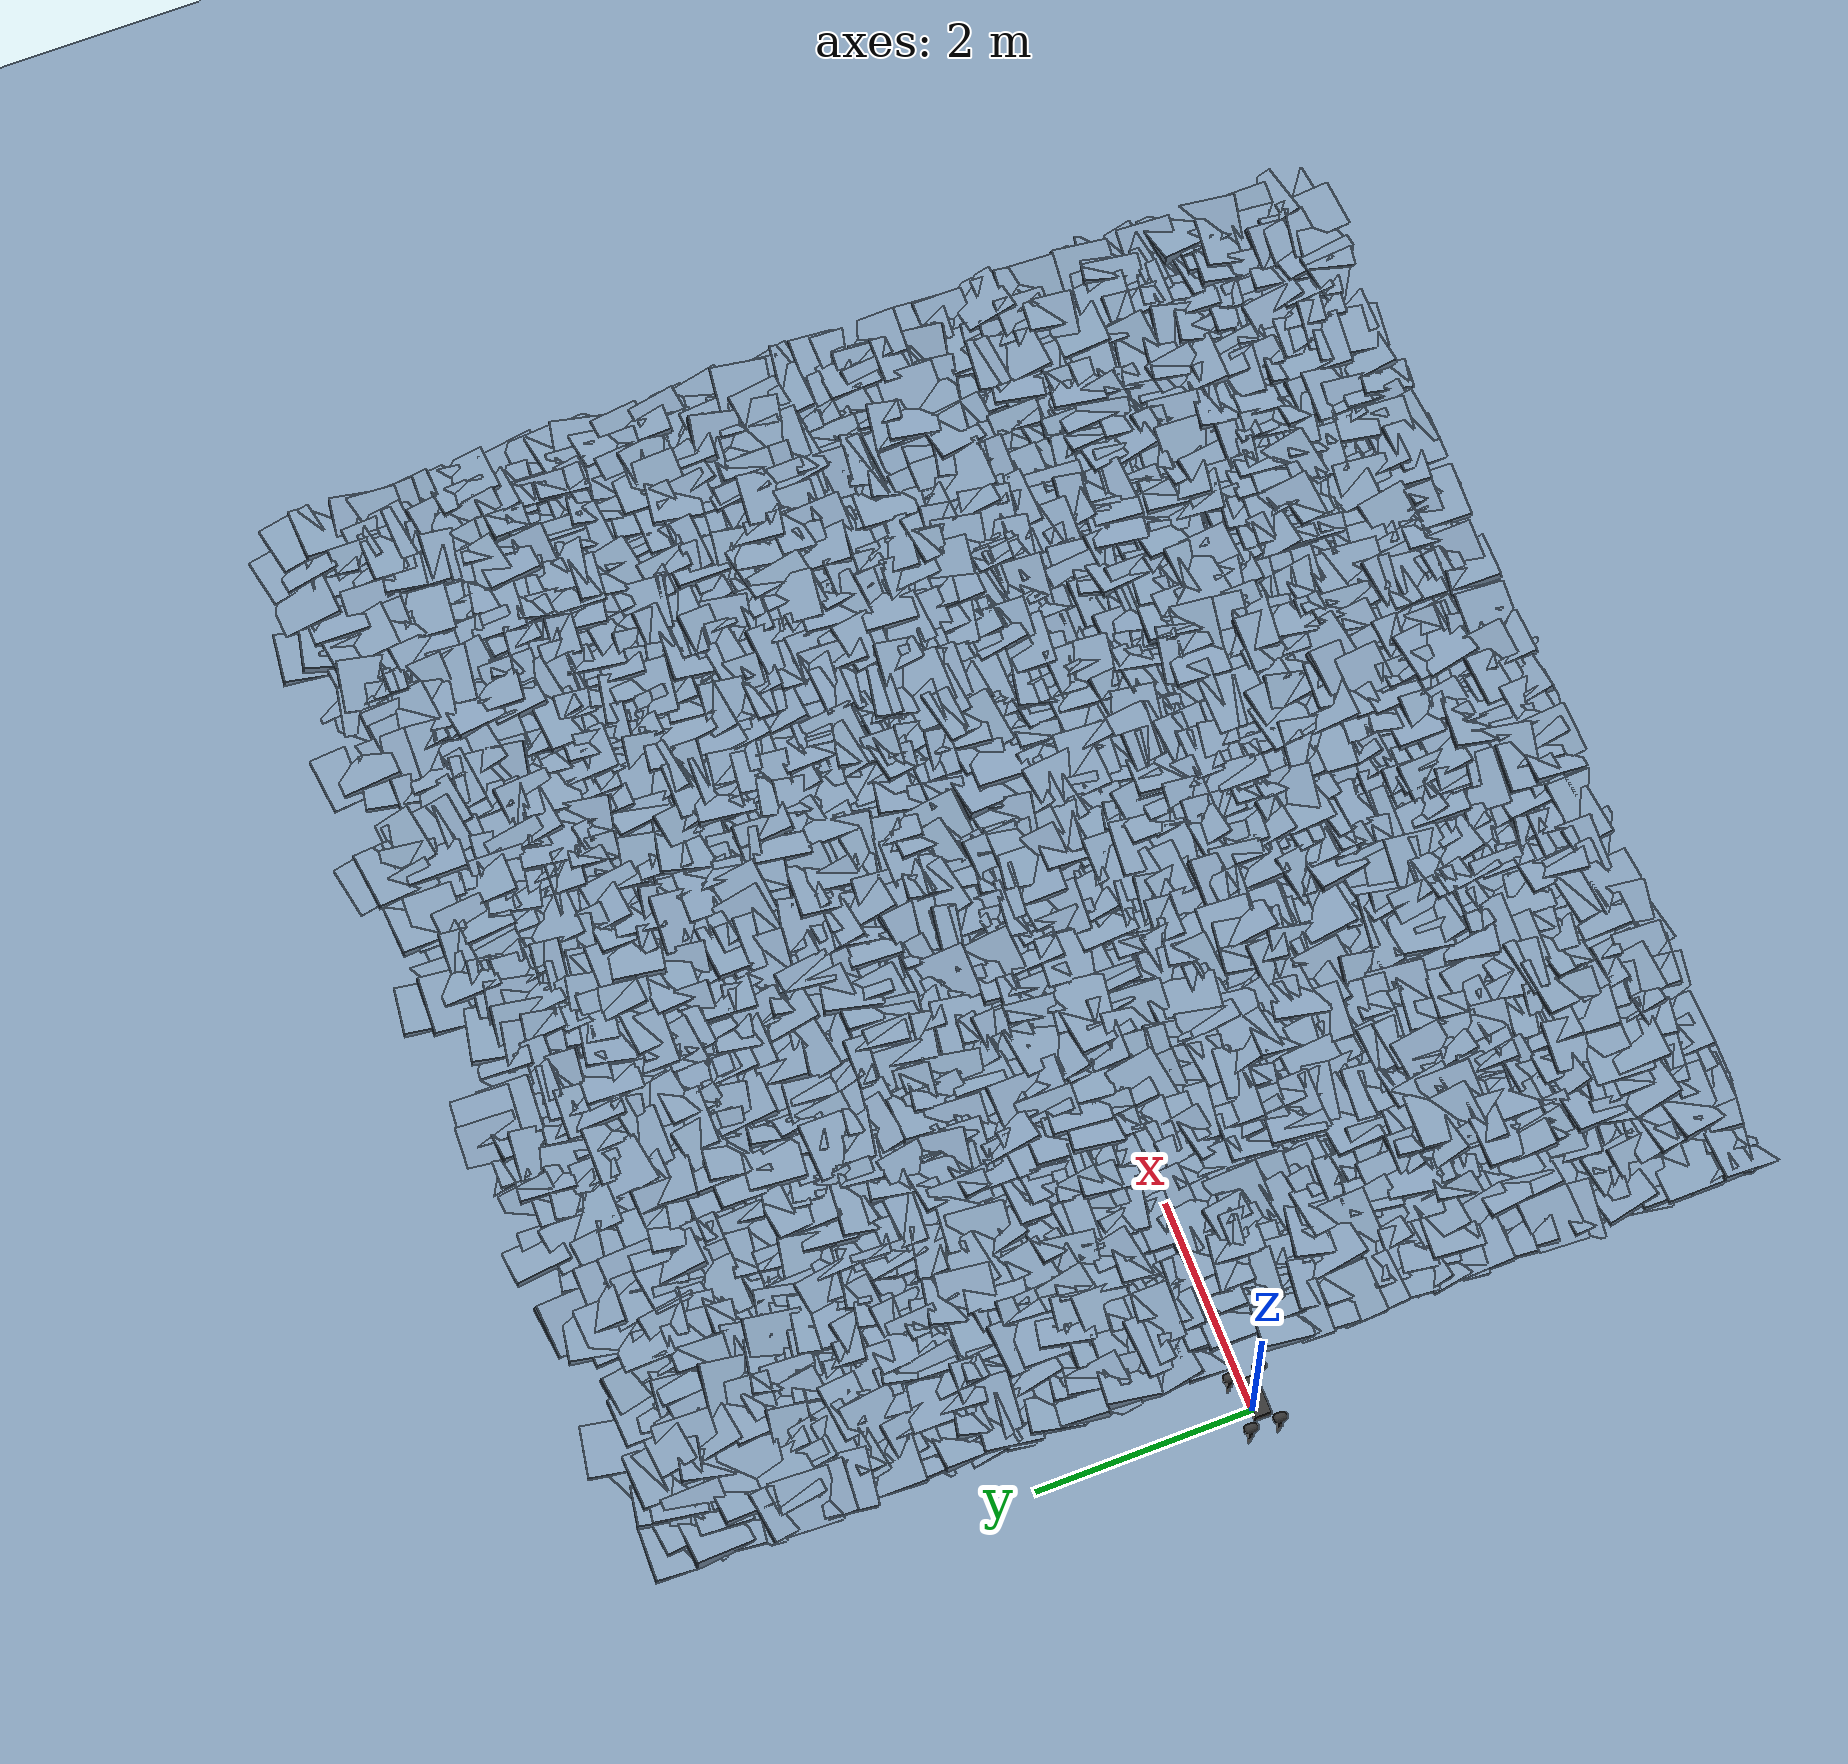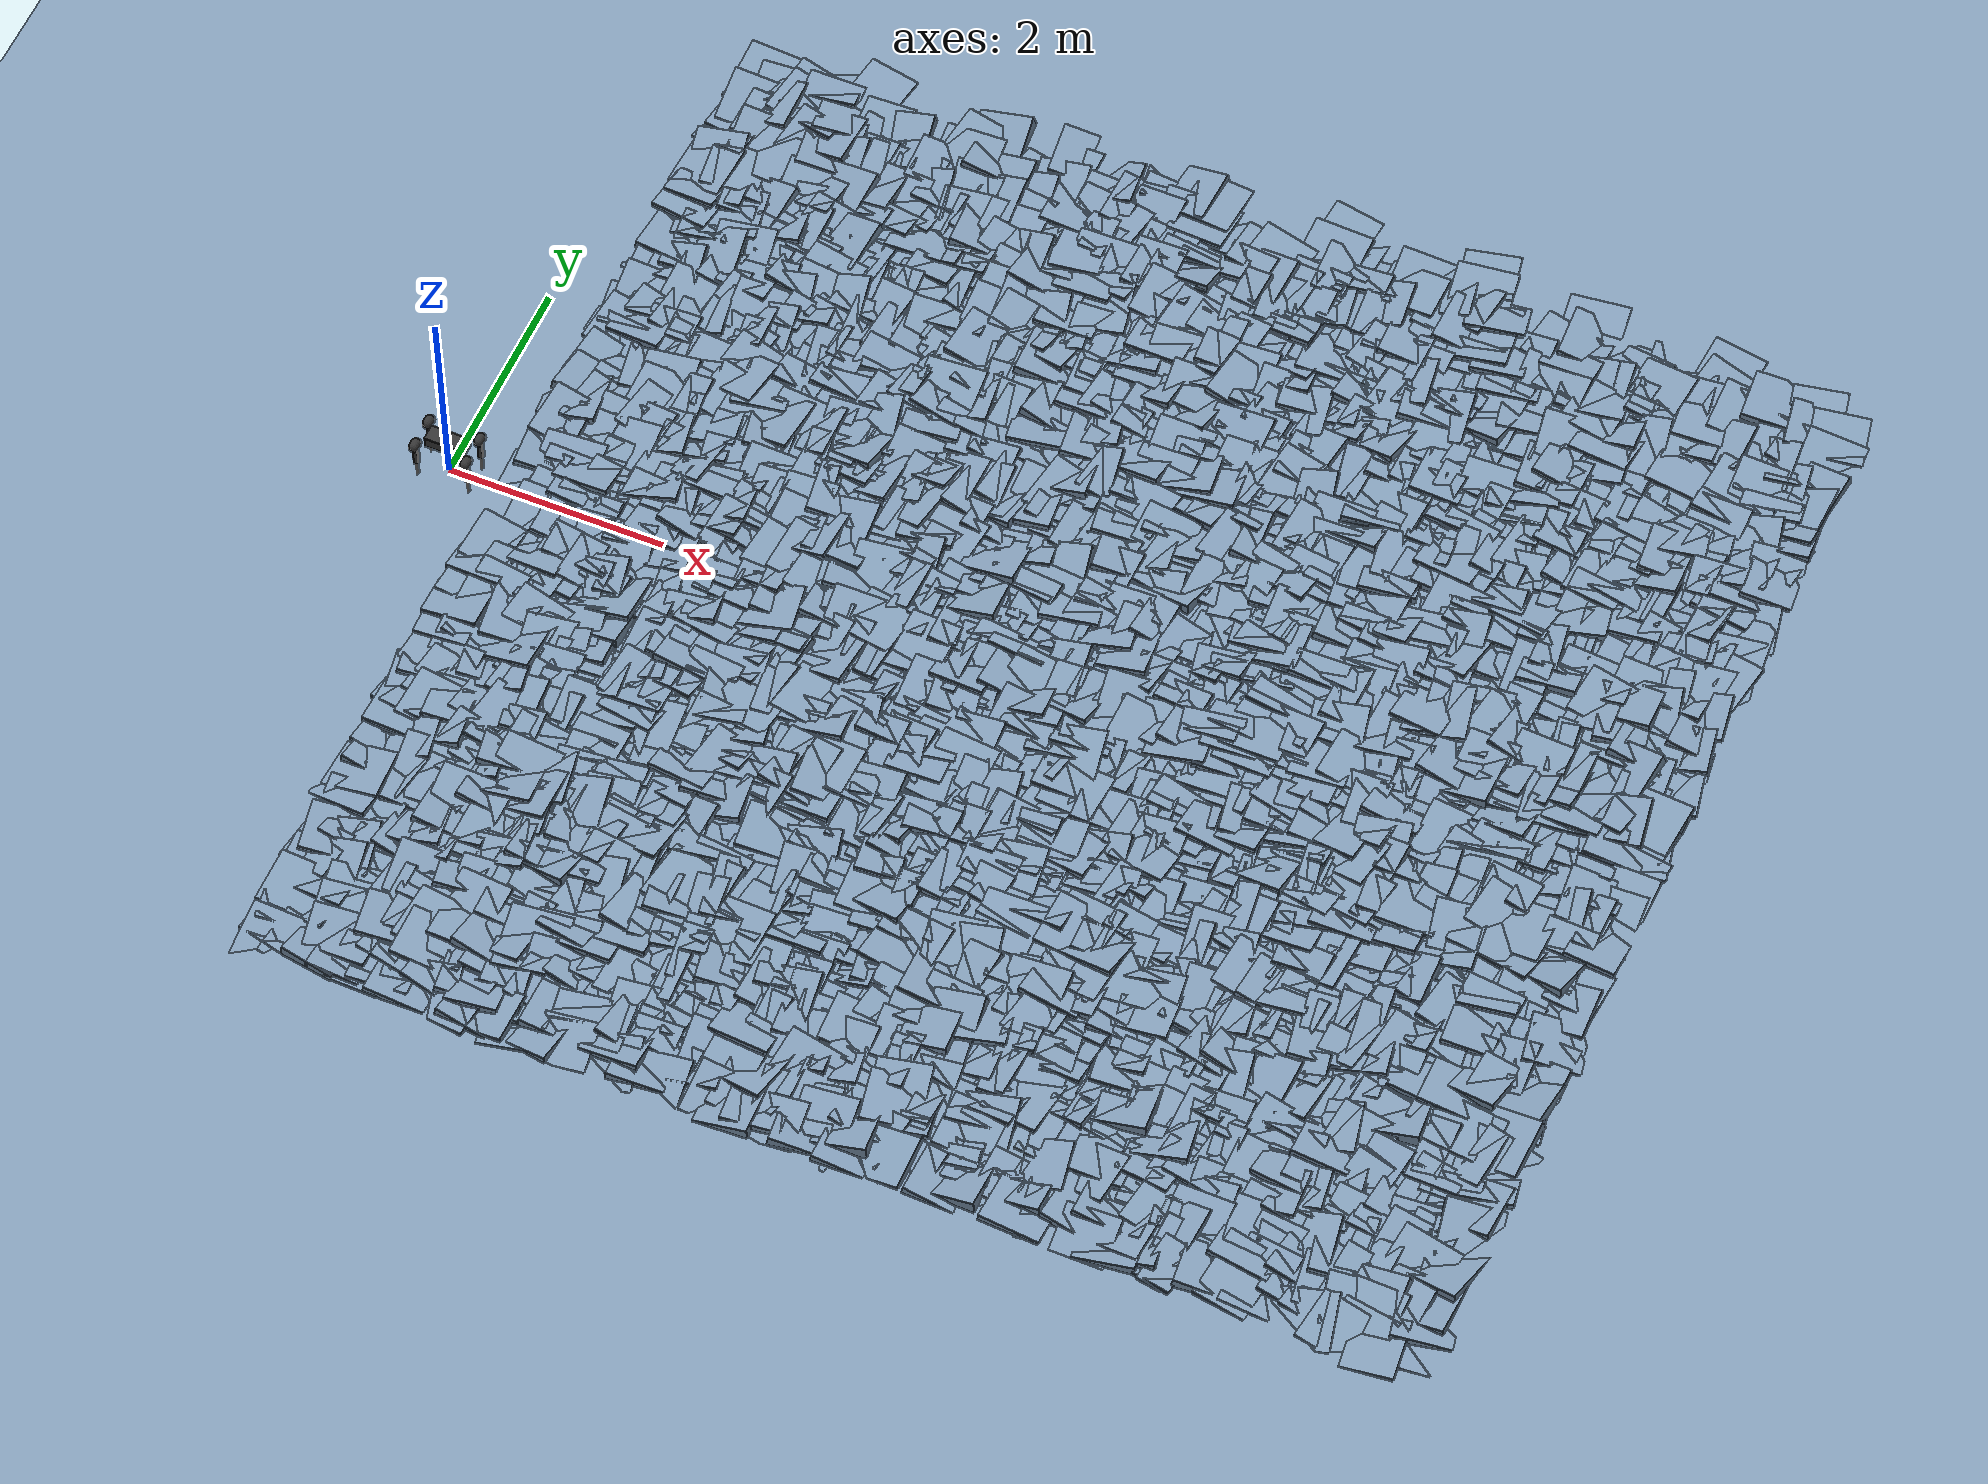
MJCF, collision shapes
<mujoco model="aliengo scene">
  <include file="aliengo.xml" />

  <statistic center="0 0 0.1" extent="0.8" />

  <visual>
    <headlight diffuse="0.6 0.6 0.6" ambient="0.3 0.3 0.3" specular="0 0 0" />
    <rgba haze="0.15 0.25 0.35 1" />
    <global azimuth="-130" elevation="-20" />
  </visual>

  <asset>
    <texture type="skybox" builtin="gradient" rgb1="0.3 0.5 0.7" rgb2="0 0 0" width="512" height="3072" />
    <texture type="2d" name="groundplane" builtin="checker" mark="edge" rgb1="0.2 0.3 0.4" rgb2="0.1 0.2 0.3" markrgb="0.8 0.8 0.8" width="300" height="300" />
    <material name="groundplane" texture="groundplane" texuniform="true" texrepeat="5 5" reflectance="0.2" />
  </asset>

  <worldbody>
    <light pos="0 0 1.5" dir="0 0 -1" directional="true" />
    <geom name="floor" size="0 0 0.05" type="plane" material="groundplane" />
  <geom pos="0.670886102283209 -4.832403844129986 -0.25" type="box" size="0.2610114640439865 0.27195788422643824 0.2539220405559183" quat="0.9944424052769119 0.08749547086392365 0.05805046445210895 0.007680412896754195" /><geom pos="0.670886102283209 -4.663942182849906 -0.25" type="box" size="0.231137403961405 0.26797645455901137 0.24855130538317988" quat="0.9942500079598217 -0.010005594558952328 0.04813530361811493 -0.09513044883215951" /><geom pos="0.670886102283209 -4.492882062625273 -0.25" type="box" size="0.25614040441629754 0.2385158209924189 0.26016364144674253" quat="0.993354383115507 -0.024661766511547917 0.08055683931006098 0.07841850839000658" /><geom pos="0.670886102283209 -4.331267688883088 -0.25" type="box" size="0.2739158999094429 0.2599910083144447 0.2735185478557441" quat="0.9989160025137966 -0.007133563462755854 0.04595827588198035 0.001941409831785402" /><geom pos="0.670886102283209 -4.084941338021235 -0.25" type="box" size="0.2711151301985653 0.25588360341091726 0.2365078070381593" quat="0.9947602896432417 0.027081030302061288 0.09846529951558709 0.004813391525584793" /><geom pos="0.670886102283209 -3.9029984550323773 -0.25" type="box" size="0.22609321395197274 0.23620794977297158 0.2628681751468847" quat="0.9960237197592166 0.007222206958920126 -0.03809821443558989 -0.08020670458556506" /><geom pos="0.670886102283209 -3.7376863560890676 -0.25" type="box" size="0.24022774007398948 0.2495214739216842 0.2712619171243866" quat="0.9916994348077871 -0.035533225104374844 0.075966133533344 0.09746162050567159" /><geom pos="0.670886102283209 -3.5449448074658245 -0.25" type="box" size="0.25322900986630287 0.25637847904228156 0.23352962543520184" quat="0.9976759521295194 -0.037024927736532105 -0.046917414061520536 -0.03272010889867893" /><geom pos="0.670886102283209 -3.3768649546880685 -0.25" type="box" size="0.23336805483001072 0.22858980208605853 0.22522103788862732" quat="0.9952683632668846 0.06830067762189379 0.05313587959732223 0.04418688511159819" /><geom pos="0.670886102283209 -3.2264869653101056 -0.25" type="box" size="0.2704097856223238 0.2684651223274105 0.25492715227709084" quat="0.9957687058672026 -0.03864200333519917 -0.06102219192746493 -0.05681348507323496" /><geom pos="0.670886102283209 -3.0750897336798824 -0.25" type="box" size="0.2648943680241246 0.23484838272710987 0.2710460269524369" quat="0.9969771514735275 -0.005675590676794766 -0.07458555996739559 0.021008125917138066" /><geom pos="0.670886102283209 -2.85649628709774 -0.25" type="box" size="0.2270703200261567 0.25294388062109574 0.24384358566191763" quat="0.9925231085548253 -0.07999013640983721 0.07122782402012019 -0.0585325050477152" /><geom pos="0.670886102283209 -2.6103444528974906 -0.25" type="box" size="0.24348069671741374 0.2723252180086973 0.22831728095646953" quat="0.9948283598141893 -0.04196572600937739 0.07283093118680163 -0.05701813581992192" /><geom pos="0.670886102283209 -2.3905249637286965 -0.25" type="box" size="0.2489003955970996 0.2640316745086266 0.2568270372639917" quat="0.9978183426708527 -0.05710259598083929 0.033129142066667915 0.0005554347561117609" /><geom pos="0.670886102283209 -2.2078711023492668 -0.25" type="box" size="0.24156000500024644 0.23376212208602049 0.24478228613671768" quat="0.9953386687361481 -0.07389994909541334 -0.010880552729978728 -0.06100283284027051" /><geom pos="0.670886102283209 -2.0372994331107384 -0.25" type="box" size="0.26626127011464695 0.22573454861451575 0.22622520669485432" quat="0.9944517399329191 0.000813668532051383 0.061765701493206995 0.0851473605401929" /><geom pos="0.670886102283209 -1.8434391065827551 -0.25" type="box" size="0.24528028304182475 0.22884237579225708 0.23031369528642398" quat="0.9911365373617986 -0.08775343906307669 0.053587468636284497 0.08411944747929619" /><geom pos="0.670886102283209 -1.6737949924979607 -0.25" type="box" size="0.22551950715855662 0.2683640466413044 0.25349020177179893" quat="0.9987984063638211 -0.011997899918519885 0.001388399986042297 -0.047495959703065256" /><geom pos="0.670886102283209 -1.424123506796528 -0.25" type="box" size="0.24045166355777492 0.22649702324111548 0.2643013115520256" quat="0.9986635409354463 -0.041492301805430704 -0.01112977250996878 0.02873410971371058" /><geom pos="0.670886102283209 -1.1956841567367205 -0.25" type="box" size="0.24986772585562717 0.25979730133499684 0.27297724101219634" quat="0.9969326277028288 -0.06726810887155853 -0.03613584591657304 0.01716210914400958" /><geom pos="0.670886102283209 -0.953626182131865 -0.25" type="box" size="0.25368959878770403 0.2359950758469631 0.2585604253531648" quat="0.9989498414210807 -0.011183315186529864 0.019160970418893655 -0.04008746685489721" /><geom pos="0.670886102283209 -0.7071213161035441 -0.25" type="box" size="0.2504571892056345 0.2710267335589836 0.25291061632344464" quat="0.9961580104282034 -0.08147706200919029 -0.02126079099574163 -0.024055880618040645" /><geom pos="0.670886102283209 -0.5078276708654128 -0.25" type="box" size="0.2627352469491901 0.23426184124595362 0.2651064198886082" quat="0.9942370140291092 0.05879337005337019 0.07859496523964189 -0.0431153222326774" /><geom pos="0.670886102283209 -0.2601020278618247 -0.25" type="box" size="0.25514339433435596 0.23855116062208495 0.23118189203973397" quat="0.9965731426989788 -0.0015087017988951613 -0.06580936534948227 -0.05008814732310659" /><geom pos="0.670886102283209 -0.031259937376393765 -0.25" type="box" size="0.2463998478382694 0.2562246109977572 0.23593839288558183" quat="0.9951199590610584 0.0022631710781667617 -0.038994249121202834 0.09061232626117503" /><geom pos="0.670886102283209 0.18337362079272346 -0.25" type="box" size="0.269364684879779 0.25156463570679205 0.23017325616488563" quat="0.9960014640430913 0.073287683522871 0.050106816536687505 -0.009965239807902123" /><geom pos="0.670886102283209 0.33452384114360534 -0.25" type="box" size="0.26214745391982763 0.23086331789083764 0.22608534958378648" quat="0.9931959160387559 0.0358511932555544 -0.0859166990651141 -0.06996345565967861" /><geom pos="0.670886102283209 0.5152319246657946 -0.25" type="box" size="0.26866476021194363 0.26852652276728695 0.23352748997226408" quat="0.9904089960113471 -0.10160282467075545 0.06739363625342586 0.06499988024035135" /><geom pos="0.670886102283209 0.7524710461537563 -0.25" type="box" size="0.22919103314040504 0.24551133935125655 0.23449085105440118" quat="0.9909544863053775 0.09357131679516914 -0.08990229954120439 -0.03422267204160373" /><geom pos="0.670886102283209 0.928227885512948 -0.25" type="box" size="0.27268932979848143 0.24919189001312633 0.27341950377670066" quat="0.9915632477039225 0.07622846049099899 0.09034516967370915 -0.05319114522785617" /><geom pos="0.670886102283209 1.1222603252913128 -0.25" type="box" size="0.2615116361607601 0.26604975379592394 0.26647543836348064" quat="0.9942441882826714 -0.054778135757295995 -0.07258470014844079 0.05665078299059954" /><geom pos="0.670886102283209 1.3608383109877087 -0.25" type="box" size="0.27395633581052914 0.27146852351613854 0.25439357585652034" quat="0.9923507138749705 -0.06949060045522759 0.08758530219336447 -0.052344359389576094" /><geom pos="0.670886102283209 1.6025051897052371 -0.25" type="box" size="0.26235365450833315 0.2443713458573113 0.2340362404548245" quat="0.9902001832103389 0.07460934538964717 0.08120323048700728 -0.08569176220158738" /><geom pos="0.670886102283209 1.841666174243338 -0.25" type="box" size="0.25958853898477346 0.25000206828986926 0.24760601826427003" quat="0.9945625421131196 0.07947087664535898 -0.023460459583535605 -0.06308198179224024" /><geom pos="0.670886102283209 2.0072216785227193 -0.25" type="box" size="0.25440284953315123 0.2622327947283053 0.250685567298116" quat="0.9949532375192124 0.04529211300613112 0.06691439162594214 -0.05949070383520337" /><geom pos="0.670886102283209 2.185382810988366 -0.25" type="box" size="0.2622650053501497 0.2384893735332947 0.23413895993483017" quat="0.9945433526720108 -0.047035814093473516 0.05049503119804209 0.07823939974711751" /><geom pos="0.670886102283209 2.4154197083416324 -0.25" type="box" size="0.2467315394325191 0.2745058487020457 0.23270579941680328" quat="0.99152547767436 0.08033370267052616 0.09603221026870737 0.03466320713353751" /><geom pos="0.670886102283209 2.5990212628469838 -0.25" type="box" size="0.23819815605095976 0.26890825404929364 0.22788958416856117" quat="0.9960450273595194 0.03813220245458297 0.07539345320396923 0.027496651110963555" /><geom pos="0.670886102283209 2.792816862701298 -0.25" type="box" size="0.2613260629572075 0.23174414663381904 0.23914630677720133" quat="0.998230071349555 -0.040654466129532905 -0.03724868469983786 0.022281708312364156" /><geom pos="0.670886102283209 3.039149020456577 -0.25" type="box" size="0.24827792120967213 0.26629593755248815 0.24930809449191102" quat="0.996609134922251 -0.06826662342438825 0.03930781657116782 -0.02376543439877574" /><geom pos="0.670886102283209 3.2494154456625424 -0.25" type="box" size="0.2421302583136604 0.2615668739757243 0.22936088669952456" quat="0.9924023902891871 0.04560959683454953 -0.08031161040209636 0.08128533483673323" /><geom pos="0.670886102283209 3.4667470992242784 -0.25" type="box" size="0.2668801674759213 0.23924412936056003 0.2723279302548782" quat="0.9973431146289364 -0.025356739754952763 0.0025466094460705794 -0.06824413697586777" /><geom pos="0.670886102283209 3.650106172444712 -0.25" type="box" size="0.23974133715195975 0.25650237347340354 0.2648010719630103" quat="0.9947175610881209 -0.09305513551076892 -0.026427309185457423 -0.03434112326627105" /><geom pos="0.670886102283209 3.848388382415111 -0.25" type="box" size="0.24643311605127557 0.2679677802969264 0.2716778295023027" quat="0.9975730887984436 -0.004910766584580166 -0.06506022775661709 -0.024310155099080823" /><geom pos="0.670886102283209 4.072383870050357 -0.25" type="box" size="0.23321379827122268 0.23634881821888423 0.26499109131727955" quat="0.991786339625703 0.09633530352960233 -0.033600500819432874 0.07713865548732783" /><geom pos="0.670886102283209 4.313712775418576 -0.25" type="box" size="0.24728438318783072 0.2532756867460473 0.251424893460386" quat="0.9958352713120585 -0.05238728492466481 -0.050078343640310045 -0.055315859274750856" /><geom pos="0.670886102283209 4.48297942790704 -0.25" type="box" size="0.23861736642803333 0.24279680988267746 0.23911656965275002" quat="0.99731873806756 -0.03298624915710204 0.029003155711020013 -0.05853254671272527" /><geom pos="0.670886102283209 4.690661892161424 -0.25" type="box" size="0.27116562580060793 0.26926325664317047 0.2674197446674283" quat="0.9924019407513581 0.062230507776529366 0.09891502238657948 0.03849117094965542" /><geom pos="0.670886102283209 4.912703805477475 -0.25" type="box" size="0.2676067388884822 0.2721305913661947 0.22542711084992073" quat="0.9902923603576138 -0.08893314424294528 -0.06118961649157599 0.08756579072916175" /><geom pos="0.670886102283209 5.065429864394824 -0.25" type="box" size="0.2584216491230816 0.24394361970879977 0.2437642403849683" quat="0.996621177840197 0.07387192841895335 0.03357134400475511 -0.012733064587835146" /><geom pos="0.8752309371308921 -4.787769958010216 -0.25" type="box" size="0.24325001601251658 0.22962728655367448 0.22748462549168402" quat="0.9920775230117477 0.052400352132613244 0.08897287185530812 -0.07155570910187736" /><geom pos="0.8752309371308921 -4.591948187513977 -0.25" type="box" size="0.22860665619009388 0.23547674138003352 0.23789984307221312" quat="0.9981020609467806 0.011625393788414694 0.05501413544789421 -0.025111173886820007" /><geom pos="0.8752309371308921 -4.3804711122762034 -0.25" type="box" size="0.25921712106905526 0.26162006864408355 0.23377729693184282" quat="0.9915726507844682 -0.06015913375540884 -0.08729049689921592 -0.07446425983752124" /><geom pos="0.8752309371308921 -4.181978574720851 -0.25" type="box" size="0.24663465178543334 0.2309804905362084 0.2559810651257019" quat="0.9962477631717455 -0.07559720076466085 -0.02771571767035821 -0.03173793638311288" /><geom pos="0.8752309371308921 -3.958366649963855 -0.25" type="box" size="0.2459643938019225 0.23798124754665767 0.25689641810541075" quat="0.9909680339692217 0.09197371376677653 -0.07397334942061497 0.06364852867599004" /><geom pos="0.8752309371308921 -3.795208908490406 -0.25" type="box" size="0.26733115500198473 0.2700519302334637 0.26161450858320456" quat="0.9929538694774953 0.03333784114120372 -0.05599221312559134 0.09897511559483814" /><geom pos="0.8752309371308921 -3.5997190427360577 -0.25" type="box" size="0.2747020276401784 0.2597375339988166 0.23222516439657923" quat="0.9919875026089137 -0.09464321242840346 0.052820533732591796 -0.06491107937145174" /><geom pos="0.8752309371308921 -3.4247706917179315 -0.25" type="box" size="0.27398870007586384 0.24631530365083878 0.2453637675958206" quat="0.9945629963871251 0.06426348430127715 -0.016222073129772377 -0.08032119985592384" /><geom pos="0.8752309371308921 -3.2298993967152994 -0.25" type="box" size="0.24604451558183854 0.2395870196943925 0.23899439074259493" quat="0.9975606096248132 0.05604606946741662 0.023608209772321743 -0.03426836228317506" /><geom pos="0.8752309371308921 -2.9875426921097 -0.25" type="box" size="0.26537720423342753 0.23752963274897881 0.2524293614975778" quat="0.9944128804068911 -0.029897310070687702 -0.07298344229548427 -0.07016118073485475" /><geom pos="0.8752309371308921 -2.7474065795708356 -0.25" type="box" size="0.2718206903496368 0.23480840234201794 0.22838246157470787" quat="0.9943748454385067 -0.026855007569702445 -0.06122974433967643 -0.08214860763077445" /><geom pos="0.8752309371308921 -2.5870691041071914 -0.25" type="box" size="0.2616989779365384 0.23599351011129635 0.25858058020016444" quat="0.9914689707981746 -0.009679557576940006 -0.08848227792110436 0.09521802667255409" /><geom pos="0.8752309371308921 -2.4019644011196446 -0.25" type="box" size="0.23659762852966196 0.2566759702819489 0.22981493493913469" quat="0.9996184850155748 -0.025543834967677478 0.0009882214911807058 -0.01046041722855138" /><geom pos="0.8752309371308921 -2.2011675837818143 -0.25" type="box" size="0.2392459274268202 0.23765942353126382 0.2718646676605642" quat="0.9971021784917856 0.03362200720617805 0.05975067618356917 -0.0329645714968272" /><geom pos="0.8752309371308921 -1.9644726244661141 -0.25" type="box" size="0.2594026201200855 0.2574506172098771 0.2552058709454629" quat="0.9967395632408359 0.00678758390207914 0.025084878415236628 -0.07638665230347888" /><geom pos="0.8752309371308921 -1.8079965270569724 -0.25" type="box" size="0.2333100580733491 0.25813551176542365 0.23506345467936762" quat="0.9946106484729432 0.0971036806222934 -0.025647459671320778 -0.025743755869004792" /><geom pos="0.8752309371308921 -1.6263353631156803 -0.25" type="box" size="0.27129262242465574 0.2697951479982139 0.2513979578203293" quat="0.9966582840034547 0.07514873402058397 0.03187934519296151 0.0029393966150940173" /><geom pos="0.8752309371308921 -1.380663230966277 -0.25" type="box" size="0.24366806967632607 0.2334706163036936 0.22735589690498098" quat="0.9897396067982542 -0.0782755046780733 0.10002171721350106 -0.0654531297028069" /><geom pos="0.8752309371308921 -1.1917654193966372 -0.25" type="box" size="0.2727859640668945 0.2678661990045573 0.24941798272005677" quat="0.9978989333566927 0.04672213972179994 0.044613404579028945 -0.004940100936163908" /><geom pos="0.8752309371308921 -0.9520821648302569 -0.25" type="box" size="0.2254731689781106 0.25678538400440654 0.274544249569654" quat="0.9955517975391586 0.0727530312262522 0.004184572865522668 -0.05971686708020746" /><geom pos="0.8752309371308921 -0.777918432324614 -0.25" type="box" size="0.24801703460945276 0.24485578638487024 0.23972882264555284" quat="0.997546784097898 -0.047261465179185586 0.01457644971479692 0.049540837283700664" /><geom pos="0.8752309371308921 -0.559784786118839 -0.25" type="box" size="0.2373089555164628 0.25817660138449483 0.23908247936851457" quat="0.9952182796021053 -0.06175332511731972 0.07068025662031947 -0.02704448385282924" /><geom pos="0.8752309371308921 -0.3176717406826306 -0.25" type="box" size="0.25922772343692196 0.25361958532703976 0.22691803664272134" quat="0.997655256196493 0.0008930582101918988 0.06100290837912743 0.031013503507841572" /><geom pos="0.8752309371308921 -0.1103224789523587 -0.25" type="box" size="0.26046990067357234 0.2729148828064165 0.2643744459031805" quat="0.9986812161134705 0.04100547930688913 0.03068983886168987 0.003537377499738097" /><geom pos="0.8752309371308921 0.11595526940978296 -0.25" type="box" size="0.22911505145258249 0.22666744602648725 0.2591770907147306" quat="0.9972838371258096 0.042561206869948784 0.060032226060886595 -0.0031022107552130017" /><geom pos="0.8752309371308921 0.28400146712217467 -0.25" type="box" size="0.22993278753569837 0.26318129266393137 0.23347578619338688" quat="0.9961017107251554 -0.01905431975985998 0.0638281722409179 -0.05782974336179769" /><geom pos="0.8752309371308921 0.5305017487622639 -0.25" type="box" size="0.27426406059002384 0.24599928612273955 0.24772825447642147" quat="0.9956205294887246 0.08721258515659476 0.007064499614186576 0.032921407869294955" /><geom pos="0.8752309371308921 0.6949469069868677 -0.25" type="box" size="0.22597913149079327 0.256052213836047 0.2542639342955668" quat="0.9982902763394449 -0.03133612549191001 0.013130342590592875 0.04756222775190113" /><geom pos="0.8752309371308921 0.8756164216671785 -0.25" type="box" size="0.2424187075801909 0.24564604811130444 0.25698262713642933" quat="0.9954020272433953 0.09291458928317416 -0.007355133928059989 -0.022081332907646193" /><geom pos="0.8752309371308921 1.1213816542334767 -0.25" type="box" size="0.274871454697956 0.27333321879742534 0.25757417880648065" quat="0.9929127736038087 0.008449411644514786 0.08119486184238196 -0.0863725990557743" /><geom pos="0.8752309371308921 1.2912992985597365 -0.25" type="box" size="0.24781380797222757 0.2635058593674303 0.22646390456775942" quat="0.9933331319567861 0.0641811751931621 0.06099971622812104 -0.07381802170090779" /><geom pos="0.8752309371308921 1.495266570726412 -0.25" type="box" size="0.25758719027107896 0.24180503991738014 0.24741800214545678" quat="0.9981916533749665 -0.02471909102230304 -0.022359519012957626 0.05002440985250052" /><geom pos="0.8752309371308921 1.6743093480418247 -0.25" type="box" size="0.26449646475047506 0.24637243756400645 0.22995150013684798" quat="0.9978369231466925 0.05398740029223015 0.016685181564467834 0.0335922629632054" /><geom pos="0.8752309371308921 1.8309225260739677 -0.25" type="box" size="0.23941130638448763 0.25924620597420267 0.23002235004406274" quat="0.9996023813102515 -0.002293737121796901 -0.018430904192192083 -0.021216027421478982" /><geom pos="0.8752309371308921 2.0481258653440513 -0.25" type="box" size="0.25561845816011913 0.22945780735576846 0.2735044629556422" quat="0.994704419404349 -0.07957102813880648 -0.04144107114753781 -0.050141869934568095" /><geom pos="0.8752309371308921 2.2076931901227725 -0.25" type="box" size="0.26991484864966314 0.22883405619246622 0.24063845463047853" quat="0.9883777854581017 0.08159327269891756 0.08040361208271272 -0.09993573048350311" /><geom pos="0.8752309371308921 2.385157508677545 -0.25" type="box" size="0.252269567448745 0.2639613374797311 0.23681585840265185" quat="0.9953900846346039 -0.07860005030230893 -0.00048346976307196915 0.05495796357743439" /><geom pos="0.8752309371308921 2.5965661949849785 -0.25" type="box" size="0.26014562668706054 0.27221261565095556 0.2470598134692749" quat="0.9993069002847119 0.034742955941305706 0.013052282010760528 0.0028781921639705913" /><geom pos="0.8752309371308921 2.783256760607678 -0.25" type="box" size="0.23293487824372403 0.24656460940960986 0.2550216914963241" quat="0.9919755300962984 0.05830460695283274 -0.08087345761383553 0.0777470536536687" /><geom pos="0.8752309371308921 2.9438136848214347 -0.25" type="box" size="0.23401558250457583 0.25511941097442004 0.23123502793843626" quat="0.9920664245678145 -0.09203968068980103 0.046113241080827705 0.07215591050477958" /><geom pos="0.8752309371308921 3.1480233586246733 -0.25" type="box" size="0.2323953669525113 0.23948062698015596 0.22537196547082022" quat="0.9920965335739836 0.06879962792096696 0.099938068000951 0.03199159003018502" /><geom pos="0.8752309371308921 3.3009182011865725 -0.25" type="box" size="0.256996578018401 0.23247260707590503 0.23420888021808722" quat="0.993187755046834 -0.08051482877822837 -0.02194357463102535 0.0813260419807541" /><geom pos="0.8752309371308921 3.520912860853276 -0.25" type="box" size="0.24015726255568356 0.2610700810890916 0.2333273331426359" quat="0.9961141135052082 0.033794989959982445 0.048439294040866554 0.06533151094349843" /><geom pos="0.8752309371308921 3.71281842434394 -0.25" type="box" size="0.2261895534562167 0.23925241166567013 0.2664409805774512" quat="0.9957573503613409 -0.059934052481676145 -0.04301607158015428 0.054998419434530654" /><geom pos="0.8752309371308921 3.9406443117402965 -0.25" type="box" size="0.2641497893987679 0.26992946051412336 0.27349019463269614" quat="0.9971792210483486 -0.026967750442396285 0.009652812961477226 0.06937697562892349" /><geom pos="0.8752309371308921 4.118155466840211 -0.25" type="box" size="0.2465926382840703 0.252287155885051 0.23251857012128202" quat="0.9973688409495881 -0.0012432133110458006 -0.015876384855704664 0.0707233336845208" /><geom pos="0.8752309371308921 4.341214343687524 -0.25" type="box" size="0.23433897175155954 0.2675354835416748 0.2741614131379807" quat="0.9915080681298573 0.0741756324466682 0.1001667066513007 0.037099289254207385" /><geom pos="0.8752309371308921 4.552757413715993 -0.25" type="box" size="0.23751304453514474 0.24147646029091474 0.2678159098834361" quat="0.9986886967844912 0.02023532571149082 0.04336356998072189 -0.01819393598899407" /><geom pos="0.8752309371308921 4.729009951490491 -0.25" type="box" size="0.2744791390309036 0.26326473807405587 0.2743293762906825" quat="0.9949250007800945 -0.014881396581696155 -0.09890739905966676 0.010959619964171594" /><geom pos="0.8752309371308921 4.907532729696133 -0.25" type="box" size="0.26006914482866306 0.2497140111743082 0.25723749222916886" quat="0.9964260707031602 0.03483633737312614 0.0493554108749942 0.059038619892801306" /><geom pos="1.1072197937076995 -4.7843061875770605 -0.25" type="box" size="0.2495200104250219 0.262241467905366 0.25828257833033186" quat="0.9915936833024279 -0.09428927889805291 0.03729065334674755 -0.08037976295425522" /><geom pos="1.1072197937076995 -4.600955970775699 -0.25" type="box" size="0.2296273683548447 0.2313674139691315 0.27386420471844397" quat="0.9896552712808673 0.05516870165205535 0.09653227463662205 0.09066630210557432" /><geom pos="1.1072197937076995 -4.356300274923818 -0.25" type="box" size="0.26213178401755577 0.2358769278019141 0.2535654668639058" quat="0.9907567247568317 0.06141419685631381 0.08167487239516572 0.08921112034294133" /><geom pos="1.1072197937076995 -4.192054922808421 -0.25" type="box" size="0.24964245065819315 0.24627624170062917 0.2677464782571184" quat="0.9961750052111853 -0.003995326968348454 0.026814797537786882 0.08306842353095542" /><geom pos="1.1072197937076995 -3.957657073390021 -0.25" type="box" size="0.24845826972042478 0.24630597910491348 0.25242311677163254" quat="0.9997754215005763 -0.007196121503207314 0.011340441333503148 -0.016392583353990322" /><geom pos="1.1072197937076995 -3.7926837504200615 -0.25" type="box" size="0.254115723075841 0.23682667253360587 0.24953133861026947" quat="0.9935983654431852 0.07794206848598265 0.013591071290631808 -0.08063873095436111" /><geom pos="1.1072197937076995 -3.5639739511512003 -0.25" type="box" size="0.254742691472859 0.27101681578218495 0.2457212807678525" quat="0.9973655996642559 -0.01696513567093801 0.02853531117923498 -0.06449636264108397" /><geom pos="1.1072197937076995 -3.386648460106542 -0.25" type="box" size="0.25934934470152365 0.2649793392786006 0.24745161991303474" quat="0.9953631814411986 -0.08208991721752612 -0.049322433841597436 -0.008982206990300997" /><geom pos="1.1072197937076995 -3.228518773097837 -0.25" type="box" size="0.2687061024667134 0.2620513824163186 0.23228964601557797" quat="0.9990821288835868 0.03825899708519877 -0.012082080233246263 -0.015005739725598922" /><geom pos="1.1072197937076995 -3.031945282655775 -0.25" type="box" size="0.2564510519447354 0.2571114606931621 0.2637527828650859" quat="0.9943112227773251 -0.031303753033712224 0.09437932029735831 0.038181293918274496" /><geom pos="1.1072197937076995 -2.7989624182073998 -0.25" type="box" size="0.2698368474624535 0.25754873995156513 0.2713197421607046" quat="0.9943005320830861 0.019602353464932522 0.08230262716404382 0.06487277703184559" /><geom pos="1.1072197937076995 -2.5718889361211925 -0.25" type="box" size="0.238721312983322 0.2586162751204472 0.23672200518415065" quat="0.9986451052296536 -0.048722606293892114 -0.0019445587029462215 -0.01817361076493347" /><geom pos="1.1072197937076995 -2.3905901826172378 -0.25" type="box" size="0.2250688983799485 0.2506197329593891 0.266966510339031" quat="0.9894565508039079 -0.06413403024036088 -0.10272335342042531 0.0794384849957792" /><geom pos="1.1072197937076995 -2.1679891715125743 -0.25" type="box" size="0.2738649623527524 0.23187692617071448 0.27454350852004805" quat="0.9963487827093 -0.0604789567070185 0.025458130518076428 0.05461943408578208" /><geom pos="1.1072197937076995 -1.9987265763867592 -0.25" type="box" size="0.24444658270368938 0.24432785584922923 0.22948509583679905" quat="0.9954234631696017 0.017172573328465297 0.05026935044481777 -0.07943691901484484" /><geom pos="1.1072197937076995 -1.798738627690291 -0.25" type="box" size="0.2518967376411445 0.24697050808957483 0.22621630367625525" quat="0.9997298829708382 -0.016235129295757045 0.010157861430756516 -0.013168125265878112" /><geom pos="1.1072197937076995 -1.6001126761650504 -0.25" type="box" size="0.2309611680523967 0.2671208819174213 0.24400234112951402" quat="0.9942595059860925 -0.02262252000435392 0.06911709161368589 0.07847983175191747" /><geom pos="1.1072197937076995 -1.414770961473201 -0.25" type="box" size="0.2696239824382916 0.22766206362841976 0.228766509915274" quat="0.995743210984833 0.07240763581116516 0.02914422440478414 -0.04902250746030512" /><geom pos="1.1072197937076995 -1.1798429702368383 -0.25" type="box" size="0.22839826968118276 0.27181078973164624 0.27056994138244317" quat="0.9940590679110002 -0.03388586719189205 0.07210507069712348 0.07415643120006288" /><geom pos="1.1072197937076995 -0.9984819820612962 -0.25" type="box" size="0.22827566062479457 0.25471741089316824 0.2320293660250142" quat="0.9945267506546157 -0.08857922763903946 0.04670370962479657 0.02981654189415419" /><geom pos="1.1072197937076995 -0.8449800621697223 -0.25" type="box" size="0.26762048434717145 0.23609517962283835 0.26844505241081607" quat="0.9983525422293886 -0.019485826421774235 -0.024439112257300347 -0.04811687629982063" /><geom pos="1.1072197937076995 -0.6119418479247818 -0.25" type="box" size="0.24036871871654922 0.24909553917537938 0.22519186635806676" quat="0.9965729589925229 -0.06072141799947849 0.05608243666482814 -0.0031633998728324854" /><geom pos="1.1072197937076995 -0.4421281457340456 -0.25" type="box" size="0.25127264260955523 0.25993857603698606 0.2473407578208742" quat="0.9943126796994535 -0.0803484551901745 -0.05215438239448137 -0.04654396990475456" /><geom pos="1.1072197937076995 -0.2838739149311795 -0.25" type="box" size="0.2585795076958084 0.2689614829412569 0.2262877449107463" quat="0.9978102890847763 -0.06314140877656171 -0.019068654162966634 -0.004916901735804362" /><geom pos="1.1072197937076995 -0.09869271109025135 -0.25" type="box" size="0.2483777181088003 0.23150514789794274 0.2617603587558603" quat="0.9969849353141385 -0.024162071963056104 0.07371539905438772 0.0018091371887099846" /><geom pos="1.1072197937076995 0.05449697367525985 -0.25" type="box" size="0.2328815189676904 0.23614420508962572 0.25547162630510134" quat="0.9943407649813514 0.016589075795149136 0.09301424627556945 -0.048575669324791536" /><geom pos="1.1072197937076995 0.2885756786180558 -0.25" type="box" size="0.2734769945471378 0.2544983073086196 0.247599524846173" quat="0.9936937462988521 -0.09042409444867198 0.06618920733731748 -0.003900069454235729" /><geom pos="1.1072197937076995 0.46793430731939 -0.25" type="box" size="0.2573862494160154 0.24329484591720918 0.27043523535883424" quat="0.9952021081725704 -0.09091121528719699 -0.0316053188652448 -0.017578926113464705" /><geom pos="1.1072197937076995 0.6637006227935318 -0.25" type="box" size="0.25050675179619125 0.24223014306082502 0.23860025535366836" quat="0.9966138783322122 0.06303507592689503 -0.023892345156743815 -0.047079853031081066" /><geom pos="1.1072197937076995 0.8813868981726127 -0.25" type="box" size="0.2525962916110372 0.26272670321456404 0.2286597785783753" quat="0.9972851318587592 0.033576965414776255 -0.013974197886430846 -0.06402870419134674" /><geom pos="1.1072197937076995 1.046664950854077 -0.25" type="box" size="0.2554260954986075 0.253849421511692 0.25781421923346504" quat="0.9949174604701904 0.0931158178987498 0.02646640819864983 -0.027716791763413778" /><geom pos="1.1072197937076995 1.2171125817535104 -0.25" type="box" size="0.24857084923450246 0.2667251996295322 0.2376231121000167" quat="0.997268219796946 0.014636724552596847 -0.0333416081586461 -0.06426664175757874" /><geom pos="1.1072197937076995 1.4516646190306615 -0.25" type="box" size="0.26571492666600843 0.24861990618986612 0.24692677772992164" quat="0.9931018234583904 -0.029730829035519924 -0.06122101888284906 -0.0954821077240466" /><geom pos="1.1072197937076995 1.6539587184234783 -0.25" type="box" size="0.2530226958557284 0.2538266228900146 0.2450285812150597" quat="0.993357639892002 -0.035919601933174526 0.057620367974565045 0.09289927157749704" /><geom pos="1.1072197937076995 1.8852518373162068 -0.25" type="box" size="0.2724946787322646 0.2558405711542144 0.2628075273891239" quat="0.9987150832510304 0.02213551242518324 -0.03917485462544417 -0.023313780080395776" /><geom pos="1.1072197937076995 2.0880580198923226 -0.25" type="box" size="0.23300248438135168 0.2480356747973665 0.2674025589309767" quat="0.9953868277202174 0.07958877426293097 -0.052149986646353425 -0.012291017256179669" /><geom pos="1.1072197937076995 2.30474868366934 -0.25" type="box" size="0.24153180909383 0.25853329136814823 0.24966504405917794" quat="0.993242364740562 -0.03686962386390428 0.09469607627625923 -0.0560614739245381" /><geom pos="1.1072197937076995 2.5347096035472187 -0.25" type="box" size="0.2631687325303032 0.25119831832590434 0.2694238130736525" quat="0.9998211130426266 0.007750314464186814 0.017248687973878827 0.0003966145353557646" /><geom pos="1.1072197937076995 2.7479039193868493 -0.25" type="box" size="0.27140362498666154 0.25771142215633996 0.23438562081059452" quat="0.9972297405738006 0.025545796314644688 0.06981752729007738 0.0024020176644123366" /><geom pos="1.1072197937076995 2.9029631229431097 -0.25" type="box" size="0.25990259314922287 0.2458333604063828 0.24571522671937238" quat="0.997280655955233 0.005068501080715366 -0.025130402355718992 -0.0690946194123288" /><geom pos="1.1072197937076995 3.061368361481854 -0.25" type="box" size="0.25912168387754275 0.24539593431377552 0.2697564109082867" quat="0.9937438916828577 0.03632758623535743 -0.07947486119303517 0.0695494835327296" /><geom pos="1.1072197937076995 3.3035335201667415 -0.25" type="box" size="0.23991441070453612 0.26421724047885997 0.2517213176978833" quat="0.9907227221729443 0.031893717095244946 -0.09280060951423581 0.0940176869204191" /><geom pos="1.1072197937076995 3.4665677021822052 -0.25" type="box" size="0.25469530727290446 0.26783612280644425 0.27352685475465693" quat="0.9944247037484215 -0.02373270337049909 -0.05499174564496886 0.08678810561655903" /><geom pos="1.1072197937076995 3.7018246169106597 -0.25" type="box" size="0.2670375886706889 0.2427973368901916 0.24871712656954592" quat="0.9931986763413837 -0.05814058458857421 0.0757657170062368 0.06660043441264506" /><geom pos="1.1072197937076995 3.9512134355709136 -0.25" type="box" size="0.2578543073219455 0.22502267320014066 0.23961064137493304" quat="0.9963466807802296 0.046421554577268126 -0.004516309546896295 -0.07153973662885106" /><geom pos="1.1072197937076995 4.173288457467763 -0.25" type="box" size="0.24774212225417275 0.27242038714284045 0.26949409684915315" quat="0.9971730303139105 -0.011986447283313462 -0.04412793563997703 -0.05962380390625228" /><geom pos="1.1072197937076995 4.377428228687355 -0.25" type="box" size="0.274413494592579 0.2507539205972454 0.2715877858399757" quat="0.9991933858184523 0.038315729465015616 0.009868996285720152 -0.006861889283111692" /><geom pos="1.1072197937076995 4.611519335673508 -0.25" type="box" size="0.25195743354011435 0.23317842512395004 0.24927007983636348" quat="0.9984673558457003 -0.04063514613717261 -0.0015323215029766533 -0.037541659522695225" /><geom pos="1.1072197937076995 4.858536612668159 -0.25" type="box" size="0.2692464657526354 0.24687840194597832 0.27182026767513606" quat="0.9942228377369422 0.011588787240927073 0.07257296774542094 -0.07822923548909587" /><geom pos="1.1072197937076995 5.036535237719431 -0.25" type="box" size="0.2526541756660538 0.2287553939927611 0.24465094624315673" quat="0.9907737439485472 0.07254227358410921 0.08202107182667169 -0.07985956812950279" /><geom pos="1.3043141328629924 -4.7832421905195766 -0.25" type="box" size="0.2377562063693105 0.2613433895769675 0.24603137933091757" quat="0.9954913475437684 -0.08575502731159822 0.03970177876105219 -0.008174412485767522" /><geom pos="1.3043141328629924 -4.621522599205669 -0.25" type="box" size="0.25370023405981157 0.2263758526459801 0.27127808475294274" quat="0.998641190841004 -0.03116531209637283 -0.03951947549888666 -0.013516890688694438" /><geom pos="1.3043141328629924 -4.41438388053334 -0.25" type="box" size="0.2575847501888706 0.22944834535746042 0.24718875411947655" quat="0.9988980452783335 -0.007915164909603471 0.033792108453651076 0.031593333313137184" /><geom pos="1.3043141328629924 -4.193098437485318 -0.25" type="box" size="0.2633396821800172 0.22645766944750886 0.23289254717416843" quat="0.9930000952693202 0.06824583182412916 0.04203407986380772 -0.08675513450947307" /><geom pos="1.3043141328629924 -3.970919507772144 -0.25" type="box" size="0.23404674410935722 0.24245728652052112 0.2478816659861471" quat="0.9940706800158159 0.07701098515996425 -0.06590650198060764 -0.03935891632483314" /><geom pos="1.3043141328629924 -3.759850703444081 -0.25" type="box" size="0.23125039956275048 0.26481018547186985 0.22914390150450162" quat="0.997377660468069 -0.007709899020168063 0.025373492867087004 -0.06733903560390354" /><geom pos="1.3043141328629924 -3.5189304789230444 -0.25" type="box" size="0.2678337870092292 0.2621096449222353 0.24395549586558649" quat="0.9917240708756825 -0.06669908752381981 0.0861409437402939 -0.06792890975708098" /><geom pos="1.3043141328629924 -3.351087106807364 -0.25" type="box" size="0.2696835891902568 0.26690509972425436 0.2600414691448343" quat="0.9924412877839186 -0.07505539220701692 -0.05215519919443639 0.08189513782537262" /><geom pos="1.3043141328629924 -3.134921561799266 -0.25" type="box" size="0.26716151354785694 0.2575174365023522 0.2440371981935933" quat="0.9953796291988143 0.0022377284063085957 -0.01030873097112095 -0.09543645222542432" /><geom pos="1.3043141328629924 -2.8993681072846877 -0.25" type="box" size="0.27383037318155085 0.2695153382393293 0.2506784940211" quat="0.9964161622234481 -0.014079960354045896 0.04801994021974892 0.06819583357959391" /><geom pos="1.3043141328629924 -2.6624274489131454 -0.25" type="box" size="0.2405938469381126 0.2259327380935343 0.23861789814907844" quat="0.994896535315382 -0.03501736951243631 -0.07045999781774388 0.06316689447330441" /><geom pos="1.3043141328629924 -2.4628862019785793 -0.25" type="box" size="0.23618282386821998 0.2585477469977698 0.2650257979314172" quat="0.9919140927306429 0.04942322696916658 0.08812356654335676 -0.0767985305717376" /><geom pos="1.3043141328629924 -2.2307437506851464 -0.25" type="box" size="0.22526356510131126 0.2549276342266652 0.23396581343606387" quat="0.9965072398730843 0.015694613352461997 0.06658617252136262 0.047888220067142905" /><geom pos="1.3043141328629924 -2.0631305976918375 -0.25" type="box" size="0.2511641115775185 0.2311015236351843 0.25370872022715424" quat="0.9949415369587663 -0.06858157091536168 0.03428180889221517 -0.06490503635301935" /><geom pos="1.3043141328629924 -1.8909923289983177 -0.25" type="box" size="0.22993430351408323 0.2679697629678786 0.24495645964497353" quat="0.9945103778775338 0.03981917419707977 -0.04281279809248787 -0.08677906417817191" /><geom pos="1.3043141328629924 -1.67968609131482 -0.25" type="box" size="0.26186726632478374 0.22547779511110763 0.272286005003758" quat="0.9928244883119884 -0.007663336586135135 -0.08539211449798385 0.0833606349662076" /><geom pos="1.3043141328629924 -1.443059770230799 -0.25" type="box" size="0.2417943638520173 0.24415715855712034 0.27435770376691165" quat="0.9933542019438221 -0.08603863031283883 -0.07620805803111123 0.006092246348404069" /><geom pos="1.3043141328629924 -1.2521650675093108 -0.25" type="box" size="0.24871952010071544 0.2560291429760984 0.2529690250647591" quat="0.9984775823850399 0.03360640860382471 -0.029327806191374067 -0.03245006254662314" /><geom pos="1.3043141328629924 -1.1008263249207046 -0.25" type="box" size="0.2674914084426578 0.2568229109644641 0.26557046264582335" quat="0.9900579936256213 0.08431411391993257 0.06844582854549207 -0.08939501108354429" /><geom pos="1.3043141328629924 -0.9466248949889566 -0.25" type="box" size="0.24221618057555205 0.23351886973019448 0.23007143227744034" quat="0.9969878551338054 -0.0695528836334283 -0.023829093046633637 0.02469387410967072" /><geom pos="1.3043141328629924 -0.7834986034705729 -0.25" type="box" size="0.24695669529203915 0.25177551271004994 0.2449141866452956" quat="0.993256395394265 -0.0321692223124433 0.06826287122551182 -0.08801735372216689" /><geom pos="1.3043141328629924 -0.5492890132561499 -0.25" type="box" size="0.2465426599005837 0.27340572501477256 0.24664342692573388" quat="0.9966857933693972 -0.05327181523384945 0.0031434507842473653 -0.06139757091671429" /><geom pos="1.3043141328629924 -0.3654549227882704 -0.25" type="box" size="0.2657308798108747 0.24102629829567182 0.26085585757008906" quat="0.9940999117381668 0.07955937392411581 -0.001509301821470542 -0.07371155615630119" /><geom pos="1.3043141328629924 -0.20809826629764583 -0.25" type="box" size="0.264075426278244 0.2561187263509921 0.2565205835820483" quat="0.9972536766397968 -0.0009247579630538265 0.07405203268114958 -0.0007387197758542848" /><geom pos="1.3043141328629924 0.03639054360998539 -0.25" type="box" size="0.24329648240172855 0.24956002450637493 0.24705317081079786" quat="0.9964464462624226 0.05756823579934015 -0.05912562008770145 -0.016868284061666364" /><geom pos="1.3043141328629924 0.20191561798971058 -0.25" type="box" size="0.24656121483354618 0.22978145654338497 0.25865719047815194" quat="0.9959757255130973 -0.08274522108370562 -0.03328331537125826 0.008820628909871623" /><geom pos="1.3043141328629924 0.39953165642762034 -0.25" type="box" size="0.2586097795210418 0.2268877726864604 0.25146016376582014" quat="0.9966059943508784 0.046962313953097384 0.03772554617802891 -0.05610540310555849" /><geom pos="1.3043141328629924 0.6475962187472355 -0.25" type="box" size="0.22733731386121034 0.23283214699936539 0.2413499844243248" quat="0.9965252161151089 0.0724037049224526 -0.009390788987184498 -0.04008753225675097" /><geom pos="1.3043141328629924 0.8807374537353709 -0.25" type="box" size="0.22931367745621273 0.24564930871599355 0.273423459775792" quat="0.9965853854561468 0.06539497217068196 -0.04898755822450831 0.011886389242304646" /><geom pos="1.3043141328629924 1.0736417153209663 -0.25" type="box" size="0.2567507633171131 0.2477602895419302 0.27344244625153147" quat="0.9956888592235504 0.04541056555391647 -0.05041265155330161 -0.06324666566344579" /><geom pos="1.3043141328629924 1.232453208359357 -0.25" type="box" size="0.2355719043931177 0.25002955423055206 0.27306228801230786" quat="0.9912058823102262 0.022821008941632488 0.08772219306709762 -0.09641015127044786" /><geom pos="1.3043141328629924 1.4403622077861593 -0.25" type="box" size="0.2572612641192728 0.2596847337977977 0.27456628308376335" quat="0.9996208666924712 0.021900902109256236 0.01659263269666916 -0.0017770481104487609" /><geom pos="1.3043141328629924 1.633872927705716 -0.25" type="box" size="0.24309154800032995 0.26826250408575153 0.26682760013075146" quat="0.9932322772593067 0.10091011404934136 -0.03863549368634237 0.042592146229712566" /><geom pos="1.3043141328629924 1.7971166030539178 -0.25" type="box" size="0.26990981708932055 0.24482248273132035 0.24502523531498382" quat="0.9965534088149196 0.07244145952591846 0.03505125229509365 -0.020123320642083012" /><geom pos="1.3043141328629924 1.985984176041617 -0.25" type="box" size="0.26390280001512734 0.24801184610066204 0.2563462366477854" quat="0.9912829991759992 0.09101009547107815 0.08986342999590104 -0.03161869725894633" /><geom pos="1.3043141328629924 2.2202228323181927 -0.25" type="box" size="0.2688686012028366 0.23564073853184928 0.2664278222641395" quat="0.9954630025693701 -0.048829251409221675 0.07257839576611616 0.037436495434349557" /><geom pos="1.3043141328629924 2.4374274366307045 -0.25" type="box" size="0.23220315805386124 0.267587700068887 0.25914455538695536" quat="0.9917429301874395 0.0034044930074866734 -0.09275068201703324 0.08849678432558163" /><geom pos="1.3043141328629924 2.687381687764743 -0.25" type="box" size="0.2465798872581044 0.2600563677981635 0.2295859724107623" quat="0.9946497393043794 0.07960151775131702 -0.06522567663483253 0.009005863697897624" /><geom pos="1.3043141328629924 2.9315720976147315 -0.25" type="box" size="0.23655196132530568 0.2699720697568529 0.24999426518812554" quat="0.9947779882245755 -0.060920152788587395 0.030591086561402844 -0.07595837380483032" /><geom pos="1.3043141328629924 3.1583041104570047 -0.25" type="box" size="0.2640525654132347 0.27461048242180275 0.26623610970630696" quat="0.9938204689340502 0.0871568003935945 -0.009988934842479105 0.0680058001465218" /><geom pos="1.3043141328629924 3.313715356678962 -0.25" type="box" size="0.2339839403411196 0.23631961175468388 0.23043183089609237" quat="0.993720728540002 -0.07754903253373976 0.07826602625839806 -0.019485644888691714" /><geom pos="1.3043141328629924 3.523229165073179 -0.25" type="box" size="0.23402031891060907 0.24167851629061884 0.24201645764406887" quat="0.9965024371378282 -0.018927238662152585 0.046534842818995066 0.06677694825915965" /><geom pos="1.3043141328629924 3.700304026493347 -0.25" type="box" size="0.2253980764218776 0.2595637627412204 0.2708878380926628" quat="0.9901269197178504 0.0682938733778968 -0.10464439229955354 -0.06351520187594709" /><geom pos="1.3043141328629924 3.8658039138070084 -0.25" type="box" size="0.2463266836301623 0.2664596392569715 0.240377215898683" quat="0.9948443261287623 -0.08171412512780288 0.058936497437783814 0.011578332944467452" /><geom pos="1.3043141328629924 4.11127563664648 -0.25" type="box" size="0.2723687576088585 0.23397781379550736 0.23396645881807024" quat="0.9976096628103992 -0.00786383294003767 0.029584252779785266 -0.06195072869849644" /><geom pos="1.3043141328629924 4.354169014283228 -0.25" type="box" size="0.2669655266350278 0.2250353616961714 0.2565672723328431" quat="0.99955736004196 0.004753855885458255 -0.028590641321346817 -0.006712679718399015" /><geom pos="1.3043141328629924 4.534146160134204 -0.25" type="box" size="0.23091924168977798 0.2544069006208396 0.26704328918922005" quat="0.9895175669333026 0.0802069649379783 0.08161473351638536 -0.08809575914244903" /><geom pos="1.3043141328629924 4.74599456663829 -0.25" type="box" size="0.25431761066893 0.23307457897631964 0.2646903718714056" quat="0.990360927365071 -0.09807419641253975 -0.007849781049450165 -0.09749393049880975" /><geom pos="1.3043141328629924 4.964281265814234 -0.25" type="box" size="0.25840675961895143 0.25042665351155663 0.26626848338578346" quat="0.9955781061616983 0.08225099431446167 0.039358945091509154 0.022580564808088868" /><geom pos="1.3043141328629924 5.158727251625109 -0.25" type="box" size="0.25158585476296846 0.26802474131482934 0.24683981828822696" quat="0.9954765067290434 -0.07512993967196187 -0.028785792292723822 0.05053112780760331" /><geom pos="1.500206428372174 -4.783407487562338 -0.25" type="box" size="0.24767672957661946 0.2404661875643117 0.2680669334856567" quat="0.9994873327357501 0.029699819765920725 0.006598350610619509 -0.00997267145088233" /><geom pos="1.500206428372174 -4.552670332467605 -0.25" type="box" size="0.267207357798567 0.25108238599907545 0.2340213668198009" quat="0.9980638486630626 -0.04937953492124852 -0.02177903715918815 -0.030917455640060987" /><geom pos="1.500206428372174 -4.342689295124393 -0.25" type="box" size="0.2591156272699704 0.23566268841381727 0.2698355109856597" quat="0.9916352174900576 -0.06860223983602624 0.06801761225902372 0.08559750314996079" /><geom pos="1.500206428372174 -4.169898452285347 -0.25" type="box" size="0.2400610913974796 0.26680604144515196 0.24906738375727688" quat="0.9955212379372437 -0.0711021648010627 -0.018209148289017957 0.05958501401433496" /><geom pos="1.500206428372174 -3.9745460237628105 -0.25" type="box" size="0.2674917210904005 0.25831144702044506 0.24477191285739358" quat="0.9924247033767037 0.046736261906491536 0.068149039882052 -0.09091005617545454" /><geom pos="1.500206428372174 -3.7663990902510225 -0.25" type="box" size="0.25300163751229443 0.2460299324588859 0.2707524002208474" quat="0.9896639748120617 0.08834955355627958 0.10372837911784896 0.04472132277986474" /><geom pos="1.500206428372174 -3.5700943295884344 -0.25" type="box" size="0.24224818020525662 0.24318752759357323 0.2306515409457997" quat="0.9908198486664881 0.0921608647728586 0.09313453571527815 0.033292052353920853" /><geom pos="1.500206428372174 -3.398923898273953 -0.25" type="box" size="0.24618280460707534 0.2633035749031733 0.23540170321872217" quat="0.9940737661107981 -0.05007627585540297 -0.09421798128580681 0.020801108844842722" /><geom pos="1.500206428372174 -3.173215897400963 -0.25" type="box" size="0.2743622256231558 0.24699177457001378 0.25606657317881637" quat="0.993696366176651 -0.08652471943108572 0.07125017475526721 -0.0021017545134518" /><geom pos="1.500206428372174 -2.9462002128450235 -0.25" type="box" size="0.2399783548377155 0.23508490911816865 0.26971180740845013" quat="0.9967218904397432 0.06961718454647946 0.04041391444620543 0.008101620404619852" /><geom pos="1.500206428372174 -2.762493416889004 -0.25" type="box" size="0.226940516345717 0.2547083559612135 0.2445577161088545" quat="0.9982209609368831 0.05636059658001618 -0.01857934875748332 -0.005762299813259426" /><geom pos="1.500206428372174 -2.572122726083857 -0.25" type="box" size="0.23602710106452077 0.24521187387256518 0.23994325058679122" quat="0.9894221454062937 -0.07992943029071202 -0.07762153237727316 0.09289780441115426" /><geom pos="1.500206428372174 -2.412194065277405 -0.25" type="box" size="0.22988511115946056 0.26945969211763715 0.2599957633739801" quat="0.996032336358632 -0.006438359122760596 0.018108721744084833 -0.086891925151689" /><geom pos="1.500206428372174 -2.252975758766737 -0.25" type="box" size="0.2470333727988279 0.23936977261521114 0.23618328488698312" quat="0.9912188433929375 -0.08114637758154618 0.09848842468634929 -0.03464823387940125" /><geom pos="1.500206428372174 -2.0913143950872035 -0.25" type="box" size="0.2561180704044132 0.2493249589758682 0.2699989059906379" quat="0.9944590754414308 0.01228656671710976 0.06916815250023958 -0.07820456655582377" /><geom pos="1.500206428372174 -1.9184244367991865 -0.25" type="box" size="0.2705239338374481 0.25872828955269184 0.2648978736172688" quat="0.9979209277373948 0.028669590850633562 -0.05178692770470979 0.02549491445566191" /><geom pos="1.500206428372174 -1.710236416160598 -0.25" type="box" size="0.25988982823692575 0.23831432723638413 0.27067576683552985" quat="0.9959390938421654 0.009863919487660945 0.052860433959719746 -0.07220664076646696" /><geom pos="1.500206428372174 -1.502188643136337 -0.25" type="box" size="0.26508862462340776 0.2627016282437902 0.2473212023186419" quat="0.9958355746288955 -0.03940090521350607 0.025804677601337943 -0.07805892380621875" /><geom pos="1.500206428372174 -1.2540439536218058 -0.25" type="box" size="0.22510704949298327 0.23717407082179853 0.25742060024535307" quat="0.9943788355342942 0.07319869377566758 0.009752220256055504 0.07587869840129449" /><geom pos="1.500206428372174 -1.0405104468853663 -0.25" type="box" size="0.23751977111186537 0.253662222460142 0.23075155751247345" quat="0.9983295572482958 0.01749830363898233 -0.052933304144610456 0.015164755405667408" /><geom pos="1.500206428372174 -0.839749506293213 -0.25" type="box" size="0.26389816542273675 0.25293737288472534 0.2324765702790555" quat="0.9988816022587166 0.040525165244776964 0.02089243137945436 -0.012520461732600177" /><geom pos="1.500206428372174 -0.6064658976900894 -0.25" type="box" size="0.2731176526138834 0.27419148773151103 0.23946358929009026" quat="0.994206875993538 0.07471414379862505 -0.07562867405329783 0.015836290744626794" /><geom pos="1.500206428372174 -0.4372821938049105 -0.25" type="box" size="0.24312705971018636 0.22810233025285534 0.25776353333613494" quat="0.9948685017751064 -0.0015273501554112223 0.09425938540608168 -0.03673553647526116" /><geom pos="1.500206428372174 -0.28686576914808537 -0.25" type="box" size="0.2278375748314335 0.2534934150905036 0.25242185530347616" quat="0.9953513851902791 -0.0702859381126055 -0.017126851465588414 -0.06357812408603648" /><geom pos="1.500206428372174 -0.13359645822988409 -0.25" type="box" size="0.26748477841971136 0.2509288981254874 0.26594286319666083" quat="0.9942484341826126 0.08901911132691807 0.033678521171703654 0.049106070456473604" /><geom pos="1.500206428372174 0.09435306849196845 -0.25" type="box" size="0.24101891062412434 0.26844746997836966 0.24357021182887345" quat="0.9967342025341479 0.011667373408825236 0.043072012884186134 0.0673023298442174" /><geom pos="1.500206428372174 0.2684698400501917 -0.25" type="box" size="0.24462829711672904 0.24281571507857955 0.23161768382462708" quat="0.9955591446035934 -0.016492307215672655 0.0905196988218859 -0.019904208702189466" /><geom pos="1.500206428372174 0.49307046388983355 -0.25" type="box" size="0.26134286541511303 0.2311100716884239 0.23702998444683376" quat="0.9963288012386254 0.009433668886496998 -0.0373068937972729 0.07647301085312597" /><geom pos="1.500206428372174 0.6955836297310105 -0.25" type="box" size="0.24984383369790727 0.27273371165833105 0.2299258361493245" quat="0.9946117328455496 -0.08105488772449304 -0.0014232110878957208 0.06461873205303524" /><geom pos="1.500206428372174 0.8516714824159379 -0.25" type="box" size="0.271251620762068 0.2478293730578167 0.23417243644875496" quat="0.9950327521715465 0.01330116400130254 0.006445277267929597 -0.09844470297109795" /><geom pos="1.500206428372174 1.0847811799176927 -0.25" type="box" size="0.2702011118007955 0.2561130273130739 0.2587841571050965" quat="0.9910851548523609 -0.03925202308061218 -0.08502006979823312 0.09476857204186637" /><geom pos="1.500206428372174 1.3240216345531062 -0.25" type="box" size="0.24846462803689465 0.2514243144898537 0.23898146802268438" quat="0.9932294403537167 0.06788977739092894 -0.08534546383401581 0.04003009796901985" /><geom pos="1.500206428372174 1.5009080636027958 -0.25" type="box" size="0.2286017369763537 0.27289530372387866 0.2591099544875215" quat="0.9921525256386344 0.09223039513192414 -0.0821373139412872 -0.019503377686917747" /><geom pos="1.500206428372174 1.7091543083703264 -0.25" type="box" size="0.25435218297772155 0.23161729504469675 0.23599983298520477" quat="0.9903318345615312 0.08607221145566862 -0.08723681193526292 0.0649936190136712" /><geom pos="1.500206428372174 1.9336680270382507 -0.25" type="box" size="0.26898392415707106 0.23773035550761049 0.27349880535843735" quat="0.9992953487727917 0.01308171507251498 0.03175941468848515 -0.015133216131109283" /><geom pos="1.500206428372174 2.1004315214397087 -0.25" type="box" size="0.24471283221660217 0.27422385989268655 0.22636978451606915" quat="0.9942190963242653 0.06475839664511322 -0.043688016020494484 -0.07366203787778475" /><geom pos="1.500206428372174 2.290514749115431 -0.25" type="box" size="0.24074763609236738 0.2628209998240204 0.22889638966769318" quat="0.9984599495501982 -0.02596592872513833 -0.030277751524232583 -0.03855849390592744" /><geom pos="1.500206428372174 2.4466505779114023 -0.25" type="box" size="0.260407224007208 0.25780584220789415 0.24668174718924196" quat="0.9956292390207366 -0.00128522482533761 0.08895876770747745 -0.028409580287366558" /><geom pos="1.500206428372174 2.6172163466682 -0.25" type="box" size="0.2388723867968261 0.2550776895977255 0.2588510722553459" quat="0.9908626162736646 0.06126387358681874 0.07707480022487077 -0.09218182377639897" /><geom pos="1.500206428372174 2.7757660243551125 -0.25" type="box" size="0.23655900249845296 0.2500114812498087 0.23706874893190483" quat="0.9968893419717363 0.03221538823414138 -0.005870333877116861 -0.07168924469021398" /><geom pos="1.500206428372174 2.94996186608937 -0.25" type="box" size="0.24210936394288063 0.2742924297920841 0.26576569072063777" quat="0.9973844775203484 -0.0585675639328354 -0.012893341772484313 -0.040346080285109734" /><geom pos="1.500206428372174 3.1035154670414666 -0.25" type="box" size="0.24024554693098935 0.24182684872672047 0.23459872678267232" quat="0.9955396131562432 0.06290425643544781 -0.04263166268118001 -0.0559148861758568" /><geom pos="1.500206428372174 3.3197319492981308 -0.25" type="box" size="0.25861728484775715 0.25655851972993116 0.2491197893534707" quat="0.9952675176727566 0.07685257219727498 0.02635491154087589 -0.05330730765893283" /><geom pos="1.500206428372174 3.545799363973387 -0.25" type="box" size="0.25424574825973456 0.2307283271258105 0.26044406816882887" quat="0.9926307681703892 -0.05101759422976594 -0.08762537696941156 0.06635628434020613" /><geom pos="1.500206428372174 3.782588799651421 -0.25" type="box" size="0.25616220738483275 0.25584107959661373 0.2557521576712279" quat="0.9943763864014584 0.05920010724290658 0.01062688771810535 0.08716661475033056" /><geom pos="1.500206428372174 3.991623811629861 -0.25" type="box" size="0.23668700733919976 0.2666517148527814 0.26854939991932203" quat="0.9940133098006572 0.04644230356832643 0.08958313709396855 0.041898853526239746" /><geom pos="1.500206428372174 4.216840113772632 -0.25" type="box" size="0.2639000633186563 0.25674554833913965 0.22620788344466386" quat="0.9956028392754507 0.0350343973970499 0.05997926280031668 -0.06284954621647694" /><geom pos="1.500206428372174 4.423114230695706 -0.25" type="box" size="0.2437257348961434 0.27081296002876815 0.26338701674408277" quat="0.9913956465544687 -0.07064962676580641 0.08160708108004083 0.07405124271944827" /><geom pos="1.500206428372174 4.595982039852686 -0.25" type="box" size="0.2575716359396439 0.26122492114079265 0.2727310807711331" quat="0.9969341596548349 -0.030864500542585258 -0.06813062281989417 -0.022975686142934475" /><geom pos="1.500206428372174 4.832544692814512 -0.25" type="box" size="0.23423420342998133 0.2574109166259399 0.274041479626304" quat="0.9945948068602913 -0.0697926429539682 0.029086728352308584 0.07116262635540278" /><geom pos="1.6740917011211143 -4.75356652633977 -0.25" type="box" size="0.27184709035664195 0.24283801099918542 0.24207707665442518" quat="0.9955586378133794 -0.0815264062725658 0.011286465926980141 0.04570622979778837" /><geom pos="1.6740917011211143 -4.5104407542827145 -0.25" type="box" size="0.27322476723705535 0.2545390989746717 0.25340233699284853" quat="0.9933107098837647 -0.06556810716971233 0.04544026453654087 -0.08348556348999366" /><geom pos="1.6740917011211143 -4.268642819535881 -0.25" type="box" size="0.2502814232788706 0.25806426805685106 0.23982388081641096" quat="0.9952049530359656 -0.008872014290733692 0.09685447923926892 -0.010372977701554053" /><geom pos="1.6740917011211143 -4.029790788094477 -0.25" type="box" size="0.25140793133732914 0.23254776115397188 0.24097224709306939" quat="0.9908305882271585 0.09927128552393365 0.03444290411181622 -0.0849331717304436" /><geom pos="1.6740917011211143 -3.8210752470393192 -0.25" type="box" size="0.24179625883566508 0.2615187551119939 0.2498372316849199" quat="0.9986248474006132 -0.028982657446849757 0.042982513490200075 -0.0078053350655417335" /><geom pos="1.6740917011211143 -3.5922317309874527 -0.25" type="box" size="0.22547915840230454 0.23554179802615888 0.25822184627816996" quat="0.9968453923527523 0.04698643990866858 0.05057692834482703 0.03916008847026461" /><geom pos="1.6740917011211143 -3.3710510441812787 -0.25" type="box" size="0.24810550635525924 0.22985065247205363 0.2345274820178141" quat="0.9973597008616594 -0.011460981564577588 -0.05792651448406801 0.04227046153574109" /><geom pos="1.6740917011211143 -3.203088880143088 -0.25" type="box" size="0.24128315012884263 0.26167337990204653 0.23313849766524958" quat="0.9934029785584151 -0.09325905851881394 -0.05160344946536445 0.04231257731135211" /><geom pos="1.6740917011211143 -2.9893348134490014 -0.25" type="box" size="0.2700028426720505 0.23732478616238337 0.24579879290793166" quat="0.9977121293564013 0.04572951851401939 -0.044151146949506184 -0.02302160495349408" /><geom pos="1.6740917011211143 -2.823045749361147 -0.25" type="box" size="0.22506901377804608 0.23227930538029606 0.2535709645918827" quat="0.9921358367482384 -0.0706709222441905 0.1009333822250049 -0.02201259961134667" /><geom pos="1.6740917011211143 -2.577631555378443 -0.25" type="box" size="0.22642001101703385 0.22793959561226673 0.24185526792760145" quat="0.9943392212069343 0.06746620385018777 0.0029966073138916072 0.08202953646241604" /><geom pos="1.6740917011211143 -2.399420764779838 -0.25" type="box" size="0.26265943113144213 0.25548442587728887 0.24723072982888183" quat="0.9862576048854952 -0.10142354309387445 0.08781635034352936 0.09642349466885229" /><geom pos="1.6740917011211143 -2.1849648629980924 -0.25" type="box" size="0.24331563202829948 0.23406193546620419 0.2671201607511409" quat="0.9929493095247778 0.07817302385646127 -0.08838438418434136 0.011351109538682822" /><geom pos="1.6740917011211143 -1.9825322572610866 -0.25" type="box" size="0.24529105109917385 0.2686386979526653 0.22614252382678363" quat="0.9868186666047687 -0.09892282535083934 0.07631373572609637 0.10285624727998477" /><geom pos="1.6740917011211143 -1.7413797476205262 -0.25" type="box" size="0.26274960795951735 0.24003459986084638 0.24793651467312913" quat="0.9952881603054564 0.04026429733444877 -0.034938337735537596 0.08099121478420268" /><geom pos="1.6740917011211143 -1.5191427889992544 -0.25" type="box" size="0.25338612286277 0.2513735316180719 0.24017634264779247" quat="0.9940858425805654 0.09637360691762904 -0.04993561254801724 0.0034496478121604016" /><geom pos="1.6740917011211143 -1.316544894145288 -0.25" type="box" size="0.2531330714802585 0.2624560553412344 0.23800283968331407" quat="0.9901640596378163 0.06368453347724562 -0.08614682043589307 0.08998966899667099" /><geom pos="1.6740917011211143 -1.0910199380332535 -0.25" type="box" size="0.27296018448975334 0.261028150218342 0.25913584950010415" quat="0.9935641518029038 0.023667147339389533 -0.06641442255898301 0.08865250625418819" /><geom pos="1.6740917011211143 -0.8586439846713727 -0.25" type="box" size="0.27227103858301177 0.27190646691678655 0.22680278712996282" quat="0.9981207852691669 0.011221276013940025 0.030789985737630202 0.051777965936845416" /><geom pos="1.6740917011211143 -0.6620783454689283 -0.25" type="box" size="0.25654078170072736 0.2667971810630053 0.2392413375233035" quat="0.9956584927315121 0.03134859585724983 -0.0799035565538852 -0.03601184582095423" /><geom pos="1.6740917011211143 -0.5073175184470466 -0.25" type="box" size="0.22577503077567843 0.24717240306499505 0.2661571315848253" quat="0.9921393022821724 0.057702171086944726 -0.07006652181988725 0.08614375681940224" /><geom pos="1.6740917011211143 -0.3521660908849835 -0.25" type="box" size="0.23885448850077026 0.2426960117820624 0.24491513469095136" quat="0.9952909581605438 -0.011225733207453313 0.04573116168299791 -0.08472633810654963" /><geom pos="1.6740917011211143 -0.12108273745187947 -0.25" type="box" size="0.2685494411734948 0.24055975627258738 0.272612767665711" quat="0.9933816608414326 0.06276534843158994 -0.002547292856469932 0.09616079367019155" /><geom pos="1.6740917011211143 0.06475209244891911 -0.25" type="box" size="0.2251179313858699 0.2270188590123749 0.24353945988196013" quat="0.9930495429582299 -0.08379888518213574 0.024151713387650743 0.07903826170357514" /><geom pos="1.6740917011211143 0.2610933265226265 -0.25" type="box" size="0.26564916395645466 0.26118937722965657 0.24150924899702572" quat="0.9954475045508908 -0.009622463209962004 0.03840670334473482 0.08669832191782463" /><geom pos="1.6740917011211143 0.42503269108511077 -0.25" type="box" size="0.24671221880708732 0.22617656418379523 0.26467270648203983" quat="0.995917856382032 0.08011037719522426 0.02909223972912212 -0.0297252820440898" /><geom pos="1.6740917011211143 0.6004491370793028 -0.25" type="box" size="0.26167961761963743 0.2707382299931273 0.26433511513218416" quat="0.988760315963507 -0.08073120042888489 -0.0869524925468638 0.09096578968460983" /><geom pos="1.6740917011211143 0.7680174319796693 -0.25" type="box" size="0.24133247783756848 0.24536553722151347 0.2672868502629684" quat="0.9973828185920199 0.019180211358391888 0.03667827294885763 -0.05928184345290161" /><geom pos="1.6740917011211143 0.9462793872953865 -0.25" type="box" size="0.247290889258399 0.26504335885745195 0.24366406723306053" quat="0.9930334364971622 0.0708307164849517 0.08785031492210711 -0.033910555420859724" /><geom pos="1.6740917011211143 1.1116168490015657 -0.25" type="box" size="0.2330664836629211 0.23872625551083643 0.25704938022644125" quat="0.9953426502280661 -0.0037902222247244853 0.07195144634963549 0.06404398660805002" /><geom pos="1.6740917011211143 1.3281415942841788 -0.25" type="box" size="0.22821582938118187 0.23584120059652625 0.23617925850151134" quat="0.9965197713207691 0.012289268543530064 0.04526593474271679 0.06890801402837882" /><geom pos="1.6740917011211143 1.562749760003908 -0.25" type="box" size="0.2440043758465008 0.2605413839717561 0.26239166029633676" quat="0.9969726487281527 0.024895647516174055 0.07074987343393038 -0.02049877634895788" /><geom pos="1.6740917011211143 1.797573548291476 -0.25" type="box" size="0.23598581485766074 0.2590312697659245 0.23592472004755144" quat="0.9988486519499504 -0.03636854741281192 -0.030304914532866226 0.007766042235569056" /><geom pos="1.6740917011211143 1.9881331446530037 -0.25" type="box" size="0.2608140985314955 0.2600988351640612 0.23241753351028538" quat="0.9979456257340267 -0.03458761113642444 0.05306908606491733 -0.009586309948666018" /><geom pos="1.6740917011211143 2.23774626684538 -0.25" type="box" size="0.27442425272019944 0.243425321217123 0.2566087741684733" quat="0.9939233379095699 0.0525219137088036 0.009314610152361404 -0.09628647348809434" /><geom pos="1.6740917011211143 2.4147161129964934 -0.25" type="box" size="0.251532661745158 0.22781736867193883 0.25162580128805184" quat="0.9946185967281242 -0.03708031712637233 -0.09356838001065534 0.024573469160181875" /><geom pos="1.6740917011211143 2.612971209570963 -0.25" type="box" size="0.25756322384780145 0.2642596245558734 0.26582468710007623" quat="0.9963992585553375 0.026346882435107702 0.06748009877173856 0.04405446181807989" /><geom pos="1.6740917011211143 2.792032583179539 -0.25" type="box" size="0.26702609188755805 0.23205482852014506 0.23461048440175422" quat="0.9957260369204033 -0.013313786081195576 -0.009572065717801838 -0.09088882250786351" /><geom pos="1.6740917011211143 2.9468230007901797 -0.25" type="box" size="0.23034982395154632 0.2515783713911208 0.23385750355361398" quat="0.9932726364553095 0.09137178074150092 -0.06975432869011458 0.0139642752134575" /><geom pos="1.6740917011211143 3.189863484382119 -0.25" type="box" size="0.22956598026551764 0.2256479878094273 0.23373725296630796" quat="0.9978459169114683 -0.0067161957687519175 -0.06411914040455205 -0.012130731688085025" /><geom pos="1.6740917011211143 3.37401719758385 -0.25" type="box" size="0.2554003096752767 0.24032343988604488 0.26707809216487" quat="0.9956642122186992 0.019899842113807378 0.03165626897894035 -0.08517425329931447" /><geom pos="1.6740917011211143 3.6112237681032138 -0.25" type="box" size="0.24022451684514576 0.23813557317463419 0.265750797737443" quat="0.996226445446559 0.04347108808996997 -0.07299539851513782 -0.017742764407055335" /><geom pos="1.6740917011211143 3.7837627198607944 -0.25" type="box" size="0.23899972821796142 0.2568592269570064 0.26472482686240667" quat="0.9992155672873889 0.0006098445795993859 0.013050439094749988 0.03738401021245088" /><geom pos="1.6740917011211143 4.018461221392418 -0.25" type="box" size="0.23370817468352797 0.27200678666716227 0.2642159481093602" quat="0.9940043035287693 -0.052872190654268264 -0.08203317929723435 -0.04930044133770648" /><geom pos="1.6740917011211143 4.211900179866529 -0.25" type="box" size="0.2650631126532556 0.2579858583955801 0.22669671755872323" quat="0.9977930205014265 0.036482412722091045 -0.03304983885666694 0.04456265198754887" /><geom pos="1.6740917011211143 4.42459571245792 -0.25" type="box" size="0.2481106235747275 0.25034911313932595 0.24294415739079317" quat="0.9918776658611644 0.06540960529613112 -0.08883083873495644 0.06331951982174705" /><geom pos="1.6740917011211143 4.639424332607904 -0.25" type="box" size="0.2505676817358762 0.23206276432006365 0.25733851626682636" quat="0.998835777025577 -0.013031876513821716 0.020708205986325057 0.041574402377766585" /><geom pos="1.6740917011211143 4.791881518840578 -0.25" type="box" size="0.26583407980854323 0.2659596564189154 0.23712849138949235" quat="0.999045797286069 0.0192756183361915 0.03216820014366533 -0.022386432550030276" /><geom pos="1.6740917011211143 4.997796747799839 -0.25" type="box" size="0.2618818382002611 0.24790114858009232 0.22600446910676095" quat="0.9978405340354878 -0.005855161610340734 0.06330536072693499 -0.016505060482227826" /><geom pos="1.6740917011211143 5.210940381014881 -0.25" type="box" size="0.2378191943410369 0.27406641835617807 0.2618288554844175" quat="0.9958708194822988 0.01891522587253271 0.016419926934390636 -0.08725772821541349" /><geom pos="1.8648318310113627 -4.811995035798807 -0.25" type="box" size="0.2739235696839364 0.2503260007274138 0.25323505836760557" quat="0.9967009524058683 -0.058837894961235426 0.05575384065619451 0.004101565780217242" /><geom pos="1.8648318310113627 -4.607730053606385 -0.25" type="box" size="0.24778349786650541 0.24360404789916726 0.23497821624525908" quat="0.9931537594894585 -0.040330728460860846 0.06288945442809615 0.08979954830347228" /><geom pos="1.8648318310113627 -4.390759299548325 -0.25" type="box" size="0.24460045728656926 0.2470309865788177 0.27451311735224804" quat="0.9972824838960023 -0.024070753799019778 0.06935359108716974 0.006190761591324718" /><geom pos="1.8648318310113627 -4.210544683215175 -0.25" type="box" size="0.2706822077656503 0.270064805221223 0.26919292447917054" quat="0.998472366966464 -0.015870639717391815 0.0397576045240098 -0.034934053327092374" /><geom pos="1.8648318310113627 -4.048157335338041 -0.25" type="box" size="0.23743050334992002 0.23839686550235428 0.2331383696282064" quat="0.9919662820198525 -0.05999575898175294 -0.04698253471072643 -0.10097547064544439" /><geom pos="1.8648318310113627 -3.8500643690421334 -0.25" type="box" size="0.24355444921612524 0.24839556008591634 0.23030069822713095" quat="0.9990763216657432 0.03651012462782607 0.016755093123092722 -0.015257166871526558" /><geom pos="1.8648318310113627 -3.6649647364067817 -0.25" type="box" size="0.24439487473427823 0.23706859255191012 0.2494548673931929" quat="0.9869654868499662 -0.10363552806812781 0.06990716283789723 0.10134985778482944" /><geom pos="1.8648318310113627 -3.459221186539656 -0.25" type="box" size="0.23674265959090585 0.26613466231114774 0.24957649398912995" quat="0.9969872988118383 0.02047260359466354 -0.06580429961948178 -0.035594840377781" /><geom pos="1.8648318310113627 -3.259463544076346 -0.25" type="box" size="0.2449704204780816 0.27192914694389203 0.2609200692604546" quat="0.9993040268628243 -0.01285185549543948 0.034677569195402 -0.004874207706528385" /><geom pos="1.8648318310113627 -3.10624521269582 -0.25" type="box" size="0.2280992780934211 0.23457807113595902 0.24590020465794304" quat="0.9968052834553783 0.011254381283226351 -0.013314170173773475 -0.07794420215743138" /><geom pos="1.8648318310113627 -2.8640227672961784 -0.25" type="box" size="0.2629428762360786 0.2495743778731356 0.2266462303691798" quat="0.9916587543532129 0.031843503904160006 0.08563726472688453 0.09091295322360343" /><geom pos="1.8648318310113627 -2.6807599752421813 -0.25" type="box" size="0.2432190007085409 0.22973093106948622 0.2583955135245522" quat="0.9940426028300479 -0.08558714994727323 -0.055467250908988845 0.03843862119490868" /><geom pos="1.8648318310113627 -2.4641683479632874 -0.25" type="box" size="0.2603264785792504 0.2365229279807314 0.27461295209225245" quat="0.9952402158045259 0.08364801141044657 0.04739819649413559 -0.015916469506199876" /><geom pos="1.8648318310113627 -2.262143666011489 -0.25" type="box" size="0.27342184370993317 0.25411943397709497 0.26676939013370177" quat="0.9930927843113663 0.08143289207612361 0.07598295552424422 -0.036905234135786724" /><geom pos="1.8648318310113627 -2.059203505486136 -0.25" type="box" size="0.2418887479100417 0.2554838287775027 0.25825665230388545" quat="0.996391832804507 -0.08114845439845994 0.01901749896950306 -0.016018071112376336" /><geom pos="1.8648318310113627 -1.906592128374767 -0.25" type="box" size="0.24152738791990244 0.24695941839395072 0.25320010860900544" quat="0.9932405719145178 0.06847238117681521 -0.0923038811032577 -0.016269383890434475" /><geom pos="1.8648318310113627 -1.7269856920841757 -0.25" type="box" size="0.24776737275625957 0.2475927838943077 0.23111351673666616" quat="0.9946778878047184 0.08164118115078563 0.03520467005138422 0.05206964815726969" /><geom pos="1.8648318310113627 -1.5287819501120046 -0.25" type="box" size="0.2705537711560855 0.23176853009009116 0.23060351647836438" quat="0.9961757362447063 -0.024392231732029073 0.06768656192851433 -0.04957268282780088" /><geom pos="1.8648318310113627 -1.3674404073598057 -0.25" type="box" size="0.26460075537370953 0.22823298265616931 0.22900911144490319" quat="0.995226750185858 0.0818405454656232 0.02538473942133919 0.04670605781797274" /><geom pos="1.8648318310113627 -1.11822985021609 -0.25" type="box" size="0.22988328431011246 0.23864258928206944 0.272977179495747" quat="0.9961707767869744 -0.016939700110066444 -0.08097158227496032 0.02829192287042693" /><geom pos="1.8648318310113627 -0.8764933103734318 -0.25" type="box" size="0.27476148858751015 0.25465481715071764 0.26109506974160485" quat="0.9933635424055368 -0.05979126826178943 -0.09414546376506007 -0.028115983205849467" /><geom pos="1.8648318310113627 -0.6599610160059646 -0.25" type="box" size="0.26046911963150254 0.2516375104063129 0.268020524748079" quat="0.9916256537541938 -0.08573242293729301 -0.09648520905044757 0.004372517393938772" /><geom pos="1.8648318310113627 -0.4215418535525792 -0.25" type="box" size="0.25637654864483816 0.25897992039761164 0.23659126931433758" quat="0.9948140367763378 -0.08702149755580972 0.02338573163812202 0.0471741322300794" /><geom pos="1.8648318310113627 -0.2633770165773246 -0.25" type="box" size="0.26529434568015636 0.27126596162496763 0.23255121818235028" quat="0.9946816565982092 -0.06845532541820512 0.07554882885966258 -0.014650764719409327" /><geom pos="1.8648318310113627 -0.01920747275573298 -0.25" type="box" size="0.246997232932471 0.22657652373937295 0.22560963339644036" quat="0.9944282858508073 0.0627755232038106 -0.08165911254887721 -0.022436740495059358" /><geom pos="1.8648318310113627 0.22458911548790894 -0.25" type="box" size="0.25409050497182895 0.2713221897485576 0.2678640804734067" quat="0.9959420172999088 -0.07220606934515984 0.04241159294347003 -0.03297026706455047" /><geom pos="1.8648318310113627 0.38606146031051836 -0.25" type="box" size="0.2738208398454522 0.24099439988239124 0.23426518190729953" quat="0.9894905278059818 0.08684502498962553 -0.0902999995434583 0.0721965864791572" /><geom pos="1.8648318310113627 0.5365422973817253 -0.25" type="box" size="0.2460105675257331 0.24321623042834237 0.27382141673179317" quat="0.9992367634374746 -0.018396712858306467 0.02685749511942003 0.02158996310602778" /><geom pos="1.8648318310113627 0.728870226806845 -0.25" type="box" size="0.2562003024075427 0.25242139172161493 0.23505990849300032" quat="0.996082971523866 -0.0271286794740219 0.07459345274900353 0.03896877464281988" /><geom pos="1.8648318310113627 0.9462766731553192 -0.25" type="box" size="0.22753502309961043 0.2559129591118218 0.2741239879038911" quat="0.9924410373035805 -0.03404340949969116 -0.09227117936336662 -0.07340206539548223" /><geom pos="1.8648318310113627 1.1011301855783264 -0.25" type="box" size="0.2600422304339137 0.2262547175844924 0.2548724183214439" quat="0.9915588457905959 -0.09480997424396607 -0.041810186179948285 0.07793607925651405" /><geom pos="1.8648318310113627 1.3377774059692173 -0.25" type="box" size="0.2497475505391569 0.24464316562878566 0.26557799890228717" quat="0.9940368170504332 -0.048564822619855244 -0.04695008775499137 0.08560346728926502" /><geom pos="1.8648318310113627 1.505293789058392 -0.25" type="box" size="0.2712292170015326 0.23357990427839515 0.2580526363593714" quat="0.9973826570421384 0.01913604137901559 -0.021604446254065872 0.06629400616918553" /><geom pos="1.8648318310113627 1.669879231761838 -0.25" type="box" size="0.26833721056527765 0.26778146773263617 0.2661050587875836" quat="0.9940257090357347 0.01795453199435558 0.06355022908662192 -0.08690162794738888" /><geom pos="1.8648318310113627 1.8910634449006523 -0.25" type="box" size="0.2516873342214723 0.2436511538117016 0.27340679515262234" quat="0.99589732930326 -0.035796860126634154 -0.042729240716634254 -0.07128328190738778" /><geom pos="1.8648318310113627 2.0928465177401376 -0.25" type="box" size="0.25383664462800415 0.23116348968432798 0.25041634955043895" quat="0.9867847062215276 0.10049114898778946 0.07939551889536905 -0.09926642998387132" /><geom pos="1.8648318310113627 2.2981334855616016 -0.25" type="box" size="0.2388155547722536 0.2537857963740414 0.23226480047455392" quat="0.9935159248127432 0.07023642507945711 0.07301453352986437 0.051592922275773966" /><geom pos="1.8648318310113627 2.5283875577891246 -0.25" type="box" size="0.23949863456119003 0.22883289042710048 0.24252328985643223" quat="0.9921163158576842 0.07881046026361532 -0.07795300601691581 0.058459011409186426" /><geom pos="1.8648318310113627 2.7250675156334125 -0.25" type="box" size="0.26300659446380503 0.24060682607513414 0.23855833673755006" quat="0.9976764411473218 -0.06422313089375337 -0.021104786870302646 -0.008467361394072212" /><geom pos="1.8648318310113627 2.890897457903587 -0.25" type="box" size="0.22527625651080085 0.23673660473124225 0.2521474735316436" quat="0.9901607814305328 0.09585704981422913 -0.02892836760910651 0.09775583085044766" /><geom pos="1.8648318310113627 3.113876699532385 -0.25" type="box" size="0.26469453315517855 0.2676242396374078 0.23742747359910807" quat="0.9893131039970109 -0.08933483060902592 0.09471319250851373 -0.0656375004452602" /><geom pos="1.8648318310113627 3.2827104859068807 -0.25" type="box" size="0.23271308816246536 0.256917047885487 0.25452323231146534" quat="0.9952672490896861 0.05618440154217064 -0.033021857407197895 -0.0720830968131588" /><geom pos="1.8648318310113627 3.5191101475575355 -0.25" type="box" size="0.24185527970628665 0.24360524090652372 0.22841403593517723" quat="0.9965984740869696 -0.06029637770014335 0.05000217248364189 -0.025604902473581007" /><geom pos="1.8648318310113627 3.7070812753043043 -0.25" type="box" size="0.2507600901010753 0.24854433047010313 0.2666953020349479" quat="0.9912826408910166 0.09120972602055344 0.03312639737074107 -0.08911876090152525" /><geom pos="1.8648318310113627 3.900596937919172 -0.25" type="box" size="0.24384961861036372 0.22903190523923045 0.22745744237615187" quat="0.9959993172590943 0.017368735642625293 -0.01842246774280672 -0.08569888986363727" /><geom pos="1.8648318310113627 4.136441626202954 -0.25" type="box" size="0.2637714239329534 0.23674495674438448 0.274348318939083" quat="0.9893473498382259 0.0896592903074039 -0.10133040641556869 -0.0537138880114568" /><geom pos="1.8648318310113627 4.288925429140617 -0.25" type="box" size="0.2472881672481389 0.22809457362424893 0.22957964932453645" quat="0.9968514503461277 -0.0065465661807445185 -0.06923426973268193 -0.038091262891181206" /><geom pos="1.8648318310113627 4.518524703918361 -0.25" type="box" size="0.26865034773501867 0.25540972089322395 0.2382652275320832" quat="0.9948592360228813 0.05652713551155437 -0.07362783869184465 -0.04048116624302166" /><geom pos="1.8648318310113627 4.696313500824282 -0.25" type="box" size="0.22549726369520573 0.26545727790315643 0.23717373125890723" quat="0.9950026678630629 0.051566299335425926 0.061249479812921385 -0.05965826800103332" /><geom pos="1.8648318310113627 4.8875078433131005 -0.25" type="box" size="0.22578720119998485 0.26326320830115346 0.2591368579398728" quat="0.9973981128803721 0.06683985092534689 0.013081198068139354 0.02362881732233089" /><geom pos="2.0916921835481292 -4.754240998320697 -0.25" type="box" size="0.25360274792058407 0.2531731547916156 0.23188647537966528" quat="0.9911658046936946 0.09425013193111711 -0.026550845367611885 0.08945564737417586" /><geom pos="2.0916921835481292 -4.58068869440711 -0.25" type="box" size="0.25921162754386845 0.2560977150866823 0.23635516750800495" quat="0.9916340276901883 -0.0371981792683806 0.08576928982222859 -0.0890049409271363" /><geom pos="2.0916921835481292 -4.334444154016023 -0.25" type="box" size="0.23169804194380247 0.24935750987738112 0.2344905201483171" quat="0.9946038272144025 -0.04409665900518582 -0.08887331520710548 -0.030335546791537125" /><geom pos="2.0916921835481292 -4.092027177282103 -0.25" type="box" size="0.2402602556316084 0.27052815399447416 0.2589097849959887" quat="0.998098700503276 -0.05950165397997059 0.016048310476707826 0.000994463756460278" /><geom pos="2.0916921835481292 -3.872862004644765 -0.25" type="box" size="0.23939494107415699 0.2629721916477447 0.26868375735239713" quat="0.9955676191021099 0.0847739432801691 -0.010919375833240916 -0.03923342411132906" /><geom pos="2.0916921835481292 -3.6842115719526376 -0.25" type="box" size="0.27291577420037944 0.25401190471689067 0.24679670828273292" quat="0.9950622693273403 0.08693905765793407 0.021793503748288316 0.04263476995419797" /><geom pos="2.0916921835481292 -3.4362240786361404 -0.25" type="box" size="0.22776378038879916 0.25621418234107773 0.2570954915887782" quat="0.9928563190240048 0.0979529630458254 -0.024165840171383186 0.06369897152590331" /><geom pos="2.0916921835481292 -3.2727551616954713 -0.25" type="box" size="0.24885405890410695 0.24976559070046636 0.2654536080997283" quat="0.9914709759738547 -0.036887629820415005 -0.10192315553674257 0.07236212360839936" /><geom pos="2.0916921835481292 -3.0495762158319337 -0.25" type="box" size="0.2250104408426799 0.2559556658509193 0.24686142573848538" quat="0.9944135872525468 0.07526650728583856 -0.013432154866445532 -0.07277463558243284" /><geom pos="2.0916921835481292 -2.888057286882637 -0.25" type="box" size="0.2362583952562082 0.22644866758953 0.26238495577860943" quat="0.9947483145298115 0.015398129030114567 -0.08640495818681668 0.052658062660959994" /><geom pos="2.0916921835481292 -2.717809291484199 -0.25" type="box" size="0.22908072852948386 0.25442517433062956 0.27181733146966547" quat="0.994568372620468 -0.03668019413272563 -0.09740512649991515 0.0007462392343802007" /><geom pos="2.0916921835481292 -2.5140217223790913 -0.25" type="box" size="0.24387799566792873 0.2636111342463892 0.25785254126382134" quat="0.994087695314577 0.003260835175547325 -0.06722674741524368 0.08520320070324758" /><geom pos="2.0916921835481292 -2.267774653293996 -0.25" type="box" size="0.24822753998145425 0.24903645127065804 0.2264777788837039" quat="0.9966981560815876 -0.07018446368341752 0.0015903281531624406 -0.04079702902662892" /><geom pos="2.0916921835481292 -2.104840826291123 -0.25" type="box" size="0.2375822423292909 0.24974175803141646 0.23790860798799177" quat="0.9946278679576972 0.014823778783270805 0.08101864568583825 0.06270278236045693" /><geom pos="2.0916921835481292 -1.9105811801660373 -0.25" type="box" size="0.23627123584059087 0.25002837646531156 0.2317417823709769" quat="0.9981145233288923 -0.01995079033148087 0.05303393724631569 0.02359588492176234" /><geom pos="2.0916921835481292 -1.748816183412083 -0.25" type="box" size="0.26765107250263576 0.22541279850583526 0.26781345700344517" quat="0.9958974894020177 0.027137858968664722 0.07639410188920844 0.040195377966828" /><geom pos="2.0916921835481292 -1.5814716123776447 -0.25" type="box" size="0.2647868312390511 0.2606535215501912 0.2450353889347838" quat="0.9980757778671506 0.024855887977714108 0.0362187828478242 0.04376215530277299" /><geom pos="2.0916921835481292 -1.3957775056637352 -0.25" type="box" size="0.23073371924071245 0.23702785722253694 0.25445936814073655" quat="0.9953591809620804 -0.02004883878788945 -0.07450405085743861 0.057509054448720925" /><geom pos="2.0916921835481292 -1.2050173226882785 -0.25" type="box" size="0.24956088522373707 0.2655124819596314 0.24930182933204736" quat="0.9976202374908769 -0.046676629456012565 0.024360333874577755 0.04451660527029676" /><geom pos="2.0916921835481292 -0.956391027605159 -0.25" type="box" size="0.25476206811828 0.2359428509006485 0.23030720316827236" quat="0.9928541863003997 0.050682436865256954 -0.0841501049308388 0.06775407869124518" /><geom pos="2.0916921835481292 -0.7365054538655853 -0.25" type="box" size="0.25618839577386865 0.2539497835734511 0.22517053703131557" quat="0.9935678913171956 0.013923623097617552 0.05738525877736694 0.09662251362074656" /><geom pos="2.0916921835481292 -0.5835820874543538 -0.25" type="box" size="0.274486418702002 0.2310514814923552 0.27226107074395167" quat="0.9978174936337953 -0.04552012640573348 -0.0411017266408303 0.024470708153204703" /><geom pos="2.0916921835481292 -0.4295356543378057 -0.25" type="box" size="0.26615606227415634 0.23634317431924556 0.25701878240091736" quat="0.9944567875936886 0.02761875697244945 -0.05107983443254492 0.08765701561473434" /><geom pos="2.0916921835481292 -0.21101495665220682 -0.25" type="box" size="0.271937143637696 0.24414186639130792 0.24833583918502544" quat="0.9954098867111079 -0.002028163757401893 -0.010625834959813965 0.09509014470995188" /><geom pos="2.0916921835481292 -0.03962322913905858 -0.25" type="box" size="0.24637803158589278 0.22622631510509947 0.2655238032967279" quat="0.9934721984675017 -0.04596078319639699 -0.09552361431101708 0.04214067380907126" /><geom pos="2.0916921835481292 0.1730784568126893 -0.25" type="box" size="0.24960215621367002 0.25375266700557236 0.2288704900158834" quat="0.9983433473168911 0.020704739589804996 0.004300051580306698 0.053510598791552205" /><geom pos="2.0916921835481292 0.356337428121444 -0.25" type="box" size="0.248367221507345 0.23016184245528767 0.26884850155076995" quat="0.9910530857783015 -0.07764930818585433 0.052791866322231706 -0.09485454632109286" /><geom pos="2.0916921835481292 0.5481731250230739 -0.25" type="box" size="0.2748550833346103 0.25480704467513593 0.2628918653965305" quat="0.9956524035046996 -0.0010687941968629024 0.0791865803081411 -0.049037073458577635" /><geom pos="2.0916921835481292 0.7036745099162856 -0.25" type="box" size="0.272426229115563 0.25485070130440124 0.25230588337955323" quat="0.9948661406762803 0.07501990529320926 -0.009050297340099742 0.06731617980647073" /><geom pos="2.0916921835481292 0.8786462758556715 -0.25" type="box" size="0.2603632746523072 0.273489125112646 0.2726664567645193" quat="0.9982229994851421 -0.05530131664621469 -0.001957572905193144 -0.022108269593111077" /><geom pos="2.0916921835481292 1.0480830229858018 -0.25" type="box" size="0.23312372448615618 0.22858515404920757 0.27042319941288473" quat="0.9906230827764496 0.08435390040868632 0.06638732680402827 0.0845165675837582" /><geom pos="2.0916921835481292 1.2434535782148437 -0.25" type="box" size="0.25518337249778494 0.27212020817223675 0.2578386134901339" quat="0.999284524458643 0.020173719830855752 0.010258055965349754 0.0303023512860217" /><geom pos="2.0916921835481292 1.448534115579764 -0.25" type="box" size="0.2639705362383521 0.24522160191066877 0.25899296798296484" quat="0.9986450200237363 0.043957397040905934 0.003182686262028345 -0.027672038872063768" /><geom pos="2.0916921835481292 1.6528454787957125 -0.25" type="box" size="0.23836343965018322 0.2386200469391366 0.23949009713459546" quat="0.9953167083831015 -0.014920600379520399 -0.05740168715177893 0.07633526059346388" /><geom pos="2.0916921835481292 1.8367975571422184 -0.25" type="box" size="0.2455132880827915 0.2434908601020149 0.26824035085638714" quat="0.9948287266919814 -0.054113576464354496 0.00837097286925699 0.08554210778248023" /><geom pos="2.0916921835481292 1.9881344408810033 -0.25" type="box" size="0.24462048133724698 0.27201167884079214 0.2278068833823535" quat="0.9955987258989245 -0.09127151001677888 -0.018105904287349726 -0.011174286448473798" /><geom pos="2.0916921835481292 2.212926220257664 -0.25" type="box" size="0.25856530109436565 0.2389134469907173 0.22635080045472716" quat="0.996331363806742 -0.05324097145339091 0.04598338614581467 0.04873131079974368" /><geom pos="2.0916921835481292 2.3826205700637395 -0.25" type="box" size="0.24414670623170298 0.23816095593118752 0.22707185476523303" quat="0.9904711590904902 0.0613913703279457 -0.07391289364749287 0.09866542865589804" /><geom pos="2.0916921835481292 2.6254602176242416 -0.25" type="box" size="0.24387691928700192 0.27195282182325453 0.23037927528475996" quat="0.9914448916803398 0.08525128758766165 0.0336179231660559 -0.09294665119091856" /><geom pos="2.0916921835481292 2.8505487046600724 -0.25" type="box" size="0.26272235467879584 0.2647014932223266 0.23534505739334752" quat="0.9926878234687466 -0.08121201223941169 -0.07587722970182838 0.04709713598175709" /><geom pos="2.0916921835481292 3.020893109250709 -0.25" type="box" size="0.27404547987905475 0.2355912384933002 0.24951789730032276" quat="0.9978528825224001 0.04778484354651555 0.02509653094800994 -0.03709983427655237" /><geom pos="2.0916921835481292 3.2002827572432153 -0.25" type="box" size="0.2659887150167896 0.25966971685172285 0.255885753564701" quat="0.9933111074210146 0.08025211735707688 0.015437450021804546 -0.08157405635720079" /><geom pos="2.0916921835481292 3.4464539172564876 -0.25" type="box" size="0.2539340561233612 0.23338261376294298 0.23620815361299047" quat="0.9958146902901611 0.014768936394235498 -0.04826236137969422 -0.0761953121533684" /><geom pos="2.0916921835481292 3.620032312033782 -0.25" type="box" size="0.27442026497372807 0.25788429191564255 0.27430780327896126" quat="0.9902820685581425 0.06811147777980553 -0.10383039789918636 -0.06262187923525064" /><geom pos="2.0916921835481292 3.834534737226207 -0.25" type="box" size="0.27458106922936465 0.2548916350888228 0.25465743565024374" quat="0.9904867399386728 0.06739396997078455 -0.08266662022992718 -0.08694998974696938" /><geom pos="2.0916921835481292 4.0745627560197875 -0.25" type="box" size="0.24380166807301032 0.22710230658815833 0.25638648417306864" quat="0.9918743469873659 -0.0707847994392467 -0.04506073695330829 0.09562594805781993" /><geom pos="2.0916921835481292 4.229475420644974 -0.25" type="box" size="0.25634436139021405 0.24985847965204702 0.2645964254284" quat="0.9946415616401694 -0.050389045877231115 -0.0852304510648236 -0.029746901096990953" /><geom pos="2.0916921835481292 4.455663357353808 -0.25" type="box" size="0.22966329469400867 0.2693868861762058 0.2647570461248133" quat="0.9989548882588368 0.03249449020363142 0.023839131101747135 0.021562355124029566" /><geom pos="2.0916921835481292 4.698831309855196 -0.25" type="box" size="0.2510943329709522 0.22614771176914877 0.2521310802870216" quat="0.9934735101244324 -0.014852967481106476 -0.09267895573303879 0.06481037881603677" /><geom pos="2.0916921835481292 4.858126781845318 -0.25" type="box" size="0.25693704408553 0.26445122536567867 0.26287455652708264" quat="0.991856038010309 0.08043413838407783 -0.06332992750782222 0.07577116553648779" /><geom pos="2.334732771915391 -4.7870660918275085 -0.25" type="box" size="0.2719668434998618 0.27488794760792057 0.2545648268160269" quat="0.9962064749600317 0.019077199286146845 -0.05280401445819713 -0.06648650819679633" /><geom pos="2.334732771915391 -4.540619880710077 -0.25" type="box" size="0.2615809954563984 0.2585079392572593 0.23563812394955655" quat="0.991714936515025 -0.06745842914456184 0.08201800614658392 0.07227649478279426" /><geom pos="2.334732771915391 -4.334694401620298 -0.25" type="box" size="0.2310981861175973 0.27099490867604287 0.23667378275579493" quat="0.9950166172625065 -0.03337626229096178 -0.08844239768938032 0.03171590733239848" /><geom pos="2.334732771915391 -4.174588718358292 -0.25" type="box" size="0.2644874921554179 0.24188530338847616 0.2658581106565238" quat="0.9905975860068709 -0.09171341850991585 0.07359909729978496 -0.06991598057126895" /><geom pos="2.334732771915391 -3.947394874735039 -0.25" type="box" size="0.26706981475196756 0.2574059800902892 0.23901235006192276" quat="0.9995727982682221 -0.012755264237463476 0.011476372752694296 -0.023660453607436616" /><geom pos="2.334732771915391 -3.7498039239904024 -0.25" type="box" size="0.2507472993178923 0.25200481651249124 0.25894253845575116" quat="0.9963364893178199 -0.011358882778222607 0.08458376167205749 0.0054920940702842935" /><geom pos="2.334732771915391 -3.5646261818371894 -0.25" type="box" size="0.2467241995380873 0.2712854645763795 0.23621080575327966" quat="0.9961857013231397 -0.06221605833282943 0.042610333271309996 0.043904100757882356" /><geom pos="2.334732771915391 -3.409853289387336 -0.25" type="box" size="0.23671264635940045 0.25508456638660876 0.24836559352556623" quat="0.9957201515326193 0.06980305526496002 0.022941690012283418 0.056058827734040764" /><geom pos="2.334732771915391 -3.198035616422867 -0.25" type="box" size="0.24824431360361446 0.24504990196635681 0.272308102240521" quat="0.9924305701591916 -0.09164592062436337 0.07738375332902608 -0.026350395957695172" /><geom pos="2.334732771915391 -3.006031843544335 -0.25" type="box" size="0.2666626206255552 0.2542536911201085 0.25077131468678276" quat="0.9978456206768038 0.003787413219237687 0.02643954604688507 -0.059922643483624236" /><geom pos="2.334732771915391 -2.7924359218817743 -0.25" type="box" size="0.24211226231399385 0.2661539051553401 0.2258617514215142" quat="0.9926764631032825 0.06681342890462888 0.06500292784778465 0.07683765151264974" /><geom pos="2.334732771915391 -2.634333585211439 -0.25" type="box" size="0.25261821402158474 0.24890021239398116 0.2343375209224661" quat="0.994827797126814 -0.014820377034524438 -0.024353134231457386 -0.09749325792827758" /><geom pos="2.334732771915391 -2.3982901506527305 -0.25" type="box" size="0.25928483371563626 0.26409558121264665 0.236700580034066" quat="0.9923900764335286 0.09042554752138653 0.049432525825736436 0.06739126013216339" /><geom pos="2.334732771915391 -2.241748134580953 -0.25" type="box" size="0.2284850639248706 0.26413916124260167 0.24568090344974788" quat="0.9975020963531809 0.06361745824651911 0.016308037237666016 0.026008358247239332" /><geom pos="2.334732771915391 -2.0590041966390764 -0.25" type="box" size="0.2420626173641176 0.226063028489165 0.2683766416166999" quat="0.9984529009211537 0.04422630770871713 -0.014834962258596002 -0.030261563795887785" /><geom pos="2.334732771915391 -1.8229300933135129 -0.25" type="box" size="0.230694238099109 0.2448252465407661 0.23267438760308568" quat="0.9912280657939816 -0.0962386666271129 -0.0218040715892849 -0.08791827506432778" /><geom pos="2.334732771915391 -1.6384914866727862 -0.25" type="box" size="0.23588046815918007 0.2605761750360326 0.24241681226437867" quat="0.9941938168182524 -0.0697673542639823 -0.04053847300086971 0.07118850389014422" /><geom pos="2.334732771915391 -1.4808173833281835 -0.25" type="box" size="0.2740238946221623 0.22742047733406734 0.2413620463462976" quat="0.9960353583471702 0.007839075903701656 0.057760565950218244 -0.06719993178799327" /><geom pos="2.334732771915391 -1.3300826438257047 -0.25" type="box" size="0.24488858259303 0.252796038801969 0.2568600235963937" quat="0.9948103643872291 0.012302792198792989 0.08808783120646126 -0.04941168085790786" /><geom pos="2.334732771915391 -1.0809977820462278 -0.25" type="box" size="0.24479498770677655 0.24977996980123307 0.23863665246714577" quat="0.992077763215644 -0.025156428878135777 -0.08275785028951575 0.09110435793419573" /><geom pos="2.334732771915391 -0.8730618853126622 -0.25" type="box" size="0.22876826634294686 0.24562033106724007 0.2649517195811325" quat="0.9940870508004737 0.09963106240782028 0.039558412984192055 -0.017312388526075938" /><geom pos="2.334732771915391 -0.6956906719464406 -0.25" type="box" size="0.24557754119660233 0.27243247597666875 0.239835447777363" quat="0.997623542329565 -0.028619940567349893 -0.010060974801322543 -0.06186229528379353" /><geom pos="2.334732771915391 -0.5277318751938669 -0.25" type="box" size="0.24307029533509228 0.26722055082395135 0.2530735643925112" quat="0.9984532085500774 -0.011426099822981966 0.052546453135731426 -0.014124618286711571" /><geom pos="2.334732771915391 -0.30726589987172304 -0.25" type="box" size="0.23526447528368044 0.22524406214379036 0.2749865970239103" quat="0.99549376875457 0.07366558686012578 -0.005307734733427924 0.059475756702841845" /><geom pos="2.334732771915391 -0.15166976319337788 -0.25" type="box" size="0.27313874776143354 0.24465980872479418 0.2409030279556124" quat="0.997008549163591 -0.01625893096688957 -0.04323220421604224 -0.06197238560155276" /><geom pos="2.334732771915391 0.027470125672427237 -0.25" type="box" size="0.27382707783924004 0.2621853372930059 0.2314002457433945" quat="0.996434708892639 0.036115619989997544 -0.06328325628406443 -0.04252954715095326" /><geom pos="2.334732771915391 0.2371168970360058 -0.25" type="box" size="0.2522657445354344 0.23393187127594892 0.23991793172496198" quat="0.9974940575163814 -0.003680222070701428 0.04038180225549943 -0.05797733377462202" /><geom pos="2.334732771915391 0.47168011548630506 -0.25" type="box" size="0.22914520700298724 0.2358897413604438 0.2661806883657721" quat="0.99399804178305 -0.09161837656458746 -0.0597704038812396 0.001210300377934701" /><geom pos="2.334732771915391 0.6268514533067888 -0.25" type="box" size="0.24308505304207687 0.2322866337386755 0.2659076421805676" quat="0.9906578280920458 -0.074534922056128 -0.09925405850704412 0.05648225299966304" /><geom pos="2.334732771915391 0.7911622792885709 -0.25" type="box" size="0.24611583251005545 0.2699025448148611 0.22814209391153856" quat="0.9977824373466743 0.01646702906683136 0.03783978486375765 -0.052222556024254595" /><geom pos="2.334732771915391 1.0326493012837377 -0.25" type="box" size="0.24899085360690118 0.23011037944076812 0.23395139692516137" quat="0.9946920465541002 -0.06837926487851527 -0.06200964172810693 -0.045462214964093736" /><geom pos="2.334732771915391 1.2377468491179648 -0.25" type="box" size="0.2720777077311191 0.24871455166037307 0.24889001735157362" quat="0.9962079929254217 0.06943869460165339 -0.03844312511811539 0.03563746139491805" /><geom pos="2.334732771915391 1.4320579975473535 -0.25" type="box" size="0.24109829395395596 0.22618314540246734 0.2573455268328075" quat="0.9881741608598121 -0.08424857335366101 0.08078949086534447 0.09943371592471882" /><geom pos="2.334732771915391 1.5879442064502358 -0.25" type="box" size="0.2735075393717437 0.26603175875275387 0.2709464305938381" quat="0.9954878566296465 -0.027403312516857098 -0.07572665330185027 -0.05018425794726163" /><geom pos="2.334732771915391 1.7614589157272391 -0.25" type="box" size="0.2388363475515074 0.23769153948990004 0.23136559264216813" quat="0.9935311427730289 -0.0527593309312341 -0.09717965219248671 0.025854139698610463" /><geom pos="2.334732771915391 1.996250449275479 -0.25" type="box" size="0.2346201156434478 0.24741713564506074 0.2646564044397551" quat="0.9928420505404346 0.06431676886563742 -0.023852108337044854 -0.09777061342360027" /><geom pos="2.334732771915391 2.1618745279589042 -0.25" type="box" size="0.2436660812498747 0.241332849338695 0.22679041382995263" quat="0.9927420529818995 -0.08949688504665204 0.07810685777282723 -0.01878410437270875" /><geom pos="2.334732771915391 2.3204646377208995 -0.25" type="box" size="0.2403356253246392 0.2677979448686408 0.2342159804755143" quat="0.993165591980483 -0.0027176792437305936 -0.07823689736719515 0.08656621174534303" /><geom pos="2.334732771915391 2.4911558728192382 -0.25" type="box" size="0.23828936994622388 0.24413044915404472 0.2567829190256854" quat="0.9970844895736571 -0.012024976413049282 -0.07149547803504004 -0.023797420331757916" /><geom pos="2.334732771915391 2.6811502477085325 -0.25" type="box" size="0.2734268609238754 0.23921745199340233 0.2378594739494277" quat="0.9914743960612442 0.08849122147242136 0.007734516614414632 -0.09533101767028125" /><geom pos="2.334732771915391 2.8589835863551176 -0.25" type="box" size="0.24487905198862361 0.22782869746656298 0.22763653551397695" quat="0.9925216261296239 -0.05337081956683552 0.070641495572967 -0.08403663717085381" /><geom pos="2.334732771915391 3.033872309318406 -0.25" type="box" size="0.22545771794247055 0.2413209821394564 0.2598835037799812" quat="0.9910291616729987 0.0596333039500517 -0.08244969606293855 0.08664362292080885" /><geom pos="2.334732771915391 3.2357239154983315 -0.25" type="box" size="0.25540178538894737 0.26708886350151456 0.250733411113946" quat="0.99718041830619 0.0391395864674378 -0.05957474395359442 0.023455404509698605" /><geom pos="2.334732771915391 3.4336624074970192 -0.25" type="box" size="0.2276989708428844 0.2541189334630944 0.2580956883873762" quat="0.9914004760336216 0.04110147224435509 -0.08658931147636936 -0.08909577003260855" /><geom pos="2.334732771915391 3.6236485198823356 -0.25" type="box" size="0.2654852105816551 0.2704646060840608 0.23033429847760994" quat="0.9948134379880367 -0.03730503080692817 0.012276921423104124 0.09382875612139314" /><geom pos="2.334732771915391 3.860878202811721 -0.25" type="box" size="0.2567391409893548 0.27000112020343536 0.24554924211346438" quat="0.9971240519159488 -0.05994909369865202 0.031037645508370116 0.03444409697941781" /><geom pos="2.334732771915391 4.072592508278522 -0.25" type="box" size="0.2663917051046099 0.2531643315152283 0.2522882195220225" quat="0.9964169214879216 -0.05248068794366388 -0.03241423109250826 -0.05786547838024192" /><geom pos="2.334732771915391 4.25726105469246 -0.25" type="box" size="0.2690600140802664 0.26080108804475755 0.256589609763985" quat="0.9965129273623445 0.07192205849346496 0.04224449603249547 -0.0021460793912418405" /><geom pos="2.334732771915391 4.503602433804559 -0.25" type="box" size="0.23100395829873238 0.2705487143593296 0.2520324806356905" quat="0.9976783317432031 0.032876050065609605 -0.012992662451600679 -0.058209126643520855" /><geom pos="2.334732771915391 4.683527745853469 -0.25" type="box" size="0.23774525294113985 0.22633882808533695 0.24513925339436432" quat="0.9956110297143258 -0.04494838912714799 0.0626804019006726 0.0530045945520229" /><geom pos="2.49171720913518 -4.821292151946562 -0.25" type="box" size="0.24235872172787992 0.24580027730653004 0.2423412115904194" quat="0.9915909994510048 -0.09061173864982311 0.06690352446540414 -0.06372378708708734" /><geom pos="2.49171720913518 -4.6385291880783495 -0.25" type="box" size="0.23035479024857655 0.25055323222192016 0.2688387098991063" quat="0.9941301491870309 -0.09301851711841724 -0.030080898917073884 0.04634588947040477" /><geom pos="2.49171720913518 -4.474059442097213 -0.25" type="box" size="0.2658744157020183 0.259578494058163 0.24525574418035256" quat="0.9965292866483672 0.018685236835150023 -0.063350669558365 -0.05066493307029673" /><geom pos="2.49171720913518 -4.265811195188668 -0.25" type="box" size="0.25945181390965466 0.2712942943400405 0.26268097607898366" quat="0.9976132176256571 -0.040262780716512965 0.03401604660241417 -0.04460588617099222" /><geom pos="2.49171720913518 -4.05409879316827 -0.25" type="box" size="0.2370210933333478 0.2742867034327245 0.24802577177852042" quat="0.9939604339445822 -0.07646883568537123 -0.06980141073444016 -0.03637218691670151" /><geom pos="2.49171720913518 -3.8358643087224706 -0.25" type="box" size="0.24519475450357367 0.23519658965475118 0.2426534146238215" quat="0.9939631918268627 0.053550299530880904 -0.057416449350750395 -0.0766347836002774" /><geom pos="2.49171720913518 -3.6471604709676493 -0.25" type="box" size="0.24707444921071703 0.24373562064033422 0.2545433002536616" quat="0.9982460686224448 0.04168223442013997 0.042009281959760995 0.0016118445343765988" /><geom pos="2.49171720913518 -3.434114427223046 -0.25" type="box" size="0.26194591274431617 0.27123935792973725 0.24757979940624286" quat="0.9981616119010459 -0.006557057479979143 0.05407743017304029 0.0265712828103962" /><geom pos="2.49171720913518 -3.2559464831950584 -0.25" type="box" size="0.25593981897406054 0.23539969430426025 0.2663520698953631" quat="0.9893947822589908 -0.09986808028135175 -0.06551534066105405 -0.08265634590076996" /><geom pos="2.49171720913518 -3.047310373064018 -0.25" type="box" size="0.23222849784460273 0.27430824776640006 0.22859985904075397" quat="0.9946008593228008 -0.08112279383015973 -0.06417589948059219 -0.008347267899900456" /><geom pos="2.49171720913518 -2.8565084662116274 -0.25" type="box" size="0.2350505765902767 0.232367458754303 0.236718275532039" quat="0.990789947218968 -0.06584266416481796 0.09350495014623124 0.07250412652852725" /><geom pos="2.49171720913518 -2.6136684536252046 -0.25" type="box" size="0.23431201272286595 0.2438938468822691 0.2636224729720019" quat="0.9917790795405503 0.04173456605017522 -0.09136858734089136 0.0792733538437254" /><geom pos="2.49171720913518 -2.3786940362384192 -0.25" type="box" size="0.23445672942002002 0.2317135671027029 0.22737037719425068" quat="0.998455937196794 0.009751563455047758 0.028340603674448083 0.046770275496535195" /><geom pos="2.49171720913518 -2.165910673595911 -0.25" type="box" size="0.2510143377829822 0.2557470280641239 0.22982215588612837" quat="0.9981204635701042 -0.04602202291397905 -0.03939364410177197 0.009254966984721738" /><geom pos="2.49171720913518 -2.0067205207403256 -0.25" type="box" size="0.2624451453553801 0.2406634365291166 0.24137582898411428" quat="0.9956342878272378 -0.04309771652986002 0.02293894222346502 0.07955348303078567" /><geom pos="2.49171720913518 -1.7799225992443395 -0.25" type="box" size="0.2469413668517526 0.2738572471088608 0.25202712795447607" quat="0.9950785177928876 0.03887329301754244 -0.07698494163718501 0.048794766914099154" /><geom pos="2.49171720913518 -1.5640417847408026 -0.25" type="box" size="0.264368478525487 0.22572791665057804 0.26394660842374884" quat="0.9937346623341549 -0.05301606444636972 -0.025472057207838354 -0.09503626722384578" /><geom pos="2.49171720913518 -1.395836102157657 -0.25" type="box" size="0.22884152723810997 0.24880867403218376 0.2565321314517285" quat="0.9961305681833018 -0.08071372081505823 -0.03467982667737389 -0.0025487300030994594" /><geom pos="2.49171720913518 -1.1984186082321342 -0.25" type="box" size="0.2348165108378224 0.24256542359936423 0.22638907962107815" quat="0.9945380640027768 -0.07111162756426337 -0.0034800658707826704 0.07632211223692152" /><geom pos="2.49171720913518 -1.0464355095972775 -0.25" type="box" size="0.2308948250664963 0.27364927918569315 0.2491709345432657" quat="0.997784221101913 -0.03129361334358032 -0.04750634302895338 -0.03450369916351859" /><geom pos="2.49171720913518 -0.8389520416157108 -0.25" type="box" size="0.22661246755534376 0.22716400753954133 0.24274067451075812" quat="0.9946183209199699 -0.03765874237862406 0.09487790462557016 0.017731272561811035" /><geom pos="2.49171720913518 -0.5981338540872425 -0.25" type="box" size="0.23445860903066423 0.259842291878451 0.2538628665441738" quat="0.9909972187480228 0.09426381222750564 0.0442906690639518 0.08412599343775054" /><geom pos="2.49171720913518 -0.4136194658661827 -0.25" type="box" size="0.2697211490342731 0.2553862592559283 0.24763081721684876" quat="0.9888737456753527 -0.08261021150799511 -0.09696449361703231 0.07682548435379036" /><geom pos="2.49171720913518 -0.17921195438852333 -0.25" type="box" size="0.24383293445287682 0.24799640701160403 0.2663247279663645" quat="0.9961810652924893 0.0803906535725794 0.033996351810088386 0.0022081744721462256" /><geom pos="2.49171720913518 0.013486898019314353 -0.25" type="box" size="0.24658718266993926 0.24507232287730876 0.2558873338818352" quat="0.9969458005404724 -0.07657833835156103 0.010664996633052554 -0.011003941423296047" /><geom pos="2.49171720913518 0.2027122138088462 -0.25" type="box" size="0.2589800659801038 0.26602126761651124 0.2512115316507346" quat="0.9985900378318445 0.022858573292336603 -0.01797751006427363 -0.044409808622904785" /><geom pos="2.49171720913518 0.39513787104308484 -0.25" type="box" size="0.27118372507802124 0.2695076561115221 0.2737234040829224" quat="0.993760669142528 0.0628964940850562 0.07951616847018021 -0.0464859381859218" /><geom pos="2.49171720913518 0.5980104475512835 -0.25" type="box" size="0.23666542044182332 0.2673471306270559 0.24706475452799564" quat="0.992465334224675 0.05133388594608697 0.07801530636539297 -0.07931585269473204" /><geom pos="2.49171720913518 0.8447292692418831 -0.25" type="box" size="0.23772309702409064 0.23119282540732852 0.23504383680834295" quat="0.9950285254272125 0.05587004008681259 -0.06902943909784608 -0.0450744799712851" /><geom pos="2.49171720913518 1.0718862566761427 -0.25" type="box" size="0.2588631760079861 0.238019954955795 0.2616706164516542" quat="0.9937039322994246 0.09090661146719733 0.06278379737632407 0.018619283316534542" /><geom pos="2.49171720913518 1.3142323586172688 -0.25" type="box" size="0.26180234947972514 0.23998046136645013 0.2638838895734585" quat="0.9991193139716258 -0.03388147411024057 0.024690687330883337 -0.0017355460563376907" /><geom pos="2.49171720913518 1.467565263827363 -0.25" type="box" size="0.23380886234775056 0.27045910022435404 0.22797569234557885" quat="0.9973061324317761 -0.0031742901663393665 0.07122469495826379 -0.017246591663713503" /><geom pos="2.49171720913518 1.6528083279315382 -0.25" type="box" size="0.2545206738563339 0.2674454538306737 0.2666337029676072" quat="0.9981335331373948 0.03836852408737458 -0.013299691500301147 -0.04561167166432761" /><geom pos="2.49171720913518 1.875927339399949 -0.25" type="box" size="0.2389979319473183 0.22553920186931498 0.25116607330403246" quat="0.9959763845220306 0.04603438439640932 -0.01901517750476613 0.07450033524844132" /><geom pos="2.49171720913518 2.0379895946602087 -0.25" type="box" size="0.22578475588184774 0.24705421131298955 0.2274387278872565" quat="0.9986719301401803 -0.00948786034266559 -0.04306221471861261 0.02664586496500212" /><geom pos="2.49171720913518 2.223386385336042 -0.25" type="box" size="0.2741227874590551 0.23336738684931396 0.2740546409672916" quat="0.9997112342917032 0.02385063315282844 0.002928672827135077 -0.00013492457230049445" /><geom pos="2.49171720913518 2.3943536263179235 -0.25" type="box" size="0.24538183357918825 0.27433274843566197 0.25633355600115415" quat="0.9917482710155459 0.007079809625674794 0.09633068261754543 0.08429497505650836" /><geom pos="2.49171720913518 2.597553496263017 -0.25" type="box" size="0.2657910163087407 0.24813804971839684 0.245028850738512" quat="0.9920046673173002 -0.0164764102584874 0.07960484741306541 -0.09653152953325236" /><geom pos="2.49171720913518 2.7604953051847003 -0.25" type="box" size="0.26935850319306714 0.23972116261840032 0.2382287300233291" quat="0.9957921624626209 -0.032185941659357696 0.003352394790915022 0.0857367819939815" /><geom pos="2.49171720913518 2.93369909929754 -0.25" type="box" size="0.2440446843726458 0.23314316768814033 0.22774046181495133" quat="0.9931195366726541 0.0703542974569345 -0.002717167200102541 -0.09357604239783114" /><geom pos="2.49171720913518 3.098600488858999 -0.25" type="box" size="0.2483333000419707 0.25810520422798017 0.2397671912388066" quat="0.9963717246498002 -0.07193303362208416 0.006373793310566752 -0.045037759170954504" /><geom pos="2.49171720913518 3.3274233855428186 -0.25" type="box" size="0.26430804369113664 0.22698142632876225 0.2507288843259068" quat="0.9961886376427086 0.06375785475585166 0.015073355417495517 -0.057584096284947574" /><geom pos="2.49171720913518 3.4951763107577207 -0.25" type="box" size="0.23094837136092145 0.22768259361112878 0.22952014842316837" quat="0.9971845435435455 -0.06648135471947836 -0.02624960715167558 -0.02267539893577321" /><geom pos="2.49171720913518 3.6778305341945607 -0.25" type="box" size="0.22773787634752207 0.23786103961960256 0.25005276246285535" quat="0.9984560869296744 0.028741365951269863 0.04530965874227823 -0.014367017122427076" /><geom pos="2.49171720913518 3.858780758936735 -0.25" type="box" size="0.25633527353061336 0.24687705169906013 0.24643367131391505" quat="0.9910538770999332 0.09334281960829593 0.09447007470687911 -0.01321876309040624" /><geom pos="2.49171720913518 4.055039979946482 -0.25" type="box" size="0.2443115940359593 0.2645219710448613 0.22828960757507852" quat="0.9987187220578789 -0.004747612218690158 0.04854728342436272 0.013473517039465867" /><geom pos="2.49171720913518 4.212106440114788 -0.25" type="box" size="0.2703689615250249 0.23762064564652408 0.24057073748384192" quat="0.9957185592204109 -0.02199894290285433 -0.033171340803003754 -0.08342816961025136" /><geom pos="2.49171720913518 4.362492615112073 -0.25" type="box" size="0.27138388832861493 0.2655390168928753 0.24484566829613152" quat="0.9906050990267188 0.05902183551918326 -0.08640415205879298 0.08804705117840304" /><geom pos="2.49171720913518 4.512696120920612 -0.25" type="box" size="0.25417751133765865 0.23361363369374127 0.23009267086120086" quat="0.9985556957438834 -0.049725934677710776 0.00191735488028412 0.0202528434581376" /><geom pos="2.49171720913518 4.671265082327977 -0.25" type="box" size="0.26525436125984936 0.2339549642352795 0.2702227854432533" quat="0.9977683224892927 0.004884325520958894 0.06502654468742719 0.0143550160962051" /><geom pos="2.67758169141425 -4.7921657610851325 -0.25" type="box" size="0.2390001172075094 0.23202809981939046 0.26632103898529375" quat="0.9965864992262625 0.01441415378224634 -0.07891346264162254 -0.019499926784314225" /><geom pos="2.67758169141425 -4.585566251191803 -0.25" type="box" size="0.2327344496896257 0.24047198826715133 0.26091537579049784" quat="0.9912877626357327 0.0759398984965113 -0.07905124515092479 0.07302468147873892" /><geom pos="2.67758169141425 -4.339693515648113 -0.25" type="box" size="0.2749457656155131 0.23447148778288965 0.25623329494754526" quat="0.9956047315847095 -0.04446613115239941 0.04941659310047843 0.06596955322584583" /><geom pos="2.67758169141425 -4.188014405398888 -0.25" type="box" size="0.23509538209135475 0.22808310306147153 0.2603349079784144" quat="0.9924236971871483 -0.09470476319736772 -0.010097004885648847 0.07761612964752278" /><geom pos="2.67758169141425 -3.9790157672015463 -0.25" type="box" size="0.26820120929437824 0.2630774375197762 0.2617740352181063" quat="0.994377808210023 0.08838779598359484 0.01708226494670889 0.055754536002764005" /><geom pos="2.67758169141425 -3.760487712717156 -0.25" type="box" size="0.2590119157718555 0.254820006220841 0.23961620867125505" quat="0.9986086882760494 0.0011426183379907552 0.026578277984323124 -0.04552996005170298" /><geom pos="2.67758169141425 -3.54098794206415 -0.25" type="box" size="0.23371818783030837 0.2743861424828531 0.24642202429104026" quat="0.9931028757818339 0.04923676290420264 -0.06324762244702813 0.08556960644624366" /><geom pos="2.67758169141425 -3.2998486907564666 -0.25" type="box" size="0.22645998021051864 0.26640538162519084 0.24639079396608055" quat="0.9973759046198595 -0.02829679312610783 0.002969795706931751 0.06657159075727714" /><geom pos="2.67758169141425 -3.14856728639466 -0.25" type="box" size="0.26922004353458395 0.25224871645236185 0.26829234213416187" quat="0.9972546682921293 -0.06411832846432348 -0.0013983063583040407 0.037013663204615646" /><geom pos="2.67758169141425 -2.911209344966455 -0.25" type="box" size="0.2621401640576856 0.22540088272147385 0.2690101327678288" quat="0.9951478897399788 -0.010392226953072198 -0.06133242606003383 -0.07622999854790405" /><geom pos="2.67758169141425 -2.747089830410789 -0.25" type="box" size="0.25747443525214764 0.2560581702913136 0.2507769388292689" quat="0.997206378635874 0.050350482317922336 -0.005215060869891321 -0.05492786613734399" /><geom pos="2.67758169141425 -2.5354646349236116 -0.25" type="box" size="0.23248767833382003 0.2569191795152342 0.2571942284831895" quat="0.9947246302859668 0.07592644349249879 -0.01645001563892685 0.06698867118032836" /><geom pos="2.67758169141425 -2.3577316755687265 -0.25" type="box" size="0.23586346906413289 0.23310254129632246 0.25873769913302136" quat="0.9963931195955393 0.0574381249914309 -0.05210128077319583 0.0344538758622398" /><geom pos="2.67758169141425 -2.135479131792763 -0.25" type="box" size="0.23565180018147638 0.23079030284753477 0.2562717597558887" quat="0.9971961409858742 -0.06346322900662102 -0.013318243099858152 0.0373483516057508" /><geom pos="2.67758169141425 -1.9028367001161128 -0.25" type="box" size="0.2355896114118417 0.23023353831573415 0.2534291541654283" quat="0.9964961110944571 -0.008456925251654007 -0.04800607383511046 0.06796615233959725" /><geom pos="2.67758169141425 -1.689579025528721 -0.25" type="box" size="0.24983653250319998 0.24627596580590044 0.26977015718983816" quat="0.9987387392641908 0.007733724198267426 -0.025607461998248104 0.04248974103248823" /><geom pos="2.67758169141425 -1.4408424598680085 -0.25" type="box" size="0.23519922748020494 0.24732318371589623 0.2275679968253032" quat="0.9958360815711047 -0.08897749295850124 0.012203579613408967 -0.01563895880636333" /><geom pos="2.67758169141425 -1.249794370501482 -0.25" type="box" size="0.2516923308060002 0.2635007711700348 0.2466827133636892" quat="0.9981365002551603 -0.02914422247999483 0.05134308688342632 0.015428174995699508" /><geom pos="2.67758169141425 -1.0899754646588833 -0.25" type="box" size="0.2619279425816669 0.2581374027691343 0.23688038171867618" quat="0.9911236232845513 -0.07158486233243704 -0.051556869667003916 -0.09945581954962951" /><geom pos="2.67758169141425 -0.910045589320271 -0.25" type="box" size="0.27350134199506076 0.26081545616790097 0.267935005841742" quat="0.993490824579931 -0.09337720846375074 0.0536321836282298 -0.03715194872781168" /><geom pos="2.67758169141425 -0.6957395068781471 -0.25" type="box" size="0.2646592837476549 0.24914863774064586 0.26478344599492615" quat="0.9977687003508184 -0.0016176678802796128 0.054959898140634865 0.03787364977447041" /><geom pos="2.67758169141425 -0.4797010822258869 -0.25" type="box" size="0.26649180079604495 0.2691515071936643 0.2540717205470785" quat="0.9942008646444078 -0.07845234653618521 0.02863642082656482 -0.06774825064547599" /><geom pos="2.67758169141425 -0.32376447006838216 -0.25" type="box" size="0.2285801031149538 0.22606941409478606 0.25884000262138945" quat="0.9991023688365291 -0.020732670637092526 0.015817291874577546 -0.033383023099233335" /><geom pos="2.67758169141425 -0.10354729929606776 -0.25" type="box" size="0.26825580917139163 0.2571396289463311 0.24842847507144855" quat="0.9968548848339976 -0.07204660488029845 0.016729062779501733 -0.028456348436496415" /><geom pos="2.67758169141425 0.0768039658205204 -0.25" type="box" size="0.24008748653384346 0.2616667447897255 0.2355677603262801" quat="0.9961331691467412 -0.05507567931643702 0.03131250876844354 -0.060867936289387976" /><geom pos="2.67758169141425 0.24857436293139212 -0.25" type="box" size="0.24778379512910587 0.26264790258598414 0.24344102628116487" quat="0.9937771646384693 -0.0864006855084217 0.03812287434683909 0.05906365242968285" /><geom pos="2.67758169141425 0.45530068746762087 -0.25" type="box" size="0.24522309959901625 0.25644747368953724 0.2378779987314767" quat="0.991202678763071 -0.07423537732838066 0.10067399453281785 -0.04325627342514603" /><geom pos="2.67758169141425 0.6833723121067132 -0.25" type="box" size="0.26029260022200135 0.26239953407954114 0.22796898402011476" quat="0.990442821533298 -0.09665588022240619 0.09351829002739559 0.03057756566411403" /><geom pos="2.67758169141425 0.8967304542172165 -0.25" type="box" size="0.2683190493092724 0.2378428495732393 0.2573061475668419" quat="0.9970384669577308 0.05974659124303954 0.0254749615146799 0.0411784722548156" /><geom pos="2.67758169141425 1.0562038326388299 -0.25" type="box" size="0.2528585418145889 0.24942285406634718 0.23683989039224576" quat="0.9983567608883216 -0.001995416587618283 0.010585318774287866 -0.05628274449302685" /><geom pos="2.67758169141425 1.2485338427620052 -0.25" type="box" size="0.23043423788923845 0.2522911875769581 0.2592200894208736" quat="0.9986019577039972 -0.012911043191056123 0.04346296668905598 -0.027173618825045615" /><geom pos="2.67758169141425 1.4320092407764458 -0.25" type="box" size="0.26691605989853484 0.26415387902121196 0.2469241776935684" quat="0.9937573055476272 0.015570599637095188 -0.0923173971359716 0.06067513727796962" /><geom pos="2.67758169141425 1.6305276210265642 -0.25" type="box" size="0.23952498640989509 0.2648385642339932 0.26822274931352896" quat="0.9957284697869153 -0.011784759388818867 -0.09157089418224905 0.0008397860553996904" /><geom pos="2.67758169141425 1.8310917446255388 -0.25" type="box" size="0.2573170562825773 0.23557837752378646 0.26171111532117386" quat="0.9979137084414148 0.00866002071655824 0.013150319466541775 0.0626123282095439" /><geom pos="2.67758169141425 2.0239711388164494 -0.25" type="box" size="0.26311654707020526 0.2578436682437729 0.2746066165081571" quat="0.9985444178826314 0.027938833937460137 -0.012449670810613938 0.044423786087625435" /><geom pos="2.67758169141425 2.212962706727188 -0.25" type="box" size="0.2511709585039341 0.22732003834801778 0.2710697176051825" quat="0.9957315930803569 -0.07885102206638323 0.04028134836904013 -0.026048490058229398" /><geom pos="2.67758169141425 2.4154843582517316 -0.25" type="box" size="0.2341582147543299 0.2334556800805534 0.24972554692273258" quat="0.9967392425005877 -0.08063255672512858 0.0019455683976386234 -0.0023426521154824896" /><geom pos="2.67758169141425 2.5766272577459626 -0.25" type="box" size="0.24097536606439188 0.24919593356853958 0.24780749960053455" quat="0.9956025767643595 -0.05781440715712031 0.054820238142092546 -0.04927215192461838" /><geom pos="2.67758169141425 2.8195858229730666 -0.25" type="box" size="0.2703139756165053 0.2622662577657011 0.2418296830057852" quat="0.9962445118868501 0.01227660380551535 0.08047275747728004 0.029500726064571638" /><geom pos="2.67758169141425 3.0681891879287377 -0.25" type="box" size="0.23288215235469917 0.26325685908291446 0.26952483395760396" quat="0.9927028392546746 0.04940669171265746 -0.06393315513900832 -0.08951314665282184" /><geom pos="2.67758169141425 3.2969095007313403 -0.25" type="box" size="0.2312016743966014 0.24869250676648103 0.2476485694475129" quat="0.99595514058021 0.07387770678984096 -0.050147498648043236 0.010033482479824912" /><geom pos="2.67758169141425 3.4533954029337846 -0.25" type="box" size="0.24094258667460844 0.23603343946531916 0.25212621762833454" quat="0.9935794316621741 0.05273079902991854 0.048618002554411066 0.08749666073146203" /><geom pos="2.67758169141425 3.6470165766716356 -0.25" type="box" size="0.22683538668519346 0.22899764430881597 0.2458223457277275" quat="0.9951644056800912 -0.05728614586008071 0.0018144976361163878 -0.07976722859806921" /><geom pos="2.67758169141425 3.8663222731564737 -0.25" type="box" size="0.26295368433307964 0.2402546368141928 0.2543311815692019" quat="0.9967013074508919 -0.07987559818993267 -0.0013820301770658605 0.014299738881282215" /><geom pos="2.67758169141425 4.092335525439209 -0.25" type="box" size="0.25373353619109984 0.2554033027617591 0.23070238542323865" quat="0.9947060043074468 0.016315774472521676 -0.05458679126323207 0.08552217675936312" /><geom pos="2.67758169141425 4.254210173413259 -0.25" type="box" size="0.24187722354145128 0.228315851202389 0.23587847586202493" quat="0.9917298195686395 0.05619852178873866 -0.09674111185197513 -0.06288758545816717" /><geom pos="2.67758169141425 4.45426165475747 -0.25" type="box" size="0.24916138257792145 0.2495566971007997 0.2500720966205162" quat="0.9969915916543295 -0.048025927208127345 0.010990147755579454 -0.0598372220167079" /><geom pos="2.67758169141425 4.662133194731723 -0.25" type="box" size="0.2613224774399532 0.25294977475795527 0.2266396425097344" quat="0.9981593618070403 0.0209270661476164 0.028240306932624186 0.04942096117809064" /><geom pos="2.67758169141425 4.87691070846213 -0.25" type="box" size="0.2744970666472264 0.2656005769112631 0.26665609658586814" quat="0.9985723650697115 0.04026773291896462 0.018945801846361476 0.02954315482557986" /><geom pos="2.67758169141425 5.05480774406289 -0.25" type="box" size="0.22665810332497116 0.2525982145270882 0.27428792771366795" quat="0.9946729714204599 0.045569433565765705 0.04546747480594858 -0.08050972230021929" /><geom pos="2.9074144071934946 -4.841305010581668 -0.25" type="box" size="0.2744064445197734 0.24789171557181588 0.2320203200456604" quat="0.9941481219261505 -0.04214928445229405 -0.01465761828640984 0.0983773536797847" /><geom pos="2.9074144071934946 -4.6193826336832355 -0.25" type="box" size="0.25117471499133925 0.24174452584225253 0.2433381212137986" quat="0.9957580937955417 -0.0783892225598772 -0.02477668353236925 0.04131663563583441" /><geom pos="2.9074144071934946 -4.370895788064204 -0.25" type="box" size="0.24292560918877945 0.2723012080892328 0.25934150612612006" quat="0.9943042601764361 -0.020285098542898495 0.08823229029855569 -0.056237140047889995" /><geom pos="2.9074144071934946 -4.166857930540018 -0.25" type="box" size="0.2389451443461573 0.24735206801986845 0.2511787949251505" quat="0.9901020763506018 0.07430171549322617 0.08359792026914398 0.08478514732938078" /><geom pos="2.9074144071934946 -3.922693184481272 -0.25" type="box" size="0.2688740845793801 0.2655649076239673 0.24991246698117947" quat="0.9944932153292144 0.07858370623119872 0.01854410040627292 0.06681288887072356" /><geom pos="2.9074144071934946 -3.7129514643833836 -0.25" type="box" size="0.23267268609196307 0.26931283624978264 0.25871247596137525" quat="0.992387430028236 -0.09268615204443977 0.0172273351865899 -0.07924446266785322" /><geom pos="2.9074144071934946 -3.521093199621225 -0.25" type="box" size="0.2431073100290313 0.24407168935382298 0.25520867522393326" quat="0.9955113095900667 -0.023550219236046166 0.0336522467756157 -0.08526515078950761" /><geom pos="2.9074144071934946 -3.309187656206167 -0.25" type="box" size="0.260056465387998 0.2689513878277975 0.2572560088827847" quat="0.9937604822704488 0.05532301328418052 -0.041876329121830584 0.08732606219247248" /><geom pos="2.9074144071934946 -3.0981865098970425 -0.25" type="box" size="0.23327396723035834 0.25050459233861466 0.2721816000575286" quat="0.9968003517481762 0.06588831158320349 0.02189775817621545 -0.03960148151626647" /><geom pos="2.9074144071934946 -2.856572083557029 -0.25" type="box" size="0.25389378038402777 0.26276895248977533 0.26657280288516416" quat="0.9965027730559101 0.04716235703077621 0.019139922424094097 -0.06626913867542487" /><geom pos="2.9074144071934946 -2.683162980597772 -0.25" type="box" size="0.24237192001460647 0.23549715401076787 0.24438735682526588" quat="0.9986684008822055 0.02118518963068818 0.03136056660555123 0.035058917294586885" /><geom pos="2.9074144071934946 -2.491021540556798 -0.25" type="box" size="0.22562315233013422 0.23708756673122292 0.2259981001982807" quat="0.9933140282343987 -0.0750028362914855 -0.0694601163666293 0.05363868096177428" /><geom pos="2.9074144071934946 -2.323778523810823 -0.25" type="box" size="0.22812833102804744 0.22561284120681574 0.266632595252808" quat="0.999710401459734 -0.005329544046532176 0.006778855467824173 0.022466781968495036" /><geom pos="2.9074144071934946 -2.0818825942744095 -0.25" type="box" size="0.2290285907604693 0.24514223171234936 0.22650374330285125" quat="0.9897498835451995 0.08198704182004325 -0.06406071765344343 0.09782391041860926" /><geom pos="2.9074144071934946 -1.8447053227410528 -0.25" type="box" size="0.2688190870326943 0.25699094590581634 0.27185814931789976" quat="0.9977959207284318 -0.011192725875337033 -0.02101199191716045 0.06193964530778073" /><geom pos="2.9074144071934946 -1.6544053376181234 -0.25" type="box" size="0.27050373049012966 0.22843181595447642 0.2483895241266849" quat="0.99601055890405 -0.06597497160733046 -0.01987561453017536 -0.05670299480716702" /><geom pos="2.9074144071934946 -1.445494349473388 -0.25" type="box" size="0.2447748541611601 0.2313977753429999 0.24685962344140505" quat="0.9969384946641413 0.06136377612395352 -0.017035643023887232 -0.045364211702260855" /><geom pos="2.9074144071934946 -1.2684752609236898 -0.25" type="box" size="0.23624118053631765 0.23976399255851344 0.23705156418158807" quat="0.9930168866862044 0.08902384678113284 0.077065460490912 -0.0072891878594805205" /><geom pos="2.9074144071934946 -1.0950189997015847 -0.25" type="box" size="0.23926844106980677 0.2588918451349698 0.2616360174475418" quat="0.9969907117991409 0.06466944820568658 0.0027692702162752584 -0.04265810822673275" /><geom pos="2.9074144071934946 -0.8748596136206972 -0.25" type="box" size="0.2610501824824063 0.22591025858963343 0.2329215703933285" quat="0.9936412308404629 -0.032605224208762794 -0.06750665153134512 0.0840050934596936" /><geom pos="2.9074144071934946 -0.7122056223727666 -0.25" type="box" size="0.24305929132100856 0.24193232114490124 0.25967540855326005" quat="0.9986235142714703 -0.03212758653738666 0.01936471826586566 -0.03665927732327752" /><geom pos="2.9074144071934946 -0.4855062510477044 -0.25" type="box" size="0.23044080697438404 0.2424663080097387 0.22735823242419248" quat="0.9988186250206051 -0.0026641054361288556 -0.03538964994987161 -0.033193817656282223" /><geom pos="2.9074144071934946 -0.25702054486199266 -0.25" type="box" size="0.26243570266578753 0.2728791070434563 0.23583243787326275" quat="0.9985641281820549 0.015474019682747118 0.039430397582841885 0.032794517366928344" /><geom pos="2.9074144071934946 -0.07803175994264322 -0.25" type="box" size="0.25393614634491585 0.24789344977041308 0.2256936734855948" quat="0.9911812660084997 0.09004467393311229 0.09471571956273545 0.021922296361938175" /><geom pos="2.9074144071934946 0.11567586026201315 -0.25" type="box" size="0.23902188835710228 0.23495413878084245 0.25199397100110954" quat="0.9935755454495556 -0.0888574542877551 -0.06023584573942953 -0.035827799125443115" /><geom pos="2.9074144071934946 0.3344038046036042 -0.25" type="box" size="0.26895311113318987 0.2357067629694732 0.27164619449435146" quat="0.9932210387932109 0.03291618614060673 0.092661605768245 -0.061986446945620825" /><geom pos="2.9074144071934946 0.49676576485620316 -0.25" type="box" size="0.23119530329444257 0.2585476434031028 0.24421988585129195" quat="0.997289909499451 0.00885355572052184 -0.06694640899060365 -0.029199816522427178" /><geom pos="2.9074144071934946 0.7070706391171422 -0.25" type="box" size="0.22948209734500283 0.25270828497733877 0.2515642228006189" quat="0.9940541337968436 0.08349707480423824 0.06971317012317475 -0.004969053422920423" /><geom pos="2.9074144071934946 0.9285925745271992 -0.25" type="box" size="0.23277198418785283 0.23785114585065253 0.2668334155263065" quat="0.9969219911801738 0.06978262380597715 0.013736590236231375 0.032988407127247495" /><geom pos="2.9074144071934946 1.0937587886427567 -0.25" type="box" size="0.23526448205281777 0.23131317686404776 0.24688094353144288" quat="0.9913821773328164 0.0703626165776763 -0.09254278838141669 0.06038470811206712" /><geom pos="2.9074144071934946 1.2656673893734203 -0.25" type="box" size="0.23997330706806833 0.25230390260225055 0.27258655910213425" quat="0.9995977894022996 -0.0024522362150641228 0.027757902538187905 -0.005267333885551595" /><geom pos="2.9074144071934946 1.435796230639018 -0.25" type="box" size="0.2589861019156293 0.2496699292344468 0.24762731462377535" quat="0.988038533173221 0.09038344900530809 0.09466578628093322 0.08154187892504866" /><geom pos="2.9074144071934946 1.5947274500475874 -0.25" type="box" size="0.2748253041781475 0.24314319204715157 0.2603434169373649" quat="0.9968489392220207 -0.04727919052234051 -0.050803891900284406 -0.03841659905911616" /><geom pos="2.9074144071934946 1.7689128266002907 -0.25" type="box" size="0.24215997099324788 0.2669435380839138 0.2452056723148141" quat="0.9911433838962481 0.08501579333901946 0.07482779796799438 0.06933908055990248" /><geom pos="2.9074144071934946 2.0126021540200334 -0.25" type="box" size="0.24680873323554708 0.24140575056311703 0.22715927013344783" quat="0.9987750897373 -0.037285142879229516 0.030586869396020504 -0.011071660276339448" /><geom pos="2.9074144071934946 2.251382591810615 -0.25" type="box" size="0.2602038159309197 0.26380454177564794 0.2539689596939141" quat="0.9982516487853693 -0.05791865233692672 0.00743617532905839 -0.009153070809368839" /><geom pos="2.9074144071934946 2.477705856268245 -0.25" type="box" size="0.25172747229246917 0.27308712704719273 0.26703362065200775" quat="0.991504482348033 0.10154121445359239 0.06036267324324516 -0.05444805717358388" /><geom pos="2.9074144071934946 2.6465166892804284 -0.25" type="box" size="0.22535375563448284 0.2595909291943079 0.25251102452140206" quat="0.99250799862418 -0.03416719372060404 0.07096535995451016 0.09340446042245766" /><geom pos="2.9074144071934946 2.8217083413228004 -0.25" type="box" size="0.2656450542700968 0.24695422017300048 0.2624843490575505" quat="0.9939204778856854 0.001766020401581012 0.09761421261402177 -0.0508962700713569" /><geom pos="2.9074144071934946 3.0272887663234584 -0.25" type="box" size="0.24778599149112635 0.259047464056948 0.23486163428214085" quat="0.9955403428139763 -0.07485609428662242 0.033026678219642044 0.04695987120679989" /><geom pos="2.9074144071934946 3.2366597399593395 -0.25" type="box" size="0.2733176677118332 0.27445137660996666 0.2441343118808793" quat="0.9951063765588926 0.05607476276999505 0.04441527545302243 -0.06816306638167346" /><geom pos="2.9074144071934946 3.478717134118229 -0.25" type="box" size="0.26547667318593166 0.23061909882006165 0.25297443708470535" quat="0.9946720131264929 0.02488146250949739 0.08355674693725487 -0.05501608099039803" /><geom pos="2.9074144071934946 3.7020657719523573 -0.25" type="box" size="0.23415979663949635 0.2539535565699039 0.26356169563383103" quat="0.9957155067085155 -0.06746820024805196 -0.018914522173062054 -0.06033997436573552" /><geom pos="2.9074144071934946 3.886206423656583 -0.25" type="box" size="0.2254904162534425 0.24833569433765074 0.23458733692476658" quat="0.991394835729263 -0.08395862408926898 -0.10039982504120126 0.00266538216405199" /><geom pos="2.9074144071934946 4.058217063590391 -0.25" type="box" size="0.27002710215211595 0.22954409325888564 0.24057179535207832" quat="0.9972221530263607 -0.03978618803307039 -0.062302140132842146 0.009136743956913346" /><geom pos="2.9074144071934946 4.289388926754317 -0.25" type="box" size="0.2360088796692327 0.2368715457347849 0.2658321316302772" quat="0.9958197362917232 0.051814251233488866 0.018611589720200914 0.0728830906938145" /><geom pos="2.9074144071934946 4.487610456114828 -0.25" type="box" size="0.24357908533754982 0.2578918612166486 0.23217049659888572" quat="0.9958797424053206 0.027802635568913762 -0.08421284734847823 0.018940656366562142" /><geom pos="2.9074144071934946 4.709845285388825 -0.25" type="box" size="0.2675540844126378 0.2436809969127449 0.256233362790937" quat="0.9956471426956347 -0.012556577515847257 0.020231364979485612 0.09010988555188375" /><geom pos="2.9074144071934946 4.949806186314513 -0.25" type="box" size="0.25783524229030946 0.2732989133644142 0.2471838723229434" quat="0.9921041419601249 -0.09286789782711204 0.08353578141157805 -0.011256033168679036" /><geom pos="2.9074144071934946 5.181239282974488 -0.25" type="box" size="0.24663723419635697 0.2732316386928426 0.26609686461802984" quat="0.9903678268214802 0.10106912778060742 -0.08047819574624056 0.04979818285836938" /><geom pos="3.1134821036091322 -4.792515129847204 -0.25" type="box" size="0.2370013309954794 0.2689982944367075 0.2486489207596766" quat="0.9939210038510291 -0.044593278152402806 -0.06761902148469616 -0.07456638371838106" /><geom pos="3.1134821036091322 -4.612471934324289 -0.25" type="box" size="0.22531344281600674 0.2354012711493985 0.26423067825076274" quat="0.9961305156336532 -0.05343850153653527 0.06977101095808048 0.0005730679273312695" /><geom pos="3.1134821036091322 -4.377900796026994 -0.25" type="box" size="0.22508933031819195 0.2612309976094158 0.23428893193909156" quat="0.995383952996235 -0.0470096302777541 0.051555909046569516 0.06590044780667008" /><geom pos="3.1134821036091322 -4.137468756979719 -0.25" type="box" size="0.22995566907579226 0.23147835964146654 0.2312902861606441" quat="0.9899050949727526 -0.08850722557403973 0.07724331128396345 -0.07929593198935461" /><geom pos="3.1134821036091322 -3.9463824317375362 -0.25" type="box" size="0.2683934945791412 0.2655985017879892 0.22591538935696925" quat="0.9958883588159726 -0.05260344660248919 -0.034601259172062394 -0.06513069202822493" /><geom pos="3.1134821036091322 -3.7792253383788768 -0.25" type="box" size="0.2707603125799766 0.268235198515033 0.2567816388375287" quat="0.9958083628888884 -0.08817122096093725 -0.021986649862910573 -0.01039843366163122" /><geom pos="3.1134821036091322 -3.6288745835070007 -0.25" type="box" size="0.25499896433750746 0.23485239728734755 0.23118015792737426" quat="0.9938843974739718 0.0349488013108534 0.06785722100333735 0.07979839160307933" /><geom pos="3.1134821036091322 -3.440217926956077 -0.25" type="box" size="0.23935994469340438 0.2579333745840546 0.22622511404873294" quat="0.998778882421254 -0.027669008859944704 -0.019026586852112035 -0.036237535385538484" /><geom pos="3.1134821036091322 -3.263306355345839 -0.25" type="box" size="0.2479932399264756 0.2533539266620766 0.22503071603987304" quat="0.9975734140592167 -0.028981729854770197 -0.05903933197392529 -0.022840756925646515" /><geom pos="3.1134821036091322 -3.10810264853414 -0.25" type="box" size="0.24622178929358546 0.27345223454793527 0.2457727624995085" quat="0.9952575617054683 0.035758419537712034 -0.0826796270234106 0.036712403565016226" /><geom pos="3.1134821036091322 -2.9129555987191216 -0.25" type="box" size="0.23397184584858058 0.2661590048329898 0.24221951668704195" quat="0.9977372982829594 -0.019490588652762323 -0.049800021375735214 -0.040747496118973936" /><geom pos="3.1134821036091322 -2.6853489133215493 -0.25" type="box" size="0.23761522018959888 0.2633654176617621 0.2646558032540061" quat="0.9936430425642572 -0.06017506216549872 -0.0672184894824119 -0.06733602697462127" /><geom pos="3.1134821036091322 -2.4829287259154214 -0.25" type="box" size="0.22589139465941713 0.26793868857340863 0.23617819029576356" quat="0.9940361632875158 0.05477263634441625 0.09312288154904459 -0.014838912241808548" /><geom pos="3.1134821036091322 -2.318631851274462 -0.25" type="box" size="0.23963525273427658 0.2566912357708243 0.2463035806419114" quat="0.9960468894032399 -0.033528844630352245 -0.06163720951289859 -0.05447260863357255" /><geom pos="3.1134821036091322 -2.1392912358606795 -0.25" type="box" size="0.23379920795612225 0.23040092199665002 0.26321733745562825" quat="0.9953191626241709 -0.05093678114943489 -0.01246800202339006 -0.08117732297137298" /><geom pos="3.1134821036091322 -1.9163856879934693 -0.25" type="box" size="0.26084933658282755 0.2743735846696925 0.2632464544429436" quat="0.9940481217986806 -0.09835760817333747 0.0129865641756492 -0.04500512875047913" /><geom pos="3.1134821036091322 -1.696811583996264 -0.25" type="box" size="0.2489232167162706 0.2389385687702712 0.26565875450594656" quat="0.9980864865064931 0.014782564006821198 -0.0011552304593924678 0.060029215362967445" /><geom pos="3.1134821036091322 -1.4928516652702397 -0.25" type="box" size="0.237025397054479 0.26261380303796544 0.25516329323870424" quat="0.9914563716703567 0.09021765360765947 0.09300231009058153 -0.01502026529709067" /><geom pos="3.1134821036091322 -1.2693988706443151 -0.25" type="box" size="0.24695641338934077 0.234953583686875 0.26790203878552277" quat="0.9943778719278898 -0.05641563961073378 -0.013564246334663924 0.08857728065844735" /><geom pos="3.1134821036091322 -1.1136315165395594 -0.25" type="box" size="0.2504305265222224 0.2294763169257592 0.2528856634287971" quat="0.9883096672255308 -0.07809309580517686 0.08550757490593815 0.09916614689413736" /><geom pos="3.1134821036091322 -0.9319260935259095 -0.25" type="box" size="0.23200142581416242 0.23890410129055337 0.2718196962466589" quat="0.9973522114047126 0.040830085748096684 -0.005088995144688151 0.059963093919089896" /><geom pos="3.1134821036091322 -0.7768129688202237 -0.25" type="box" size="0.24920381715911952 0.2441686346759813 0.2254305461249355" quat="0.9892533082942492 -0.08420044282997063 -0.07400329267520261 -0.09387060311592949" /><geom pos="3.1134821036091322 -0.5848160168483574 -0.25" type="box" size="0.23375315474055028 0.23890123167494168 0.2552489203109469" quat="0.9922559194277224 -0.05652841304877422 -0.05189617830086508 -0.09767044361830864" /><geom pos="3.1134821036091322 -0.39316222607800544 -0.25" type="box" size="0.23757532099066617 0.23011018238162698 0.2411956747617389" quat="0.991068497921929 -0.08887895781588508 -0.09929305035497073 0.004965222607197225" /><geom pos="3.1134821036091322 -0.2200276285916889 -0.25" type="box" size="0.26614188636733216 0.2344717899082678 0.2749374196024209" quat="0.9945533425333737 -0.013055293036678461 -0.06296197196789675 0.08203047156596037" /><geom pos="3.1134821036091322 -0.04942561744226026 -0.25" type="box" size="0.23911623435750154 0.2705573912179682 0.2568372782216598" quat="0.9949285987261545 -0.042650239341023924 0.08656602014805322 0.02836132360611351" /><geom pos="3.1134821036091322 0.19225838022982789 -0.25" type="box" size="0.24391300999132146 0.2660163758955473 0.24581340219676018" quat="0.9974525293911521 -0.06505224760325547 0.0007998861660298208 0.029257766064394355" /><geom pos="3.1134821036091322 0.40704439630212175 -0.25" type="box" size="0.24614939457914428 0.27464205729514035 0.2683141272361439" quat="0.9961332941893851 0.024809535974341733 0.07622914560347525 -0.03594529861756626" /><geom pos="3.1134821036091322 0.6191316937130278 -0.25" type="box" size="0.26342395533024493 0.2704263373487595 0.2656698903418911" quat="0.9937379924043218 -0.05977488524597357 -0.09369392357308871 -0.011541846972597672" /><geom pos="3.1134821036091322 0.8674429208237369 -0.25" type="box" size="0.2672806269861706 0.2736727138524877 0.24446525683817355" quat="0.9988254057558001 -0.000435557989603151 -0.03029261150499657 0.037815033970712064" /><geom pos="3.1134821036091322 1.0788080089781316 -0.25" type="box" size="0.24519452725938723 0.27030363154980125 0.2668102602362194" quat="0.9920378899140203 -0.034434123174477665 0.09650772184775859 0.07322141599217173" /><geom pos="3.1134821036091322 1.2422036348993153 -0.25" type="box" size="0.24393131108339627 0.27167787936485893 0.22512970892835837" quat="0.9965251564508502 0.0579003418556191 -0.0002211927711550021 0.05987582189305714" /><geom pos="3.1134821036091322 1.4769852378241488 -0.25" type="box" size="0.24738942648096757 0.27320332657637036 0.26206139953248575" quat="0.9956882864352783 -0.07864101204656404 -0.016908528536124273 -0.046200964736837054" /><geom pos="3.1134821036091322 1.6341380564068624 -0.25" type="box" size="0.25593637877922004 0.2536943274009877 0.27056841323829983" quat="0.9894969770435034 -0.0834974276993977 -0.08670657079728357 -0.08003675761753384" /><geom pos="3.1134821036091322 1.7858011749192997 -0.25" type="box" size="0.2742568527400495 0.23678553479912134 0.26305942441314845" quat="0.9975605179576924 -0.04727125089487597 -0.014784758588485603 0.04919199898656371" /><geom pos="3.1134821036091322 1.9782985543378109 -0.25" type="box" size="0.2332024421442157 0.23114527962795886 0.2666544272241045" quat="0.9905663066512984 0.05326026365421368 -0.08125312119554912 0.09664195123584121" /><geom pos="3.1134821036091322 2.1487852199915904 -0.25" type="box" size="0.255732262753171 0.2283850924600348 0.25787203552791343" quat="0.991708430751368 0.04997930287707759 0.09285289142616267 -0.07344929008766296" /><geom pos="3.1134821036091322 2.3393109261204215 -0.25" type="box" size="0.236285709740374 0.25234084756388037 0.26109042064414695" quat="0.9933719280292763 -0.007265973903861168 -0.06604961241418152 -0.09379161437230416" /><geom pos="3.1134821036091322 2.497167457871247 -0.25" type="box" size="0.25969803453831064 0.2681066724535811 0.2572118036455934" quat="0.9961375017830754 -0.05975468364471161 -0.06311989171228025 -0.012463329977329043" /><geom pos="3.1134821036091322 2.6611025435464146 -0.25" type="box" size="0.23415502450540285 0.2629536503508135 0.229690869071899" quat="0.9917194390324939 -0.049176949912258405 -0.09851331270488058 0.0661007493324625" /><geom pos="3.1134821036091322 2.8802561868627707 -0.25" type="box" size="0.26523190375097444 0.24811724356678044 0.2503070763259509" quat="0.9937464975652175 -0.05679886703523775 0.0959923184301357 -0.005221310446983448" /><geom pos="3.1134821036091322 3.0387322365394933 -0.25" type="box" size="0.23512335915772853 0.2681571003125384 0.2659499923843491" quat="0.9921457104838607 0.06757295253894695 0.08219061990566046 0.06576843660273485" /><geom pos="3.1134821036091322 3.287085291558016 -0.25" type="box" size="0.24485042590988212 0.26231174840463733 0.2673016942720181" quat="0.9984345682777279 -0.021622961433714272 -0.010603061841768516 0.050482031322866654" /><geom pos="3.1134821036091322 3.5259032585813728 -0.25" type="box" size="0.22897253609351373 0.2533835558718584 0.2569039504938715" quat="0.9946238230705832 0.012405384244051881 -0.09693826658779683 0.03424221799427908" /><geom pos="3.1134821036091322 3.7282593599091722 -0.25" type="box" size="0.25920707070735316 0.22584123805747264 0.22924701214041462" quat="0.9953007912812535 -0.0703807990962778 -0.05670131424109588 -0.03475397756822032" /><geom pos="3.1134821036091322 3.8924227831383558 -0.25" type="box" size="0.2514015679405438 0.2522228896325091 0.25101002246822807" quat="0.9954358045440462 -0.08350454393589542 -0.04551870120458004 0.007911890700305955" /><geom pos="3.1134821036091322 4.132019469935983 -0.25" type="box" size="0.2526419664841685 0.2541838801477911 0.26063553465857814" quat="0.9919664213205844 -0.07366493073026562 0.0968022781558031 0.03471909988441945" /><geom pos="3.1134821036091322 4.308202001709567 -0.25" type="box" size="0.27255174901696244 0.26136921070763486 0.22928664929400033" quat="0.993144751820193 -0.011089448382671507 0.08099973031276103 -0.08354381937543526" /><geom pos="3.1134821036091322 4.545726796127056 -0.25" type="box" size="0.2494060438846656 0.24189982579467015 0.26605993453757065" quat="0.9948376534561726 0.03192115273453324 -0.09175202019629941 0.029336837999563464" /><geom pos="3.1134821036091322 4.762657215199404 -0.25" type="box" size="0.22679823426929474 0.2596006298530053 0.26443072579037213" quat="0.9962288986235852 0.040245866530744856 -0.07553000070143763 0.01426431801625238" /><geom pos="3.356023485631088 -4.800417893178603 -0.25" type="box" size="0.24234709949320662 0.23262882589004896 0.2630208609022705" quat="0.996791013067223 0.05579772288663681 -0.014178379532327222 0.055617119153393665" /><geom pos="3.356023485631088 -4.584304875133507 -0.25" type="box" size="0.226890319397809 0.2512905748455853 0.26489090922044856" quat="0.9965043227436053 0.02788598454328464 0.006436729574178015 0.07848614611349501" /><geom pos="3.356023485631088 -4.408634411399171 -0.25" type="box" size="0.24882531126230542 0.2436368191589227 0.26423453935887464" quat="0.9943291046928628 -0.045667259641257514 -0.022124004520387958 0.09345941034229688" /><geom pos="3.356023485631088 -4.1897983944477035 -0.25" type="box" size="0.2428894810143883 0.23832407742756131 0.23168458446240067" quat="0.9959326851272202 0.047005079542125676 0.04270236463486747 -0.06391492194405352" /><geom pos="3.356023485631088 -3.9967746975244838 -0.25" type="box" size="0.22519993958354048 0.2517060404998017 0.2270298622810757" quat="0.9963546443089387 -0.030380958625258914 -0.06423748321934751 -0.04720133331446081" /><geom pos="3.356023485631088 -3.7650673342238887 -0.25" type="box" size="0.2747550118013139 0.23615783290642364 0.23541781305128923" quat="0.9965865004719001 -0.045676916751033844 0.031201569706467543 -0.061281550250812875" /><geom pos="3.356023485631088 -3.5990197166289937 -0.25" type="box" size="0.27209755705083655 0.26850293926492 0.2552846354438272" quat="0.9960801861286037 -0.07206497023771795 -0.050687479177505886 -0.007853809347873473" /><geom pos="3.356023485631088 -3.4220196668956855 -0.25" type="box" size="0.24253075505778504 0.2509639989487487 0.2740906856043845" quat="0.9946217528514386 -0.022046780033713416 0.03610278019439963 -0.09454151208390768" /><geom pos="3.356023485631088 -3.256940549664996 -0.25" type="box" size="0.2639360037300806 0.27049777649999773 0.2476611878518054" quat="0.9972450190118118 0.010414636704717614 -0.07242531783892689 0.012185267102950613" /><geom pos="3.356023485631088 -3.0554206948119935 -0.25" type="box" size="0.23686248743678467 0.24561751126912984 0.22838520476735663" quat="0.9928458963545391 -0.05731078387898949 0.055749898139034144 0.08868172867403196" /><geom pos="3.356023485631088 -2.8634416597462047 -0.25" type="box" size="0.2724588981808302 0.2726422178026918 0.23836036537297206" quat="0.9982527183285385 0.057194274895146426 0.006232351959838255 -0.013471564792209826" /><geom pos="3.356023485631088 -2.6595637271152945 -0.25" type="box" size="0.259442580801047 0.26621003643127444 0.23109909468667666" quat="0.9911733422516164 0.04423323608137477 -0.07486606347622694 0.1000694707445948" /><geom pos="3.356023485631088 -2.42895861441609 -0.25" type="box" size="0.23068848738891962 0.24288760036940682 0.25058924421507156" quat="0.9887221784326223 0.08940523639360021 -0.10120956651732628 -0.06474396671682317" /><geom pos="3.356023485631088 -2.2208687655984467 -0.25" type="box" size="0.27297926830797653 0.252497155525417 0.228773516655149" quat="0.9957417535684666 0.05072252783479429 0.06892950584453066 -0.03426818633182493" /><geom pos="3.356023485631088 -1.9957195637234109 -0.25" type="box" size="0.2449075319498584 0.2574527625212583 0.2516518415871526" quat="0.9906077528108521 -0.10313414782319126 0.05611485578739641 0.07007674781107708" /><geom pos="3.356023485631088 -1.7867096379683196 -0.25" type="box" size="0.2351954189748099 0.2544032621903728 0.27390396719129917" quat="0.9920362429932721 0.029207834855801636 0.07836593439949138 -0.09417948447790547" /><geom pos="3.356023485631088 -1.60851389741461 -0.25" type="box" size="0.2551012690356074 0.24520541746156718 0.23919700945381572" quat="0.9918314874431303 -0.08529158296375984 -0.03337637741651003 -0.08877873519280728" /><geom pos="3.356023485631088 -1.4177826070490323 -0.25" type="box" size="0.2711634509737251 0.23045701003368152 0.2606453571245005" quat="0.9916523016548093 -0.07570522811285804 -0.04038341188658785 0.09624765505453975" /><geom pos="3.356023485631088 -1.1699932950483976 -0.25" type="box" size="0.2703951788863704 0.26496825902149274 0.2743869522281017" quat="0.9973399636847015 -0.021559616805693776 -0.002511203626117297 -0.06958357289574835" /><geom pos="3.356023485631088 -0.9215667478805294 -0.25" type="box" size="0.24035552073500852 0.2640569196110002 0.25112456150880974" quat="0.991116431948816 0.01703662158907769 -0.09264511687931813 -0.09388745477589593" /><geom pos="3.356023485631088 -0.7613446132868962 -0.25" type="box" size="0.2613349494253233 0.26772523705911366 0.24901700308389316" quat="0.9988846977659472 0.0027560607775408137 0.04415137117443437 -0.016505184683608072" /><geom pos="3.356023485631088 -0.5849499947996302 -0.25" type="box" size="0.23878780061256827 0.24091794064296884 0.2675061250507511" quat="0.9921411273834506 0.05347556104992602 -0.07875893264994076 -0.08119961978071841" /><geom pos="3.356023485631088 -0.3412189981037459 -0.25" type="box" size="0.2517344662365575 0.2561118786127998 0.2745915854072395" quat="0.9941164172448889 -0.052530474847352376 -0.07983909432292095 -0.05097859545136045" /><geom pos="3.356023485631088 -0.11148312545503014 -0.25" type="box" size="0.27445447449101323 0.2644186552335075 0.2470567633357369" quat="0.9982950409536947 0.05069073244798645 0.020814999779923682 -0.020104642133336747" /><geom pos="3.356023485631088 0.10329075916909947 -0.25" type="box" size="0.24954949147027308 0.2409913289528184 0.25140677149262125" quat="0.9932291361186568 -0.06688974839868642 -0.050383355627389645 0.08051808616622111" /><geom pos="3.356023485631088 0.2727389633685844 -0.25" type="box" size="0.2661906717523481 0.26292234393629527 0.2730741702743131" quat="0.9978520046830336 0.0030743896519068946 0.042721583192624944 -0.049566028768049775" /><geom pos="3.356023485631088 0.4738337459224855 -0.25" type="box" size="0.23149983296779886 0.22547777022865279 0.23841407162292147" quat="0.9940483867141489 -0.07727835786301204 0.043372922648471576 -0.06336126464902844" /><geom pos="3.356023485631088 0.6421112634749822 -0.25" type="box" size="0.2700930279719443 0.2651208645043244 0.27137621656609145" quat="0.9969991809416103 -0.07290279923857747 0.01688871550925641 -0.01981379199913698" /><geom pos="3.356023485631088 0.8453460239017261 -0.25" type="box" size="0.25056026904525663 0.2509839414559624 0.26995794606002427" quat="0.9945110074407341 0.053062604803846586 -0.08739706422537082 0.022225418228539028" /><geom pos="3.356023485631088 1.0264831655710722 -0.25" type="box" size="0.26376048441138744 0.27313584280904574 0.22859851568298983" quat="0.9931466954553779 -0.02524077685375741 0.08973376598413066 0.07050103355403323" /><geom pos="3.356023485631088 1.1803545008552607 -0.25" type="box" size="0.2570451588074658 0.26785237668944883 0.2479602174142582" quat="0.996450302881223 0.052197331999627235 0.03311738031394778 0.05714430453843066" /><geom pos="3.356023485631088 1.3978697372021491 -0.25" type="box" size="0.24502072607688677 0.2606788869501994 0.25158838638496644" quat="0.9941157336372501 -0.039749986096394775 -0.09470357772912781 -0.03442497793044054" /><geom pos="3.356023485631088 1.567914386605345 -0.25" type="box" size="0.25186951134045954 0.2734937404797693 0.24987130450507572" quat="0.9941795925583826 -0.03674055682535366 0.08036407482649427 0.061633470629948395" /><geom pos="3.356023485631088 1.7748861125200222 -0.25" type="box" size="0.27453653614270435 0.24942308665091673 0.2291943867757149" quat="0.9990272582932171 -0.030276735780540586 -0.01222569189241945 0.02963762668238453" /><geom pos="3.356023485631088 1.9453879705209598 -0.25" type="box" size="0.2481060096978791 0.266167765630957 0.2397043601927634" quat="0.9947483555790758 0.09582559522489274 0.022219445422279695 -0.02827473461672267" /><geom pos="3.356023485631088 2.1660738756067888 -0.25" type="box" size="0.23402886898977707 0.2661977034477268 0.260407105510863" quat="0.9967816099625973 -0.007228110335525015 -0.04982997732344288 -0.06237908160028708" /><geom pos="3.356023485631088 2.380720987724178 -0.25" type="box" size="0.24678380492782176 0.257963200507746 0.26526593100685797" quat="0.9941911058791838 -0.05561761434459604 0.046691474829208296 -0.07943948730709893" /><geom pos="3.356023485631088 2.5793490694859926 -0.25" type="box" size="0.2268178425828096 0.24928518041616757 0.23385067021240652" quat="0.9977036283639611 0.02810384070234972 0.05675068173537604 0.02402091192552849" /><geom pos="3.356023485631088 2.7521351857897702 -0.25" type="box" size="0.23986582131300743 0.2356298484828476 0.2516388423723543" quat="0.995112498041902 0.019289237092552862 0.03451098625583789 -0.0904877527671126" /><geom pos="3.356023485631088 2.9261667542043295 -0.25" type="box" size="0.2566017968670469 0.23527578203077923 0.23171064195563862" quat="0.993022050739201 0.07639199326717651 0.008696417680991674 -0.08941947455614595" /><geom pos="3.356023485631088 3.079296643917589 -0.25" type="box" size="0.2610840757075565 0.24469523635440352 0.23205037774088863" quat="0.9942931389839829 -0.011413858151571421 0.08441989884422282 -0.06421960986026899" /><geom pos="3.356023485631088 3.255976127387566 -0.25" type="box" size="0.2515917240012685 0.233286429614093 0.22719667313059833" quat="0.9940421253775199 -0.08403701834543302 -0.06266306823314828 0.029855860432414054" /><geom pos="3.356023485631088 3.445157144624165 -0.25" type="box" size="0.23531878421307556 0.2385520559561277 0.24118411973161866" quat="0.9876603939021114 -0.07716898763657659 0.10164406002555892 -0.09077653180086026" /><geom pos="3.356023485631088 3.634779040023309 -0.25" type="box" size="0.24840075347357166 0.2561044158784528 0.2531323419062085" quat="0.9972463131179699 0.06570271095295026 0.02777541330902137 0.020284751947269326" /><geom pos="3.356023485631088 3.87645466235762 -0.25" type="box" size="0.26374870236194303 0.23479284805019682 0.2433662029912285" quat="0.9946952524390789 0.04917047221345166 -0.025325529891778484 -0.08673083058038705" /><geom pos="3.356023485631088 4.058418269058915 -0.25" type="box" size="0.23499058007627438 0.2526360814086636 0.25487945888194297" quat="0.9946821251946213 0.05095728368776874 0.06602841566856318 -0.06042411258575028" /><geom pos="3.356023485631088 4.27352881303155 -0.25" type="box" size="0.27395288500710774 0.2652054404210201 0.273624017630964" quat="0.9992338663475155 0.03878668108725463 -0.0051954702971604115 0.0005299083151847962" /><geom pos="3.356023485631088 4.493211612306137 -0.25" type="box" size="0.25842585860523254 0.24759532292164393 0.2531870109333454" quat="0.9953392948093504 0.07334462676792033 -0.007451695650365755 -0.06216692178831189" /><geom pos="3.356023485631088 4.667300786061775 -0.25" type="box" size="0.24147527184287462 0.2747934997466242 0.2556018783684711" quat="0.9950958880946561 0.036753170327032444 -0.061967513573945886 0.0677746651004842" /><geom pos="3.356023485631088 4.867104165680267 -0.25" type="box" size="0.2657428386562491 0.2389133340174748 0.2512391941436188" quat="0.9953264360618909 -0.014110513641760905 0.026489271062656822 -0.0917850619636417" /><geom pos="3.560144984955059 -4.760149259832522 -0.25" type="box" size="0.2743018044375751 0.2650490243014995 0.23811419006215293" quat="0.9988958459928208 0.04671247163117846 -0.001286203470460672 -0.004835238673103796" /><geom pos="3.560144984955059 -4.56922119634907 -0.25" type="box" size="0.2511461820622387 0.24494836526006414 0.26626063144136636" quat="0.9972398632565725 -0.019042898420372486 -0.04890752909223603 0.05251739473599315" /><geom pos="3.560144984955059 -4.371627256166759 -0.25" type="box" size="0.26770358977741926 0.2623473355710809 0.2341330323225727" quat="0.9962868173995191 0.004658566963194317 -0.08085940280219249 0.029199866579482214" /><geom pos="3.560144984955059 -4.175958725357759 -0.25" type="box" size="0.2585260236817039 0.23521706667408737 0.22848426630041146" quat="0.9949349661283163 -0.06769539489735393 0.02783943163900856 -0.06889639127671589" /><geom pos="3.560144984955059 -3.9972686855230655 -0.25" type="box" size="0.22728631081207726 0.2700238708925063 0.2612838537266475" quat="0.9994259913443136 0.006440265274584095 0.01460112042855932 -0.02988340828719962" /><geom pos="3.560144984955059 -3.8001472477873843 -0.25" type="box" size="0.24244200979586694 0.2478330102808749 0.2496504550041891" quat="0.9912971986628554 0.07348091748658374 -0.04308170613554865 0.10037123733896841" /><geom pos="3.560144984955059 -3.6452606519034854 -0.25" type="box" size="0.23276783883138003 0.24470079372244227 0.2669019957058718" quat="0.9950798214082859 0.09177061333640643 0.007021153607212221 -0.036674336475761724" /><geom pos="3.560144984955059 -3.4163359535385425 -0.25" type="box" size="0.25490377328477154 0.2537868654369665 0.260062582917759" quat="0.9952539198331665 -0.03273629028588868 0.04578407432485307 0.07938380750034225" /><geom pos="3.560144984955059 -3.1995931852397232 -0.25" type="box" size="0.2495619816276202 0.24196230651504025 0.2579788750338653" quat="0.9893917130905003 -0.0971682826725109 0.07018688028014591 0.08207414176743362" /><geom pos="3.560144984955059 -3.033592568393998 -0.25" type="box" size="0.2455022753004589 0.27010637118867736 0.27383795398210176" quat="0.9951110805694799 0.013190744663164623 0.05154453332174107 -0.08320518413967407" /><geom pos="3.560144984955059 -2.790019330097103 -0.25" type="box" size="0.2689252100617992 0.26075350587231216 0.2413386041046158" quat="0.996678799599343 0.04616324427117688 0.012500137075084483 0.06590957351308255" /><geom pos="3.560144984955059 -2.549752767358063 -0.25" type="box" size="0.25799637523127184 0.26493596674665065 0.2631564422838751" quat="0.9942385143761167 -0.07615359984229812 -0.0031894989077220146 0.07536731956856019" /><geom pos="3.560144984955059 -2.3381495771651726 -0.25" type="box" size="0.2545365314596175 0.24576922981301066 0.2305232952736244" quat="0.9940888371368451 -0.05902119413587738 -0.03444672272052607 0.08436412636011349" /><geom pos="3.560144984955059 -2.1356101036218833 -0.25" type="box" size="0.22976532613742087 0.2284567217267967 0.2641494550797326" quat="0.992309030062134 -0.028487284959822376 -0.10112878893131726 0.06545404114376643" /><geom pos="3.560144984955059 -1.9353133907919995 -0.25" type="box" size="0.2495496552828874 0.2266076481134503 0.228739895930403" quat="0.998081134499466 0.05473709915889412 -0.012771004217917933 0.02597692020225448" /><geom pos="3.560144984955059 -1.699744334403141 -0.25" type="box" size="0.24243671858111468 0.24719939382324901 0.2517317425471735" quat="0.9979508061772835 -0.045529095491868975 -0.015572674137044173 0.042175605911755946" /><geom pos="3.560144984955059 -1.4823895523222852 -0.25" type="box" size="0.2657714061634958 0.2691721883842782 0.23020235739248768" quat="0.9953518912645778 -0.07878957493343523 0.029846506182485095 0.04664763130680192" /><geom pos="3.560144984955059 -1.2378357478726967 -0.25" type="box" size="0.25875090906673087 0.2576275587617853 0.22546276904468643" quat="0.9953943681291493 -0.057136627775570346 0.07697634925500775 -0.00031514850229029823" /><geom pos="3.560144984955059 -0.997983646267139 -0.25" type="box" size="0.23884383292334238 0.24731117546775913 0.26432333620751725" quat="0.997124394964867 -0.022483298476974417 0.03994292782742434 0.06034902461611301" /><geom pos="3.560144984955059 -0.7783724559204632 -0.25" type="box" size="0.2374975097500829 0.26801824215979064 0.2407925975885006" quat="0.9954471502247516 0.0878578896446561 0.013858129528493433 0.034262436903698235" /><geom pos="3.560144984955059 -0.5350287947852728 -0.25" type="box" size="0.23963287942919972 0.2693586671892116 0.24139461580264832" quat="0.9963356303318064 -0.0023906528587456888 0.07428788340887474 -0.042319107845752046" /><geom pos="3.560144984955059 -0.312901514388507 -0.25" type="box" size="0.2524182500387146 0.27252423361774336 0.2588523274675186" quat="0.9959645211419573 0.0751447125254213 -0.012085318386177645 -0.04755933016189508" /><geom pos="3.560144984955059 -0.1603742520825202 -0.25" type="box" size="0.23181137199263369 0.2554665228042529 0.23790555901052038" quat="0.9950851223202065 0.06411355096095979 -0.07090072325643133 -0.02584839186237548" /><geom pos="3.560144984955059 0.0034901132448013072 -0.25" type="box" size="0.2510720677330732 0.2628932766583934 0.26062511581112463" quat="0.9925301216450869 -0.09554210200597739 0.07480922231386326 -0.012619216626369448" /><geom pos="3.560144984955059 0.17480402548967788 -0.25" type="box" size="0.25420703331892536 0.2698511266097561 0.23267603336648696" quat="0.9919969006265278 0.07293293549372021 0.08159902461446375 0.06296455550227997" /><geom pos="3.560144984955059 0.38992826767300315 -0.25" type="box" size="0.24048300554447377 0.2455781030749059 0.2602731794834799" quat="0.9904742590202645 -0.06662649974082062 0.0880571188210922 0.0822653971939138" /><geom pos="3.560144984955059 0.5573160699206126 -0.25" type="box" size="0.23449027197667766 0.25602498675564295 0.25587078350772585" quat="0.9925996692936526 -0.016348561339411385 0.07682749078720234 0.09260754677457621" /><geom pos="3.560144984955059 0.7929705173841102 -0.25" type="box" size="0.2435225822407635 0.22572592245999284 0.2633563677615212" quat="0.9994211734728923 -0.031101296566609725 -0.012470372746180763 -0.005875131446519379" /><geom pos="3.560144984955059 1.0411738402926147 -0.25" type="box" size="0.2473254944109059 0.2522492983483005 0.2632182231700167" quat="0.9983142906621563 -0.0243862747606118 0.0112118692180189 0.05146047659761562" /><geom pos="3.560144984955059 1.2678198403748198 -0.25" type="box" size="0.2538364757063129 0.24878411848963783 0.22519474035021006" quat="0.9983512299588411 0.006264916735065417 -0.050085315126418416 -0.027331916629817963" /><geom pos="3.560144984955059 1.4880695552422543 -0.25" type="box" size="0.2679149446817793 0.2698212292424714 0.23316168280111094" quat="0.993817703148991 -0.009251595718660346 -0.09122727172323288 0.06259685118484629" /><geom pos="3.560144984955059 1.7046616157455245 -0.25" type="box" size="0.2665864153855745 0.2672449314969936 0.2503831777731791" quat="0.9908253097505716 0.09754001578768466 0.09304611248695921 0.009673253273135982" /><geom pos="3.560144984955059 1.8751623109294266 -0.25" type="box" size="0.24713162981503733 0.24943058510868987 0.24717073576137563" quat="0.9963245966913594 0.004835289938412311 0.008403890359282018 0.08510753565837102" /><geom pos="3.560144984955059 2.104631631981518 -0.25" type="box" size="0.25385147242080996 0.23616595049992517 0.2721438187453474" quat="0.9922579090763869 -0.09319322318086386 0.022952913455845856 0.07881896213733615" /><geom pos="3.560144984955059 2.339063916147224 -0.25" type="box" size="0.24371982545019732 0.2351280984306111 0.26203211979273766" quat="0.9911376682961142 -0.0869757022912353 0.04411661800037579 -0.09019464347563669" /><geom pos="3.560144984955059 2.49427570764308 -0.25" type="box" size="0.2720681237555905 0.262157820195315 0.2682714869471893" quat="0.9975759604005779 0.06431211392414167 -0.016072647610028537 0.021161881586398378" /><geom pos="3.560144984955059 2.6860537786017558 -0.25" type="box" size="0.2729053320785534 0.23500608269742332 0.23325512464548462" quat="0.9986098226774183 0.03936693083193409 0.03502143531372509 -0.0014716920926901049" /><geom pos="3.560144984955059 2.844295914792464 -0.25" type="box" size="0.24631014988769792 0.2284706600722322 0.232217278224738" quat="0.995259039634952 0.01288945552809393 -0.03203991540697794 0.09092166838447405" /><geom pos="3.560144984955059 3.0459106664060656 -0.25" type="box" size="0.22829826423957966 0.25862869959587237 0.2711133686341829" quat="0.9942941341835274 -0.00985888536366228 0.09346426914640579 -0.05046194110955212" /><geom pos="3.560144984955059 3.249610941964585 -0.25" type="box" size="0.24983566324538403 0.23673433020827597 0.23839030460821467" quat="0.9919134286586435 0.08617738876744488 0.03813474120251277 0.08501146525790762" /><geom pos="3.560144984955059 3.40786294919363 -0.25" type="box" size="0.2531405988979421 0.23768714759301762 0.27385068655711636" quat="0.9960826576528965 0.060328085529406404 0.06301649453000038 0.014449312670507353" /><geom pos="3.560144984955059 3.633227551986966 -0.25" type="box" size="0.274797514419089 0.23279886370903946 0.22574544571712876" quat="0.9928863064808021 0.058621067059131 0.05406751298483974 -0.08841412183239608" /><geom pos="3.560144984955059 3.8725640679757323 -0.25" type="box" size="0.253560053345676 0.24706520401585114 0.23915261359695597" quat="0.9991607637537391 -0.0077667293248425365 0.019486080321262027 -0.03518151168373549" /><geom pos="3.560144984955059 4.062225981453283 -0.25" type="box" size="0.27161848322423865 0.27369508365178485 0.25315402146385574" quat="0.9914136996934019 0.08520145617993975 -0.09640889956490527 0.023343350439534546" /><geom pos="3.560144984955059 4.220975490917223 -0.25" type="box" size="0.23804385713243165 0.2709774358255559 0.23585691546632315" quat="0.9972158148749445 -0.02371957063648175 -0.039426708904497336 -0.058681642419769656" /><geom pos="3.560144984955059 4.437769434190859 -0.25" type="box" size="0.2469575887311478 0.26637231959581836 0.24120394498420722" quat="0.9964715903186141 -0.06443801401684503 -0.04848842353739572 0.023259080384120757" /><geom pos="3.560144984955059 4.662762035470916 -0.25" type="box" size="0.22907506377133177 0.24359780479328572 0.22582450747840419" quat="0.9932716494267139 -0.07871106752132037 0.011045130819858452 -0.08422590682184178" /><geom pos="3.560144984955059 4.885004107141892 -0.25" type="box" size="0.2265826179281577 0.2707142085260502 0.2539049432326323" quat="0.9963056397703017 0.03616935393887365 -0.016652409549853236 0.07608907447011173" /><geom pos="3.560144984955059 5.089340824542607 -0.25" type="box" size="0.24014519576771579 0.26931568575323667 0.2363364426302785" quat="0.9992458556772983 0.013089170273268343 -0.03468315541071533 -0.011553019694328535" /><geom pos="3.560144984955059 5.25873071233131 -0.25" type="box" size="0.24142551660594924 0.2602138000809429 0.25531779244587094" quat="0.9936623141107545 -0.001207974421649008 0.09762932814730595 0.05569794071025055" /><geom pos="3.7723903109927504 -4.810171725416511 -0.25" type="box" size="0.2500880127321257 0.2534652859504955 0.2551844157798113" quat="0.991180136556487 0.07864546635346568 -0.05256643375684918 0.09280946912894399" /><geom pos="3.7723903109927504 -4.655765988339198 -0.25" type="box" size="0.26377305153636427 0.23664508881140175 0.27395067641330173" quat="0.9961860095494989 -0.06956371013124213 -0.051192105483726026 -0.012397295945697849" /><geom pos="3.7723903109927504 -4.481445983164025 -0.25" type="box" size="0.25449339017815475 0.24235711503012214 0.2630395716650525" quat="0.9909745772970449 -0.049283860830222834 0.09494917759149177 -0.08077835036264333" /><geom pos="3.7723903109927504 -4.309755170309037 -0.25" type="box" size="0.257344020966644 0.25886064975532397 0.26292975015047315" quat="0.9958886938083765 0.054759781583396394 0.02543957516998435 0.0675270603592016" /><geom pos="3.7723903109927504 -4.126839798335361 -0.25" type="box" size="0.2521207468185343 0.22565587839608497 0.26016882393365254" quat="0.9957808298077735 0.03163667971139796 -0.016100298738261423 -0.08461938232295971" /><geom pos="3.7723903109927504 -3.9070390002804256 -0.25" type="box" size="0.24497603263427126 0.2415397448988714 0.2715038411083359" quat="0.9960379158700785 0.026917594262656393 -0.08376134817736448 0.012959545509463065" /><geom pos="3.7723903109927504 -3.6659069823034613 -0.25" type="box" size="0.24968135827059318 0.2728219822506726 0.24784879871895443" quat="0.9940738062649462 0.08675023108385677 0.04729006669522363 0.04533557870790586" /><geom pos="3.7723903109927504 -3.47003861518552 -0.25" type="box" size="0.24186447505119557 0.247848111299965 0.2648825450735623" quat="0.9921016596579407 -0.07970209910669294 0.007664180923371244 0.09655637023376806" /><geom pos="3.7723903109927504 -3.318456090249435 -0.25" type="box" size="0.2461822030166788 0.2346033293699477 0.25918872479902305" quat="0.9958473061529921 -0.07864364559909288 0.018414574352190027 -0.04200265808422831" /><geom pos="3.7723903109927504 -3.1086282934573823 -0.25" type="box" size="0.22800470748853685 0.23047550926653498 0.2673133047373932" quat="0.9963047474470069 0.03347810488639647 -0.06471205183630482 0.045479853285896224" /><geom pos="3.7723903109927504 -2.940244510729758 -0.25" type="box" size="0.2664122621902462 0.2737870469039286 0.2408696369386526" quat="0.989342569743718 0.08272124505049282 -0.0997098205786968 -0.06645620355058478" /><geom pos="3.7723903109927504 -2.7777961132920415 -0.25" type="box" size="0.2578313798069946 0.22926620491761582 0.2558165142634072" quat="0.9933827732210474 0.09651714037969827 -0.007407647327267565 -0.06180804350293909" /><geom pos="3.7723903109927504 -2.5425207033014363 -0.25" type="box" size="0.2362966179530945 0.2727238611924264 0.25350568127938194" quat="0.9992199080923336 -0.018952098913956335 -0.015503605880787832 0.03098437385840235" /><geom pos="3.7723903109927504 -2.340490438447975 -0.25" type="box" size="0.26725159442670526 0.2349290227660386 0.22654388791333765" quat="0.9982989682950764 0.028719770651839865 0.024287727424376262 0.04454717691673615" /><geom pos="3.7723903109927504 -2.138167745088459 -0.25" type="box" size="0.23296854231504172 0.26671669101341555 0.23101677397638726" quat="0.9907050779062223 0.052212539752699676 0.07313199264416015 -0.1021225291269925" /><geom pos="3.7723903109927504 -1.9117855393140006 -0.25" type="box" size="0.2748242597960085 0.2274790228975155 0.260584906243159" quat="0.9887558140570921 0.07542928839419973 -0.10417885215368657 -0.07628321823692305" /><geom pos="3.7723903109927504 -1.7540028220385788 -0.25" type="box" size="0.23513214590600676 0.24464811011089638 0.2647292775977434" quat="0.9935376649034284 0.07483305578906885 -0.07708845900776956 0.03660999409069153" /><geom pos="3.7723903109927504 -1.525905985565171 -0.25" type="box" size="0.26733879281655515 0.2598548535356816 0.25082022070971666" quat="0.9924871898602956 0.009185893570943574 -0.10069414955087672 -0.06888748484842903" /><geom pos="3.7723903109927504 -1.332296953542123 -0.25" type="box" size="0.22601688960867705 0.24667394199957535 0.23178045699197897" quat="0.9954888908885652 0.04443798637843917 -0.07289592866876435 0.04139223438765548" /><geom pos="3.7723903109927504 -1.156363392210511 -0.25" type="box" size="0.23602600254244432 0.2533659123489489 0.23373198412729732" quat="0.9957254881168779 0.08325975726711973 -0.03906342849656145 0.008521366575823641" /><geom pos="3.7723903109927504 -0.9239652190459244 -0.25" type="box" size="0.2371537767532176 0.2600463621229485 0.2672079313699236" quat="0.9972574336538345 -0.012013155748201084 0.02140612972697911 -0.06982172098458446" /><geom pos="3.7723903109927504 -0.7130905367133069 -0.25" type="box" size="0.22516446540348012 0.26129374275722456 0.24456941452634295" quat="0.9977334667142647 -0.025773813670804512 -0.029427442637150622 0.054750941060728114" /><geom pos="3.7723903109927504 -0.46384944600708344 -0.25" type="box" size="0.24710358760334172 0.2643923810769353 0.254895459888161" quat="0.9942611110427625 -0.05258397858742482 -0.08541055953027137 -0.037212962589054495" /><geom pos="3.7723903109927504 -0.2628550789706896 -0.25" type="box" size="0.2413400546032506 0.2719426683772429 0.2307236098883543" quat="0.9948128233494904 0.08605706287685232 -0.053183304368813536 -0.010637883475533013" /><geom pos="3.7723903109927504 -0.03814240696143134 -0.25" type="box" size="0.2661287844471088 0.2644743001958643 0.271917361063757" quat="0.9940537744511321 0.04925672274590573 0.08355350691620299 0.04949424457241976" /><geom pos="3.7723903109927504 0.1674277394152135 -0.25" type="box" size="0.26043860077910314 0.22511694022948833 0.23429055203748006" quat="0.9983730440011559 -0.04570903091177743 -0.01733945553375224 -0.029347790151311393" /><geom pos="3.7723903109927504 0.3729286236495879 -0.25" type="box" size="0.2549533548675886 0.23957892010072787 0.22923636827004007" quat="0.9968287152482533 0.0527702957193434 0.05578065459666988 -0.020888439840648837" /><geom pos="3.7723903109927504 0.531058142666029 -0.25" type="box" size="0.24261203787595004 0.2346709914786206 0.27133835541571527" quat="0.995348097660113 0.06754600231484909 0.015512210640195957 0.06692587972325029" /><geom pos="3.7723903109927504 0.7118966351837495 -0.25" type="box" size="0.26835829349475787 0.23024520422125927 0.2420107370438279" quat="0.9943013433822527 -0.004592493987367841 -0.09526838090371524 0.047620196841340806" /><geom pos="3.7723903109927504 0.9374629166968687 -0.25" type="box" size="0.2643031148491982 0.2319448135127758 0.22689380208477508" quat="0.9921454369823581 0.02167044927060121 -0.08824440274216275 -0.0859694648591864" /><geom pos="3.7723903109927504 1.0950540775158597 -0.25" type="box" size="0.25290359063053874 0.2366718319284428 0.23911465506066454" quat="0.9959441313534587 -0.017585690660742496 0.08677187863808292 -0.01602097950210687" /><geom pos="3.7723903109927504 1.2818210005051949 -0.25" type="box" size="0.2486235271451141 0.2554956067531648 0.254704687747362" quat="0.9908895102181401 -0.016541310466894596 -0.09721018417259361 -0.09173082186932986" /><geom pos="3.7723903109927504 1.487301786433437 -0.25" type="box" size="0.26203723262125733 0.25390935652701074 0.2418472511527379" quat="0.9933138978805784 0.07559707551319214 0.056123345192019704 -0.06680383653355473" /><geom pos="3.7723903109927504 1.688756738730854 -0.25" type="box" size="0.2622135915983041 0.2520431281821557 0.23681613143598598" quat="0.9896615496803329 -0.09908387687632615 -0.08172898963896362 -0.06381829424289712" /><geom pos="3.7723903109927504 1.8484369852701281 -0.25" type="box" size="0.2656443408894004 0.23785284256211373 0.22797761488155982" quat="0.9960287355043402 0.02797098352135157 -0.016204141215109956 -0.08295666301120293" /><geom pos="3.7723903109927504 2.0980276631622345 -0.25" type="box" size="0.26777753868193477 0.246024124213015 0.2467086388842237" quat="0.9946371829722802 0.04239058773410117 0.07139841940593222 -0.06166180362962951" /><geom pos="3.7723903109927504 2.3090073244335976 -0.25" type="box" size="0.23149085488953475 0.250665039604109 0.2322846504902406" quat="0.9966356688330532 0.02224660768851995 -0.02653173023646029 0.07428660274036893" /><geom pos="3.7723903109927504 2.5013809108806857 -0.25" type="box" size="0.23333804829254037 0.2710809259246943 0.23873235501846052" quat="0.993014293504125 -0.01875730768007395 -0.09560154259740136 0.06656666852183489" /><geom pos="3.7723903109927504 2.724889308155726 -0.25" type="box" size="0.23529312976389488 0.24141852795713223 0.24786179307512005" quat="0.9927512794664003 -0.061762665062003265 0.05384138202349324 -0.08792824292606063" /><geom pos="3.7723903109927504 2.931024319999115 -0.25" type="box" size="0.26463930786900336 0.259193534547087 0.23163555966933472" quat="0.9981025495305859 0.018782574663941586 -0.05268482005239935 0.025745392705959557" /><geom pos="3.7723903109927504 3.133701202878198 -0.25" type="box" size="0.2713229817366108 0.23617104882297535 0.2271822275769991" quat="0.9973240249220845 -0.007514823529682245 0.0029334799172795814 -0.07266162285626453" /><geom pos="3.7723903109927504 3.3815829065109906 -0.25" type="box" size="0.2363397815468453 0.27210326325496337 0.2491323951734652" quat="0.9898768729828844 0.09505817875774614 0.09230686051590113 -0.05086415718936983" /><geom pos="3.7723903109927504 3.5487267084229632 -0.25" type="box" size="0.2587887367935042 0.2633910728742643 0.2549127692254518" quat="0.9934329527260892 0.047083787775746976 0.09592794453651553 0.04088905505891863" /><geom pos="3.7723903109927504 3.7523512342378833 -0.25" type="box" size="0.23151698364793924 0.252101028431772 0.23544335448018866" quat="0.9961900602893047 -0.00589079368263639 -0.07462001367691483 0.044749479208556646" /><geom pos="3.7723903109927504 3.934291292538866 -0.25" type="box" size="0.24713308624742653 0.25070749556456434 0.27358074299443763" quat="0.9921585032697828 -0.08793543129916531 0.06817712311775737 -0.05692753459513443" /><geom pos="3.7723903109927504 4.101949861034932 -0.25" type="box" size="0.25548141987775325 0.22963274614917462 0.23441173800359766" quat="0.9941142562438656 0.06052984541399035 0.08266363449690622 0.035209471433493844" /><geom pos="3.7723903109927504 4.316982514196683 -0.25" type="box" size="0.2639260737429244 0.235194304199637 0.24616953489432306" quat="0.9971332053064549 0.034245683371303605 0.03318907155433278 -0.058745974969092396" /><geom pos="3.7723903109927504 4.468135145289093 -0.25" type="box" size="0.25677594341751414 0.25157408090071254 0.24087095132837735" quat="0.9970402035141254 0.013429998203168016 0.011520729418131863 -0.07481804941622422" /><geom pos="3.7723903109927504 4.661605337861179 -0.25" type="box" size="0.264179152342846 0.23613759295795167 0.2566562529436289" quat="0.9964331270584277 -0.06003619307352639 0.05796355423028993 0.012526180694604146" /><geom pos="3.7723903109927504 4.862482603116366 -0.25" type="box" size="0.23206970087703038 0.2566430768146569 0.22982573500026335" quat="0.9952100129687351 -0.020053748300240763 0.001516428079154357 -0.09566910531494287" /><geom pos="3.9955934185943605 -4.7664287694623315 -0.25" type="box" size="0.2500595117876285 0.2543423283925005 0.2441699055933644" quat="0.9945756441941292 -0.08157071821290418 0.04522844876068305 0.046042299342736855" /><geom pos="3.9955934185943605 -4.569186198661516 -0.25" type="box" size="0.22810917480116794 0.27439908905818744 0.24459256438552135" quat="0.9957450283395494 0.08755826837596467 -0.028619995881583222 0.0025067931328246764" /><geom pos="3.9955934185943605 -4.384634710984696 -0.25" type="box" size="0.2306022371651598 0.24106960389201526 0.240768755631821" quat="0.9916019599152339 0.07586320230387072 -0.05950250269679519 -0.08619617045603996" /><geom pos="3.9955934185943605 -4.182501121612162 -0.25" type="box" size="0.24189212285086548 0.26942259072844466 0.23724949901118897" quat="0.9994961285032101 -0.029665701003914826 -0.011178772272589744 0.0015717320122047677" /><geom pos="3.9955934185943605 -3.9837366539484216 -0.25" type="box" size="0.2366606571666708 0.25166506151752877 0.26929825609639235" quat="0.9983366681330649 0.023137786842800354 0.051452535570546507 0.01188177025318276" /><geom pos="3.9955934185943605 -3.818174789734697 -0.25" type="box" size="0.25135024696237585 0.22921639137782587 0.23082943782584303" quat="0.9949289295156007 -0.08847173350227591 0.014952126034228479 -0.04544899901097393" /><geom pos="3.9955934185943605 -3.6481320705736238 -0.25" type="box" size="0.24495760983551604 0.27272007212107796 0.26831989103374554" quat="0.9942568750295022 -0.013883561655741046 0.08165344344556238 0.067773360148384" /><geom pos="3.9955934185943605 -3.4732441045301865 -0.25" type="box" size="0.24293841565116597 0.24516605882571932 0.2327020642827443" quat="0.9906833672213958 0.07748877158738798 0.07466514456090208 0.08346899050817724" /><geom pos="3.9955934185943605 -3.2632646856242844 -0.25" type="box" size="0.25090242073024704 0.26463100929494265 0.2395922330657498" quat="0.9982243024042183 -0.010311123880155468 -0.009190601841656479 -0.057943555739426056" /><geom pos="3.9955934185943605 -3.03594761442987 -0.25" type="box" size="0.23635373808396198 0.26206601443373495 0.23687196163797034" quat="0.9881770898503 -0.10297988231451952 0.04542252067962862 0.1041056076711947" /><geom pos="3.9955934185943605 -2.8772128401216306 -0.25" type="box" size="0.2400595244419982 0.2616132701986142 0.25952736520509434" quat="0.9916730656502137 0.03635873441194851 0.07762000326764858 0.09611299802107143" /><geom pos="3.9955934185943605 -2.6959884723404066 -0.25" type="box" size="0.2603241929101868 0.25978418706356243 0.23354839351311038" quat="0.992731253938631 0.09181668157846222 0.047050638219714114 -0.06197250907031548" /><geom pos="3.9955934185943605 -2.464439184860121 -0.25" type="box" size="0.23213504446047512 0.2442877304203386 0.2316579473111016" quat="0.9964471147146488 0.00916203212986206 -0.006777406549196551 0.08344621923472546" /><geom pos="3.9955934185943605 -2.3140110137517946 -0.25" type="box" size="0.23607775852446403 0.23683714602821826 0.27393221929777495" quat="0.9956367148393732 -0.03118412853541473 0.06640991987746393 0.05766111977074555" /><geom pos="3.9955934185943605 -2.123528258227132 -0.25" type="box" size="0.2588093188486287 0.25715397457224515 0.2582336616031042" quat="0.995440489629216 0.05080359684686121 0.01771620199615926 0.07876142673288414" /><geom pos="3.9955934185943605 -1.8760054078115753 -0.25" type="box" size="0.27371527990047156 0.2411794342262402 0.2360775394104548" quat="0.9938772629065957 -0.09490100869000893 0.023521065845247345 -0.05146400964184513" /><geom pos="3.9955934185943605 -1.718870652357006 -0.25" type="box" size="0.27007637732358986 0.23695480995789556 0.2706544941922791" quat="0.9906060743843267 -0.08114918124442994 0.059357041972834514 -0.09268849628981793" /><geom pos="3.9955934185943605 -1.5201642164077387 -0.25" type="box" size="0.24719138526562665 0.25241703747966315 0.274340218261115" quat="0.9956971727424468 0.0662396211874416 -0.006334231336131562 -0.0644928700789662" /><geom pos="3.9955934185943605 -1.2709304849972258 -0.25" type="box" size="0.22729142870127278 0.2627805516743193 0.23951997538198921" quat="0.993679206230814 0.08003658885204906 -0.0204163175367071 0.076019428619714" /><geom pos="3.9955934185943605 -1.065599643230723 -0.25" type="box" size="0.24060812976253457 0.23426709503738774 0.2674388717005525" quat="0.9943570116143321 -0.06829079104173769 -0.07410503242990335 0.0331503466176749" /><geom pos="3.9955934185943605 -0.8596324490317961 -0.25" type="box" size="0.24546890137013547 0.26031306067199095 0.26538819353118326" quat="0.9984786199348301 -0.004043752414206454 -0.041614703956410225 -0.03594871366363177" /><geom pos="3.9955934185943605 -0.613734937331607 -0.25" type="box" size="0.22967258500144289 0.25483588101567406 0.23329586875432862" quat="0.9933882496676849 -0.00424943128640511 -0.07642741695911048 0.08556037454846523" /><geom pos="3.9955934185943605 -0.36402750238238823 -0.25" type="box" size="0.2565416469887526 0.23522315048232414 0.24724619395901415" quat="0.9935405327780042 -0.0590309783661196 -0.09231923191827594 -0.029490892464588317" /><geom pos="3.9955934185943605 -0.17723097877724303 -0.25" type="box" size="0.2278828889357097 0.26223096701507986 0.22742649564903522" quat="0.9927772509825615 -0.036822306026563924 0.09694579809305812 0.06032379250755214" /><geom pos="3.9955934185943605 0.005107065017285528 -0.25" type="box" size="0.23501920925074063 0.25630611761700084 0.26938630295481647" quat="0.9971944704240686 -0.0159059369470918 0.006234865537375622 -0.07287877453159684" /><geom pos="3.9955934185943605 0.25392656147660464 -0.25" type="box" size="0.2301108318059702 0.25946329056965295 0.22682213796423356" quat="0.997853839231798 -0.044665857987123414 -0.04130728499989059 0.024215384914815678" /><geom pos="3.9955934185943605 0.47928969956202394 -0.25" type="box" size="0.2436507379961623 0.23469107830883604 0.26657189263425496" quat="0.9939476107446557 0.04109797160811225 -0.09345886882294001 -0.04055297354110505" /><geom pos="3.9955934185943605 0.7248206062747151 -0.25" type="box" size="0.2725998888296781 0.26952975119496075 0.25252056802391" quat="0.9905169430128079 0.0965035922278778 -0.08018515104438073 0.05597842301876018" /><geom pos="3.9955934185943605 0.9026544885629892 -0.25" type="box" size="0.23800444012217065 0.26039859615619226 0.258399331513662" quat="0.9940488465372457 -0.08507863960084094 -0.02765665149159538 -0.06215806793903889" /><geom pos="3.9955934185943605 1.0943944793113518 -0.25" type="box" size="0.24643447745890257 0.26040362913528764 0.25322841354236386" quat="0.9931539929008849 -0.09799306529683306 -0.016764806975304435 0.061330634970137896" /><geom pos="3.9955934185943605 1.2736022301163725 -0.25" type="box" size="0.24852299112122245 0.26490296751989517 0.2404168730147607" quat="0.9972685194910575 0.06403589475866114 0.019288279693436706 0.03135070144414402" /><geom pos="3.9955934185943605 1.488936211391307 -0.25" type="box" size="0.2575769612754373 0.25375968466577503 0.2554398242028621" quat="0.9992327209432705 0.011556886277346882 0.03740333910434671 -0.0011823703842025503" /><geom pos="3.9955934185943605 1.6897433564690214 -0.25" type="box" size="0.2531780011566746 0.2275227471997894 0.2523153340406805" quat="0.9957984444067812 0.016753713278862506 -0.08679485675337964 -0.023904477604931938" /><geom pos="3.9955934185943605 1.8659860432020352 -0.25" type="box" size="0.26252872756521956 0.22850292162051528 0.2410851354927356" quat="0.9983051305842578 -0.004665551502318992 -0.027189572181224458 -0.05124281454925087" /><geom pos="3.9955934185943605 2.098555858041884 -0.25" type="box" size="0.23663491076067458 0.23626181908078048 0.24506876923600532" quat="0.9985946023610799 -0.03843511540911045 0.007318072364663971 0.03574923573547254" /><geom pos="3.9955934185943605 2.30053540449246 -0.25" type="box" size="0.2568375489828429 0.24234292736409666 0.2418301266144652" quat="0.99502817007481 -0.07765940115867107 0.017084548941056855 -0.05996729405877899" /><geom pos="3.9955934185943605 2.534252581136273 -0.25" type="box" size="0.23995093881605148 0.24515470451062896 0.24960029210008497" quat="0.9970015730532715 0.05549184103105819 -0.032041957352140354 -0.043380086183979746" /><geom pos="3.9955934185943605 2.7202447358999846 -0.25" type="box" size="0.2357524162133442 0.22841554466079364 0.23346398208593847" quat="0.9912384500657275 0.026503885215847782 0.09420463414937083 0.088709447549528" /><geom pos="3.9955934185943605 2.9652331627885973 -0.25" type="box" size="0.267383532673436 0.22967374173737912 0.2325343107715045" quat="0.989772588888256 0.09678220243150078 0.0846447030025879 -0.06179564573294001" /><geom pos="3.9955934185943605 3.2029027893785766 -0.25" type="box" size="0.24562278396435439 0.27230734890030683 0.24225516788993456" quat="0.9964612241481459 -0.005817902675202334 -0.08367942307028002 0.005379120027099039" /><geom pos="3.9955934185943605 3.3807858863804494 -0.25" type="box" size="0.26065211105621267 0.2656702931136762 0.23104747365352332" quat="0.9877171472614354 -0.0928908151170866 -0.0892925166908021 -0.08839106253257721" /><geom pos="3.9955934185943605 3.5551453014147185 -0.25" type="box" size="0.22504692423792935 0.24214788863120632 0.2691833893652915" quat="0.9908487321093707 0.07690806154172238 -0.04887336502731962 0.09957577184261925" /><geom pos="3.9955934185943605 3.7093742579255835 -0.25" type="box" size="0.2535256712808306 0.22566031576523174 0.259575644778319" quat="0.999478775059594 0.014779393042235977 -0.018526888802395346 -0.021920358983839622" /><geom pos="3.9955934185943605 3.8907521348568714 -0.25" type="box" size="0.24361525748851465 0.26123502472038224 0.22653524404676878" quat="0.9942485111089677 0.07398673684966214 0.06941847478449109 0.03430650501777578" /><geom pos="3.9955934185943605 4.130013498878737 -0.25" type="box" size="0.23278131845906058 0.23061767359665028 0.23982911106042634" quat="0.9962030304301318 -0.0837569871218038 0.006816923889084015 0.022755632682707073" /><geom pos="3.9955934185943605 4.306503949660833 -0.25" type="box" size="0.23877877784254511 0.2733515543327399 0.2703593775243414" quat="0.9959433006504227 -0.03446384834290128 0.015428200402670018 0.08167714294265037" /><geom pos="3.9955934185943605 4.490486862970732 -0.25" type="box" size="0.24037171423967732 0.22521147582612522 0.2519585666732053" quat="0.9984763040247205 -0.010092974393307561 -0.05417827974675813 0.002813569389929909" /><geom pos="3.9955934185943605 4.737710893234354 -0.25" type="box" size="0.24904483002428993 0.26918833050864777 0.24291329241121445" quat="0.9936383810654232 0.09341534639088156 -0.002250362971939453 -0.06285918070457747" /><geom pos="3.9955934185943605 4.917244666635563 -0.25" type="box" size="0.25405660502618477 0.22797192844668807 0.25224445990387706" quat="0.9987756727363023 0.04091675211520895 0.026830088987179264 -0.007288434086216461" /><geom pos="3.9955934185943605 5.102148730799385 -0.25" type="box" size="0.24516915749610393 0.23830930917287435 0.2501865325255959" quat="0.9925129106315096 -0.051895751171891866 -0.09507482076476877 0.05644228642269265" /><geom pos="4.2074750993600265 -4.813968114161796 -0.25" type="box" size="0.24125539143675234 0.2362739903719154 0.2508777867870198" quat="0.9947183658513986 0.08343481277875898 -0.043648249223784824 0.04085137689472706" /><geom pos="4.2074750993600265 -4.655506693894469 -0.25" type="box" size="0.24270060806800084 0.2345839503942911 0.22961970658580386" quat="0.9940112530600196 0.08622974902346674 -0.05003566092804427 -0.044749210148265314" /><geom pos="4.2074750993600265 -4.440850036377973 -0.25" type="box" size="0.24045140968327908 0.22615221875918773 0.25561356494838816" quat="0.9958103952619048 -0.030814164399038783 0.05100125072551673 -0.06936149064971546" /><geom pos="4.2074750993600265 -4.2260386247827455 -0.25" type="box" size="0.2430115178913574 0.22697085167447809 0.24364218722726477" quat="0.9923949238461666 -0.0673310955457532 0.045676180511655326 0.09237166898371352" /><geom pos="4.2074750993600265 -4.049468220045272 -0.25" type="box" size="0.2609511151303593 0.2586010948860022 0.2529196718500435" quat="0.9972353871936648 0.04707111235163276 -0.01058458760397318 -0.056514240824195684" /><geom pos="4.2074750993600265 -3.8948819850414536 -0.25" type="box" size="0.2665102427822525 0.25215655312315244 0.24190065896203405" quat="0.9990472029259275 0.03558215280474391 0.022263676064705414 0.011955143484963963" /><geom pos="4.2074750993600265 -3.651777506327174 -0.25" type="box" size="0.23149743476011547 0.23711221020888373 0.25458468741350393" quat="0.9881507307133907 -0.07864122126280988 0.0921117220886933 0.09428214233215683" /><geom pos="4.2074750993600265 -3.4236217396122406 -0.25" type="box" size="0.2635082829785684 0.2635090650730776 0.24389082765282533" quat="0.9979887970765251 0.04877664689520201 0.026521064255440232 -0.03059138405123078" /><geom pos="4.2074750993600265 -3.237290636731241 -0.25" type="box" size="0.25362964540826455 0.23586520969937774 0.26231210822184275" quat="0.995562958324327 0.05891008559825835 -0.06279292748744017 -0.037961112798191726" /><geom pos="4.2074750993600265 -3.0428427171318497 -0.25" type="box" size="0.2619158343942566 0.2574196147059846 0.26108036401379897" quat="0.9931223133849768 0.009539841828015892 -0.06589908217857848 -0.09630354636662847" /><geom pos="4.2074750993600265 -2.8338444584016753 -0.25" type="box" size="0.2718137584625605 0.23214674076835246 0.2573803731090825" quat="0.9961489401037885 0.0017604749513563537 -0.08008721200603516 0.03564026278164977" /><geom pos="4.2074750993600265 -2.6799636577532207 -0.25" type="box" size="0.2728756929565388 0.24894109998106548 0.23871237561862557" quat="0.9996876640393331 -0.011253186883068537 -0.0016935669391093815 -0.022250213113118197" /><geom pos="4.2074750993600265 -2.4481750351458573 -0.25" type="box" size="0.25888074496866026 0.2517652047322918 0.23679418146682774" quat="0.9973402778715466 0.06319487943670606 -0.028798093180726483 -0.022123453103908085" /><geom pos="4.2074750993600265 -2.2105217118906193 -0.25" type="box" size="0.25282557988593973 0.2605512358865061 0.2503852886517236" quat="0.9973667355378149 0.016921105678836444 0.03744623130562835 -0.05975826960558245" /><geom pos="4.2074750993600265 -1.9766140826032847 -0.25" type="box" size="0.2738531595129916 0.23862537830477007 0.227473663233856" quat="0.9961420232244581 -0.06503514533575619 -0.0009361579397461602 0.05891199407380537" /><geom pos="4.2074750993600265 -1.81018470579895 -0.25" type="box" size="0.24370844944703413 0.23791786794468814 0.26180267643047717" quat="0.9979912129120001 -0.05546413001394765 -0.025222610230090207 -0.017351921087057843" /><geom pos="4.2074750993600265 -1.6353854229580662 -0.25" type="box" size="0.2546634484899235 0.2424938892648184 0.271864233509282" quat="0.9938605503150145 -0.03551128189945245 0.09384061831448666 0.046627178123375725" /><geom pos="4.2074750993600265 -1.4788129080013288 -0.25" type="box" size="0.24034347956591237 0.23849666009227305 0.2707167362996504" quat="0.9995334771619283 0.0054215255519346256 -0.017862204656205683 -0.024173885457135592" /><geom pos="4.2074750993600265 -1.2868406220051107 -0.25" type="box" size="0.24207007350736537 0.26649149729645716 0.2253109922572346" quat="0.9905384188276257 -0.03472127992691123 0.09515310066832516 0.09259568553613967" /><geom pos="4.2074750993600265 -1.1125250546859151 -0.25" type="box" size="0.23226654227296079 0.26426108690175354 0.2680183951661263" quat="0.9959479137595936 0.03993881534200335 0.02261832097128641 -0.07733728507925891" /><geom pos="4.2074750993600265 -0.9409629631558909 -0.25" type="box" size="0.2315391004414679 0.24512147319887614 0.2601128423031492" quat="0.9917002604071173 0.05876429719788773 -0.0560183827479747 0.09969599629671858" /><geom pos="4.2074750993600265 -0.7482015586897734 -0.25" type="box" size="0.2559180393059099 0.272985920946306 0.22826671310132735" quat="0.9936264155718374 0.09001122544801024 0.05031586385739032 -0.04552844622315025" /><geom pos="4.2074750993600265 -0.5114605220214941 -0.25" type="box" size="0.24745814646804434 0.2548165344603631 0.2296877331350023" quat="0.9892630268540622 -0.10264492190759672 -0.07955287278800786 -0.06703748307698895" /><geom pos="4.2074750993600265 -0.3611637233024556 -0.25" type="box" size="0.23958427220682585 0.24607762196336438 0.2547742758077835" quat="0.9942387268348011 -0.07280973067862592 0.07790701167904684 0.01089011991029303" /><geom pos="4.2074750993600265 -0.17287923959589868 -0.25" type="box" size="0.23116654617971694 0.24787762150407663 0.2381433537440958" quat="0.996470589925924 -0.07424645448192897 0.006296481450516912 0.03865464695075293" /><geom pos="4.2074750993600265 0.05882553874555807 -0.25" type="box" size="0.250114009997315 0.22880936097056923 0.24639446048824468" quat="0.9956800174340524 0.024662114576930346 0.03171420919069345 -0.08370956888270459" /><geom pos="4.2074750993600265 0.21912335168548935 -0.25" type="box" size="0.22599799685244137 0.23060325739872745 0.2547807399052223" quat="0.9969658487612227 -0.004650600565770493 -0.07665834467091458 0.01268725780093823" /><geom pos="4.2074750993600265 0.45024139655732665 -0.25" type="box" size="0.22902402103948663 0.25762209570351663 0.26351513808569793" quat="0.9928420493056506 0.10066927351431283 0.03503122571190366 -0.053881125877046764" /><geom pos="4.2074750993600265 0.6990432228955825 -0.25" type="box" size="0.2744327297647718 0.25497994291379633 0.24201700362635303" quat="0.9972095716136007 -0.07281938925763234 -0.01644087533321838 0.00032318515146166713" /><geom pos="4.2074750993600265 0.8859815247483009 -0.25" type="box" size="0.2572407798404622 0.23650903175690702 0.2503317574610804" quat="0.9957305199414325 0.06007834672714526 0.05434467416128174 -0.04424907119930964" /><geom pos="4.2074750993600265 1.0404133569502747 -0.25" type="box" size="0.25103440526429655 0.2668734416683099 0.26256819449754065" quat="0.9972178950590066 0.03212909299228662 -0.019635075288259217 -0.0643323789083032" /><geom pos="4.2074750993600265 1.2687627800098946 -0.25" type="box" size="0.22753811793545797 0.2523611296622288 0.24834524859467472" quat="0.993978013121665 0.06799380397834036 -0.06170930586588344 -0.05980395990913327" /><geom pos="4.2074750993600265 1.5174296406421535 -0.25" type="box" size="0.23182748817637644 0.23017947603388336 0.26680475498475714" quat="0.9931316950635236 -0.039578507173647456 0.055383138370328745 -0.09516136828782486" /><geom pos="4.2074750993600265 1.6788326759956291 -0.25" type="box" size="0.27479877273909137 0.23789226733708568 0.26540284308619344" quat="0.9963273186578078 0.04651806261192522 -0.06857127024217918 0.02158529231561107" /><geom pos="4.2074750993600265 1.8620980107323497 -0.25" type="box" size="0.2274354263401902 0.26604061456110906 0.2696285039463636" quat="0.9957079556970916 0.06886847958815397 -0.06182606962279494 0.0005801687096956124" /><geom pos="4.2074750993600265 2.1052950212711607 -0.25" type="box" size="0.25058330941066675 0.2267574161455339 0.2366529902840221" quat="0.9951519286911551 -0.06463873460624697 0.05655149672234403 -0.04792077867940281" /><geom pos="4.2074750993600265 2.2574855753398033 -0.25" type="box" size="0.23698358048378107 0.24394685398679392 0.23064815926233503" quat="0.9890254432669813 -0.08685686334648535 0.06018997577717204 0.10325562781807462" /><geom pos="4.2074750993600265 2.4830025459599536 -0.25" type="box" size="0.2323904349531747 0.234712862278947 0.24508368967565114" quat="0.9979032216731423 0.034985814496505035 0.04706795982906829 -0.02738174786073803" /><geom pos="4.2074750993600265 2.668258121960667 -0.25" type="box" size="0.2599382241047459 0.2506193132548163 0.24944153258592425" quat="0.9985643242909701 0.03534204209926518 -0.04008781697641333 -0.003632801073246649" /><geom pos="4.2074750993600265 2.875299829876524 -0.25" type="box" size="0.2657734512876462 0.2565676880211564 0.23146869351180285" quat="0.9977877671994148 0.06101396931805744 0.024259806591958984 0.010408119877406481" /><geom pos="4.2074750993600265 3.0868495230714874 -0.25" type="box" size="0.25545640889839083 0.2682478606517348 0.2701056409379408" quat="0.9946280172048759 -0.07464200729723812 0.06831461953600303 0.0218355420218344" /><geom pos="4.2074750993600265 3.279842377643096 -0.25" type="box" size="0.23803789470823306 0.2647423436400031 0.2683752607456135" quat="0.9925213588929163 -0.06242995762021931 -0.03700551221271471 -0.09815520668192407" /><geom pos="4.2074750993600265 3.457097396549065 -0.25" type="box" size="0.2657024547116848 0.2560702802474308 0.23484800917470638" quat="0.98967482396822 -0.05491602314430046 -0.09600447097301766 0.09116531554641957" /><geom pos="4.2074750993600265 3.637121121275129 -0.25" type="box" size="0.27337307692863827 0.2511231186064733 0.2659460020914662" quat="0.9985145162772507 -0.054359923652772986 0.003314430751897466 0.001665542813476352" /><geom pos="4.2074750993600265 3.8578000228950735 -0.25" type="box" size="0.2385978027640315 0.2573116696933958 0.2389311882753202" quat="0.9972126845253335 -0.026185241954801916 0.0697500463350888 0.004015714357263002" /><geom pos="4.2074750993600265 4.0628335062171494 -0.25" type="box" size="0.26409892280537567 0.26274709955366965 0.26255247493046463" quat="0.9974123953434805 -0.06640218515517238 -0.02755411389337897 0.00018501175495823992" /><geom pos="4.2074750993600265 4.283262984529186 -0.25" type="box" size="0.270945258267927 0.26982904367641874 0.2513239638011166" quat="0.9958425770684054 0.09066565520739309 -0.007715873857160722 0.0042149678754680306" /><geom pos="4.2074750993600265 4.5266954509972095 -0.25" type="box" size="0.2587223420936721 0.23549143183529953 0.2406618441777817" quat="0.9975508272927138 -0.0549560507244162 0.042419142981110707 -0.008532043433180972" /><geom pos="4.2074750993600265 4.762096956535853 -0.25" type="box" size="0.23702597378141152 0.2539210548314253 0.26044240646077677" quat="0.9952224558841664 -0.018080227453483953 -0.03125478422638971 -0.09071111917554749" /><geom pos="4.2074750993600265 4.963601250641721 -0.25" type="box" size="0.23893305908994308 0.25520813360108763 0.25364494097924056" quat="0.9945723326857022 0.022331515562673987 0.09758189769789162 -0.028371670914366435" /><geom pos="4.455253078384901 -4.841288200424616 -0.25" type="box" size="0.22736333431806524 0.23971325887985492 0.2262120045207718" quat="0.9947628977258643 0.029808687058545308 -0.03279104103416258 -0.09210302444427665" /><geom pos="4.455253078384901 -4.603330972062111 -0.25" type="box" size="0.22761568948290334 0.24521981476085003 0.24055964824458403" quat="0.9931187189740823 -0.082442315752287 -0.05610408298767556 0.06140689268144066" /><geom pos="4.455253078384901 -4.3813225693383915 -0.25" type="box" size="0.2710545631122211 0.2298200014771974 0.250476806092601" quat="0.9933204350572049 0.02120243202141109 0.09796387137557439 0.05716686172296575" /><geom pos="4.455253078384901 -4.189254432928189 -0.25" type="box" size="0.2726447598214398 0.2549200974654838 0.2341274438655587" quat="0.9956347386905879 0.009795255978330964 -0.017976540461578355 0.0910624185154166" /><geom pos="4.455253078384901 -3.9999167061317955 -0.25" type="box" size="0.25858399801555615 0.2354703859795333 0.24457101705089193" quat="0.9948313594040522 -0.08210455470440536 0.0002106085893125633 0.05974415525470948" /><geom pos="4.455253078384901 -3.752417028625661 -0.25" type="box" size="0.26551620991700536 0.2534462794161823 0.22904298329920353" quat="0.9923567927222078 -0.02478419987719619 0.09072327119234373 0.0798938510694079" /><geom pos="4.455253078384901 -3.520237015849894 -0.25" type="box" size="0.2543383581672958 0.2674154887094291 0.23032491285528628" quat="0.9981107189221065 0.02341014482926805 -0.03658718686988827 0.04345498416541373" /><geom pos="4.455253078384901 -3.330072771996498 -0.25" type="box" size="0.25150139243064806 0.2275930023897345 0.2624564230305208" quat="0.9981710381452569 -0.002236161076989869 -0.030222303568585275 0.052308608838948445" /><geom pos="4.455253078384901 -3.1174833752801314 -0.25" type="box" size="0.25845095834622284 0.27112876832053495 0.23780921026337923" quat="0.9953158494539973 -0.008444315362359029 -0.05385848569362082 -0.07983931915114749" /><geom pos="4.455253078384901 -2.956839844118484 -0.25" type="box" size="0.27419641446570303 0.2668596846791094 0.25772247517803715" quat="0.995713383252777 -0.02738115381274355 -0.04791813468274462 -0.07422252485409922" /><geom pos="4.455253078384901 -2.7610142978910823 -0.25" type="box" size="0.23594428904070006 0.270529824233897 0.23438541532396043" quat="0.9896935881960921 -0.09324137045790362 -0.07255565182336393 0.08092172580440268" /><geom pos="4.455253078384901 -2.5561394625064437 -0.25" type="box" size="0.27282996555911765 0.24317247207969378 0.2651164655664858" quat="0.9900103272575759 0.03211838233442421 0.10292868018420526 0.09084959127648827" /><geom pos="4.455253078384901 -2.3073744591416996 -0.25" type="box" size="0.24221433030378742 0.2364771335484708 0.26584802177056116" quat="0.987925585790903 0.09584146333024857 -0.0753798634729719 0.09557890472909884" /><geom pos="4.455253078384901 -2.0952487869352314 -0.25" type="box" size="0.2480634212498062 0.26864955600861046 0.24032390049199484" quat="0.9983771328444138 -0.03708915374825216 0.037560999458417836 -0.021369759177187923" /><geom pos="4.455253078384901 -1.9426108966956646 -0.25" type="box" size="0.2608984829820891 0.2550963255833794 0.2257383211266194" quat="0.9974388309527821 0.023621977678083904 -0.05490375102524113 -0.03928560552520493" /><geom pos="4.455253078384901 -1.718795279331208 -0.25" type="box" size="0.2651628794957135 0.25556344889961724 0.25967284189427714" quat="0.9975126661027227 0.031594353763074456 -0.033909859365989815 0.05310743086151495" /><geom pos="4.455253078384901 -1.550606862002704 -0.25" type="box" size="0.26982562998960524 0.24587815127708712 0.23661209101182612" quat="0.9951696443320799 -0.09204010242112039 -0.001515895719301828 -0.03411305624594784" /><geom pos="4.455253078384901 -1.3024210065571529 -0.25" type="box" size="0.26163858445956234 0.23104980840516326 0.22620104655613837" quat="0.9949872039926324 0.04996843392335322 -0.08618133601580864 -0.008740527712997777" /><geom pos="4.455253078384901 -1.0525708651320484 -0.25" type="box" size="0.2503465312652321 0.242643627368432 0.236758164629931" quat="0.9941335071116523 0.07245000911057768 -0.07559205355937407 -0.02711840069842436" /><geom pos="4.455253078384901 -0.8826427793842564 -0.25" type="box" size="0.22771123805479498 0.24892491749134324 0.25228316535523454" quat="0.9943573279592017 -0.08339750038387561 0.06553593182716393 0.0018446959378913778" /><geom pos="4.455253078384901 -0.6865060416879905 -0.25" type="box" size="0.2520456468530212 0.23613454042479215 0.2504761066447628" quat="0.9967039566380803 0.022615773321673933 0.07461685331489404 -0.022407026140069553" /><geom pos="4.455253078384901 -0.48419830854016155 -0.25" type="box" size="0.274626778294377 0.24901381582076113 0.2304950862943222" quat="0.9915915862116772 -0.07781025652801377 -0.0325016434307798 -0.09815973363632013" /><geom pos="4.455253078384901 -0.2642096782971963 -0.25" type="box" size="0.2595530564081265 0.2494659977390779 0.23111876758814093" quat="0.9976199474656071 0.03461388612628291 -0.05806875723684386 -0.013577140307310012" /><geom pos="4.455253078384901 -0.047277998546986666 -0.25" type="box" size="0.2305327674901415 0.27395585214373347 0.2716876390255997" quat="0.9981631134070277 0.048151982880154674 -0.02238022792047546 -0.02917037840903262" /><geom pos="4.455253078384901 0.20220151793121133 -0.25" type="box" size="0.2609472467754609 0.2590567822614437 0.23320194273046627" quat="0.9943380445037794 -0.0618890212656055 -0.06760065295279276 0.053775031562442746" /><geom pos="4.455253078384901 0.396364230420005 -0.25" type="box" size="0.2525538832219219 0.27233400951063663 0.24530436617447285" quat="0.9969076154548613 -0.06370667330333643 -0.01287385837286978 -0.04416933093583784" /><geom pos="4.455253078384901 0.5593930497469959 -0.25" type="box" size="0.22771985724708607 0.2556124844741236 0.2543538082031485" quat="0.9943072506289502 0.049606978454031884 0.08891013971012592 -0.03142015423395392" /><geom pos="4.455253078384901 0.7245050743950543 -0.25" type="box" size="0.2517647214195389 0.2710071865670473 0.22576424719098254" quat="0.996657692403234 0.04993828996752426 -0.06463983658631905 -0.0011414441178364439" /><geom pos="4.455253078384901 0.9221391544714601 -0.25" type="box" size="0.24086067932013136 0.2592887554164181 0.2254738288720846" quat="0.9941833374886434 -0.06588569662938204 -0.08408098022072455 -0.013746097799939273" /><geom pos="4.455253078384901 1.1579001701006062 -0.25" type="box" size="0.27333395125677956 0.2736308888724225 0.23711173778208847" quat="0.9982004693234288 -0.042686263083669615 -0.03333094410318429 0.0257440119567407" /><geom pos="4.455253078384901 1.3503836186581868 -0.25" type="box" size="0.24502219970175346 0.2348324924057637 0.24029612280085272" quat="0.9923909394564886 -0.08176478798598662 0.07612192296217676 -0.05177060531628838" /><geom pos="4.455253078384901 1.5357834223502635 -0.25" type="box" size="0.2376731865304095 0.22594262111819777 0.2519550771593602" quat="0.9905510149675282 -0.06876320077996291 -0.09264754843070577 -0.07414000765493782" /><geom pos="4.455253078384901 1.7429223551635005 -0.25" type="box" size="0.2599011044217227 0.24631751036672245 0.27171153920191077" quat="0.9943987368698293 -0.003136959965689215 0.08375692784864475 -0.0643901283677747" /><geom pos="4.455253078384901 1.9566165506939095 -0.25" type="box" size="0.25488260649452693 0.22644908223339666 0.23630288524782367" quat="0.9974495530054703 -0.0008189934848123197 -0.02786560454102521 0.06570560510658402" /><geom pos="4.455253078384901 2.204145193235843 -0.25" type="box" size="0.22864373979017474 0.23784496055246576 0.23580508347808937" quat="0.9945356623573997 -0.0948251672092595 0.037276208175523434 0.02274836844961358" /><geom pos="4.455253078384901 2.4334114194542984 -0.25" type="box" size="0.27438946782706597 0.27119636969895206 0.2487870779655719" quat="0.9927306278456756 -0.08802798276954972 -0.010748642074350735 0.08137224023100352" /><geom pos="4.455253078384901 2.6299500067293344 -0.25" type="box" size="0.2579204656804992 0.23500782053170344 0.25131083528306336" quat="0.9883075065280303 -0.07744515289458219 0.10595662631552782 -0.07761259030153236" /><geom pos="4.455253078384901 2.849349795346657 -0.25" type="box" size="0.23180348118270935 0.26255017908432704 0.23306586392877474" quat="0.9944779439628023 0.00024370677568706124 0.04112511725336056 -0.09655197724242723" /><geom pos="4.455253078384901 3.050917045329511 -0.25" type="box" size="0.23490884977336507 0.26248376757276226 0.26094344726286905" quat="0.9961627580943225 0.04198959077305075 -0.01906856044275422 -0.07438429710137116" /><geom pos="4.455253078384901 3.2957120725382634 -0.25" type="box" size="0.24152346467599664 0.24724242422758427 0.2713084870351988" quat="0.9991344644905776 -0.02976388290902336 -0.021572372451798227 -0.01946961448272057" /><geom pos="4.455253078384901 3.5211445973952067 -0.25" type="box" size="0.2350813060004886 0.2608579281908886 0.2660747031446199" quat="0.9962885571135367 0.04205534931075211 0.05001542099586599 0.05602603164230115" /><geom pos="4.455253078384901 3.7622351067782205 -0.25" type="box" size="0.23854919993820708 0.2338978951125613 0.2710634839087932" quat="0.9951733077413395 -0.009473459803362084 -0.03334620921307033 0.09180616237286905" /><geom pos="4.455253078384901 3.937502425356879 -0.25" type="box" size="0.23154292744436286 0.2517476625553045 0.273476175167565" quat="0.9907045608601369 0.06489077138919343 -0.07142518886985201 0.0958754571011003" /><geom pos="4.455253078384901 4.143210422804872 -0.25" type="box" size="0.22943049281159777 0.2333807086853048 0.2711016684157163" quat="0.9907526468789568 -0.04756706130622485 -0.0901661235509156 -0.08953567749691738" /><geom pos="4.455253078384901 4.374556528844609 -0.25" type="box" size="0.2681178532457218 0.2675263852871041 0.23511886178987382" quat="0.9950130424724193 0.014476289823160694 0.09682572847160395 0.019085613657376533" /><geom pos="4.455253078384901 4.594433724799993 -0.25" type="box" size="0.24656336199537693 0.2626140514061191 0.23051830859371894" quat="0.9927666740230262 0.06800060205719133 -0.0696137961997386 -0.07031478114720584" /><geom pos="4.455253078384901 4.75201645871547 -0.25" type="box" size="0.24615862451902942 0.2580753308453542 0.232282009009929" quat="0.9966678163809263 0.04894180472924885 -0.008651898160581055 -0.06467695260708703" /><geom pos="4.455253078384901 4.912834761013226 -0.25" type="box" size="0.22701141791073393 0.2633994815246883 0.2666721556814028" quat="0.9943497281084366 0.08434402004470967 -0.052135393602119294 -0.03790257547090749" /><geom pos="4.455253078384901 5.090594834974988 -0.25" type="box" size="0.2603846011211293 0.24477748251663664 0.2310212682603719" quat="0.9977061535033528 0.017697035152766598 0.06529670036504118 -0.00236371101954268" /><geom pos="4.455253078384901 5.295610651181528 -0.25" type="box" size="0.2728905370029638 0.24887963311674033 0.22539175280937915" quat="0.99296232516363 -0.07804224604424648 0.051349420795011876 0.07279055997877547" /><geom pos="4.673815859635571 -4.756201052692724 -0.25" type="box" size="0.2613500958487151 0.2454204099699872 0.2494335111198854" quat="0.9919519944213323 0.08102239987315357 0.09729650340260775 -4.368022870220034e-05" /><geom pos="4.673815859635571 -4.5179912728201685 -0.25" type="box" size="0.23444428178740517 0.23923816348681662 0.27321613745858475" quat="0.9961693411183037 0.07819936121418061 -0.0024876891402450616 -0.03905528292510973" /><geom pos="4.673815859635571 -4.322620050787674 -0.25" type="box" size="0.2516498917823087 0.22712210765099142 0.2358616568984251" quat="0.9960432690062052 0.01521258891941206 -0.07985330139732283 0.035914254297555626" /><geom pos="4.673815859635571 -4.082041132059697 -0.25" type="box" size="0.27367181959019365 0.25171593305711326 0.2729907932371168" quat="0.9957713643644639 -0.07958587753771014 -0.015163734462196496 -0.043307495488042434" /><geom pos="4.673815859635571 -3.905116839813756 -0.25" type="box" size="0.24224986529185427 0.23237285346491307 0.25835594047302496" quat="0.9926506566657082 0.06932366823301245 -0.07050571479817941 -0.06976995789489451" /><geom pos="4.673815859635571 -3.658119538348084 -0.25" type="box" size="0.26770089462590596 0.27028789576727774 0.2567211771673943" quat="0.9958765447811652 -0.030400619219523164 0.08307454954361124 -0.0201079368390559" /><geom pos="4.673815859635571 -3.474659485784732 -0.25" type="box" size="0.2272138316732496 0.26153077439495653 0.24995348146907678" quat="0.9889664857654704 -0.0945677739185504 0.0627565639744704 0.09520420078391471" /><geom pos="4.673815859635571 -3.2403301269949565 -0.25" type="box" size="0.27086873125480737 0.2502125580014472 0.24443580684350036" quat="0.9956606703784957 0.06419545436752287 0.029009617202930518 -0.06080473015918704" /><geom pos="4.673815859635571 -3.056247352654309 -0.25" type="box" size="0.27470682406659186 0.2515412637292496 0.26168980016067744" quat="0.9948418504143538 -0.09465846978839304 -0.03419685575877324 -0.012650763521548033" /><geom pos="4.673815859635571 -2.8558993793726364 -0.25" type="box" size="0.22671311010977724 0.2419061833070284 0.24614813715214118" quat="0.9916576285611945 0.08381780849769195 0.08924667499249311 0.0403082336231257" /><geom pos="4.673815859635571 -2.619211587839586 -0.25" type="box" size="0.2498769240883501 0.2367077812090813 0.27265728194325467" quat="0.995939120124179 -0.014494278710976385 0.03822368276745096 -0.0802130598258047" /><geom pos="4.673815859635571 -2.423249433174316 -0.25" type="box" size="0.26787171511884916 0.2383226253195262 0.25222370863445676" quat="0.995937701096902 -0.05402590079702199 0.06854549293017635 0.022154299263286447" /><geom pos="4.673815859635571 -2.204247155602335 -0.25" type="box" size="0.25185192790173516 0.2551246213065827 0.23760594053371395" quat="0.9937554421368223 0.05385458005862443 -0.08364404400648169 -0.050531963472635465" /><geom pos="4.673815859635571 -1.9734572041430312 -0.25" type="box" size="0.2344388906455282 0.23693406701291136 0.27402079222105324" quat="0.9964033304682716 -0.06629435211531023 0.05274690120053238 0.0017961968402682084" /><geom pos="4.673815859635571 -1.7826084642027467 -0.25" type="box" size="0.2746098808208616 0.23865798091933327 0.26339760072917506" quat="0.9932736746841218 -0.017494663877453426 -0.09421617586268365 -0.0649973547240837" /><geom pos="4.673815859635571 -1.581033799719604 -0.25" type="box" size="0.24512711999979023 0.26608179756522476 0.26748918110660086" quat="0.9927603906648903 0.09021922881621984 -0.07929200088029188 -0.0002758171513927649" /><geom pos="4.673815859635571 -1.4253146338111664 -0.25" type="box" size="0.25967528149097113 0.26576216297973676 0.23163148420630397" quat="0.9898281617574702 -0.10034205342454035 0.01409127824092715 0.09986550147028248" /><geom pos="4.673815859635571 -1.1922434255322534 -0.25" type="box" size="0.27013780797303244 0.242454292748519 0.2418323037358832" quat="0.9907864455026703 0.06088208817216839 -0.06954030666934986 0.09899361846257242" /><geom pos="4.673815859635571 -1.0025763645486312 -0.25" type="box" size="0.26837337288590907 0.23177709144817749 0.24606940856777518" quat="0.9905090196551911 0.09278895107588424 -0.08190255828074296 -0.0597834716875713" /><geom pos="4.673815859635571 -0.8469495483400946 -0.25" type="box" size="0.2576385006187539 0.23652159640380646 0.2480957380198184" quat="0.995309854157023 0.07523935491015174 -0.0015865411264985117 -0.06078500290271866" /><geom pos="4.673815859635571 -0.617003694686411 -0.25" type="box" size="0.24700618830757298 0.2528335916642997 0.23704106174867975" quat="0.995939346804258 -0.015283383895831788 0.03741796641709801 0.08044334312427212" /><geom pos="4.673815859635571 -0.4505471691674243 -0.25" type="box" size="0.2618015772950744 0.26562173267503153 0.2589660751210205" quat="0.9979697967595805 -0.0019917553089132947 0.05768901654097055 0.026912730016973606" /><geom pos="4.673815859635571 -0.2081709695506273 -0.25" type="box" size="0.2511087370163053 0.2493526057377903 0.23056390428752604" quat="0.9951931856219621 -0.06536873764891481 -0.06956544814631146 -0.021865494597678243" /><geom pos="4.673815859635571 -0.03222162628336456 -0.25" type="box" size="0.24272168905857955 0.27251390355899174 0.24687495151654693" quat="0.9950201630892419 -0.025360772268388294 -0.09595058840235053 0.009229889547130598" /><geom pos="4.673815859635571 0.204184832925967 -0.25" type="box" size="0.2716197613442118 0.24444309247573093 0.2582639180547351" quat="0.9948098572486277 -0.04445729449512617 0.09113358251215448 0.008459729643364538" /><geom pos="4.673815859635571 0.39885747656389725 -0.25" type="box" size="0.2693580448385284 0.23826128616996686 0.2626591956994776" quat="0.9981066729754745 -0.02654186584033425 -0.022754071514785208 0.05060485104259329" /><geom pos="4.673815859635571 0.5519498769622144 -0.25" type="box" size="0.24958612908033898 0.2556465550689055 0.2732797758648386" quat="0.9914018051243443 -0.09552903493653146 -0.08414855649351326 0.030260282886066383" /><geom pos="4.673815859635571 0.7994013306031604 -0.25" type="box" size="0.23269801059254777 0.262945115753616 0.2554306958421654" quat="0.9986338988759975 -0.026306707301480034 0.03362569226821673 0.030126499732979952" /><geom pos="4.673815859635571 1.0012231553881366 -0.25" type="box" size="0.2450006864801417 0.2653100911668508 0.272256600012676" quat="0.9936785196407303 -0.0907392706721483 -0.06605977365097238 0.002343217376989612" /><geom pos="4.673815859635571 1.1555135268212542 -0.25" type="box" size="0.2482346080367905 0.23738814147014906 0.23686190436497492" quat="0.9978413645245652 0.02265144554568271 -0.01594243200259294 0.05954294349700631" /><geom pos="4.673815859635571 1.3990975774762564 -0.25" type="box" size="0.24692056391101475 0.2533844436957209 0.22631885929542733" quat="0.9959511388063778 0.04427442206448651 -0.0768787722381606 -0.014517542501669301" /><geom pos="4.673815859635571 1.6077580009802421 -0.25" type="box" size="0.26469110077510094 0.25001534744512904 0.2743128491493948" quat="0.9958282300803665 -0.06643339454070223 -0.030598353870631912 0.05455713523647978" /><geom pos="4.673815859635571 1.8124794690407855 -0.25" type="box" size="0.2318532516987915 0.2360761603289337 0.2598668053874386" quat="0.9944438600262057 0.07746683317716667 0.07107099167499278 -0.005404919612206403" /><geom pos="4.673815859635571 2.061102546540381 -0.25" type="box" size="0.24469679308935344 0.24716126033318658 0.25109012289234844" quat="0.9941132177295879 0.014053594500377553 -0.04998073236566453 -0.09509644162183875" /><geom pos="4.673815859635571 2.261615327977352 -0.25" type="box" size="0.22607378388296162 0.24792133101970912 0.23875526803138503" quat="0.9960336330723527 0.039053278847206746 0.033259331642862565 -0.07270254506303127" /><geom pos="4.673815859635571 2.4878196511745543 -0.25" type="box" size="0.24186843167409067 0.2283759728046748 0.23689438273299887" quat="0.9972399390338945 0.015397137120016172 -0.030434354576252057 -0.06594832996906612" /><geom pos="4.673815859635571 2.6618076997150677 -0.25" type="box" size="0.23345773080505763 0.24776697530212033 0.24653950296427615" quat="0.9961355400600103 -0.017466303589201884 -0.019841059657722517 0.08375706788050832" /><geom pos="4.673815859635571 2.8816588254287785 -0.25" type="box" size="0.24254219519321052 0.2389623017260007 0.2492926075883112" quat="0.9959214321947439 -0.08539087363769444 0.02448815757108309 0.015787011539074008" /><geom pos="4.673815859635571 3.1172818647669107 -0.25" type="box" size="0.2543185858667782 0.26372911606932337 0.2584686468569959" quat="0.9968288443563 -0.02514778122435301 0.06804658200390684 0.03270331537262172" /><geom pos="4.673815859635571 3.2696301297713273 -0.25" type="box" size="0.2327345291696465 0.2680098130097047 0.2516753458762842" quat="0.9956991657911426 -0.0319049997047114 0.061723058747926864 0.061282185465801706" /><geom pos="4.673815859635571 3.425629111678841 -0.25" type="box" size="0.26840212825919985 0.2547589401340054 0.2426827457753861" quat="0.9960722891343685 -0.028007329543519942 -0.05966865428128301 -0.05912052102883238" /><geom pos="4.673815859635571 3.6513977660532735 -0.25" type="box" size="0.2531730752423265 0.23828831970199268 0.23402443362810887" quat="0.9980977890099195 0.03944468079225361 -0.04499714650008251 -0.01483838055711312" /><geom pos="4.673815859635571 3.8932295839432527 -0.25" type="box" size="0.23446429505015104 0.24529836321877915 0.26450296816213215" quat="0.9947580511300171 0.06021944408510291 0.010970982991188991 -0.08191261074034106" /><geom pos="4.673815859635571 4.064211657512713 -0.25" type="box" size="0.2607317826380767 0.273061275282783 0.23578505889721768" quat="0.9969285983630475 -0.01568909559030307 -0.020872672236095683 0.07383463685271675" /><geom pos="4.673815859635571 4.271611240993932 -0.25" type="box" size="0.2587632450457427 0.23062732721214985 0.272761696573412" quat="0.9933857955664561 -0.06723297416019422 0.0925990536831452 -0.009476476632157227" /><geom pos="4.673815859635571 4.439770998885855 -0.25" type="box" size="0.23143318094836754 0.22998577533234532 0.268533631259599" quat="0.9953356073174628 0.08765378667716547 -0.038052575071645944 -0.013260619048449463" /><geom pos="4.673815859635571 4.620099699934695 -0.25" type="box" size="0.2453830014885013 0.23479596263638997 0.2554475561292203" quat="0.995860117563647 0.0794225036585455 -0.007665498736310445 -0.04354230457670922" /><geom pos="4.673815859635571 4.8168657160673085 -0.25" type="box" size="0.23835268470182225 0.2267610826617055 0.2363703258393558" quat="0.9959289610534043 -0.02184348652873075 0.07760775103113678 0.0403162946120374" /><geom pos="4.673815859635571 5.044753239379 -0.25" type="box" size="0.24473069060319985 0.2516926679710468 0.24038916581323586" quat="0.9914036066224585 0.09259695192270496 0.07569765364238844 0.05305241279756229" /><geom pos="4.673815859635571 5.270407934775255 -0.25" type="box" size="0.24639864741941025 0.26203379709661606 0.2655916375512035" quat="0.9956026246915736 -0.009181771783252385 -0.09083421884892644 -0.020982217715855244" /><geom pos="4.876270401991351 -4.837482411692085 -0.25" type="box" size="0.23939448049942888 0.2680533765729242 0.26887682131507085" quat="0.9951016450357069 -0.043458658496561886 -0.08414686420342929 0.02834371700464015" /><geom pos="4.876270401991351 -4.673075169242732 -0.25" type="box" size="0.272872108862141 0.22865752385889537 0.23926672995360893" quat="0.9963602583531302 0.021453065826763474 0.07908618385153855 -0.023481419567748827" /><geom pos="4.876270401991351 -4.456282951705888 -0.25" type="box" size="0.24289093035349194 0.25670090888996727 0.27447426489796845" quat="0.991108092975983 -0.052033042672381576 -0.06675319567622325 -0.10267093734244487" /><geom pos="4.876270401991351 -4.226557166267938 -0.25" type="box" size="0.26545945775704377 0.2291679330021963 0.27139743679237827" quat="0.9924986014431526 0.07333970454424908 -0.03364722269736985 -0.09184594860690251" /><geom pos="4.876270401991351 -4.0409186398899815 -0.25" type="box" size="0.27104526211264185 0.26497673058069576 0.2334635876441546" quat="0.9959293479547789 0.04703519620595349 0.0753802169333446 0.015173895192674283" /><geom pos="4.876270401991351 -3.8504071797366684 -0.25" type="box" size="0.2569282796443661 0.2591327590968265 0.247611369863216" quat="0.9954682650605824 0.02290056193599734 0.09224563459186938 0.003039805755778872" /><geom pos="4.876270401991351 -3.658829767972595 -0.25" type="box" size="0.23179204747213286 0.25555763115681385 0.2684152032704683" quat="0.99125149917655 0.08610613153137 -0.09020412879174114 0.04323672792739464" /><geom pos="4.876270401991351 -3.4871482703986296 -0.25" type="box" size="0.2370478455617087 0.22875081701057245 0.2591938510516383" quat="0.9943476737241207 0.07207899472520388 -0.07795447117307452 0.0006501561040433874" /><geom pos="4.876270401991351 -3.261746777336073 -0.25" type="box" size="0.26314076607274 0.22864605215493725 0.25821827446651646" quat="0.9946098035287052 0.09445843326372108 -0.042739495209716885 -0.0015095228293074033" /><geom pos="4.876270401991351 -3.0683817040077477 -0.25" type="box" size="0.23073382623575953 0.2655435821219946 0.27257937746473204" quat="0.9987039165055627 0.03276075054823744 0.01699335125813069 0.035049199605472536" /><geom pos="4.876270401991351 -2.867624585793436 -0.25" type="box" size="0.2564245098004401 0.2439676470032699 0.25931178436630603" quat="0.9921149484907277 0.06422761121671267 0.05079291127356685 0.0948832076976283" /><geom pos="4.876270401991351 -2.7010254800864963 -0.25" type="box" size="0.24269656067639236 0.2745872912008641 0.23460935164047034" quat="0.995499390805117 0.08518073493139922 0.04129959819597649 0.004421367666078389" /><geom pos="4.876270401991351 -2.5136139676697584 -0.25" type="box" size="0.27179213421656084 0.22784858408245087 0.24625422667393662" quat="0.9951329759872247 0.04107212555290701 0.0653479729957323 0.061262411238250936" /><geom pos="4.876270401991351 -2.311986205590333 -0.25" type="box" size="0.2563128289079042 0.2528627731373335 0.2413943233154347" quat="0.993496305771695 0.09746927828164405 0.0073347914666964335 -0.058404032766500566" /><geom pos="4.876270401991351 -2.1611565132982524 -0.25" type="box" size="0.22998767045292812 0.22961946320097712 0.2265632496963095" quat="0.9946462107836371 0.04412062262508257 0.07813559888229711 0.051255382353781735" /><geom pos="4.876270401991351 -1.9891506338645337 -0.25" type="box" size="0.2286724487253711 0.257919932987375 0.2582907936134865" quat="0.9950586335988905 0.033815429577961034 0.09335307768716174 0.00018790716302230764" /><geom pos="4.876270401991351 -1.772828778650108 -0.25" type="box" size="0.26244293411436115 0.2311895500735227 0.23877964416322447" quat="0.9902403329509598 -0.09318446599890604 -0.0744500491143754 -0.07209666067536095" /><geom pos="4.876270401991351 -1.5483051731577753 -0.25" type="box" size="0.2744570385998366 0.22735506681586548 0.22542138841452344" quat="0.9964360548830393 -0.049617031586303276 0.04894967209165483 0.047510717820380806" /><geom pos="4.876270401991351 -1.3065557577106022 -0.25" type="box" size="0.2615896547969096 0.229491131921191 0.23294613490335736" quat="0.997988789852997 -0.042639144922620144 0.0435034166322405 -0.01754227434912745" /><geom pos="4.876270401991351 -1.0996469126467412 -0.25" type="box" size="0.25451289933334836 0.23756243084016848 0.262333834404837" quat="0.9992544873731302 -0.03450479183953838 0.0019310765719476792 0.017209292491156762" /><geom pos="4.876270401991351 -0.8562428988272357 -0.25" type="box" size="0.24435085733756526 0.2632794635303328 0.26773312911854324" quat="0.9962593513654895 -0.014044822324415916 -0.003057444414778645 0.08520974014947025" /><geom pos="4.876270401991351 -0.6132663589561789 -0.25" type="box" size="0.2637778070128212 0.2707690298823477 0.2578848722895123" quat="0.9950437061371996 0.029796836024989858 -0.006200294309653322 0.0946664026469802" /><geom pos="4.876270401991351 -0.39595062513631873 -0.25" type="box" size="0.24706468173171214 0.2441956224331832 0.2466126839182823" quat="0.992342568143341 -0.04451881844421256 0.08865767438113134 0.07358069738959516" /><geom pos="4.876270401991351 -0.15151040708921482 -0.25" type="box" size="0.24875844938029618 0.2537895640178104 0.26406023549693447" quat="0.9946528301808228 -0.09775262770562922 -0.015722750644148884 -0.029376288092708036" /><geom pos="4.876270401991351 0.07567395270783894 -0.25" type="box" size="0.2260022699535215 0.26258890755954756 0.23084100659048917" quat="0.9916795782107712 0.05856990693231735 0.0912096902716217 0.06944042455372285" /><geom pos="4.876270401991351 0.30243482560061885 -0.25" type="box" size="0.26939044912638443 0.27251998264459254 0.23567573289376095" quat="0.9959580763001151 0.02561321146623722 -0.07113961640122073 -0.048483281956223305" /><geom pos="4.876270401991351 0.4617996944891729 -0.25" type="box" size="0.22974605031450943 0.26323675355418774 0.22796571507057395" quat="0.9966870483807218 0.04427923033274163 -0.03783413708327877 -0.05677019836523604" /><geom pos="4.876270401991351 0.6746287145989793 -0.25" type="box" size="0.27311260959059624 0.2633366596821327 0.23861871213300376" quat="0.994941110280719 0.06698869728873123 0.06262785440367664 -0.04101772009413427" /><geom pos="4.876270401991351 0.9158475050907047 -0.25" type="box" size="0.2695218923851 0.2294174125080489 0.2310148816457812" quat="0.9969283418262925 0.049558171649435705 0.02211943446321647 0.05646768549596658" /><geom pos="4.876270401991351 1.127935686860062 -0.25" type="box" size="0.2646301102017048 0.24278334081800476 0.23391983860891913" quat="0.9955778289234144 0.07375501277568255 -0.027572734554761724 0.05123210864070035" /><geom pos="4.876270401991351 1.2840025634373653 -0.25" type="box" size="0.2514106312093804 0.25806343976036894 0.244145921569001" quat="0.9925251700441757 -0.03846826459080484 -0.09721586523583385 0.06295279973599309" /><geom pos="4.876270401991351 1.4776849260416354 -0.25" type="box" size="0.23255278173872249 0.24163859657142475 0.23438679722680206" quat="0.9994566026313338 -0.002546862890584849 0.018780212912615023 -0.026968806962962104" /><geom pos="4.876270401991351 1.6829806627979274 -0.25" type="box" size="0.233768145212495 0.23063219329010826 0.2578279998677093" quat="0.9924110292484281 -0.05817631897947799 0.10213460539200768 -0.036116302655344594" /><geom pos="4.876270401991351 1.8636983325175125 -0.25" type="box" size="0.2589577281103563 0.27050157665714747 0.27042289826482346" quat="0.9911669493496424 0.049448130230452685 0.07717921927619475 -0.0958453391957713" /><geom pos="4.876270401991351 2.0404374624763664 -0.25" type="box" size="0.24642581152400966 0.2420276489693425 0.27240821106435203" quat="0.9937142096865004 -0.05865248926768622 -0.0836866706225759 0.045700067067196405" /><geom pos="4.876270401991351 2.2549719093217826 -0.25" type="box" size="0.22865588088412692 0.23216534673511555 0.2548565103164255" quat="0.9999363377954107 0.010113887758410312 -0.004537031672911836 -0.0021083107720450485" /><geom pos="4.876270401991351 2.4637201868705736 -0.25" type="box" size="0.23065006056970858 0.2746162725143846 0.2657503148192911" quat="0.9944974255228869 -0.066621426004717 0.044821615534090496 0.06728654402153539" /><geom pos="4.876270401991351 2.661826978863287 -0.25" type="box" size="0.26804785764578504 0.23556104608948703 0.25373201074308616" quat="0.9916592485650442 0.01107888303295816 -0.09489451435309096 0.08651141099210576" /><geom pos="4.876270401991351 2.8978194874528524 -0.25" type="box" size="0.24709387891399098 0.23828983166995174 0.259532064291774" quat="0.9944599197571082 0.03242954582472158 0.06244150591684723 -0.07809514000963552" /><geom pos="4.876270401991351 3.05999704219116 -0.25" type="box" size="0.2345806378732445 0.2537161120844679 0.24177361167406675" quat="0.9972180384521218 -0.0287467789800868 0.023781783115298973 0.06453087071959705" /><geom pos="4.876270401991351 3.3086243849835384 -0.25" type="box" size="0.24040686630487154 0.2662335025174549 0.23514130297740418" quat="0.9959568158394658 0.002256643898176591 0.0897938575355414 -0.0014112725165726604" /><geom pos="4.876270401991351 3.459185366625693 -0.25" type="box" size="0.25410450791907385 0.24756960801817074 0.2584901919559056" quat="0.9928091329720775 -0.09643448454131913 -0.032418046398934135 0.06308316690019952" /><geom pos="4.876270401991351 3.66638216288662 -0.25" type="box" size="0.25775793252764495 0.26086701658235856 0.22916812399273695" quat="0.9973881745953005 0.02585374607532618 0.0426674098084608 -0.05222935124586513" /><geom pos="4.876270401991351 3.894470399564426 -0.25" type="box" size="0.2515102532964858 0.25342239995164684 0.2545986960106715" quat="0.9979813100305001 0.05299426318453175 -0.010939786100530162 -0.03324505947370425" /><geom pos="4.876270401991351 4.114972865076741 -0.25" type="box" size="0.27112460483544504 0.262714962228061 0.2710126731286595" quat="0.9963173360402354 0.020325405358370244 0.08152495980332798 -0.01709750659518111" /><geom pos="4.876270401991351 4.289436547121724 -0.25" type="box" size="0.2516858650612161 0.2354978258514929 0.2657850636034733" quat="0.9970556523916937 -0.042680437295055 -0.0624021356365706 -0.012821067587061042" /><geom pos="4.876270401991351 4.50184782405908 -0.25" type="box" size="0.26429177782951635 0.23090714831011244 0.27282775072432863" quat="0.9976965914820158 0.04473530166163944 0.024516851866528525 -0.0447122813661337" /><geom pos="4.876270401991351 4.746303640798843 -0.25" type="box" size="0.26677599764702775 0.27383248446575137 0.24495059611115635" quat="0.9924941299288909 -0.07757795194436676 0.006514099806168299 0.09431134572535096" /><geom pos="4.876270401991351 4.985620659386969 -0.25" type="box" size="0.26290119359828057 0.23668726960742653 0.2675830940474269" quat="0.9970110925165645 -0.07086238608946217 -0.006572605109021286 -0.03006999332749779" /><geom pos="4.876270401991351 5.218657133790076 -0.25" type="box" size="0.24165315634271736 0.26809167919791965 0.2716356345958154" quat="0.9984662698823809 -0.04180031508348148 0.012388613639003525 -0.034122775651900895" /><geom pos="5.0366998830016065 -4.765420021524559 -0.25" type="box" size="0.25848181138640514 0.26410898041315983 0.2666067339750336" quat="0.9953523730128083 -0.07436593960941447 0.009862008641492273 0.060382955785015874" /><geom pos="5.0366998830016065 -4.541404128722772 -0.25" type="box" size="0.23884081964193396 0.2605991231515787 0.23274649300784542" quat="0.9918021676921015 -0.04708757635047853 -0.06236015327604508 -0.10110604135300068" /><geom pos="5.0366998830016065 -4.374285076200014 -0.25" type="box" size="0.2606960491223637 0.24659021887836827 0.25071893872125967" quat="0.9973804904148895 -0.016780365616943713 -0.06993138335813462 0.0077574667987581345" /><geom pos="5.0366998830016065 -4.175071004235054 -0.25" type="box" size="0.2311674313936966 0.25947036784786875 0.23817254904462148" quat="0.9945699094025833 0.03536159965759355 0.0186562582978295 0.09608432029690332" /><geom pos="5.0366998830016065 -4.02235182194911 -0.25" type="box" size="0.25617126245514243 0.2680369130764716 0.25309438121498995" quat="0.9958954322677065 0.0019519033290760351 -0.07396054034626089 0.05213747724430999" /><geom pos="5.0366998830016065 -3.8559830243114765 -0.25" type="box" size="0.25007273673469693 0.2515548869897455 0.2662053328193176" quat="0.9933480045774442 -0.06021827638588847 0.08578492047387766 0.04769117749031736" /><geom pos="5.0366998830016065 -3.611573972593839 -0.25" type="box" size="0.2463450502089354 0.26776482865729834 0.2515535330616808" quat="0.9946209842875927 0.07464893599842659 0.036721955424048686 0.061710063676173633" /><geom pos="5.0366998830016065 -3.411227448705432 -0.25" type="box" size="0.23739713831847237 0.23952894133965355 0.24256149074302924" quat="0.9974325827547205 -0.031197322558197932 0.0616639142202423 0.018775825081369473" /><geom pos="5.0366998830016065 -3.1990671378662636 -0.25" type="box" size="0.26098765486376047 0.26120482132327427 0.25648261369989983" quat="0.9944487113519209 -0.02627412973648136 0.049815538249421865 0.08888105954597313" /><geom pos="5.0366998830016065 -3.025053383013472 -0.25" type="box" size="0.2598380664147864 0.27245590043903095 0.23370725422006908" quat="0.9979331001591881 0.03985682422210176 -0.03183895017245786 -0.039079949098175186" /><geom pos="5.0366998830016065 -2.8700267827681647 -0.25" type="box" size="0.24948293982124228 0.2589073268393577 0.2304254945366858" quat="0.9938457435185719 -0.06794484838805145 -0.08011370680331317 -0.03515579112712715" /><geom pos="5.0366998830016065 -2.6983828235354363 -0.25" type="box" size="0.25394707418350426 0.2470785005179906 0.24038360835741868" quat="0.9951164340204891 0.04322298176274879 -0.021601617116681234 0.08607221809519601" /><geom pos="5.0366998830016065 -2.528856982074596 -0.25" type="box" size="0.2656561225390028 0.22549313447464142 0.2665389599511659" quat="0.9975938484893238 -0.01609113459819702 0.058994091442868456 0.032669343709864074" /><geom pos="5.0366998830016065 -2.3444240274215566 -0.25" type="box" size="0.23602367428240786 0.2311371543097441 0.25009210424101086" quat="0.9888921683495046 0.08960789434904373 -0.09066302866028156 0.07643899450863294" /><geom pos="5.0366998830016065 -2.1573514263604565 -0.25" type="box" size="0.26617497213927876 0.22878969885986852 0.2739940472599164" quat="0.9945113720005502 -0.061772823047546596 0.05070656405957237 0.06752846552078996" /><geom pos="5.0366998830016065 -1.927265934866865 -0.25" type="box" size="0.2467094591300952 0.25577698855540404 0.2473666998147056" quat="0.990789542857813 -0.08425810062570999 0.10022331021697187 -0.03452451783452374" /><geom pos="5.0366998830016065 -1.6941434176591987 -0.25" type="box" size="0.2611095114220417 0.23133654627625536 0.24537652868428475" quat="0.99380856440744 0.0923152723999366 0.015802288823473273 0.05977219637998963" /><geom pos="5.0366998830016065 -1.4735006099946024 -0.25" type="box" size="0.2266065987684888 0.2561157645821265 0.22608846007741396" quat="0.9981426349981988 0.03922052011649523 -0.03118671205807484 -0.0346470776783684" /><geom pos="5.0366998830016065 -1.2735487926170053 -0.25" type="box" size="0.27376484314112304 0.2250328093251964 0.2508844418871924" quat="0.9952180962348571 -0.031046291338259733 -0.030275401223529712 -0.08752410411744106" /><geom pos="5.0366998830016065 -1.0725919970611195 -0.25" type="box" size="0.24902463473805342 0.2571293557464645 0.2501383032451691" quat="0.9948627296290536 0.02256081463327443 -0.009177186976797237 0.09825954445907163" /><geom pos="5.0366998830016065 -0.8480970452591592 -0.25" type="box" size="0.25268938931717655 0.25335404393630345 0.25556193115040016" quat="0.9965011997807218 0.007956036289710245 0.01175306258167181 -0.08236459094835744" /><geom pos="5.0366998830016065 -0.6348649273418161 -0.25" type="box" size="0.27148623515101666 0.25849357427011277 0.26543894048841776" quat="0.9966821959755049 -0.023043983792730368 -0.0030458615312227407 -0.07800190871983959" /><geom pos="5.0366998830016065 -0.47688387775772956 -0.25" type="box" size="0.2545065884358364 0.23899386124806116 0.23197587429287325" quat="0.9921002478165315 0.03274931567440756 -0.09369556318551056 0.07671845960774197" /><geom pos="5.0366998830016065 -0.30393381951909326 -0.25" type="box" size="0.238867093140651 0.22954999405832924 0.23853159698255977" quat="0.9944124252989007 0.02427984733134987 0.047159638223707355 -0.09127094799186306" /><geom pos="5.0366998830016065 -0.07594724969023403 -0.25" type="box" size="0.2698041654039816 0.2507166074181478 0.2534037726453018" quat="0.9970126891882958 0.035702511070286005 0.0361064275925716 0.05820098098229149" /><geom pos="5.0366998830016065 0.10413415378235946 -0.25" type="box" size="0.27388291963902717 0.2680524527798448 0.26225533612643476" quat="0.9971099538799554 0.05754797332592572 0.012328774595684384 -0.0480413567310561" /><geom pos="5.0366998830016065 0.33845515522604064 -0.25" type="box" size="0.2683770649062114 0.25161212341152794 0.247725032729953" quat="0.9944104551902107 0.06018104202702109 0.03975401277821951 0.07710841236187653" /><geom pos="5.0366998830016065 0.5303230061583744 -0.25" type="box" size="0.2556960796756195 0.2599035796068895 0.23519395376297106" quat="0.9950103829287648 -0.06869094297244609 -0.06224534843208038 -0.03689727382989091" /><geom pos="5.0366998830016065 0.7640854770959047 -0.25" type="box" size="0.25937197911972854 0.2391367203575636 0.2677815353733674" quat="0.9924162957267325 0.09426838985773539 -0.04530993584368932 -0.06457845123182826" /><geom pos="5.0366998830016065 0.9379501104830243 -0.25" type="box" size="0.2723441152153574 0.22891314059831322 0.25011850473447494" quat="0.9910327627023499 -0.08575487253839117 -0.04220579848819168 -0.09337470567796462" /><geom pos="5.0366998830016065 1.1240499587626607 -0.25" type="box" size="0.22896026551766027 0.2569720237650814 0.22595426013002545" quat="0.9929442849990796 0.08690326744006688 0.07891867195235729 0.016772364567439732" /><geom pos="5.0366998830016065 1.3591678990426477 -0.25" type="box" size="0.26347092211540923 0.2339312304769234 0.2417893372413853" quat="0.9985397026614506 -0.015800131184453683 -0.04280882451960462 -0.0289175138382555" /><geom pos="5.0366998830016065 1.54775498906975 -0.25" type="box" size="0.23014335428687427 0.24631791289640065 0.24120883376275723" quat="0.9948173154700899 -0.08943110479315354 -0.031819951942665216 -0.03644279070990869" /><geom pos="5.0366998830016065 1.7232084638876586 -0.25" type="box" size="0.24518204624416193 0.22981156630530214 0.24782342524518133" quat="0.997124370204824 -0.07493087705922118 -0.003983374962185067 -0.010605976177575633" /><geom pos="5.0366998830016065 1.932968969608206 -0.25" type="box" size="0.2337233946662013 0.2459952216028854 0.22820228931446468" quat="0.990067251666695 -0.09477611717619229 -0.10181917597925232 0.0204249894263866" /><geom pos="5.0366998830016065 2.172075332758719 -0.25" type="box" size="0.26000629308539336 0.2508560978764896 0.2650565466549473" quat="0.9923718928520472 0.03789411327211609 -0.09219733634591755 0.0725376704015431" /><geom pos="5.0366998830016065 2.3296992201094104 -0.25" type="box" size="0.2638253732870119 0.2654737854265202 0.22663987130342023" quat="0.9894692884909645 0.09811122543028769 0.09543846861030156 -0.047076674554096976" /><geom pos="5.0366998830016065 2.556285265374007 -0.25" type="box" size="0.2614919099621305 0.25175669934680067 0.23531122348367045" quat="0.9976718288929003 -0.03584111725856429 0.05784174709623271 0.004546255603133827" /><geom pos="5.0366998830016065 2.720551694623338 -0.25" type="box" size="0.25252939333599117 0.2594957198412781 0.23085827782207835" quat="0.9921715847983636 0.0696778013444976 -0.06687214792136952 -0.07917490859409072" /><geom pos="5.0366998830016065 2.958876303785595 -0.25" type="box" size="0.273279999270501 0.24188921052625872 0.25072041745555773" quat="0.9940874880186008 -0.051442228996963636 0.0289331036122887 -0.09114076341600938" /><geom pos="5.0366998830016065 3.1804170086129098 -0.25" type="box" size="0.25919808822277574 0.24790911333522286 0.24849307905467008" quat="0.9910586342755247 -0.0038442375871904555 0.08972147216261653 0.09868162290050798" /><geom pos="5.0366998830016065 3.3724813739652024 -0.25" type="box" size="0.27337490206572196 0.2639169813634437 0.25329682362151307" quat="0.9963954836775619 -0.0630759645595606 0.035620466991693356 0.04414346081960527" /><geom pos="5.0366998830016065 3.529808969117566 -0.25" type="box" size="0.23313992603487374 0.23648718893690474 0.23853486179930683" quat="0.9951714004399036 0.03802272922586051 0.0805507208297672 -0.04122786900269023" /><geom pos="5.0366998830016065 3.7053538052994934 -0.25" type="box" size="0.2659792434924793 0.2647442596871579 0.27177267479434786" quat="0.9982672488297023 -0.05730104941482062 -0.0032101960546385097 -0.01299170085971207" /><geom pos="5.0366998830016065 3.9161789737651045 -0.25" type="box" size="0.2466126131626708 0.262151402480823 0.22645468072624836" quat="0.99659815826055 0.02245744829588328 0.043990780909633466 -0.06597412494817968" /><geom pos="5.0366998830016065 4.137707121083739 -0.25" type="box" size="0.2609554678566228 0.25048051515358166 0.23579190907484657" quat="0.9945234583315968 0.06126108982760369 0.045838406206451895 0.07119698180222966" /><geom pos="5.0366998830016065 4.303710452882793 -0.25" type="box" size="0.2515445131273966 0.2252408761807529 0.23861338247710562" quat="0.9965846276866553 -0.028713483188083047 -0.013953147820387372 0.07615724133502179" /><geom pos="5.0366998830016065 4.519664752520574 -0.25" type="box" size="0.2302474850941428 0.2570728449847787 0.2599021015146654" quat="0.9899928743550296 -0.10227669965335993 -0.07823443828069448 -0.05773177722179746" /><geom pos="5.0366998830016065 4.738581173359993 -0.25" type="box" size="0.2388292137799841 0.23903397601595452 0.25669054192465374" quat="0.9946593564571111 -0.0948037062234642 0.04055186212422776 0.0045352372460792404" /><geom pos="5.0366998830016065 4.97321618282869 -0.25" type="box" size="0.22722276997455065 0.25324069546152506 0.23536659010063576" quat="0.9973883753099374 -0.05345281437896864 -0.04423031733741222 -0.02007248016072256" /><geom pos="5.2066009944725975 -4.815941745161568 -0.25" type="box" size="0.2559711510085464 0.23022357959805675 0.26119257234830356" quat="0.9974397622661819 0.054148774802604056 -0.013275419227749554 0.0447838596157906" /><geom pos="5.2066009944725975 -4.61344401486042 -0.25" type="box" size="0.26410281448393347 0.2504941339986085 0.26067404878516387" quat="0.9956072384230176 0.0031934370647857657 0.07044780658437434 0.06158843484662066" /><geom pos="5.2066009944725975 -4.398065633685168 -0.25" type="box" size="0.26745148833946003 0.2388638476843865 0.24571168195485277" quat="0.9975678819030187 0.021578025412222396 0.036748458143563825 -0.055156691696522965" /><geom pos="5.2066009944725975 -4.2430859862761965 -0.25" type="box" size="0.2601887494038163 0.26578952049053567 0.2714937750613485" quat="0.990301439800362 0.09729448925142245 0.07755582148201494 -0.06182180234258054" /><geom pos="5.2066009944725975 -4.072594467500824 -0.25" type="box" size="0.23057486573557473 0.27295747874185505 0.2304890032157812" quat="0.9922802763194805 -0.07076656829453754 -0.09027381237329914 0.0471442980512001" /><geom pos="5.2066009944725975 -3.825839360043835 -0.25" type="box" size="0.2743780843281271 0.2721308077669552 0.23674567193593263" quat="0.9947984601193308 0.0652426241876535 0.063429676572451 0.04578318319242203" /><geom pos="5.2066009944725975 -3.666393760296387 -0.25" type="box" size="0.2582125382543451 0.235843455175513 0.24026828658211677" quat="0.9961584145312676 0.059495319332020395 0.05881239941511091 -0.025880915964653306" /><geom pos="5.2066009944725975 -3.4281707979875216 -0.25" type="box" size="0.25756771658995803 0.26578144245581686 0.2578833157811905" quat="0.9974403147424311 0.037598481808126076 -0.055759496588146405 0.024290970184011274" /><geom pos="5.2066009944725975 -3.227325792737041 -0.25" type="box" size="0.24666722085674345 0.23352753970437637 0.25878091990673024" quat="0.9931694922458656 -0.06055048774499629 -0.08999700238927856 0.042994623697348675" /><geom pos="5.2066009944725975 -3.0356829234790315 -0.25" type="box" size="0.23101992288129428 0.2552585214179094 0.24146515430778825" quat="0.9895715151176013 -0.0967603447334678 0.07995913939545969 0.07065541863192575" /><geom pos="5.2066009944725975 -2.8376642322541508 -0.25" type="box" size="0.23581044077073943 0.26154382117985053 0.2293216198741772" quat="0.9933297048801107 -0.0746391019841438 0.02897952140371178 -0.08297764275396471" /><geom pos="5.2066009944725975 -2.6320624244100626 -0.25" type="box" size="0.2569889186302891 0.2732730537050399 0.23854344725839452" quat="0.993050474635405 -0.08973009802486652 0.042440379521581674 0.06323036075264135" /><geom pos="5.2066009944725975 -2.475045548586264 -0.25" type="box" size="0.22754403183253977 0.25917774747225814 0.27412348969774936" quat="0.9931963252239595 -0.07317241163273487 -0.046424554395899965 -0.07779214926080048" /><geom pos="5.2066009944725975 -2.3132499808155838 -0.25" type="box" size="0.25954170879907645 0.25980671228712016 0.242796732483868" quat="0.9942762339991656 -0.049511177919261566 -0.09379473781252326 0.012882582200925141" /><geom pos="5.2066009944725975 -2.090247476440127 -0.25" type="box" size="0.25706749288038117 0.2587184005026721 0.2591972385243177" quat="0.9970430368587602 -0.05829204889634601 0.028770252587752402 0.040981608716153875" /><geom pos="5.2066009944725975 -1.9389944228045302 -0.25" type="box" size="0.23175593589725688 0.2708048244937795 0.2380958950111211" quat="0.9979929899510827 -0.017837960132468435 -0.04759852898719799 0.03776478816391945" /><geom pos="5.2066009944725975 -1.7512316300336437 -0.25" type="box" size="0.26865054254786275 0.27440968655512543 0.24122683337976816" quat="0.9952909068083581 0.05112337191702212 -0.07829188653606625 -0.025549797867185114" /><geom pos="5.2066009944725975 -1.5714986445028165 -0.25" type="box" size="0.251873018411361 0.26628162919218595 0.24717502461086213" quat="0.9934578021129514 -0.07260547947220225 0.044011908710370785 0.07637402479367766" /><geom pos="5.2066009944725975 -1.4178495130746591 -0.25" type="box" size="0.23786000614475494 0.25313352981716597 0.24796353798780185" quat="0.9933089095307491 -0.025142269382372046 -0.05624297154737478 0.09768318529132614" /><geom pos="5.2066009944725975 -1.1880133238058868 -0.25" type="box" size="0.2485457693117123 0.2477142592093568 0.2273425761970285" quat="0.9955755124226616 -0.06840031135808729 -0.033334846711510956 -0.05513242662165117" /><geom pos="5.2066009944725975 -1.0023870244604933 -0.25" type="box" size="0.2629580455581298 0.2367002150641611 0.2685597668348429" quat="0.9957033658786292 0.0823901007767251 0.0008745490433276814 -0.042260071414287" /><geom pos="5.2066009944725975 -0.764504777952058 -0.25" type="box" size="0.24333153720683767 0.2431316982094737 0.2603515840858706" quat="0.9956109578084741 0.07072028355917821 -0.06076999865730871 0.008029286904388946" /><geom pos="5.2066009944725975 -0.6046417707862801 -0.25" type="box" size="0.2679796089921649 0.2511266283551915 0.23299587253238552" quat="0.9945089901433589 0.07943744961087941 0.003017840200187984 -0.06806212429745055" /><geom pos="5.2066009944725975 -0.44019597505202324 -0.25" type="box" size="0.24765755236312492 0.22642330530225294 0.24032481481284979" quat="0.9963944018331277 -0.0682642845890639 0.02421258542812676 0.044180698863107826" /><geom pos="5.2066009944725975 -0.2486343617173672 -0.25" type="box" size="0.2545819373033813 0.24640334984516513 0.23826589407541168" quat="0.9951608924214416 -0.06711889637475218 -0.010667503951515885 0.07096517669843434" /><geom pos="5.2066009944725975 -0.06363369128291119 -0.25" type="box" size="0.2296707541319793 0.251445632101248 0.27064457848669227" quat="0.9933602326694696 -0.0714718145561375 0.08773205998073201 -0.020743999769755352" /><geom pos="5.2066009944725975 0.1025823857262127 -0.25" type="box" size="0.26899543026340433 0.2256652692866307 0.2551298830560062" quat="0.9978770868645663 0.043627653879045 0.001158410413694853 0.04833844653079596" /><geom pos="5.2066009944725975 0.3212714557743652 -0.25" type="box" size="0.2607082112380928 0.23706894395569852 0.2656798692248501" quat="0.9957452399939299 -0.0781466611626005 0.009210016500122084 -0.047955103739186454" /><geom pos="5.2066009944725975 0.48137555064139814 -0.25" type="box" size="0.2410882105222733 0.2589625697988814 0.22699979514256016" quat="0.9921282863889261 -0.09206000311721707 -0.038446698991517037 0.07568533880274696" /><geom pos="5.2066009944725975 0.709602520512135 -0.25" type="box" size="0.2619728343640236 0.24822982056986054 0.2588458429744047" quat="0.9993852240297819 -0.024219955952457902 0.024915510604164106 -0.004667446404326933" /><geom pos="5.2066009944725975 0.8975740974592235 -0.25" type="box" size="0.26830807231810405 0.22888821390017686 0.25217394726750675" quat="0.9940484301933773 0.0787520711358846 -0.0380730648334385 -0.06493282264063055" /><geom pos="5.2066009944725975 1.1382286036920943 -0.25" type="box" size="0.2568843500727344 0.26296957962775946 0.273326235238506" quat="0.9882266821599173 0.09874576013710498 -0.08279285349560744 0.08247813608588635" /><geom pos="5.2066009944725975 1.361599634046419 -0.25" type="box" size="0.22905636169309052 0.2257798602276737 0.2277105211323459" quat="0.9961666770078396 -0.08392715719504337 -0.022565694560500456 -0.009948534229691539" /><geom pos="5.2066009944725975 1.5155310049486959 -0.25" type="box" size="0.25791832605755 0.2414820731164336 0.2694132329892158" quat="0.9945570266580706 -0.008422561189816331 0.09986601934279639 -0.02849840993259321" /><geom pos="5.2066009944725975 1.7030893889988734 -0.25" type="box" size="0.2742077226482268 0.2683667285253887 0.23404825786443068" quat="0.9968140031672376 -0.019679419513817527 -0.0625364617628487 -0.04542856466464164" /><geom pos="5.2066009944725975 1.9349391423901396 -0.25" type="box" size="0.2527019943837399 0.2614494407179464 0.23333536179281017" quat="0.9992494737619678 0.027972374819023912 -0.018305052841791885 0.019569375919370118" /><geom pos="5.2066009944725975 2.1480914618322364 -0.25" type="box" size="0.2547733415009052 0.2585981391264576 0.27109191608673405" quat="0.9944947784226088 -0.028927640549922567 0.0714209787184684 -0.07100965498632486" /><geom pos="5.2066009944725975 2.336171847516285 -0.25" type="box" size="0.2704713341044784 0.25589915667917185 0.23879205534088999" quat="0.9980389431665807 0.00862019596725247 0.05422468557581261 -0.03006066563842634" /><geom pos="5.2066009944725975 2.5105488894393604 -0.25" type="box" size="0.27293855540882633 0.24700943328469352 0.2575349352665131" quat="0.9982366005852267 -0.044200338335656335 -0.02119921358230233 -0.033475553566090464" /><geom pos="5.2066009944725975 2.679336698625046 -0.25" type="box" size="0.24052732379783828 0.22827383998641274 0.25233758032421905" quat="0.9951940933584463 0.07548698419415004 0.0607197097530216 -0.014267046268969949" /><geom pos="5.2066009944725975 2.8808967176817495 -0.25" type="box" size="0.253462565803632 0.23889498888389382 0.2680447027783916" quat="0.9947882594285682 -0.01924925788086108 0.09145171435297407 -0.04077215858913443" /><geom pos="5.2066009944725975 3.0417881125578035 -0.25" type="box" size="0.2305233516806403 0.23318210429298247 0.2511252536825418" quat="0.9982437975992428 0.00384606946510522 0.03891182068830277 -0.04450166867694727" /><geom pos="5.2066009944725975 3.1948113747824713 -0.25" type="box" size="0.22696241109717075 0.23073166526771355 0.26075947334896415" quat="0.9917454027405567 -0.09063547120849862 -0.08492960568542733 -0.03183126733107432" /><geom pos="5.2066009944725975 3.355536606244508 -0.25" type="box" size="0.24151079370399486 0.24022249819044708 0.22752499851611102" quat="0.9928391612786377 0.10002739438699662 0.030573608036425868 -0.05770766582798651" /><geom pos="5.2066009944725975 3.5781090240162925 -0.25" type="box" size="0.26622201766373643 0.26145814972925757 0.2682051579162232" quat="0.9972472432256256 0.034445736714887217 0.04043971284716891 0.05173061691007675" /><geom pos="5.2066009944725975 3.7964659090800463 -0.25" type="box" size="0.2296221894020578 0.27213607293085645 0.23025328545309998" quat="0.9952186583266235 0.08398287371128335 0.03781935062062541 -0.03250224239009225" /><geom pos="5.2066009944725975 4.035973024098466 -0.25" type="box" size="0.2708479551401679 0.22736319715251116 0.2745008765855389" quat="0.992851123835981 0.07178607959682905 0.04712509202949541 -0.08290132915073775" /><geom pos="5.2066009944725975 4.279967660001576 -0.25" type="box" size="0.2404131688055511 0.24946932883144168 0.23125416898788068" quat="0.9950306699590293 -0.04072491733396126 0.03619194579574416 -0.08334020643449859" /><geom pos="5.2066009944725975 4.507811701271695 -0.25" type="box" size="0.2307556732377958 0.2747001996449577 0.235885507202848" quat="0.9945696509991857 -0.09609593519188528 -0.03991804620689104 -0.0018248665649451441" /><geom pos="5.2066009944725975 4.722240072865938 -0.25" type="box" size="0.24455697297392084 0.2396434086188287 0.25980551695869325" quat="0.996607518274455 -0.0618485833046556 -0.05416629417667357 -0.003770919941404185" /><geom pos="5.428411550179474 -4.829983180326619 -0.25" type="box" size="0.23538385549374127 0.2474268071948004 0.248581483408411" quat="0.9908725104519184 -0.09255660483741103 0.07648760530072285 0.06127470250474571" /><geom pos="5.428411550179474 -4.61665387738805 -0.25" type="box" size="0.2559640832782749 0.24875097286317835 0.2521653236381625" quat="0.9972588842870462 0.008581081024691413 -0.028139421189462027 0.06789149971922558" /><geom pos="5.428411550179474 -4.42534534181542 -0.25" type="box" size="0.24199501020824932 0.24547058537562882 0.24175510993080226" quat="0.9956305208081258 0.027961358604998002 0.08883040878036363 0.006869274795515282" /><geom pos="5.428411550179474 -4.227268492826385 -0.25" type="box" size="0.2682699122878819 0.23876902760533922 0.23543915736638668" quat="0.9990375146414865 0.013312952195100427 0.029995494464046958 0.029104638026781815" /><geom pos="5.428411550179474 -4.0734396014193095 -0.25" type="box" size="0.26771399987962013 0.24785066571276104 0.23467425713765513" quat="0.9938692823716706 -0.019640649495713907 -0.07665030996719771 0.07721932677341685" /><geom pos="5.428411550179474 -3.9044426557564678 -0.25" type="box" size="0.2629692750459047 0.2353630921766547 0.2570185094883475" quat="0.9955561530769139 0.08465413190721868 -0.0411385603721643 0.003040209242327999" /><geom pos="5.428411550179474 -3.7433395489989607 -0.25" type="box" size="0.26238633078538837 0.22939770315375516 0.26901331899326797" quat="0.9954875735144296 0.028495433661566438 0.08933016070382221 0.014581619506127396" /><geom pos="5.428411550179474 -3.531252308132815 -0.25" type="box" size="0.22842396406796786 0.2659485477106628 0.22901592164128942" quat="0.99899643951701 0.019377383072877126 -0.037745687518894004 0.01434900454073762" /><geom pos="5.428411550179474 -3.3405616170686514 -0.25" type="box" size="0.25483812922273896 0.22960819741759084 0.23474460418746618" quat="0.9938931403223276 0.09668965621062064 -0.014567243813910623 0.05114031100570494" /><geom pos="5.428411550179474 -3.155945927605112 -0.25" type="box" size="0.26741687207077586 0.24129005988470117 0.2538415439619751" quat="0.9895833104289016 -0.09345913383872799 0.07927484953741659 0.07553648293050796" /><geom pos="5.428411550179474 -2.9579827302611363 -0.25" type="box" size="0.23988812574772153 0.2322429383343039 0.2745008194363152" quat="0.9947722462576851 -0.06057291692899228 0.05673097774797241 -0.05950374756191067" /><geom pos="5.428411550179474 -2.784258923352687 -0.25" type="box" size="0.24048508570392776 0.25808719408849423 0.260993938788834" quat="0.9989704248614701 0.01086906984627896 0.010012780936898792 -0.042891698388850714" /><geom pos="5.428411550179474 -2.6090799232637254 -0.25" type="box" size="0.23107920759437164 0.27345752038479637 0.23247371845865458" quat="0.9920645298216725 -0.07781486983805025 0.0976080777003445 -0.015015920532371548" /><geom pos="5.428411550179474 -2.3989437052294105 -0.25" type="box" size="0.25872516772460835 0.23613884106533073 0.24820725178534322" quat="0.9943213168160386 0.06280119250427955 0.07030163050915912 0.04938430816578587" /><geom pos="5.428411550179474 -2.211966917670632 -0.25" type="box" size="0.23568121749113158 0.2603619915621634 0.24127203674619938" quat="0.9952625181794675 0.06399990902416607 0.07268709124767408 -0.008550924974271653" /><geom pos="5.428411550179474 -2.0328484995778404 -0.25" type="box" size="0.24561455499617937 0.2594384619335153 0.2698295704313764" quat="0.998049323922963 -0.03373299943250974 -0.021916486401480573 -0.047742008650837206" /><geom pos="5.428411550179474 -1.8653185250104496 -0.25" type="box" size="0.265503503363453 0.24199724276344364 0.23265354763094745" quat="0.994564522406989 -0.09862247624183883 0.03072628534204784 -0.013073382820257442" /><geom pos="5.428411550179474 -1.6157780663892267 -0.25" type="box" size="0.26388214919902975 0.23433015281523537 0.24687550439403633" quat="0.994113428945628 0.040640122042166174 -0.09373120164461703 -0.03607398936379989" /><geom pos="5.428411550179474 -1.3978332560064954 -0.25" type="box" size="0.2375753799394102 0.22763048907122851 0.23638607770080552" quat="0.9934892942126801 0.010708451016836536 0.09408287288884924 0.0633463841950857" /><geom pos="5.428411550179474 -1.2028393555581318 -0.25" type="box" size="0.23285200488833496 0.26869343947615154 0.25054390961888673" quat="0.9952340786068258 0.054636009045838575 0.07479733188787092 0.030485971160866265" /><geom pos="5.428411550179474 -1.040869388324134 -0.25" type="box" size="0.24776326328576662 0.2628908587983985 0.2322085384081962" quat="0.9915463429471085 0.09528413644253778 -0.04240685200552424 -0.07719094528243901" /><geom pos="5.428411550179474 -0.8512125233917098 -0.25" type="box" size="0.26073317977837984 0.2486540637374713 0.26299854335643064" quat="0.9978841217047519 0.0159753746192918 -0.009003104634630846 0.062377970167736226" /><geom pos="5.428411550179474 -0.6526160681331241 -0.25" type="box" size="0.2523192217079303 0.2392987135725482 0.23196820421139766" quat="0.9937773156647309 0.06344528085037159 0.05159002956757308 0.07562943909111096" /><geom pos="5.428411550179474 -0.4269413942803002 -0.25" type="box" size="0.23494281092777647 0.26736409760629437 0.25896307644712546" quat="0.9942547288199598 0.04122458068501673 0.09840244684325858 -0.008661790909053797" /><geom pos="5.428411550179474 -0.17881517401929425 -0.25" type="box" size="0.26261215304150554 0.2693339348985606 0.2449734621179702" quat="0.9918745741161588 -0.09265414741270293 -0.07993242997944636 0.034797195672850015" /><geom pos="5.428411550179474 0.02429826874408736 -0.25" type="box" size="0.24400763241320905 0.2262634592440732 0.27202887462160463" quat="0.9944716941125682 0.07371970418856981 0.00992050254381247 -0.07411503526617656" /><geom pos="5.428411550179474 0.20807289388871286 -0.25" type="box" size="0.23611276041433998 0.25891946435118135 0.22583679669895768" quat="0.9915913472842813 0.075113876894813 0.0851297748285211 -0.06210818727365875" /><geom pos="5.428411550179474 0.4561931411422062 -0.25" type="box" size="0.25808328474334746 0.26450050281235454 0.22870376347649357" quat="0.9946471416068384 0.056776878129673615 -0.07857128680474902 -0.035777125276356916" /><geom pos="5.428411550179474 0.6174561779342351 -0.25" type="box" size="0.24756940238552105 0.25920260514500165 0.23300323350872257" quat="0.9962425306506406 0.0060191280901367595 0.0033757003220990472 0.08633188789304297" /><geom pos="5.428411550179474 0.7906255827716233 -0.25" type="box" size="0.2602480884494618 0.22816848994836936 0.27338144427499456" quat="0.9918852971315366 -0.08390021416042018 0.0010590221629287692 0.09551539075027288" /><geom pos="5.428411550179474 0.9837519014042382 -0.25" type="box" size="0.25524772682955377 0.22734923406010796 0.23740999879181776" quat="0.9943711012171647 -0.06146410088006778 -0.014536019217981467 -0.0850704502895251" /><geom pos="5.428411550179474 1.1752337271313982 -0.25" type="box" size="0.24036994663730296 0.25151662608018766 0.26831811860118754" quat="0.9997343689581527 -0.005038279015325144 -0.013798676807168323 -0.017759611110029855" /><geom pos="5.428411550179474 1.4222881773910672 -0.25" type="box" size="0.2727096237800002 0.26852291303440884 0.2334633143086042" quat="0.994988770067579 0.03377873172350756 -0.021360103279466188 -0.09165200876384642" /><geom pos="5.428411550179474 1.5847892118634377 -0.25" type="box" size="0.2567210562822995 0.2445606677342128 0.25378078472702303" quat="0.9939576155285134 0.02852365086025281 0.07638890354183078 -0.07348057763893297" /><geom pos="5.428411550179474 1.7879665477003917 -0.25" type="box" size="0.2266797834605904 0.23600503904770273 0.2703344148232047" quat="0.9934745028957045 -0.04842387939898314 0.07070429766137147 0.07526248927784555" /><geom pos="5.428411550179474 2.004046808132478 -0.25" type="box" size="0.25347965287311996 0.2524503018453004 0.23426695918180546" quat="0.9993966681857483 0.025104131333631197 -0.014392410380285289 0.019207829982964227" /><geom pos="5.428411550179474 2.2211346957561027 -0.25" type="box" size="0.23762894699495385 0.2633035657461245 0.22530688683149327" quat="0.9906306274153164 -0.0958099660828085 0.07795967758333756 0.05825546409607982" /><geom pos="5.428411550179474 2.4376004071962756 -0.25" type="box" size="0.2261178395136519 0.25474627446007164 0.2634206220935087" quat="0.9915157751888791 -0.10118955606077529 -0.0604524736009413 -0.05479634779204446" /><geom pos="5.428411550179474 2.6449791824545787 -0.25" type="box" size="0.24379416812713325 0.22664985727402315 0.2282498500039314" quat="0.9966647201611786 0.07910491096860565 -0.020027432151743112 0.000866376417082181" /><geom pos="5.428411550179474 2.8321912694296216 -0.25" type="box" size="0.2737533826999438 0.24917926656273756 0.24844589289669455" quat="0.9971273765467557 0.021163138672800674 0.04213538420219 0.059276689352850936" /><geom pos="5.428411550179474 3.079658565030803 -0.25" type="box" size="0.24656847442358382 0.26868911335302254 0.23532554926487356" quat="0.9985449261225793 0.029395903815969508 0.04490268475237498 0.005259301828534053" /><geom pos="5.428411550179474 3.3097469413019738 -0.25" type="box" size="0.22618531420226232 0.23862612147624054 0.2640996789906585" quat="0.9944242357258615 0.035668567620359415 0.08616129280762128 0.04923844338184725" /><geom pos="5.428411550179474 3.480853571981118 -0.25" type="box" size="0.27333624783484395 0.27041598529721367 0.22836291799508757" quat="0.9967564266814534 0.014816734664810765 0.045326405864522835 0.06482751865140032" /><geom pos="5.428411550179474 3.7222038893922793 -0.25" type="box" size="0.23467631558685276 0.22607144576825006 0.2691923493781003" quat="0.9962416509702979 -0.031379223991042295 -0.04244195515535728 -0.06867748988049766" /><geom pos="5.428411550179474 3.8985094093684953 -0.25" type="box" size="0.2655388790549957 0.26232442678975704 0.23896389116677189" quat="0.9967599950439276 0.04497264380553816 -0.06592239707339255 -0.01006037540391374" /><geom pos="5.428411550179474 4.116266762528625 -0.25" type="box" size="0.26413415319310657 0.23677601591095618 0.26825312506095184" quat="0.9952326783413139 0.04055958770361728 0.05778598673819201 -0.06728755860915944" /><geom pos="5.428411550179474 4.313622266844783 -0.25" type="box" size="0.22855731093114082 0.24591079713841915 0.24082660192061067" quat="0.9959958241274579 -0.0496690643503464 0.07381838026331011 -0.008726345313395441" /><geom pos="5.428411550179474 4.474895622169754 -0.25" type="box" size="0.26275723707339516 0.2498019030614995 0.2520860633689767" quat="0.9891498383693788 0.0827910614841419 -0.1022466365879504 -0.0653747864135141" /><geom pos="5.428411550179474 4.657808057184106 -0.25" type="box" size="0.22824296367162947 0.25285180571831284 0.2688427386840465" quat="0.9919291641944169 0.07147897250997133 -0.06722203307077655 -0.08030247803969587" /><geom pos="5.428411550179474 4.875307920333791 -0.25" type="box" size="0.24663822345613348 0.24183396593092257 0.2521582962524365" quat="0.9943519792531667 -0.06404784849438376 0.07021750760604097 -0.04723892551853984" /><geom pos="5.591598581838248 -4.807607514169175 -0.25" type="box" size="0.2591938730922854 0.27132231087855724 0.22788191448156417" quat="0.9960629964750772 0.007076481637705946 -0.029494704388730527 -0.08329761625486447" /><geom pos="5.591598581838248 -4.637458882116006 -0.25" type="box" size="0.24456030954002664 0.25168151960845053 0.26727384947169164" quat="0.9958006730223945 0.08048074042637712 -0.020876581714464774 0.0383149887705559" /><geom pos="5.591598581838248 -4.3929996126423445 -0.25" type="box" size="0.2399869535142556 0.2341637854396828 0.2303642531809822" quat="0.9967762675107817 -0.008936384414705102 -0.00437011649441439 -0.07961228324004002" /><geom pos="5.591598581838248 -4.191373620780414 -0.25" type="box" size="0.2528879511963788 0.25179022450998134 0.23814990408109513" quat="0.9985629795417865 0.052133343882449105 0.008743639643785172 -0.00881130580807817" /><geom pos="5.591598581838248 -4.007104344926962 -0.25" type="box" size="0.2574903771822678 0.2426607509952895 0.24084476802347796" quat="0.9990187373768856 -0.02385157281155189 -0.01555649739104391 -0.03392138312673632" /><geom pos="5.591598581838248 -3.849052651425093 -0.25" type="box" size="0.24308340080867233 0.2710913627754608 0.2457633153816916" quat="0.9970695369643929 -0.03892953554564432 0.037053379694117816 -0.05444149862976666" /><geom pos="5.591598581838248 -3.614620581506254 -0.25" type="box" size="0.2489560435538928 0.2361658106122508 0.24756856263843813" quat="0.9903660127807228 0.0463680785854072 0.09415745231169409 -0.09033015106420254" /><geom pos="5.591598581838248 -3.382388469767104 -0.25" type="box" size="0.23262348340135583 0.2500580472032956 0.27032331307348356" quat="0.9965090937632999 0.03347927421395291 0.05480394782096689 -0.05334127434164201" /><geom pos="5.591598581838248 -3.1895546915160073 -0.25" type="box" size="0.23914585652203965 0.23611604379856785 0.22501968223904426" quat="0.990480851650421 -0.09534419458215365 0.08286405275242249 0.05468743763224653" /><geom pos="5.591598581838248 -3.0156864210627385 -0.25" type="box" size="0.2400861645521123 0.2466943734186467 0.23419540373811337" quat="0.9954389912449361 -0.011488077334154977 0.07756895275064357 -0.05433503802885117" /><geom pos="5.591598581838248 -2.782968561830873 -0.25" type="box" size="0.23879810035782903 0.24665262471068342 0.26070440051761395" quat="0.9941793369886236 0.0815704779846415 -0.03008669746503634 -0.06362777429602129" /><geom pos="5.591598581838248 -2.5721543287217012 -0.25" type="box" size="0.25509691930034345 0.23956134637586027 0.2359019222221266" quat="0.9936805097365677 -0.03736800412314162 0.04045026875633121 0.09780824400360504" /><geom pos="5.591598581838248 -2.330728191867621 -0.25" type="box" size="0.24828003226713466 0.23671785597781245 0.25793974261982655" quat="0.9988578545504597 -0.0263854970406183 -0.034536726635111606 -0.019849596018650214" /><geom pos="5.591598581838248 -2.1649149089100934 -0.25" type="box" size="0.2323086036566286 0.23426643051183485 0.27149939137642876" quat="0.9955511885193213 -0.05880559889134465 0.06813712647198529 -0.027875877976085824" /><geom pos="5.591598581838248 -2.0057577403609037 -0.25" type="box" size="0.23853475428213758 0.23497712340926077 0.2584592603087175" quat="0.9973964376222014 -0.06283447554951656 0.02121940975953141 -0.028318042842265835" /><geom pos="5.591598581838248 -1.784682941863875 -0.25" type="box" size="0.2591103552673707 0.23537572102828333 0.23305160959890012" quat="0.9941633000351189 -0.04523630941696841 -0.04678696381954111 0.08604643624324768" /><geom pos="5.591598581838248 -1.5877457646416366 -0.25" type="box" size="0.2471116508789817 0.24895803038405084 0.2491494747544359" quat="0.9950331469893979 -0.09452624102237506 -0.030605439860809595 0.006093701788033394" /><geom pos="5.591598581838248 -1.4353627288159059 -0.25" type="box" size="0.238850641221278 0.2641137701106002 0.23483800947696853" quat="0.9958353276781179 0.03184854241488432 0.07954670346494976 0.03114470199122617" /><geom pos="5.591598581838248 -1.2237174988693869 -0.25" type="box" size="0.23562270675627833 0.25408691576040443 0.2650762737214926" quat="0.9929884104227126 0.03717307444870582 -0.08205571510979379 0.07654435916529728" /><geom pos="5.591598581838248 -1.0372748285114968 -0.25" type="box" size="0.24125093146640952 0.23440443153896884 0.24173638041413392" quat="0.9905995972945487 0.05819367147908894 0.07562996537221955 -0.0980104217798228" /><geom pos="5.591598581838248 -0.8357660117653509 -0.25" type="box" size="0.27060726655350875 0.24210947819639614 0.26104559954975337" quat="0.999258590953865 -0.010134547593273457 -0.036816937624657424 -0.0049063687099310275" /><geom pos="5.591598581838248 -0.5950537710232915 -0.25" type="box" size="0.23095246683725937 0.24063366795906208 0.2703917747044269" quat="0.9990694282031586 0.021776299460451735 -0.021320109994732134 0.030520866983672075" /><geom pos="5.591598581838248 -0.3762822044423473 -0.25" type="box" size="0.24591224831286537 0.24487354638174388 0.2461201376868176" quat="0.994813430830153 -0.08386545681734822 0.03023212498657997 -0.048977970676149674" /><geom pos="5.591598581838248 -0.20779665621440557 -0.25" type="box" size="0.24464331946638712 0.26150146474403546 0.2561763685240902" quat="0.9956554831359283 -0.05247715354716467 -0.06682102396781983 0.03809538046588533" /><geom pos="5.591598581838248 0.015404883080003096 -0.25" type="box" size="0.2589101911410241 0.23974983452719356 0.27070221982765186" quat="0.9969552339061499 0.07477362741842934 -0.018446874672627653 0.012201600085085336" /><geom pos="5.591598581838248 0.19932909941960375 -0.25" type="box" size="0.25189083728035 0.25830113658784964 0.2682298191193254" quat="0.9926717780481592 0.062204985041701064 -0.09324476727292769 0.045151902273162306" /><geom pos="5.591598581838248 0.43381972732120033 -0.25" type="box" size="0.27072870345518224 0.2712161760860049 0.22883904659699938" quat="0.9944070705493996 -0.06869244238532471 -0.061642988962706834 0.051342655874467576" /><geom pos="5.591598581838248 0.6673962075742699 -0.25" type="box" size="0.2315964643916614 0.22884636197337443 0.2702331529634729" quat="0.9949190169297984 0.04949792963217656 0.06225837328077375 -0.06172519477493494" /><geom pos="5.591598581838248 0.850868211608474 -0.25" type="box" size="0.22920264653880681 0.253034446662962 0.2460067961598698" quat="0.9898372398244358 0.09344131724169373 0.0937394758293737 -0.05199874575519774" /><geom pos="5.591598581838248 1.0580511011312037 -0.25" type="box" size="0.23309492823051917 0.2520582396671111 0.2544395958888958" quat="0.9908504670278371 -0.07758697849941366 0.06208025058701386 0.09133266253155163" /><geom pos="5.591598581838248 1.2499114147504802 -0.25" type="box" size="0.2497023776630471 0.2732279592951274 0.24732651798159738" quat="0.9943162541889328 0.04350462600479577 -0.09268944273275054 -0.02917535565789376" /><geom pos="5.591598581838248 1.4137187679024992 -0.25" type="box" size="0.2411100227221888 0.22953761278996945 0.26901540534174495" quat="0.9917829311303827 -0.07385831397449841 0.07906358722716855 0.0682679730916554" /><geom pos="5.591598581838248 1.6044861992108492 -0.25" type="box" size="0.24850396779193323 0.25105655839493024 0.22507350606162793" quat="0.9924646438561114 0.07310304558180335 0.09827145973889667 -0.003549031278100444" /><geom pos="5.591598581838248 1.792110132245842 -0.25" type="box" size="0.24483932040728856 0.22719876123417565 0.22984836692109262" quat="0.9934498098703428 0.07003634058147773 0.058209373502080254 0.06902213487737446" /><geom pos="5.591598581838248 1.994054426507053 -0.25" type="box" size="0.2604519399286493 0.25020670944813594 0.2688010395817333" quat="0.99314597932201 0.03967335045300029 -0.05191249957733335 -0.09691326745081097" /><geom pos="5.591598581838248 2.2187073015993057 -0.25" type="box" size="0.2620768369221567 0.2531624627305681 0.22764647490162623" quat="0.9969375907439171 -0.03440253308627938 0.06952976224134705 -0.009875122359911757" /><geom pos="5.591598581838248 2.3724499204827296 -0.25" type="box" size="0.25894121027997247 0.24281507398020982 0.27412576774247355" quat="0.9991955973509944 0.03300744963396582 -0.021710329844176816 -0.006879540762827483" /><geom pos="5.591598581838248 2.536282974847036 -0.25" type="box" size="0.25977009914829957 0.27489568962299915 0.2416728252441937" quat="0.9951926335104966 0.08760590642036122 -0.019502755197787224 0.03919783037879177" /><geom pos="5.591598581838248 2.7237037202676477 -0.25" type="box" size="0.25947705730205883 0.2326177919673707 0.26964941398306086" quat="0.9940546366441656 0.08004281167513234 0.06404213991195781 0.03670329659407372" /><geom pos="5.591598581838248 2.9232421104002855 -0.25" type="box" size="0.2724152701361622 0.2554089412801129 0.23420247811919" quat="0.9939861518991936 -0.009125181080044092 0.07901912379060728 0.07526113856602445" /><geom pos="5.591598581838248 3.1137041338413276 -0.25" type="box" size="0.23113075705931196 0.233873730305418 0.23999721280756364" quat="0.9888842806291986 -0.09004698593949492 -0.0879531843126497 -0.07914327019367887" /><geom pos="5.591598581838248 3.32224918552979 -0.25" type="box" size="0.22777221607102976 0.267198168186556 0.24408054749617308" quat="0.997401553907329 -0.03052311595322409 0.06283688605678242 -0.017606970393525403" /><geom pos="5.591598581838248 3.568097144216063 -0.25" type="box" size="0.2664810139649885 0.24216245064312258 0.23577430712385972" quat="0.9931911319374572 -0.06935516188204804 0.003087210287974155 0.09355055367952245" /><geom pos="5.591598581838248 3.79306976308615 -0.25" type="box" size="0.2612397521794034 0.2588386065546702 0.2582850226679357" quat="0.9943990445119774 -0.07795632968941314 0.0610563090496824 0.03695237556980153" /><geom pos="5.591598581838248 3.9815998010933544 -0.25" type="box" size="0.26700900734822447 0.2501322815084417 0.25016615108939966" quat="0.9936146245265812 0.0474174222357266 -0.054281831038901655 -0.08680465894457304" /><geom pos="5.591598581838248 4.166700750653316 -0.25" type="box" size="0.24438314814465792 0.23152682104818265 0.25023055298203417" quat="0.9926104330396657 0.07729438572518865 0.07051164855319136 0.06146717477226827" /><geom pos="5.591598581838248 4.32420366139408 -0.25" type="box" size="0.2628354563699905 0.24121274137045748 0.2386644308262978" quat="0.9946331954771523 -0.06062103553856029 -0.03626763347595712 0.0755946775057279" /><geom pos="5.591598581838248 4.539288542510542 -0.25" type="box" size="0.2299790128907763 0.27154954319007535 0.25288510589583846" quat="0.9938936229986973 -0.05356306898429859 0.09617581537158791 0.007528369087443105" /><geom pos="5.591598581838248 4.711662647195546 -0.25" type="box" size="0.262385194051372 0.23060446551354621 0.27011872134032056" quat="0.9911188863738073 0.07840480795664341 -0.09022495515367655 -0.05827089007337213" /><geom pos="5.591598581838248 4.92389519323417 -0.25" type="box" size="0.2626042569792302 0.2404962088148242 0.26848402370154556" quat="0.9937832774478925 0.037708161414274854 0.047279235091457504 -0.09347494828480488" /><geom pos="5.835284403633447 -4.83696613885233 -0.25" type="box" size="0.23047623355466806 0.2509879718312749 0.2436005459620826" quat="0.9951672199056324 -0.06924207500633535 0.0690015457802301 0.009301943563073638" /><geom pos="5.835284403633447 -4.65372374731209 -0.25" type="box" size="0.2416251206603156 0.2656892501532131 0.2669380927905266" quat="0.9912387501378666 -0.06934910171586707 -0.10095157224455018 0.04944918985863872" /><geom pos="5.835284403633447 -4.4841946763337335 -0.25" type="box" size="0.2309854547822116 0.2389937812071393 0.22945107062324954" quat="0.9896817488505436 -0.05611840014028006 0.10206877429136658 -0.08344295340220725" /><geom pos="5.835284403633447 -4.32392727280094 -0.25" type="box" size="0.2586557355541912 0.2748878004030827 0.25628752936002563" quat="0.9972550953702526 -0.01023483583468292 -0.012496237383369621 -0.07225902673551511" /><geom pos="5.835284403633447 -4.110074123466905 -0.25" type="box" size="0.25903803984181256 0.24410791438869292 0.23496042566893327" quat="0.996583147044371 -0.021651191539630115 0.01934503137127681 0.07732416629551286" /><geom pos="5.835284403633447 -3.9096993928695842 -0.25" type="box" size="0.2593652495192177 0.2647940835800607 0.25600603523644644" quat="0.9954643644394775 -0.004800157509099509 -0.09430616068063899 0.011576082095098595" /><geom pos="5.835284403633447 -3.693551190703138 -0.25" type="box" size="0.2694549812798532 0.2417059874760493 0.24213370717152993" quat="0.9954400324846727 0.01225455605461999 0.0858050269586887 0.039830452312730746" /><geom pos="5.835284403633447 -3.5056112613331414 -0.25" type="box" size="0.2566634765004916 0.2533042051173361 0.22861054000670875" quat="0.9920963277121431 0.07515002386602761 0.09736827701501151 0.02483483610059451" /><geom pos="5.835284403633447 -3.3315826580628336 -0.25" type="box" size="0.25469247915772963 0.2475562440364498 0.23689713347247712" quat="0.9974845947754915 -0.06606389701807165 0.017951109131887855 0.018379400895950918" /><geom pos="5.835284403633447 -3.113214871552657 -0.25" type="box" size="0.24663482661299369 0.2527872363949497 0.2556634565738075" quat="0.9927781626829411 -0.08382852654897537 0.08559366789128124 0.006166186295337682" /><geom pos="5.835284403633447 -2.8960669463968784 -0.25" type="box" size="0.263460007741135 0.2524614968106351 0.2250992141572815" quat="0.9964248777764 0.06825211317583636 0.036303738194755235 0.03407565976479352" /><geom pos="5.835284403633447 -2.656859182391953 -0.25" type="box" size="0.23524892111027307 0.23558208487895657 0.26757776707784775" quat="0.9936960419892644 0.05655073243386444 0.04051475939301656 0.08791328151871819" /><geom pos="5.835284403633447 -2.500804411996686 -0.25" type="box" size="0.2662759490875664 0.266379350963696 0.2482885099977568" quat="0.9953184898954319 0.004471827019706242 0.09381300788594592 0.022808463051561575" /><geom pos="5.835284403633447 -2.341803237008806 -0.25" type="box" size="0.24343142714548607 0.2490780753189657 0.22894491312845824" quat="0.9953324526857156 0.013726931459446251 0.06285285992529895 0.0719332884175066" /><geom pos="5.835284403633447 -2.1462756982943674 -0.25" type="box" size="0.23461999691023722 0.2702598492552707 0.26435194620920666" quat="0.9959396022817184 0.03891879172759397 -0.021695045745169405 -0.07822378952410776" /><geom pos="5.835284403633447 -1.9749083863630044 -0.25" type="box" size="0.24562501402761064 0.2565151128576525 0.2717176085304921" quat="0.9991489348391258 0.035225803502259116 0.012784862691701482 0.01723647479662755" /><geom pos="5.835284403633447 -1.7782274282544908 -0.25" type="box" size="0.2421237384510023 0.2746766490139485 0.23136990591852422" quat="0.9949569203826498 -0.05556657215142846 0.08332104267968675 0.005539538679634821" /><geom pos="5.835284403633447 -1.5901722745876663 -0.25" type="box" size="0.2681037869232639 0.259306004974322 0.2641142166131101" quat="0.9955986473771657 -0.03608709097568934 0.005593374968890957 -0.08631204644849598" /><geom pos="5.835284403633447 -1.4301453597872573 -0.25" type="box" size="0.2679602732986554 0.25331734279821505 0.2584012210156895" quat="0.9936470121015242 0.06097656317098133 0.09151459797355689 -0.023928068106453808" /><geom pos="5.835284403633447 -1.2606741075629322 -0.25" type="box" size="0.2622061464441479 0.22607112105582258 0.2540626588913183" quat="0.998829066904742 0.00013717852821995503 0.044950947093272124 -0.017885431045174583" /><geom pos="5.835284403633447 -1.0515080801737433 -0.25" type="box" size="0.24407152215714 0.2677482639335305 0.23952004152727177" quat="0.9946757485519665 -0.059396486794669585 0.01887776582263253 0.08207217894379105" /><geom pos="5.835284403633447 -0.8875126943668725 -0.25" type="box" size="0.25416328368128693 0.25494169675088746 0.24764559353101798" quat="0.9989050415449175 -0.010471302876707689 0.043603988670317465 -0.013332740312844543" /><geom pos="5.835284403633447 -0.6891760384658534 -0.25" type="box" size="0.22559042658927453 0.25006738749064905 0.2433258856921738" quat="0.9921558720917503 -0.08032029494826724 -0.05832963832125301 -0.07598045134502389" /><geom pos="5.835284403633447 -0.4531176539034165 -0.25" type="box" size="0.2542922114392922 0.27485766572807685 0.23320894869213835" quat="0.9910976268812867 -0.09556118411232735 0.018484582128176885 0.09083982774575454" /><geom pos="5.835284403633447 -0.23341728055978184 -0.25" type="box" size="0.2643509863472567 0.22661477111092748 0.23864726278699" quat="0.9954836195459004 -0.042641351593869066 0.007697497767132739 -0.08446790442627333" /><geom pos="5.835284403633447 -0.07179497953961356 -0.25" type="box" size="0.25499066236489737 0.2391473604803451 0.25836601462351266" quat="0.9887035833608165 -0.09478506752588059 -0.06552849880335479 -0.09584900139372264" /><geom pos="5.835284403633447 0.13254541213485105 -0.25" type="box" size="0.2729598966621536 0.25868729339688173 0.22730784878302324" quat="0.9927676938228418 0.09904203104915267 0.06468908580870775 -0.020452490424602704" /><geom pos="5.835284403633447 0.3224847541561342 -0.25" type="box" size="0.26419353134110113 0.2299926671940799 0.23065774297990288" quat="0.9935617566356834 0.08743144187117285 -0.009490963202439924 -0.07141918748370638" /><geom pos="5.835284403633447 0.47543301616797606 -0.25" type="box" size="0.24046472859863888 0.25869119209103847 0.23846153448907392" quat="0.9967453233215737 0.05025645390788603 -0.05803764083770367 -0.024590272938086" /><geom pos="5.835284403633447 0.7036445909786604 -0.25" type="box" size="0.2280465796625796 0.2580628175219999 0.25834070242516877" quat="0.9903184564762805 -0.08571965484436427 -0.05332890975235875 0.09527603539413809" /><geom pos="5.835284403633447 0.881740708621991 -0.25" type="box" size="0.2307483269756625 0.2700086342807333 0.2667554120001867" quat="0.999250655793842 0.032962239943311086 -0.020285385167303736 0.0003475372072818889" /><geom pos="5.835284403633447 1.0428790316184067 -0.25" type="box" size="0.24762633737216874 0.26825996076828523 0.23751621007001267" quat="0.9996775086423842 -0.023692524602348983 0.009084236482344403 -0.001009772279112305" /><geom pos="5.835284403633447 1.2346248013469552 -0.25" type="box" size="0.23173577716442545 0.26525333976300447 0.2519237274970037" quat="0.9977014663631578 0.022579115031191706 0.004839625696287065 0.06370671553559294" /><geom pos="5.835284403633447 1.4281103648574698 -0.25" type="box" size="0.2525792764447455 0.2707949901312035 0.2343551007405845" quat="0.9946669407261537 -0.04593563198239207 0.00014231461838788966 0.09234486714161333" /><geom pos="5.835284403633447 1.598512509587529 -0.25" type="box" size="0.2258989983768599 0.24529555049239607 0.2406563989635685" quat="0.9904913815209467 -0.06314747909161145 -0.09753906741495094 0.07365697078296397" /><geom pos="5.835284403633447 1.7882182173764658 -0.25" type="box" size="0.25192700546448715 0.26779644331603375 0.2611582381453177" quat="0.9933688146672807 0.09476930936564165 0.059864190965274164 -0.02556275980707678" /><geom pos="5.835284403633447 1.9885832713864682 -0.25" type="box" size="0.24049328146827564 0.25981234533587366 0.25086430687889466" quat="0.9942881092593472 -0.04967203403265023 0.07205356578239377 0.061091148938074276" /><geom pos="5.835284403633447 2.1952295754303677 -0.25" type="box" size="0.26008723085612184 0.25481064616820065 0.25457069613515815" quat="0.9942008020090617 0.08438101299336619 0.00484887607841566 -0.06649134027471351" /><geom pos="5.835284403633447 2.4253911172700615 -0.25" type="box" size="0.25694317622865576 0.2261330050893981 0.2727810717513606" quat="0.9903531634110547 -0.08467803763466845 -0.0822086234085595 0.07260842858324228" /><geom pos="5.835284403633447 2.653570407900701 -0.25" type="box" size="0.25518452096088273 0.22568953643757741 0.22823505672524871" quat="0.9934157650544824 -0.07626646579976733 0.030317486496374668 0.07993368469032736" /><geom pos="5.835284403633447 2.8380634873136907 -0.25" type="box" size="0.24895895384302122 0.24119463944626965 0.24103478433169506" quat="0.9933331016022282 -0.0733717845049297 0.03450590184309023 0.081946770759162" /><geom pos="5.835284403633447 3.0512800704615604 -0.25" type="box" size="0.2519463945949922 0.273568838907354 0.22802075271076405" quat="0.9962281757254783 -0.06991737144803359 0.037186624854002766 -0.035470240941543524" /><geom pos="5.835284403633447 3.2546547870284037 -0.25" type="box" size="0.2592476415052696 0.22701646276693327 0.24079453083059396" quat="0.9925672394122648 0.06555852775877212 -0.07748985494354692 -0.06713923640052978" /><geom pos="5.835284403633447 3.5037465001957155 -0.25" type="box" size="0.2604696290930375 0.23823643614279802 0.2730475996173442" quat="0.9917286767132696 -0.0032738652944534034 0.10040242385216987 -0.07989284620784523" /><geom pos="5.835284403633447 3.681851268651304 -0.25" type="box" size="0.24382175841868176 0.25468490046900866 0.25271643582456516" quat="0.9976033312801719 0.06020751408756982 -0.03289215443000134 0.00898636984836807" /><geom pos="5.835284403633447 3.8891682394497753 -0.25" type="box" size="0.24670362967379839 0.2615823209342689 0.23325202922065713" quat="0.9935439422162968 0.09646234094708367 -0.011043737466554186 -0.05868123658443337" /><geom pos="5.835284403633447 4.047561969562327 -0.25" type="box" size="0.22543294151338006 0.27263544684609387 0.2546927209648898" quat="0.9971199940928597 0.028368745596937903 -0.04711080731185751 -0.05222550610512844" /><geom pos="5.835284403633447 4.250215065939244 -0.25" type="box" size="0.2546209005825362 0.2624836209230831 0.22648322879491067" quat="0.997668836080728 -0.04333670334965711 0.03320128881342585 -0.04094506169535689" /><geom pos="5.835284403633447 4.495699990178393 -0.25" type="box" size="0.2362581477428593 0.27321737284670217 0.24610622965731646" quat="0.9963096922241546 -0.020711903986105427 0.06888930479272393 0.04682176735938294" /><geom pos="5.835284403633447 4.648609648990172 -0.25" type="box" size="0.2392813175438296 0.27494411574905353 0.25319568241350804" quat="0.9913228438702658 0.06083955708945696 -0.08211569664710833 -0.0826715179386894" /><geom pos="6.037004418201839 -4.822098626585564 -0.25" type="box" size="0.2516277411167319 0.23777234015315596 0.22850777436985334" quat="0.9929124766363756 0.07879880206564625 -0.08119669684562515 -0.03636837849282876" /><geom pos="6.037004418201839 -4.620220220366855 -0.25" type="box" size="0.23421765495264563 0.26244459112441576 0.24520907353251425" quat="0.9891951486170493 0.0482101099134305 -0.10205535682784814 -0.09355985996873631" /><geom pos="6.037004418201839 -4.465760382333264 -0.25" type="box" size="0.2687733336129834 0.26326586144049857 0.2499525995617159" quat="0.9952978531722593 -0.042810943231106076 0.003445868738307562 0.08681896451232926" /><geom pos="6.037004418201839 -4.2845324376016 -0.25" type="box" size="0.2665661209273201 0.2503783340416014 0.27397372822395194" quat="0.9937094063072827 -0.020358661200759832 0.04600212394489497 0.10005471164867269" /><geom pos="6.037004418201839 -4.108871461625979 -0.25" type="box" size="0.23868083756284664 0.2403898052658683 0.27035073310701346" quat="0.9911747272879401 0.0950313424409352 -0.019438688689218258 0.09035397789580135" /><geom pos="6.037004418201839 -3.895654278887729 -0.25" type="box" size="0.2661095882490908 0.2502936149453662 0.23215267129498582" quat="0.9955174105015451 0.0560768503910082 0.06771480296637998 0.03485939898717648" /><geom pos="6.037004418201839 -3.7316922856550008 -0.25" type="box" size="0.27428866238529104 0.23999739423598695 0.24105177408816972" quat="0.9949654145825036 -0.054918489924230235 0.055570570631873685 0.06276698916434291" /><geom pos="6.037004418201839 -3.499235910915509 -0.25" type="box" size="0.23866470701245823 0.26651331884660645 0.2737633410777768" quat="0.9953324433102706 -0.047718799440041336 -0.07613726674064399 0.03520454640060116" /><geom pos="6.037004418201839 -3.2669097671500977 -0.25" type="box" size="0.23045180513046698 0.270358433887491 0.24881467548471506" quat="0.9973738753690112 0.06311204185051535 0.01424298491308206 -0.03254781537407339" /><geom pos="6.037004418201839 -3.047009483257189 -0.25" type="box" size="0.24775865916148362 0.23984223755750886 0.2306698292128493" quat="0.9966716234309817 -0.055891329137862954 0.05912022649041861 -0.005160735836686041" /><geom pos="6.037004418201839 -2.8327341774874766 -0.25" type="box" size="0.2706162920972547 0.2529577831697366 0.23919371292656832" quat="0.9893893925420321 0.08652707221039525 -0.08309538154432648 -0.08195641076821847" /><geom pos="6.037004418201839 -2.6613357110090954 -0.25" type="box" size="0.23660164262631886 0.23191408632507177 0.26196240439427926" quat="0.9912624551635576 0.08930915276449154 -0.033426050589923956 0.09113352488280434" /><geom pos="6.037004418201839 -2.4910409367264137 -0.25" type="box" size="0.270187527991188 0.23473523164355825 0.22504674194611018" quat="0.9914316301717456 -0.08445973650022462 -0.0054294801994927665 -0.09950073542477382" /><geom pos="6.037004418201839 -2.2747565449465075 -0.25" type="box" size="0.24268022373563017 0.2573833992991739 0.26530877437445377" quat="0.9995418286647414 0.018364675615431685 -0.016405251616150245 -0.017599407901844055" /><geom pos="6.037004418201839 -2.0480565979812746 -0.25" type="box" size="0.23615512324874668 0.2654553682563198 0.22545302680554263" quat="0.9903052351057103 -0.0782383930175522 0.07326035909492769 -0.08835844592079103" /><geom pos="6.037004418201839 -1.827845779328424 -0.25" type="box" size="0.26070264127671855 0.263846454560133 0.2622594500725227" quat="0.9962283796965626 0.050784986391805835 -0.04744293670820901 0.05195255913664267" /><geom pos="6.037004418201839 -1.6405605140148434 -0.25" type="box" size="0.24959757709932706 0.23602711470585086 0.24327051805766128" quat="0.9956182619542756 -0.05079107866633638 -0.07826720784515917 0.006227918366536661" /><geom pos="6.037004418201839 -1.453547145501486 -0.25" type="box" size="0.23373695041032788 0.23837996423860353 0.263011858782284" quat="0.9937869002285864 0.09081863278156159 -0.06349141316371036 0.01041217211827435" /><geom pos="6.037004418201839 -1.210493883386384 -0.25" type="box" size="0.24504509424977688 0.23775224994565197 0.25124044560548053" quat="0.9916785577962731 -0.08057488392772555 -0.05949456030508205 -0.08088092099650052" /><geom pos="6.037004418201839 -1.0452217139872126 -0.25" type="box" size="0.23743682219379203 0.2559256054786831 0.24548856437097702" quat="0.9937377739721567 0.008905758771533443 0.07733148868525964 -0.08016086887807339" /><geom pos="6.037004418201839 -0.8039800642211601 -0.25" type="box" size="0.23952826012222483 0.24000140985305263 0.2643550211173994" quat="0.9969506667820075 -0.059729991664571117 0.04707238190869761 0.01748962435568206" /><geom pos="6.037004418201839 -0.5716456707661557 -0.25" type="box" size="0.2563878015972786 0.26492533849552347 0.2687873593561707" quat="0.994687751076189 0.05561806674407477 -0.0424571191234619 0.07550034136599211" /><geom pos="6.037004418201839 -0.33501221889542254 -0.25" type="box" size="0.2620292585927402 0.2448535916023861 0.2530090255507684" quat="0.9964062864706578 -0.07658955919410917 0.0074908857775157905 0.03538980551619134" /><geom pos="6.037004418201839 -0.17683398322065536 -0.25" type="box" size="0.257316009031769 0.27007019860135983 0.26219957126088134" quat="0.9943134087311606 -0.023835211896313543 0.03418209372704156 0.09800159365904951" /><geom pos="6.037004418201839 0.05770008520580472 -0.25" type="box" size="0.26870706336208317 0.2289249001836147 0.23780387042345835" quat="0.9929455392120186 0.031689071839634333 0.0991550221945107 0.05677358944528944" /><geom pos="6.037004418201839 0.30602916590781604 -0.25" type="box" size="0.25517612862250744 0.26294270362436684 0.23237531157561242" quat="0.9920532230274057 0.08708527029720241 0.01986445371641945 -0.08861129643983451" /><geom pos="6.037004418201839 0.5439066206259113 -0.25" type="box" size="0.26668027116207366 0.2626809715138932 0.27252996916221456" quat="0.9938256234752919 -0.07002046704918702 -0.0735311848821506 0.04473174675762088" /><geom pos="6.037004418201839 0.7608493344111773 -0.25" type="box" size="0.22863034600826593 0.2664506638152718 0.25909902872275786" quat="0.9950402101787074 0.061152693568652154 0.06888127220052102 0.03755926699031692" /><geom pos="6.037004418201839 0.9830005585354931 -0.25" type="box" size="0.26445703426174466 0.2290584751515945 0.26435276120954143" quat="0.9945671019962236 0.06859866214666886 -0.05667976745594852 -0.05401765581418918" /><geom pos="6.037004418201839 1.196305712570652 -0.25" type="box" size="0.25017875761076425 0.24965821069580807 0.2663139811910619" quat="0.9927282440089424 0.054399661103670754 -0.07119248526097194 0.08039241544507669" /><geom pos="6.037004418201839 1.4024838045540706 -0.25" type="box" size="0.26544746243052186 0.22807317107791086 0.2575918660513137" quat="0.9944770357811172 -0.033090422458891454 0.02739661735131042 -0.09575946221236083" /><geom pos="6.037004418201839 1.5608635110447233 -0.25" type="box" size="0.2665759639643573 0.2687645967228151 0.2595973051870906" quat="0.9971557293522526 -0.002886458443076904 0.03701614218918167 -0.0655890615504113" /><geom pos="6.037004418201839 1.791970844697559 -0.25" type="box" size="0.24528295574801456 0.24448088486704575 0.24669059794377152" quat="0.9930157486689053 -0.07536655337906455 -0.08516708389958257 0.03140339706680572" /><geom pos="6.037004418201839 2.0206054989880915 -0.25" type="box" size="0.2615397390788827 0.2483020285179203 0.2349466909489767" quat="0.9955122523371783 0.004709210647578755 -0.03305194175314643 -0.08854799787675345" /><geom pos="6.037004418201839 2.220231348372611 -0.25" type="box" size="0.22597818633734193 0.2609224744484774 0.26932948164035037" quat="0.9917785583542827 -0.08083408931993788 -0.016698649901612815 -0.09778699445212599" /><geom pos="6.037004418201839 2.430912843487153 -0.25" type="box" size="0.25929416719426307 0.2712477737268702 0.2722696186751414" quat="0.994693310184704 -0.08372946291642906 -0.03693997521511291 0.04701099812415703" /><geom pos="6.037004418201839 2.644976476622041 -0.25" type="box" size="0.24914406485502463 0.25249575231464816 0.24056747400499667" quat="0.9990175909955753 0.01128859785507128 -0.03958755089385426 0.016408724937980734" /><geom pos="6.037004418201839 2.8419776653463673 -0.25" type="box" size="0.24052498197333805 0.22991862779731423 0.23119493675719915" quat="0.9932984457825844 0.06412137036821389 -0.09078692326206532 0.0316919868833162" /><geom pos="6.037004418201839 3.0145071540549324 -0.25" type="box" size="0.27412404967903153 0.2671351475060549 0.26610555597652197" quat="0.9933451296054412 0.09792272291758419 -0.05807216027797423 -0.017441846983744447" /><geom pos="6.037004418201839 3.24949479539789 -0.25" type="box" size="0.24940136317482925 0.23284403830243064 0.2424802809147336" quat="0.9973927693782336 -0.03903926829768406 0.0012166493548239534 0.06068046544932609" /><geom pos="6.037004418201839 3.487829821658538 -0.25" type="box" size="0.2493373860604519 0.24241911654655296 0.2381883083025167" quat="0.9938244485392554 -0.09842864370391827 0.05098118863711493 0.005068134706055166" /><geom pos="6.037004418201839 3.710571478074357 -0.25" type="box" size="0.2500520951642868 0.2367836478354563 0.24809156032874968" quat="0.9973697270312007 -0.00442239502914706 -0.014313816971746654 -0.07091674462081286" /><geom pos="6.037004418201839 3.9318484094422033 -0.25" type="box" size="0.2498071865558822 0.24374255191769084 0.22678423900196415" quat="0.995962057565449 0.024852365657277473 -0.004559387543296274 -0.08614610726239619" /><geom pos="6.037004418201839 4.15182447025172 -0.25" type="box" size="0.2522254762301368 0.2498399644578833 0.24416541223384153" quat="0.9925469634190579 0.06206673890890568 -0.09532738460073165 -0.04371424337678981" /><geom pos="6.037004418201839 4.320200778519428 -0.25" type="box" size="0.24307225005185884 0.25661740137154754 0.2570913694607816" quat="0.9922183066530155 -0.09803946842608009 -0.04446324680369794 -0.06256288242262861" /><geom pos="6.037004418201839 4.535035694482 -0.25" type="box" size="0.22797573527018397 0.23382311881664053 0.2616168339864866" quat="0.9964101949933366 0.07626219548856598 -0.03591957767888859 -0.0077836233192086855" /><geom pos="6.037004418201839 4.7524653604566325 -0.25" type="box" size="0.2743405837404345 0.24488144279397847 0.2511663787660221" quat="0.9941800079438523 0.08654986248944742 -0.034444556622204095 -0.054118440728823276" /><geom pos="6.037004418201839 4.966474938614711 -0.25" type="box" size="0.26116674640112103 0.2520490965564648 0.23914502846563046" quat="0.9953178324562626 -0.0867164975859572 -0.024785412721015605 -0.034761253677634336" /><geom pos="6.037004418201839 5.183857881455774 -0.25" type="box" size="0.27337259633192634 0.25028044860420423 0.27094435692001445" quat="0.995789884972026 0.08856015383797892 -0.004270564148499098 -0.023267282210135295" /><geom pos="6.037004418201839 5.382840417599821 -0.25" type="box" size="0.23261794160832386 0.2669751790640209 0.2553546057314099" quat="0.9958866709799227 0.045379852775494195 0.04821485912651881 -0.061852525300196255" /><geom pos="6.200292006227852 -4.763948418675834 -0.25" type="box" size="0.24860140339047912 0.2406014497238353 0.27357849972291887" quat="0.9951809171986044 0.06000600281900544 -0.07670255413348352 -0.011442895561458506" /><geom pos="6.200292006227852 -4.581001674861245 -0.25" type="box" size="0.24164248616445524 0.24228392992638983 0.2654598964684168" quat="0.9968271843400084 0.027514647999970894 -0.07468922227611031 -0.00016965258171220115" /><geom pos="6.200292006227852 -4.349992373580143 -0.25" type="box" size="0.24737857219911635 0.2464613349237236 0.25335278294478525" quat="0.9928462651460793 -0.07711405228116305 -0.0659471868890264 0.0629339754638374" /><geom pos="6.200292006227852 -4.198815790517517 -0.25" type="box" size="0.251599869044993 0.25842808391966765 0.23963214917386857" quat="0.9925332794364975 -0.07849593281134365 -0.09255806029440965 -0.012209963867469076" /><geom pos="6.200292006227852 -3.987208504396709 -0.25" type="box" size="0.2732495240290754 0.22672487372629843 0.2617735020540182" quat="0.996875489903281 0.05897045666034988 -0.03315552057202187 0.04077320599317186" /><geom pos="6.200292006227852 -3.778306479936374 -0.25" type="box" size="0.2288532370703697 0.24200490971355215 0.2424011186728729" quat="0.9910078454108685 -0.05553801153098531 0.08963608060190073 -0.08236718195751137" /><geom pos="6.200292006227852 -3.5509112210318285 -0.25" type="box" size="0.22843134580017327 0.2725349740006174 0.23586469116955228" quat="0.9926323767020909 -0.040603973942587045 -0.07862949715690297 0.08276281894474456" /><geom pos="6.200292006227852 -3.352674554169015 -0.25" type="box" size="0.22536006648283544 0.2718921678912547 0.27192934375954925" quat="0.9909870293329528 0.09873325288193655 -0.07519329400197394 0.05042242562921323" /><geom pos="6.200292006227852 -3.147427408592481 -0.25" type="box" size="0.2624460178719804 0.23695132507933347 0.22882506391102847" quat="0.9961304994024153 -0.027997856744712144 -0.05772221597989634 0.060069076573287986" /><geom pos="6.200292006227852 -2.9066801165809335 -0.25" type="box" size="0.23613215580145683 0.24205077173861303 0.23082265575289695" quat="0.9938038962253799 -0.042089412032606514 0.07423703561250954 0.07121207612105308" /><geom pos="6.200292006227852 -2.7258928582010085 -0.25" type="box" size="0.2585704950827266 0.24869028816471792 0.22931234089059813" quat="0.9983768459199692 0.05284319139016255 -0.014044422915745076 -0.015938156717782467" /><geom pos="6.200292006227852 -2.566836294166037 -0.25" type="box" size="0.24372131836715155 0.252692977593714 0.23869212109985255" quat="0.9947735009036821 0.03848857773359513 -0.010334216511350393 -0.09400805951073318" /><geom pos="6.200292006227852 -2.348400875834461 -0.25" type="box" size="0.27108224891900057 0.2637633357448389 0.27377366193743036" quat="0.9997232799070731 0.022470986090281246 -0.0023719876487643303 0.006541564840967812" /><geom pos="6.200292006227852 -2.163331034123801 -0.25" type="box" size="0.25462072765439514 0.25519210150361205 0.25713939072172354" quat="0.996553340000404 -0.04367711145594439 0.012055519430417291 -0.06948679673266783" /><geom pos="6.200292006227852 -1.916452030895802 -0.25" type="box" size="0.2585324620500889 0.23901197358780862 0.23875119463640293" quat="0.9957220089304101 0.08955050809359792 0.021632336629692207 -0.007101369143104654" /><geom pos="6.200292006227852 -1.764104018163887 -0.25" type="box" size="0.2596644308120563 0.2548019428504578 0.25123843277976093" quat="0.9957844699860291 0.08230327619637381 -0.022750353555930712 -0.033494499176236446" /><geom pos="6.200292006227852 -1.5579717598014922 -0.25" type="box" size="0.22990605886214627 0.26129813934087354 0.23317783115187132" quat="0.9959736641251478 -0.03570959451130403 -0.05354792867186618 0.062401158353980184" /><geom pos="6.200292006227852 -1.3514090815927022 -0.25" type="box" size="0.2717568646107844 0.24241143449423055 0.2741924122147922" quat="0.998385253193108 -0.02373460925271076 -0.022120144878230823 0.046628893625313875" /><geom pos="6.200292006227852 -1.1160901108924506 -0.25" type="box" size="0.2518789096570715 0.25227285222802764 0.22889446227866772" quat="0.9958791062788745 0.0761473015154266 -0.0055559617439313895 0.04894410524474627" /><geom pos="6.200292006227852 -0.923401945675435 -0.25" type="box" size="0.2533908795486187 0.2455817966601161 0.269381728804624" quat="0.9990695911240037 -0.016324490348022302 -0.014477216563481542 -0.03720044766891162" /><geom pos="6.200292006227852 -0.693738694844944 -0.25" type="box" size="0.23381576756722167 0.2515139877043883 0.24177861027178352" quat="0.9955943865309431 -0.012705419553708153 -0.018170296402899418 -0.09110559889858637" /><geom pos="6.200292006227852 -0.5316582615555907 -0.25" type="box" size="0.23898795534716513 0.22973838289480167 0.24574142565481308" quat="0.9940804256750112 0.08680146798045882 -0.02126752376668173 0.06178434169803335" /><geom pos="6.200292006227852 -0.3082119770211502 -0.25" type="box" size="0.23969907514254796 0.26263241340033044 0.23085067893444028" quat="0.9943700004711029 -0.0003261782335960443 0.03761233573162289 0.09906315143215483" /><geom pos="6.200292006227852 -0.12450106830196628 -0.25" type="box" size="0.2687456774218935 0.27469799983294124 0.23424787399352365" quat="0.9886572571292855 0.0980196964386513 0.045879067173273176 -0.104134903999489" /><geom pos="6.200292006227852 0.09263767724870497 -0.25" type="box" size="0.2410612168724063 0.26598853944677847 0.27414515295482816" quat="0.9894727253523427 0.0908065597141533 0.08996623965134681 0.06785256236638326" /><geom pos="6.200292006227852 0.26944991073588476 -0.25" type="box" size="0.22762203084509325 0.24915371884213755 0.2391563021286157" quat="0.9936261603372218 0.0373484005533498 0.0365427355017801 -0.099883827277808" /><geom pos="6.200292006227852 0.487654765862783 -0.25" type="box" size="0.2654518644258207 0.25123232536254375 0.2595784515513367" quat="0.9928383843655959 -0.0292259368966328 -0.06975979077745503 -0.09247355694204047" /><geom pos="6.200292006227852 0.6931206871648055 -0.25" type="box" size="0.24342584675624368 0.24126640505986557 0.23108932212210997" quat="0.9968099420042859 -0.011946086694828755 -0.047481259830047876 0.063029838164504" /><geom pos="6.200292006227852 0.9193134540807479 -0.25" type="box" size="0.2566012353983342 0.22849904525149475 0.2593824238884641" quat="0.9935859986506383 -0.036057703045287624 0.09465474403342478 -0.0502711126640198" /><geom pos="6.200292006227852 1.1298895698046705 -0.25" type="box" size="0.26428124321080204 0.2661329331918853 0.25845801173749927" quat="0.9955364126461921 -0.04103861281178808 0.029699904099056703 -0.07963039024481619" /><geom pos="6.200292006227852 1.3542659777135544 -0.25" type="box" size="0.247348986625997 0.2695694313682843 0.26174708265049285" quat="0.9873469037085525 -0.10132323537094695 -0.07230145497649956 -0.09824557658937823" /><geom pos="6.200292006227852 1.5668172897347308 -0.25" type="box" size="0.26207380505262245 0.2575596084812726 0.26003504210226625" quat="0.9967207107935946 -0.0602845803439689 0.008155976587435644 -0.053357980600545266" /><geom pos="6.200292006227852 1.7489898893450766 -0.25" type="box" size="0.23871620233093446 0.2542276703079317 0.23397095104340568" quat="0.9957226298565114 -0.08508277742531829 0.017243027936715002 0.03162346225194817" /><geom pos="6.200292006227852 1.9573181449719614 -0.25" type="box" size="0.23270911194577984 0.2253032945940407 0.2392035044957512" quat="0.9943292372517589 0.07131157520382012 -0.023804807744799768 0.07521541275907653" /><geom pos="6.200292006227852 2.1917907058470583 -0.25" type="box" size="0.27164597891808434 0.23686648513152622 0.2605599644971903" quat="0.9942489639216476 -0.023963655826252768 0.06776356100675264 -0.07939043229417006" /><geom pos="6.200292006227852 2.3938013564973524 -0.25" type="box" size="0.2690405085102409 0.2571768855268078 0.2533649218900454" quat="0.9967404191946613 -0.037355228556411796 -0.011737513611637941 0.07053619225167922" /><geom pos="6.200292006227852 2.5725445556127955 -0.25" type="box" size="0.23882144052976878 0.2490510788521815 0.24726639877348505" quat="0.9952307155655351 -0.051379610514625564 -0.0241853422786415 -0.07931599862034924" /><geom pos="6.200292006227852 2.7306751307446984 -0.25" type="box" size="0.2431848033457121 0.24123814759455797 0.25876327429806967" quat="0.9987121878196333 0.049682332085624656 -0.010094475220987742 0.0019321876378960421" /><geom pos="6.200292006227852 2.8806982359486586 -0.25" type="box" size="0.22856619228700914 0.2586095752322555 0.26252125237092894" quat="0.9975101618348589 0.03675528028539252 -0.033029035244286145 -0.05031509950469528" /><geom pos="6.200292006227852 3.1032398283928675 -0.25" type="box" size="0.2360245626154856 0.24682482923293328 0.2508471837508376" quat="0.9888028478348019 0.08816849818611991 -0.09402805733305147 -0.07519287516488744" /><geom pos="6.200292006227852 3.3462803363885705 -0.25" type="box" size="0.23293984195106873 0.24223027046146867 0.2537646475271558" quat="0.9922210118966154 -0.0314404674769132 0.09489621773104266 -0.07418671320413454" /><geom pos="6.200292006227852 3.58470187290221 -0.25" type="box" size="0.27387498725698567 0.2385062081825869 0.24222869492540072" quat="0.9932982964605163 0.07326291127447539 0.07964666159954953 0.040588783872783134" /><geom pos="6.200292006227852 3.805426732110403 -0.25" type="box" size="0.2413177651660519 0.2253135441435169 0.2459964000718139" quat="0.994874808874409 -0.06344448432791364 -0.07318937562383537 0.029021153858290478" /><geom pos="6.200292006227852 3.96415025783096 -0.25" type="box" size="0.23391716450445613 0.22606035301346636 0.24519680611152442" quat="0.9899855768481207 -0.07677921350076646 -0.07225261256048733 -0.09387795260380145" /><geom pos="6.200292006227852 4.161430914921434 -0.25" type="box" size="0.23541235117248294 0.23691518115907878 0.23795356877127846" quat="0.9973475756072941 0.05095690330489353 0.046812059777863874 0.02257960352136791" /><geom pos="6.200292006227852 4.40188773840476 -0.25" type="box" size="0.2730578610386387 0.2652513795388027 0.2300111031544914" quat="0.9952029441723425 -0.010872314431576855 0.06364274337586182 0.07350165920029621" /><geom pos="6.200292006227852 4.604864982614782 -0.25" type="box" size="0.26766165318359697 0.2417844116748445 0.2405414308880564" quat="0.9920819926784502 -0.01856905137598369 -0.09661100717670279 0.07806935010908321" /><geom pos="6.200292006227852 4.773908900845402 -0.25" type="box" size="0.2730582451767064 0.2443278986887806 0.23852257989406297" quat="0.9987401525047154 -0.04209536656665025 0.011824090378489822 -0.024622728833301646" /><geom pos="6.200292006227852 4.961246365501939 -0.25" type="box" size="0.2556558252148723 0.2655664936919776 0.26985057862194345" quat="0.9966837214968685 -0.014514522556217834 0.07823381628299655 0.017039892250715494" /><geom pos="6.200292006227852 5.154060350396179 -0.25" type="box" size="0.25700724772089084 0.24359187833619486 0.24330310369956845" quat="0.9978094980721123 -0.051239813975506046 -0.03072261626069606 -0.028404363589647492" /><geom pos="6.430065222027702 -4.759370166190668 -0.25" type="box" size="0.22956857668816918 0.24971242379806846 0.24379346971995178" quat="0.9911011046944403 0.09242275909012962 -0.057555016364749925 -0.07657711124664385" /><geom pos="6.430065222027702 -4.605529134489702 -0.25" type="box" size="0.27147969865420707 0.2595957129272054 0.22779556619409655" quat="0.9940157008385122 0.08032094014672599 -0.018907547392700553 -0.07158098708498187" /><geom pos="6.430065222027702 -4.406481987542035 -0.25" type="box" size="0.23347935680924273 0.2629470874957812 0.23874089428421996" quat="0.9973983066029358 -0.038792058072084086 0.014308760925279334 0.059051279214859774" /><geom pos="6.430065222027702 -4.231645076575432 -0.25" type="box" size="0.2738997653265278 0.22868657440088727 0.2581466917589584" quat="0.9996797278174027 0.007298059886616713 0.022399490656395474 -0.009243534559307204" /><geom pos="6.430065222027702 -3.981729769269341 -0.25" type="box" size="0.24050414015925986 0.24206309116985802 0.23970617203302555" quat="0.9999365870752825 -0.006278759756465419 0.0006379765236597745 0.00932694966812024" /><geom pos="6.430065222027702 -3.7955484013803877 -0.25" type="box" size="0.2628243568930446 0.2589957678743177 0.23840791287575425" quat="0.9911247887637212 -0.0822867276983167 0.05511206755539832 -0.08867472893976758" /><geom pos="6.430065222027702 -3.6184707472825814 -0.25" type="box" size="0.2668102889427845 0.24192668007986695 0.25221243659097353" quat="0.9967851981601417 -0.041532147599473046 -0.057456125687499346 0.03732483175588434" /><geom pos="6.430065222027702 -3.4652611511466116 -0.25" type="box" size="0.2699398296741476 0.24518726794446755 0.2416191473153966" quat="0.9937304120117477 0.04814340917195269 -0.03991312224526261 -0.09267698241148498" /><geom pos="6.430065222027702 -3.280079825909408 -0.25" type="box" size="0.23092154693644318 0.26487038134354723 0.27496995213823366" quat="0.9932278214162251 -0.05362223872986456 -0.055034604558229006 0.08714552529818141" /><geom pos="6.430065222027702 -3.0719791745761587 -0.25" type="box" size="0.22667809120499177 0.25972209263483426 0.2349724233169379" quat="0.9985611650775497 0.02212065924847278 0.036285886677158034 0.03270489965482108" /><geom pos="6.430065222027702 -2.822272582471008 -0.25" type="box" size="0.23562754574637723 0.25874067321512506 0.2438734286477544" quat="0.995384828594323 0.034572961536627124 -0.08364806606208484 0.03188658619090876" /><geom pos="6.430065222027702 -2.662865202094789 -0.25" type="box" size="0.26852463716948644 0.23131178962591345 0.23021112035386906" quat="0.9949901193603401 -0.02769680665923991 0.08714108716246544 0.04042252100402279" /><geom pos="6.430065222027702 -2.477366312638572 -0.25" type="box" size="0.22949616270586579 0.22709636194648364 0.22902698532648974" quat="0.9974157564895525 0.02630365398686658 -0.06656786872346188 0.006216538178840606" /><geom pos="6.430065222027702 -2.2935955824477747 -0.25" type="box" size="0.22941826039718746 0.257716050623325 0.22665130185648769" quat="0.9933342925286173 -0.039872647837908455 0.05685781328471726 -0.09200187122850075" /><geom pos="6.430065222027702 -2.0593512238466727 -0.25" type="box" size="0.2456046907275053 0.24019843381587783 0.26100105901737036" quat="0.9944320272127357 -0.09322654338063704 -0.03963820874732838 -0.02902700932184906" /><geom pos="6.430065222027702 -1.8622322073928537 -0.25" type="box" size="0.2717952981728188 0.248909781550714 0.2399098196126033" quat="0.999089026740531 -0.03164352449717019 -0.003396819935893513 -0.028430012634161214" /><geom pos="6.430065222027702 -1.638066323439336 -0.25" type="box" size="0.24708932336297237 0.22995057215416984 0.22601192361977004" quat="0.9951967214344898 -0.018178273576549556 0.09275163058100162 -0.025498451725228466" /><geom pos="6.430065222027702 -1.4443477463265841 -0.25" type="box" size="0.2420164907883345 0.26725995289378535 0.2730031132082162" quat="0.9942214141383826 -0.04766840129785504 -0.04858858891412132 -0.08300995249797531" /><geom pos="6.430065222027702 -1.2071199054056638 -0.25" type="box" size="0.2408656079846145 0.239922172707925 0.24252658293939952" quat="0.9958737837303346 0.03297762333450054 0.04799651993297262 0.06960041172405666" /><geom pos="6.430065222027702 -0.9632117881297608 -0.25" type="box" size="0.22715372878439274 0.2607533335119009 0.24705127401146149" quat="0.9941378566691991 -0.06769993082660845 0.07502849608971408 0.03843652010470227" /><geom pos="6.430065222027702 -0.7326447598926311 -0.25" type="box" size="0.25134909952826856 0.26841307344845555 0.23587329724051936" quat="0.9984613832810355 0.024895920723795012 0.049454059543374784 -0.0030586308238066753" /><geom pos="6.430065222027702 -0.5491128021741432 -0.25" type="box" size="0.23852034216781914 0.2313378884054528 0.24335712501823686" quat="0.9943682050196778 -0.02077754449563666 -0.07765319275514382 -0.06906625909666844" /><geom pos="6.430065222027702 -0.35255649930817956 -0.25" type="box" size="0.2320640537315436 0.24451777338682937 0.23325963882343906" quat="0.9996274405411458 0.0041073014684091256 -0.010711427171824385 -0.024766419195117927" /><geom pos="6.430065222027702 -0.1363623479126952 -0.25" type="box" size="0.26901287053326806 0.2494763808815743 0.26830667120987" quat="0.9958024400144961 0.021904719936485892 0.08785391618125464 -0.013393024949475522" /><geom pos="6.430065222027702 0.01903924556251635 -0.25" type="box" size="0.23880701621464184 0.257017345753731 0.24294140623056626" quat="0.9964976028378211 -0.023534461046128677 -0.04024842214543905 -0.06941700941806095" /><geom pos="6.430065222027702 0.17503041799938224 -0.25" type="box" size="0.2677013964579857 0.23334322060079196 0.23337960196989588" quat="0.9933811031564397 0.06351850592977634 0.08349675112348655 -0.04677259719073231" /><geom pos="6.430065222027702 0.3959091669799477 -0.25" type="box" size="0.27271068947245636 0.2343268583776231 0.2551036847896164" quat="0.9950894840896908 0.09178479482265028 0.0342077579615549 0.014223198962284717" /><geom pos="6.430065222027702 0.5766468964856726 -0.25" type="box" size="0.27445740976336064 0.24720574019116995 0.2526699738189719" quat="0.996168556657012 0.00886398068761655 -0.02213470931380785 -0.08414090098072537" /><geom pos="6.430065222027702 0.7830851967657031 -0.25" type="box" size="0.2266609405982415 0.252617462538017 0.2577683928427017" quat="0.989327260421554 0.07692393712731163 0.0883373770523484 -0.08666479965434226" /><geom pos="6.430065222027702 0.996191147442647 -0.25" type="box" size="0.23179894026969358 0.24673412441707454 0.22682609112819543" quat="0.9918969719021977 -0.04480396071538449 -0.0703584892562894 0.09582632845433255" /><geom pos="6.430065222027702 1.224321335433599 -0.25" type="box" size="0.2542318210178777 0.23433668355901424 0.23433988103693618" quat="0.9964930486670792 0.059064813858087754 0.022949548694144943 -0.05464677425827427" /><geom pos="6.430065222027702 1.468067481028596 -0.25" type="box" size="0.23637096701868185 0.23287542267111175 0.2731925258364901" quat="0.9977453757614296 -0.013403644177611909 0.0656832798361975 -0.003195969243219886" /><geom pos="6.430065222027702 1.6853324482657444 -0.25" type="box" size="0.2558604496803495 0.23713093048430414 0.2497056112359712" quat="0.9932541649143405 -0.06000902330766542 -0.035289276843330795 0.09273482593853856" /><geom pos="6.430065222027702 1.929957768694238 -0.25" type="box" size="0.2744200601657851 0.25801945659763215 0.2596242771311281" quat="0.9917612896154943 0.003576388523884459 0.09913127172897017 -0.08105396246165306" /><geom pos="6.430065222027702 2.1082379217638225 -0.25" type="box" size="0.2736102490710358 0.2339314406064648 0.2639991423193223" quat="0.992768675331538 0.0795368709550543 -0.08985857368963494 0.0031112977367889856" /><geom pos="6.430065222027702 2.3059968666646773 -0.25" type="box" size="0.2272475929666723 0.23279673330710107 0.2667594651883121" quat="0.9905764831248873 -0.08728730789725772 -0.049609387221416196 -0.09315613591972702" /><geom pos="6.430065222027702 2.5108729873201536 -0.25" type="box" size="0.2561798172307646 0.24746231663927132 0.2473678294632651" quat="0.9973797482164991 -0.034371265929184006 0.06347676867722654 0.004791008695046421" /><geom pos="6.430065222027702 2.756847925305822 -0.25" type="box" size="0.2323818979409157 0.26988646189314236 0.23508444175561397" quat="0.9946774021111098 0.050756897417619726 -0.01314240057595932 -0.08870107328060893" /><geom pos="6.430065222027702 2.920812033559214 -0.25" type="box" size="0.2366060195249721 0.23182416680354728 0.2518176471298182" quat="0.9927959320313066 0.09222298179125477 0.01736325107201702 -0.07449615079874737" /><geom pos="6.430065222027702 3.0832273836282322 -0.25" type="box" size="0.23355037651369495 0.2382858246441738 0.2462212767636593" quat="0.9982012130783872 0.03628488195784719 0.017324594655736707 0.04447025938934962" /><geom pos="6.430065222027702 3.249850987009987 -0.25" type="box" size="0.2704888043458821 0.2706487391763912 0.24481017857680493" quat="0.9991568029154473 -0.02317801764989256 -0.003031831675273461 -0.03375308404125807" /><geom pos="6.430065222027702 3.468651173180872 -0.25" type="box" size="0.2675658045941101 0.2589407182308878 0.2537490525180553" quat="0.9939084221833842 0.012228764263717792 -0.07997070587795231 0.07484111062043475" /><geom pos="6.430065222027702 3.6456566693040813 -0.25" type="box" size="0.25874543445024734 0.2357689260084319 0.2646607811411697" quat="0.9973011890436068 -0.041416805168691354 0.019966209224806165 0.057239296562921746" /><geom pos="6.430065222027702 3.8579253027898677 -0.25" type="box" size="0.2569780231846712 0.240532899811181 0.23650420598831956" quat="0.9972277214206018 -0.02525226288312365 0.05593797651422863 0.0420730036133605" /><geom pos="6.430065222027702 4.06033748485055 -0.25" type="box" size="0.2510593043479328 0.23217946227333924 0.2642753600852327" quat="0.9979664436847551 -0.055549083776877534 0.01913297800311978 0.024722575179058133" /><geom pos="6.430065222027702 4.251041420034568 -0.25" type="box" size="0.24493003890121126 0.2391704923305316 0.2492031382397814" quat="0.9988767899721994 0.005577111266932416 -0.046356920641879344 -0.008067849363564946" /><geom pos="6.430065222027702 4.417577761125674 -0.25" type="box" size="0.24772618785224473 0.2491876160119587 0.24645367896551423" quat="0.9992308115333698 0.03518452045621882 0.004297526104771916 -0.016773970072937374" /><geom pos="6.430065222027702 4.662897381491936 -0.25" type="box" size="0.2408762545440513 0.274342751532956 0.2616641367730522" quat="0.997802069236101 -0.04080606777269246 -0.025541203691587404 -0.04553616557276763" /><geom pos="6.430065222027702 4.867840775980598 -0.25" type="box" size="0.24007814536859692 0.2535897738304529 0.2468073152992746" quat="0.992381962721945 0.09122267795418353 -0.08102420961327358 -0.01707455848775099" /><geom pos="6.430065222027702 5.040363045719012 -0.25" type="box" size="0.27058147506450647 0.24056024247485847 0.25713871557204215" quat="0.9944850955063516 -0.07374033390808574 -0.0018446122917463261 0.07455437865303415" /><geom pos="6.67172042198381 -4.8378517664358345 -0.25" type="box" size="0.264726180963443 0.23150503539136072 0.26074035965517756" quat="0.9952870471089962 -0.028923392348315625 0.09083747275787783 -0.017767520228839047" /><geom pos="6.67172042198381 -4.675869329224279 -0.25" type="box" size="0.26600061390374535 0.22654680465435617 0.2510645835985791" quat="0.9951369939249306 0.06189028665715932 -0.03539480536095851 0.06796442814448732" /><geom pos="6.67172042198381 -4.449658862888528 -0.25" type="box" size="0.2388290662497277 0.238653783562013 0.2586241740336365" quat="0.9968694000612178 -0.03255699530501628 -0.025991857189723824 0.06720018331913924" /><geom pos="6.67172042198381 -4.278375571509415 -0.25" type="box" size="0.23471625423369674 0.254111305954658 0.2676354787588747" quat="0.9976020465013736 0.012151479644179394 0.06813076928186554 -0.0008346471047776409" /><geom pos="6.67172042198381 -4.031744927879002 -0.25" type="box" size="0.24238093317081663 0.27082310716312824 0.2659835107066571" quat="0.9943529550746193 -0.06573753741238418 0.028102745820770905 0.07842839145781709" /><geom pos="6.67172042198381 -3.796066757892949 -0.25" type="box" size="0.2666296797440856 0.24115526889432398 0.251966325995888" quat="0.9953144695719613 0.018982609171156614 0.023736810398334196 -0.09178960203560056" /><geom pos="6.67172042198381 -3.630862322562251 -0.25" type="box" size="0.23005921142522048 0.2660845811164189 0.25764447265488866" quat="0.9950934834053043 -0.0183030110848557 -0.09103597984807742 -0.03415273697122255" /><geom pos="6.67172042198381 -3.4140220606820426 -0.25" type="box" size="0.25468974794916 0.2525563034086489 0.24343266160174484" quat="0.9955348974472731 0.06995084730516712 -0.062297570538272534 -0.011668745903730487" /><geom pos="6.67172042198381 -3.223387290113425 -0.25" type="box" size="0.2524573913037446 0.2625319510292766 0.23554850165230504" quat="0.9943194794448919 -0.07474750912849852 -0.06900713870106466 0.03129852207079904" /><geom pos="6.67172042198381 -2.9833006605698915 -0.25" type="box" size="0.24087955332964453 0.2626353309675591 0.24111805090788277" quat="0.994972598730355 -0.08069343738812249 0.021824526206713955 -0.055152397899871905" /><geom pos="6.67172042198381 -2.811922932889448 -0.25" type="box" size="0.27120755843137184 0.2431436623474728 0.27047125466938066" quat="0.9949891609210807 0.08351192720840456 -0.054552218942357664 0.006810511872614175" /><geom pos="6.67172042198381 -2.5713858788157378 -0.25" type="box" size="0.2654385925357235 0.22663941089073386 0.25590639697791073" quat="0.9994767883499375 -0.0035025902373104598 -0.009782251879907371 -0.030629870379775333" /><geom pos="6.67172042198381 -2.3532403502818866 -0.25" type="box" size="0.2619464884752175 0.22586969246354588 0.23199526207411153" quat="0.9983736106975662 -0.03035560511693826 -0.021242814453379125 0.04332913032577712" /><geom pos="6.67172042198381 -2.1765078602746653 -0.25" type="box" size="0.23401486197717136 0.2561362705691999 0.27245860636047925" quat="0.9969070512769052 0.016660333602193343 0.07042382414208605 -0.03064717591971969" /><geom pos="6.67172042198381 -1.9638304388516148 -0.25" type="box" size="0.25939224231861885 0.25917787186746194 0.23793792075899564" quat="0.9933709961698943 0.03121015924860388 -0.07197435931047878 -0.08402191101108432" /><geom pos="6.67172042198381 -1.769037833640858 -0.25" type="box" size="0.26051558668137736 0.261680102143869 0.2483614482131837" quat="0.9994727376750995 0.032269003779100185 -0.001634839849191184 0.003207076240755756" /><geom pos="6.67172042198381 -1.5608016999758103 -0.25" type="box" size="0.2687358977926848 0.2707160191386692 0.2513776735677184" quat="0.9982878063044328 -0.03675784847649983 -0.04423397866481662 0.010661683297791604" /><geom pos="6.67172042198381 -1.4070596845061525 -0.25" type="box" size="0.24230725478251183 0.23825108705233247 0.2623248799980426" quat="0.9900640557633632 0.08076737515239422 -0.09360274687995691 0.06699494289063346" /><geom pos="6.67172042198381 -1.2385910598389267 -0.25" type="box" size="0.2300514083356786 0.22868594143500282 0.25082792864754505" quat="0.9983798956733254 -0.0456110589311852 -0.02024422694241289 -0.027338370361088975" /><geom pos="6.67172042198381 -1.0259966148890878 -0.25" type="box" size="0.2476884949936174 0.2527479077882825 0.25129774000374705" quat="0.9989573259222105 0.03741501919509029 -0.0006272087264845027 0.026153086513661314" /><geom pos="6.67172042198381 -0.7902224383350633 -0.25" type="box" size="0.2258707637246553 0.24621070709131956 0.23318127465750077" quat="0.9958050637279413 0.07724915643375925 -0.04879733549471859 0.004864456051717774" /><geom pos="6.67172042198381 -0.6016955418941361 -0.25" type="box" size="0.25344742945624116 0.22829604492542188 0.2430196764356586" quat="0.997877964154809 0.03758603693562741 0.05144353352275137 -0.013432101117139876" /><geom pos="6.67172042198381 -0.4137270732227396 -0.25" type="box" size="0.26214266473375236 0.2515860129059309 0.2385449116418923" quat="0.9991953414902013 -0.021115296017777122 0.02917596218259092 0.017651545232118388" /><geom pos="6.67172042198381 -0.1733626398847381 -0.25" type="box" size="0.23428900248503393 0.2741795949410534 0.24341921419209883" quat="0.9964471700098876 0.02130757526102721 -0.016105906876630566 -0.0798725508511116" /><geom pos="6.67172042198381 -0.00932029748199703 -0.25" type="box" size="0.27443132455660324 0.2495510872553174 0.2490706991845112" quat="0.9942724872228555 0.07082062179987886 0.02166539109720575 0.07705369237200908" /><geom pos="6.67172042198381 0.18241924316762503 -0.25" type="box" size="0.23581106536591304 0.2569283681056539 0.26931964659213486" quat="0.9936228475752779 0.059326998424600846 -0.07282994579999624 -0.06236780442739056" /><geom pos="6.67172042198381 0.3913229296675276 -0.25" type="box" size="0.23489795170649783 0.26624868530268364 0.2647086958434562" quat="0.9955229797871514 -0.0865519293472163 0.011081266166045085 -0.03633133333835344" /><geom pos="6.67172042198381 0.5630989340807337 -0.25" type="box" size="0.2523476196293455 0.2649237569317239 0.24338025611491051" quat="0.9970669520031783 -0.05644060391647307 0.049231787587572795 -0.015753810445977172" /><geom pos="6.67172042198381 0.7503497274066699 -0.25" type="box" size="0.2576022176972694 0.2502245178227342 0.24913351367518388" quat="0.9921112342490706 -0.07515349247275754 -0.08022667544038538 -0.06025721528345106" /><geom pos="6.67172042198381 0.9030138595330293 -0.25" type="box" size="0.23714857046444154 0.2629455579972064 0.2598866240137763" quat="0.9996726065686569 -0.013700373942830656 0.016762965791622595 -0.013637536724896423" /><geom pos="6.67172042198381 1.0634054893572866 -0.25" type="box" size="0.2682099882898271 0.27489187483206595 0.2578053112560392" quat="0.9964717475973548 0.0027982421652191654 -0.0007710019391358478 -0.083878672122704" /><geom pos="6.67172042198381 1.2656525635499758 -0.25" type="box" size="0.23990477455120737 0.2431507532882199 0.2302808624025235" quat="0.9951571134605438 -0.03327947065167814 -0.09192035914675027 -0.010268589793872279" /><geom pos="6.67172042198381 1.4599647237586266 -0.25" type="box" size="0.22540016520500525 0.27082069051871005 0.26255028395739255" quat="0.9962846322887259 -0.0001903923186851082 0.012552545102167835 0.08520169498044751" /><geom pos="6.67172042198381 1.6185858967378675 -0.25" type="box" size="0.26002652574442975 0.2510758455968565 0.27259848066212067" quat="0.9960007775353517 0.05427611511981296 -0.02587178931008031 -0.0660848318025422" /><geom pos="6.67172042198381 1.799366885994072 -0.25" type="box" size="0.2743888627741463 0.23504347697739322 0.2259321256540373" quat="0.9961090609042454 -0.0260698032848632 -0.06793774383395663 -0.04971485797930362" /><geom pos="6.67172042198381 1.9686305086448241 -0.25" type="box" size="0.27401043875806974 0.23242940019800978 0.2628176590071784" quat="0.9910952776079651 -0.09378764970417951 0.09451817569174104 0.0005847478614577056" /><geom pos="6.67172042198381 2.127694645492725 -0.25" type="box" size="0.2559436402157466 0.2369527364930238 0.2383248108285665" quat="0.9919574641919394 0.06688650382521816 0.08228378817842846 0.06910834278828985" /><geom pos="6.67172042198381 2.332479350580086 -0.25" type="box" size="0.2745502682988137 0.25103388454268466 0.2391364338736162" quat="0.9964414515136442 -0.07946324600025938 -0.018687501946538905 -0.020995321180739983" /><geom pos="6.67172042198381 2.5618896399910884 -0.25" type="box" size="0.24058751812819992 0.23741464456824243 0.23359114968351766" quat="0.9948244781152228 -0.08782888643268948 -0.005807675323636203 -0.05076037192637209" /><geom pos="6.67172042198381 2.7667924951448652 -0.25" type="box" size="0.27494213402849965 0.27422134695933686 0.2694164136136499" quat="0.9897940360067806 0.09622372556467942 0.04350916380697663 -0.09568549309419253" /><geom pos="6.67172042198381 2.959122483522565 -0.25" type="box" size="0.2533952239205468 0.23908910749076587 0.26324940784857187" quat="0.9960151143120505 -0.01423898576328896 0.08577857872415848 -0.01982873617882005" /><geom pos="6.67172042198381 3.1168210082857346 -0.25" type="box" size="0.26873257687734625 0.23203136669451813 0.2715008975018818" quat="0.9923484505888169 0.02390938862064331 -0.08364233189889228 -0.0876176584044394" /><geom pos="6.67172042198381 3.360847722487179 -0.25" type="box" size="0.23961916459414528 0.24669939470591207 0.2407080503024457" quat="0.9943871789076364 -0.022673312916595672 0.08091218283737689 -0.06429057453460503" /><geom pos="6.67172042198381 3.5861906114157307 -0.25" type="box" size="0.26860800182544364 0.22791629196497892 0.25382230397933314" quat="0.9915808013863425 -0.0713548116468314 -0.0828551829128101 0.069361544398525" /><geom pos="6.67172042198381 3.768047005351594 -0.25" type="box" size="0.25044227025405985 0.24808678464934814 0.24663217551565678" quat="0.9971468996612335 0.07206720739976201 -0.005629247766840132 -0.021741427808894896" /><geom pos="6.67172042198381 3.981004897802624 -0.25" type="box" size="0.24737816122904466 0.2337773493816315 0.25087393697650956" quat="0.9960549577725919 0.03957610167362179 -0.017968761865093195 -0.07736521744295007" /><geom pos="6.67172042198381 4.19997366948966 -0.25" type="box" size="0.2267158339621927 0.2395428954346929 0.23864387624635505" quat="0.9908216264828038 0.06608926518592018 -0.08264839274413033 -0.0841068171908104" /><geom pos="6.67172042198381 4.419326388650557 -0.25" type="box" size="0.2638609520602909 0.24164032901462662 0.24914313898510732" quat="0.9992786751250843 -0.022414139842759747 0.030417832772580596 -0.003806734136336549" /><geom pos="6.67172042198381 4.6302854595029075 -0.25" type="box" size="0.22541943645624024 0.2379542058717837 0.27208456056064767" quat="0.9971961672725048 -0.01217095690649621 0.06475480224994615 0.03547516554686103" /><geom pos="6.67172042198381 4.817842306811539 -0.25" type="box" size="0.24430522820268522 0.23619330042894496 0.2689910246655766" quat="0.9940121149040049 0.017543234344606536 -0.09559896541072058 0.04992983241707436" /><geom pos="6.826953497580646 -4.783119169047896 -0.25" type="box" size="0.26900015992413556 0.23654627115368315 0.26689827131521426" quat="0.9932939584399016 -0.071174476578725 -0.09105205761109739 -0.0032907165361008984" /><geom pos="6.826953497580646 -4.56236907646688 -0.25" type="box" size="0.22738288891261393 0.23505791136304793 0.25564412973872325" quat="0.9988175139208462 -0.033609024890021356 -0.018635451047124028 0.029777966606077465" /><geom pos="6.826953497580646 -4.364656033379549 -0.25" type="box" size="0.23250882938803957 0.2683849423549404 0.2648423307371179" quat="0.9970771896851655 0.07565423541286796 -0.0031199867799642455 0.010187254591892235" /><geom pos="6.826953497580646 -4.156674763515549 -0.25" type="box" size="0.25521971213422145 0.2580828316772081 0.2747849352867901" quat="0.9920867312376124 0.06698640587596184 -0.07144073474073466 0.07856819044495357" /><geom pos="6.826953497580646 -3.956953132688083 -0.25" type="box" size="0.2398236674143047 0.24239464610182493 0.2673347508455504" quat="0.9908453678856911 -0.09934669653074034 -0.06075517080985296 -0.06829714523875893" /><geom pos="6.826953497580646 -3.7186830708085408 -0.25" type="box" size="0.2535630818306401 0.23126893479835378 0.2595222485233261" quat="0.9963900504588726 -0.061953536787784126 0.03573196561553251 0.045736782345286324" /><geom pos="6.826953497580646 -3.519499430604405 -0.25" type="box" size="0.270946829773059 0.2607137904837068 0.2352530350954557" quat="0.990596518111052 0.08864562041798317 0.09003242379114151 0.05248480688030922" /><geom pos="6.826953497580646 -3.3293229294720232 -0.25" type="box" size="0.2641858269974699 0.24047387535485373 0.24590234976035857" quat="0.9979768994284484 -0.023359168618358708 -0.0024324961800444465 0.05908079561899786" /><geom pos="6.826953497580646 -3.085797188391467 -0.25" type="box" size="0.26991591633175727 0.2704565727906196 0.26624799824674816" quat="0.9940378763970323 -0.011238475885730136 0.05585217745540995 -0.09296736643217034" /><geom pos="6.826953497580646 -2.9129373702639887 -0.25" type="box" size="0.2314582699335949 0.25005352382999735 0.24329216668081802" quat="0.9947544734814564 0.00045579391293180775 -0.07064973643744081 -0.07397259277502302" /><geom pos="6.826953497580646 -2.731966789620892 -0.25" type="box" size="0.2729439085008077 0.2677929595200906 0.2699644527208416" quat="0.9954441431523844 -0.0694574338889441 0.03482431169235917 -0.055262012778504975" /><geom pos="6.826953497580646 -2.514065843374491 -0.25" type="box" size="0.23292082665697486 0.2342638413878741 0.24960216852861833" quat="0.9954461059673789 -0.023381839253030508 -0.056121345063584044 -0.073421620356548" /><geom pos="6.826953497580646 -2.277654037152814 -0.25" type="box" size="0.2342100689964228 0.23322205319031744 0.2320397852802933" quat="0.9950122074633091 -0.02273427491644752 0.024289648399143642 0.09404186686610395" /><geom pos="6.826953497580646 -2.0770605940141196 -0.25" type="box" size="0.2713331110561967 0.2432984551724891 0.26456261357356425" quat="0.9897786471675835 0.07932994232340178 -0.07848199256547657 -0.08880071342633776" /><geom pos="6.826953497580646 -1.8706984424211637 -0.25" type="box" size="0.23266751707826547 0.24945985343528124 0.23696986374153087" quat="0.9946278599088961 -0.0859038300909945 -0.041715398238282526 -0.03994718786808776" /><geom pos="6.826953497580646 -1.6786412614976447 -0.25" type="box" size="0.23374247124705566 0.23253743541326016 0.27124835184032464" quat="0.9949985912949117 0.0874935104041527 -0.005961591887039268 0.047824140143572016" /><geom pos="6.826953497580646 -1.5004015150667964 -0.25" type="box" size="0.2330551523681792 0.24298717017407417 0.24743297007295184" quat="0.993998546735111 -0.04207403418157947 -0.08586534989906065 -0.05313949964843641" /><geom pos="6.826953497580646 -1.3491421162163886 -0.25" type="box" size="0.24301803776802147 0.2544577348931409 0.24969655673675467" quat="0.9956408569479519 -0.06228643829211946 0.03844911069858081 0.0578044069887266" /><geom pos="6.826953497580646 -1.1051197478233532 -0.25" type="box" size="0.24226268761011957 0.24158629799428688 0.2544940128125079" quat="0.9964642596019241 -0.021904941871498197 0.06815423187890789 -0.043979012433110684" /><geom pos="6.826953497580646 -0.9477440159624244 -0.25" type="box" size="0.26374509504678123 0.2614547264378685 0.22723571413328683" quat="0.9940641963454417 0.0016016089405744148 -0.09858011168425353 0.045997499640876405" /><geom pos="6.826953497580646 -0.7009348401809294 -0.25" type="box" size="0.22618444757452816 0.24967076187045958 0.24098224818514677" quat="0.9926387226039719 0.08647124571407677 0.044055951936333396 0.07245800956964125" /><geom pos="6.826953497580646 -0.5272383480808918 -0.25" type="box" size="0.23550089872336433 0.24059324100884222 0.24069909183343932" quat="0.9957289747756602 0.08193622665578792 -0.0203265783747537 0.037377717495842226" /><geom pos="6.826953497580646 -0.32543767945729396 -0.25" type="box" size="0.24856006654072743 0.24872887035836996 0.23997466168770398" quat="0.9946261123278985 -0.036524961825756805 -0.016163322559345918 -0.09551738502995187" /><geom pos="6.826953497580646 -0.13350465747208773 -0.25" type="box" size="0.26596420500974577 0.24346435542590278 0.26932343425099675" quat="0.9924941431062503 -0.08147961098811968 -0.061468246591475866 0.06736544777542874" /><geom pos="6.826953497580646 0.05952865399530527 -0.25" type="box" size="0.24911285856116072 0.2615234705317842 0.26501535536848164" quat="0.9936848017109373 -0.012266885226323024 0.09520902071521213 -0.05809716645405334" /><geom pos="6.826953497580646 0.22469233147510792 -0.25" type="box" size="0.23258225728356458 0.2381233935184758 0.2295952839939509" quat="0.9942606660494225 -0.0619624080420283 -0.08158973986699675 0.030813994954039033" /><geom pos="6.826953497580646 0.4479725496020954 -0.25" type="box" size="0.24899891105295846 0.22675070344612644 0.23835068558137965" quat="0.99055888471127 0.06474436700894892 -0.08763719915172608 -0.08319245269263319" /><geom pos="6.826953497580646 0.6323537204585747 -0.25" type="box" size="0.24973705967327733 0.27338548968369725 0.2567412203674722" quat="0.9917862521549212 0.07054150951563369 0.06113194317580614 0.0874460461959303" /><geom pos="6.826953497580646 0.8276030207692724 -0.25" type="box" size="0.2637007167934402 0.25085682649270663 0.25971704633067433" quat="0.9918692353814733 -0.09581960719361998 -0.07373133539137178 -0.039720435073610484" /><geom pos="6.826953497580646 1.0691987779218497 -0.25" type="box" size="0.24444070752522598 0.24499539391455516 0.2292539803623125" quat="0.9958647247206782 0.08535563308332106 -0.022917838338624437 0.021038979153886177" /><geom pos="6.826953497580646 1.2929123775305609 -0.25" type="box" size="0.250548140437555 0.2273610844035865 0.22560992222227033" quat="0.9944282683902717 -0.00588003981933551 0.041092378808680684 0.09689819689701545" /><geom pos="6.826953497580646 1.5000258083673605 -0.25" type="box" size="0.2575025431701446 0.27071486792819605 0.24634524594404553" quat="0.9961907762454483 0.053335710429348274 0.03180368123374001 0.06121899359243562" /><geom pos="6.826953497580646 1.7213510238350649 -0.25" type="box" size="0.254242815027325 0.2697066195940504 0.2693841639081073" quat="0.9931534256991406 0.04127272105739555 0.04402808254613975 -0.10002181494999142" /><geom pos="6.826953497580646 1.9056728426155685 -0.25" type="box" size="0.245451894861404 0.26229410147033055 0.2677984201668902" quat="0.9994905710873302 -0.01716356187768964 0.0024737216806569816 -0.02679349085580024" /><geom pos="6.826953497580646 2.120141814427126 -0.25" type="box" size="0.2701640809712973 0.2707756365807218 0.23853341458765756" quat="0.9981445046257111 -0.011017429760761806 -0.059816835351783275 -0.0028478650701938076" /><geom pos="6.826953497580646 2.2914194172155424 -0.25" type="box" size="0.23114777874219136 0.26175960129176085 0.24609536018660608" quat="0.9959995449672759 -0.04591656208571357 0.004033010974462941 0.07655266535978864" /><geom pos="6.826953497580646 2.5080916576528463 -0.25" type="box" size="0.27017819347163474 0.24952090284450223 0.2379840021463992" quat="0.9984987473752059 -0.029267234448151755 -0.012098836282647133 0.04469114720509289" /><geom pos="6.826953497580646 2.693943862463552 -0.25" type="box" size="0.2576127155910768 0.24332584328215517 0.26879469550922064" quat="0.9863193124116663 0.10550036828835428 -0.0869964868363444 0.09206246538591777" /><geom pos="6.826953497580646 2.9218545647704444 -0.25" type="box" size="0.2418116967022087 0.2540030551678861 0.22694352575620724" quat="0.9943105746892119 -0.033843254314170214 -0.09826227050461114 0.023358968168862668" /><geom pos="6.826953497580646 3.1121623092517563 -0.25" type="box" size="0.2557019485103586 0.265435714075108 0.25861332609093707" quat="0.9965040321838131 0.02019870950164139 -0.06099632071389505 0.05339639346657932" /><geom pos="6.826953497580646 3.2890713531230826 -0.25" type="box" size="0.22766892367265937 0.2714907231107242 0.24139337354372473" quat="0.9946689839354216 0.02652963762030744 0.06925381647290554 -0.0716498403944351" /><geom pos="6.826953497580646 3.4921453496055577 -0.25" type="box" size="0.2514664533753974 0.23532306790839497 0.2579072004606082" quat="0.9895509283028948 -0.09616040098314442 -0.08546494383882865 -0.06509900884242326" /><geom pos="6.826953497580646 3.65542238817601 -0.25" type="box" size="0.24098446685082875 0.2565293488604623 0.2349978084801395" quat="0.9948953268427962 0.06343432173462657 -0.07613812781100111 0.019035780674011273" /><geom pos="6.826953497580646 3.8596123972579885 -0.25" type="box" size="0.22968547158612498 0.2513002776722392 0.2649178951662222" quat="0.9930447303442329 -0.08838666058179385 0.05951123745226082 -0.05008367382340341" /><geom pos="6.826953497580646 4.067599764587435 -0.25" type="box" size="0.25842723100441173 0.24831712057372843 0.2494691126989411" quat="0.997756991932429 0.036927333094574764 -0.025492251773125498 -0.049673959173886506" /><geom pos="6.826953497580646 4.312686453966419 -0.25" type="box" size="0.24173733641171258 0.23641498483241333 0.26589718003167623" quat="0.9939933642906982 0.0171668964831998 0.04273381802972162 -0.09927895148417501" /><geom pos="6.826953497580646 4.552198915573731 -0.25" type="box" size="0.2494973347678949 0.27017441740888026 0.2351978814660893" quat="0.9946868847601076 -0.061533964154166294 0.052750463824122316 0.06347409793015002" /><geom pos="6.826953497580646 4.780131712292423 -0.25" type="box" size="0.2304332275984266 0.23929268320905686 0.2387956877168256" quat="0.9997127188637409 0.01811783451359413 0.010126460602976948 -0.01198660128065191" /><geom pos="6.826953497580646 5.0194949290295465 -0.25" type="box" size="0.2673684117584384 0.22601703011190385 0.272864909245546" quat="0.9996085522747011 -0.02202956957639235 -0.012761183935200978 -0.011601399403823352" /><geom pos="6.826953497580646 5.2085940299672675 -0.25" type="box" size="0.27230284168715424 0.23677816412904104 0.2525816330126758" quat="0.9955639154702474 0.0449443170014294 0.0765514678806401 0.03118286946617433" /><geom pos="6.9934466957888235 -4.787898099274293 -0.25" type="box" size="0.25083524760470577 0.24963161306535292 0.23995634374004335" quat="0.9981557845306378 0.05887859388583437 0.014756069961579002 0.0007742023914340914" /><geom pos="6.9934466957888235 -4.538546498469291 -0.25" type="box" size="0.23717498700168912 0.2711370653051954 0.22565700955664145" quat="0.9943443919625389 -0.06621796221341353 0.005691140149939013 -0.0828373259874154" /><geom pos="6.9934466957888235 -4.3256516409626355 -0.25" type="box" size="0.23493955434130534 0.25272057135962717 0.2551233080045131" quat="0.9948128113167221 0.016665371200384367 -0.03757948989323385 0.09304578325877004" /><geom pos="6.9934466957888235 -4.0859951512657 -0.25" type="box" size="0.23348050199472342 0.24171552274563493 0.2459056206416607" quat="0.9940618850957484 0.007895294104377169 0.0783596215290362 -0.07508929780413758" /><geom pos="6.9934466957888235 -3.858697323897516 -0.25" type="box" size="0.2583316483282977 0.26885328611212866 0.272794345842311" quat="0.9967773142140565 -0.048760509731277026 -0.012260312706590847 -0.06250666597487678" /><geom pos="6.9934466957888235 -3.6730662573565143 -0.25" type="box" size="0.2540813370157173 0.23243015654769578 0.2588894705290705" quat="0.9987740640712002 0.038043698312367126 0.01144692884161027 0.029529879402241294" /><geom pos="6.9934466957888235 -3.454561361952611 -0.25" type="box" size="0.26631257598322255 0.2682261328087018 0.23836242254831344" quat="0.9940073673212969 0.07454926165191507 0.05685225563977104 0.056210162131137956" /><geom pos="6.9934466957888235 -3.3024310376756514 -0.25" type="box" size="0.26201707147402187 0.2682892092566071 0.25647924739550715" quat="0.9959715866946692 -0.022773544294300292 -0.04448168202294063 0.07445363753094088" /><geom pos="6.9934466957888235 -3.0695292267539473 -0.25" type="box" size="0.2748100718914951 0.2449646738935496 0.22525212319105647" quat="0.9933355824168988 -0.0802333128362755 -0.030271585889782154 -0.07701082588516028" /><geom pos="6.9934466957888235 -2.8659674708873917 -0.25" type="box" size="0.26707392757150983 0.2744808814004337 0.23082392299329602" quat="0.9910285829960898 0.09846062903302265 0.009332450211162815 -0.08989303414748004" /><geom pos="6.9934466957888235 -2.705405308976782 -0.25" type="box" size="0.260330622552261 0.268637111831549 0.25140921450613274" quat="0.9954360746862155 -0.05349976228014752 -0.07897311302777978 -0.0028362066158884873" /><geom pos="6.9934466957888235 -2.5273216635535136 -0.25" type="box" size="0.2316433016804663 0.24226381394914348 0.2727283870511906" quat="0.9964855146665009 -0.005887980762794663 -0.059727545111585685 -0.05843433149544265" /><geom pos="6.9934466957888235 -2.2824379600733504 -0.25" type="box" size="0.27052552221683673 0.25165165428502395 0.2636967572752479" quat="0.9893888277049677 -0.09443163586593528 -0.07334081246402097 -0.08254416386026628" /><geom pos="6.9934466957888235 -2.110908770197073 -0.25" type="box" size="0.25446879367905073 0.27104323968626703 0.24514791339512007" quat="0.9981624026737406 -0.03339584693178333 0.050429422330962495 0.0036617836718393975" /><geom pos="6.9934466957888235 -1.8795116024652736 -0.25" type="box" size="0.23092271514359874 0.237127292839297 0.23940627283068533" quat="0.9899984121302161 -0.08742515057277885 -0.03981582395968553 -0.10331837779112336" /><geom pos="6.9934466957888235 -1.6762759762437733 -0.25" type="box" size="0.24260310723264872 0.22845133095618259 0.27156835647381733" quat="0.9940759360575485 0.038946721557383726 0.06245362309127535 -0.0799733155121953" /><geom pos="6.9934466957888235 -1.4627081031524973 -0.25" type="box" size="0.23220565751363717 0.2589217469386596 0.23737859461716998" quat="0.9884492379456863 -0.10374124593667064 -0.041645009633510296 -0.10233059693329097" /><geom pos="6.9934466957888235 -1.2527262716521723 -0.25" type="box" size="0.25746185799828103 0.25459436680135983 0.27217262018221156" quat="0.9951957992585997 -0.06897532140546106 -0.010239057037835588 -0.06872327033855576" /><geom pos="6.9934466957888235 -1.0962362989095547 -0.25" type="box" size="0.27441377192436156 0.22912557709064468 0.25439660589237195" quat="0.9952718889712919 0.07843713050712614 -0.053677246764669555 0.020005918151614333" /><geom pos="6.9934466957888235 -0.9432967847938016 -0.25" type="box" size="0.2296100530327624 0.24089438014697903 0.23532098217351702" quat="0.9964116114114864 -0.002594646414560076 0.07573138765828138 -0.037708425818370896" /><geom pos="6.9934466957888235 -0.7686527902859996 -0.25" type="box" size="0.2531485033772226 0.2566744553260755 0.25200527701419845" quat="0.9898464984002473 0.08100157454226195 0.05785650648949296 -0.10146565519068382" /><geom pos="6.9934466957888235 -0.555344997253731 -0.25" type="box" size="0.23114431053152631 0.26953803902749984 0.2566574195439636" quat="0.9979651860410841 -0.028104852095342175 0.05572654156928297 -0.013044435726008226" /><geom pos="6.9934466957888235 -0.3056308938222081 -0.25" type="box" size="0.24584361260729204 0.2442100369039262 0.2268485812881342" quat="0.9956219425497134 0.0010721719967653597 0.0910174070937865 0.021251577980670518" /><geom pos="6.9934466957888235 -0.1397109803016665 -0.25" type="box" size="0.25354086647136526 0.26799961216564144 0.2535671617602349" quat="0.9961307703530112 0.06482171989346257 0.05070678107316252 0.03082945570664923" /><geom pos="6.9934466957888235 0.03140439714951171 -0.25" type="box" size="0.2682756581047339 0.24613931036754463 0.27426353775648343" quat="0.990634286917935 0.09280484924505113 0.04234367960766341 0.09076333145318802" /><geom pos="6.9934466957888235 0.2012314777195403 -0.25" type="box" size="0.23191581115918944 0.24489526529990474 0.26805046117357" quat="0.9961378813032689 -0.07640055984863933 -0.017484741772425618 0.039579788940831036" /><geom pos="6.9934466957888235 0.4421991871322568 -0.25" type="box" size="0.23806710039123974 0.25407387558588534 0.2683196993305222" quat="0.9940536967936717 -0.006840368953816411 0.043006672667406896 0.09980422510840628" /><geom pos="6.9934466957888235 0.6267607409128262 -0.25" type="box" size="0.26698076354978667 0.24531380293816088 0.25449927246108384" quat="0.9938893187425641 0.09703284690894269 0.012144818455840669 0.05119718834918541" /><geom pos="6.9934466957888235 0.7828607272949863 -0.25" type="box" size="0.24356939989193632 0.2523341410907132 0.2614679968957725" quat="0.9972911622679038 -0.021054915476032842 0.06137526265630748 -0.03464253643283341" /><geom pos="6.9934466957888235 0.9704205181566525 -0.25" type="box" size="0.2263533085774615 0.23536837294225035 0.265013042496667" quat="0.9906516873368335 0.06273308173502716 0.08601799528345945 -0.08529184791130742" /><geom pos="6.9934466957888235 1.1773149888080452 -0.25" type="box" size="0.2444791605920073 0.26183016471924986 0.2635672800227238" quat="0.991886674843583 -0.09920901675036826 0.0016298010245105951 0.07947162394078718" /><geom pos="6.9934466957888235 1.3872622113700848 -0.25" type="box" size="0.2582213222648107 0.2556723062103802 0.2571086067203998" quat="0.9967563564998679 -0.06089341594154794 -0.01835792673815054 -0.049312718419840786" /><geom pos="6.9934466957888235 1.6140334186961791 -0.25" type="box" size="0.25294662310856686 0.2358996214565573 0.25398928019347267" quat="0.9942216828103424 -0.0814503494467191 0.027555336720085977 0.06426343768443124" /><geom pos="6.9934466957888235 1.8406828391718388 -0.25" type="box" size="0.2634422322306267 0.2571777117937954 0.26341643218572913" quat="0.9933240673424675 -0.07233776980304686 -0.035905458131373684 -0.0823731896584979" /><geom pos="6.9934466957888235 2.074992828327832 -0.25" type="box" size="0.225931112135641 0.25171673085577795 0.22839200691468275" quat="0.9947232736326874 -0.03188062528176479 0.09676859141315249 -0.012044681026404172" /><geom pos="6.9934466957888235 2.27972630972864 -0.25" type="box" size="0.2734877354244809 0.26500349381176486 0.2553783834809882" quat="0.994107266688905 0.03422221138737412 0.08935912446533538 -0.050936523623630804" /><geom pos="6.9934466957888235 2.4383603847846445 -0.25" type="box" size="0.24664124387093334 0.2694394799828295 0.22947486079842574" quat="0.9957698457612588 -0.05362639637283275 0.05121027306888169 -0.054259854560006766" /><geom pos="6.9934466957888235 2.594847686856853 -0.25" type="box" size="0.25426716449603387 0.24672559374770925 0.24118310633433848" quat="0.998695838309973 0.04417467592960216 0.01400619030626799 -0.02142538638996399" /><geom pos="6.9934466957888235 2.776605284065649 -0.25" type="box" size="0.25230908520328554 0.24459468345067498 0.23626412310900013" quat="0.9891024149153402 -0.08569715515416668 0.0634102679443683 0.10154579423269369" /><geom pos="6.9934466957888235 2.9555424239660812 -0.25" type="box" size="0.25914916888264905 0.22772854525649122 0.26082478779748924" quat="0.998285411100437 -0.007256406677437115 -0.046882999599571665 -0.03428654101407403" /><geom pos="6.9934466957888235 3.193010444287742 -0.25" type="box" size="0.2707430682224256 0.25394941028872886 0.22965885854313237" quat="0.9975586163895629 0.06751831315789265 0.016008316654445135 -0.007862445748280484" /><geom pos="6.9934466957888235 3.3476281659889846 -0.25" type="box" size="0.2555588413210502 0.2687765159927186 0.2486404879059721" quat="0.9924665510542836 0.06800955664477701 -0.0408322187029927 0.0933679557406455" /><geom pos="6.9934466957888235 3.5249171219978663 -0.25" type="box" size="0.2701315968797262 0.22500445084251516 0.2596860399618246" quat="0.9933084664494651 0.038261467036321266 0.09553112577136906 -0.05242284453265844" /><geom pos="6.9934466957888235 3.6797504191666484 -0.25" type="box" size="0.2259832240464143 0.2563962430727915 0.23770973527548012" quat="0.9970593337948164 -0.026225118875649638 -0.06997064180864815 -0.017001097537536876" /><geom pos="6.9934466957888235 3.9199939743521153 -0.25" type="box" size="0.2594295981567213 0.24628531970280107 0.2648969851590924" quat="0.9970269258405656 -0.024733079762273322 0.012025002111623427 0.07197904721931156" /><geom pos="6.9934466957888235 4.111959985071456 -0.25" type="box" size="0.22965222585970585 0.23879274278703266 0.22665272573858233" quat="0.9948277192823032 -0.04061186427427672 0.09133743079015022 -0.01805433921231511" /><geom pos="6.9934466957888235 4.347014607329918 -0.25" type="box" size="0.24898085878990375 0.25145242552201313 0.2516637749011961" quat="0.996627601729155 -0.005226765624690786 -0.08067105893334166 -0.014081358005203699" /><geom pos="6.9934466957888235 4.51426389405589 -0.25" type="box" size="0.2398841697291539 0.2734310495912158 0.2718388240286241" quat="0.9964545066610837 -0.0590904069457437 0.059260640802563894 0.008655426822054994" /><geom pos="6.9934466957888235 4.668170058035233 -0.25" type="box" size="0.2683025434079609 0.2398846221058643 0.23903399955791715" quat="0.9953150889365637 0.02772931135013617 0.04859253929339533 -0.07885254689778233" /><geom pos="6.9934466957888235 4.8872756488072255 -0.25" type="box" size="0.27010595611828525 0.2500988835652472 0.23076762830117262" quat="0.9995353141419038 -0.01784396958150124 0.024128104010026703 0.0053463192666975655" /><geom pos="7.171188082322002 -4.802872926106364 -0.25" type="box" size="0.2603023525797946 0.2538848722161737 0.23803250675132687" quat="0.9939187709340974 0.06249678803736289 0.04083819388080012 -0.08094362353156899" /><geom pos="7.171188082322002 -4.5959396338376415 -0.25" type="box" size="0.24188509462162214 0.22528355086881602 0.25961128180851323" quat="0.9968782313305053 0.030963465419264726 0.06810632817747496 -0.025230611779651434" /><geom pos="7.171188082322002 -4.402909631878607 -0.25" type="box" size="0.23194434254033353 0.22505582372109872 0.244782780236749" quat="0.9945219107926156 -0.06014323474275113 0.0201777721062033 0.08307717966393101" /><geom pos="7.171188082322002 -4.184493084046428 -0.25" type="box" size="0.2256892604280305 0.2668601248217489 0.23492914651493454" quat="0.994178535283243 0.046867129638813176 0.028601014682541948 -0.09270649438207389" /><geom pos="7.171188082322002 -3.998486345687869 -0.25" type="box" size="0.2468462760341256 0.24115058760511726 0.2628764007464605" quat="0.9985975462085995 0.005132583709416015 -0.025605417281651388 -0.0460538803627041" /><geom pos="7.171188082322002 -3.7641540994094163 -0.25" type="box" size="0.2423608776147776 0.24310708796115585 0.2278236749245283" quat="0.9940902039535668 0.07153412025647286 -0.012901253450449558 0.08062936005014307" /><geom pos="7.171188082322002 -3.524321250115106 -0.25" type="box" size="0.25410363165603667 0.24522392078501437 0.23582061311414423" quat="0.996576280813929 0.01676813786806414 -0.06960639138853399 0.04134605603175308" /><geom pos="7.171188082322002 -3.328539084938166 -0.25" type="box" size="0.22920949013053804 0.24071203888389964 0.2592871197603156" quat="0.9961515981431494 -0.06129992335649426 -0.03968253367483499 -0.04847277003105021" /><geom pos="7.171188082322002 -3.1134762296977785 -0.25" type="box" size="0.25745236616688666 0.24578065131305063 0.23492952665158529" quat="0.9951438630880385 -0.04913379489303009 -0.06686145863685497 -0.05295382239817196" /><geom pos="7.171188082322002 -2.9272886224191743 -0.25" type="box" size="0.25978546177773676 0.23356254291583325 0.2367357461293022" quat="0.9933776242475945 -0.07687485329493432 -0.03174424223190206 -0.07926825127508277" /><geom pos="7.171188082322002 -2.727825886497241 -0.25" type="box" size="0.26311848036060675 0.2659623451137948 0.23514406521569753" quat="0.9980429549040517 0.004411984661321844 -0.04120122832672102 -0.04683218276043111" /><geom pos="7.171188082322002 -2.491072355788974 -0.25" type="box" size="0.2615127063658225 0.2595346833253147 0.23463939037273737" quat="0.9967532022260782 0.04197573776703197 -0.04877383957110632 0.048396320774044994" /><geom pos="7.171188082322002 -2.286731428733636 -0.25" type="box" size="0.26412861021169465 0.2650744446480163 0.26358637619191944" quat="0.9994805460393091 0.01836972026563202 -0.019693652613451105 0.017701737571988736" /><geom pos="7.171188082322002 -2.083080077964396 -0.25" type="box" size="0.25944364373421513 0.2671390287761411 0.2648959928425077" quat="0.9934569986272502 0.061868883971391515 0.08769270443975784 -0.039056659646100715" /><geom pos="7.171188082322002 -1.8859239546346327 -0.25" type="box" size="0.2617797979835666 0.26695924323379366 0.24034605884007718" quat="0.9912104395511881 -0.08115865322762676 0.09166598099529132 -0.05012469909325408" /><geom pos="7.171188082322002 -1.640676848890957 -0.25" type="box" size="0.2736903536047348 0.2283818701408029 0.25497356109486335" quat="0.9942346323659528 0.08438410058706927 -0.062083362994106474 0.022857721049837312" /><geom pos="7.171188082322002 -1.467877257594782 -0.25" type="box" size="0.27202222506858365 0.2518560674538122 0.24206099881576992" quat="0.9977467336929391 0.031864529824451954 0.024213805108630124 0.05384977981662774" /><geom pos="7.171188082322002 -1.2685172309726447 -0.25" type="box" size="0.23120635773750087 0.25051767135368364 0.2558306602428657" quat="0.9961980708234216 -0.039992230674647654 0.06456454561640745 0.04267838589620822" /><geom pos="7.171188082322002 -1.0962782688574033 -0.25" type="box" size="0.2725247737213241 0.24223370498200816 0.23354323068598584" quat="0.9985264286952491 -0.05289174892408871 0.005950759971862526 0.010584070512820006" /><geom pos="7.171188082322002 -0.8823077851829186 -0.25" type="box" size="0.2535898588551224 0.2534558917848002 0.25586281995822574" quat="0.9969133739331402 -0.03138127161161129 -0.013308342863657448 -0.07072360762506685" /><geom pos="7.171188082322002 -0.6639230726353436 -0.25" type="box" size="0.2608663907613111 0.2386051781258135 0.23206238907382604" quat="0.9928299148569926 -0.0528790723649799 -0.08132868318838822 0.06984417772240499" /><geom pos="7.171188082322002 -0.47376808548941796 -0.25" type="box" size="0.2688432550875656 0.27011333237982954 0.23558979264771848" quat="0.9962763484879985 0.05166045997575312 0.06557174671132339 -0.02156340306491889" /><geom pos="7.171188082322002 -0.27007373724504546 -0.25" type="box" size="0.26054199734839295 0.25779378867818825 0.2690585618204027" quat="0.9995591306111036 -0.02468700206240885 -0.014737877202519975 0.007408867437669415" /><geom pos="7.171188082322002 -0.11304347446906249 -0.25" type="box" size="0.234853880162275 0.24309077147904612 0.26418021880070464" quat="0.9931785160816667 -0.08459046657011338 0.05212963422668825 0.061019582059046173" /><geom pos="7.171188082322002 0.13633876873493023 -0.25" type="box" size="0.24981643018113944 0.2680732543223237 0.25562962266963796" quat="0.9949495936769626 -0.08305290675812242 0.0288968386400144 0.04839931236791283" /><geom pos="7.171188082322002 0.3217026598594588 -0.25" type="box" size="0.2684229089096366 0.23148396564246207 0.26457166234074336" quat="0.996549068333983 -0.0699325743131108 0.03182451569126557 -0.031410024731410996" /><geom pos="7.171188082322002 0.49872635710143065 -0.25" type="box" size="0.26799872194102403 0.26717814102651594 0.24194946671176468" quat="0.995501824382761 0.034944199871208254 0.011704406321081596 -0.08728131196668949" /><geom pos="7.171188082322002 0.6732993754815428 -0.25" type="box" size="0.2386157468548664 0.22555732859351038 0.2429739891771182" quat="0.9981640984797077 -0.050194946522800384 -0.026039968505182743 0.021698384502412287" /><geom pos="7.171188082322002 0.8812152702874929 -0.25" type="box" size="0.2698408020192568 0.2549225576805765 0.2352541874732255" quat="0.9915946414367424 -0.09122876094697192 -0.005330013656037715 0.09159132712459825" /><geom pos="7.171188082322002 1.0944051906266177 -0.25" type="box" size="0.26952010202189747 0.2498430881524338 0.27389481462588716" quat="0.9958664123787236 -0.05293191839277908 -0.06484496065275937 0.03526232818649527" /><geom pos="7.171188082322002 1.2671839781082959 -0.25" type="box" size="0.2429723700736404 0.22834246853854362 0.24900180742919453" quat="0.9977033109026872 0.06755060303914427 0.0003441190733773103 -0.004990092677206822" /><geom pos="7.171188082322002 1.4336969550174876 -0.25" type="box" size="0.2475257181641288 0.24759717964846195 0.26376091810921004" quat="0.9954711721589967 0.02962295247077651 0.0856035402118931 0.02883851574713732" /><geom pos="7.171188082322002 1.607532431250588 -0.25" type="box" size="0.25244207715898476 0.24363998134130385 0.23113389341738613" quat="0.9992972477328155 0.03216351112071665 0.005814753207151094 -0.018349601389334894" /><geom pos="7.171188082322002 1.857524313168156 -0.25" type="box" size="0.26512009919869334 0.247290020803508 0.26442126922333303" quat="0.9975046812618067 0.042901030518480036 0.01060522025077466 -0.05505853017168682" /><geom pos="7.171188082322002 2.0911611936550623 -0.25" type="box" size="0.2442941749899831 0.2251099451946449 0.25838095593445004" quat="0.995433584288748 0.04051643384563933 -0.06144750225957402 -0.06078324049067936" /><geom pos="7.171188082322002 2.2510080133664507 -0.25" type="box" size="0.2562352630774037 0.2335129299710528 0.2549368631219324" quat="0.9954908532049774 0.08983508652536673 -0.030311717430421187 -0.0029695455248754813" /><geom pos="7.171188082322002 2.472575049797644 -0.25" type="box" size="0.27085419979085296 0.2634295825636859 0.2636403966107548" quat="0.994997875294703 0.09980018691433737 0.0033471260104795918 0.002819148516852275" /><geom pos="7.171188082322002 2.707023868486301 -0.25" type="box" size="0.2692063254323247 0.2693193883037418 0.23180619738289016" quat="0.9931364575868086 -0.08397793758119335 -0.06343180731338721 0.05103026976699171" /><geom pos="7.171188082322002 2.8678646839912867 -0.25" type="box" size="0.24071467933957788 0.26507235689616687 0.24133838412524092" quat="0.9978822444502399 0.04299088602382364 -0.004796113361820227 -0.04857784707517536" /><geom pos="7.171188082322002 3.0293270430987356 -0.25" type="box" size="0.253115072214394 0.26830322490238934 0.26278940749318846" quat="0.9912692819725389 0.029604900381944632 0.09640701497925641 0.08493790646002203" /><geom pos="7.171188082322002 3.25703049374661 -0.25" type="box" size="0.2421818703262518 0.24976020470899046 0.2513983904047982" quat="0.9952224594128303 0.026897879885639568 0.09129904910191113 -0.02175417134762691" /><geom pos="7.171188082322002 3.451692467512528 -0.25" type="box" size="0.26871473809669205 0.24440605074019198 0.26897920095184136" quat="0.9870453602025351 -0.09010030956546393 -0.08484156713256667 -0.10210435644645854" /><geom pos="7.171188082322002 3.673169141850389 -0.25" type="box" size="0.25742169850973123 0.23701354106767966 0.26391755438685033" quat="0.9978757154554367 -0.03290358366009515 -0.018450168171412564 -0.05311310554910242" /><geom pos="7.171188082322002 3.855154503969331 -0.25" type="box" size="0.2707844567607927 0.2654134710753985 0.27260455955426627" quat="0.9966688624815622 -0.005107280258843617 0.029852685922640756 -0.07572259498505546" /><geom pos="7.171188082322002 4.088503560619472 -0.25" type="box" size="0.2397437435239165 0.2636758492242528 0.27255651219977556" quat="0.9926710078053486 -0.03533572579680148 -0.08646581024909161 0.07667672660654493" /><geom pos="7.171188082322002 4.305468845095508 -0.25" type="box" size="0.2614061475228853 0.26137263626392415 0.23839851989738226" quat="0.9941158409411536 0.09329833471949008 -0.04328022482472345 -0.03399908333403573" /><geom pos="7.171188082322002 4.4586371494605 -0.25" type="box" size="0.25569330294802434 0.25467225889301975 0.24663561980439686" quat="0.9968700505998438 0.03510268998528887 0.031630415193924864 -0.06338312241852184" /><geom pos="7.171188082322002 4.683830180282236 -0.25" type="box" size="0.2683376158642757 0.25231139438343714 0.23080925831988894" quat="0.9966540138566996 -0.05703795876882333 -0.003944320467096396 -0.058411388092290954" /><geom pos="7.171188082322002 4.889181851576177 -0.25" type="box" size="0.25478252756984726 0.23166344606784264 0.24105464347226582" quat="0.9965368078113346 -0.050557802002810306 0.05211273704388776 -0.04052853280880578" /><geom pos="7.171188082322002 5.10687933677317 -0.25" type="box" size="0.22574300134122452 0.2259885017191678 0.24780980372252975" quat="0.9911862239631504 -0.028391979161306813 -0.09342548765492448 0.08952900759762163" /><geom pos="7.37457673608658 -4.8011987736554 -0.25" type="box" size="0.2721239861795724 0.2659680438136451 0.2714106313663626" quat="0.9987082948336253 -0.033377839489738104 0.028612249228017403 -0.02547549519879531" /><geom pos="7.37457673608658 -4.585309830938015 -0.25" type="box" size="0.22677950379466766 0.2708209795196976 0.268055497405579" quat="0.9930189490149849 -0.06629537756043083 -0.09747553156084417 -0.0041000680757271365" /><geom pos="7.37457673608658 -4.372423307121929 -0.25" type="box" size="0.27241721406184977 0.2360046468088423 0.2729350574467538" quat="0.992216539707007 0.000284454572774988 -0.0867279293689344 0.08935616198576732" /><geom pos="7.37457673608658 -4.164316123469836 -0.25" type="box" size="0.2612695282216175 0.22511292701765517 0.22981282695262345" quat="0.9946322097493409 -0.08001698048068279 0.03952156110818879 -0.052365030043618796" /><geom pos="7.37457673608658 -3.9554852185302356 -0.25" type="box" size="0.23491110255615152 0.2354976746008561 0.22647371235667862" quat="0.9939599606032639 0.053914685172573945 0.05341518461615424 -0.07926929728919349" /><geom pos="7.37457673608658 -3.718470774055382 -0.25" type="box" size="0.24709800968001247 0.2311858265777976 0.25297877062339036" quat="0.9903891859785903 -0.07451592547762186 -0.09074422662124587 -0.0730898247486674" /><geom pos="7.37457673608658 -3.517588433416884 -0.25" type="box" size="0.22734154392044076 0.26878778698648653 0.22985293759062728" quat="0.9989886359279815 -0.01176663223242952 -0.002193834921279365 0.043340959161002605" /><geom pos="7.37457673608658 -3.277978428208753 -0.25" type="box" size="0.23709298441131155 0.24014282752076888 0.24884386289437985" quat="0.9992992921733175 -0.006815764529405423 -0.002981510715437178 -0.036682156556563865" /><geom pos="7.37457673608658 -3.0686974879370235 -0.25" type="box" size="0.22700264688642827 0.24226044920232867 0.23017412366110934" quat="0.9941030077363764 -0.059648102160449974 0.015830411869775653 -0.08916676498662371" /><geom pos="7.37457673608658 -2.8343047191199107 -0.25" type="box" size="0.23778136387430443 0.2408886804128471 0.24516140525984903" quat="0.991585982370945 -0.09182845516807468 0.08837125911074266 0.022700109032229295" /><geom pos="7.37457673608658 -2.622510918597987 -0.25" type="box" size="0.2742045197159514 0.2698946908981564 0.263005559614104" quat="0.9945332246533533 -0.03970816799940309 0.011413645136629902 -0.09589919269435468" /><geom pos="7.37457673608658 -2.4553180619809796 -0.25" type="box" size="0.24209234885080846 0.25526348922815456 0.27243703122255736" quat="0.9980997206609701 -0.011191361533572738 0.014985163480753901 0.058712400044398726" /><geom pos="7.37457673608658 -2.226974064500252 -0.25" type="box" size="0.2718223556464997 0.2504592706945063 0.2500035201390245" quat="0.9930452960508601 -0.0680190983827644 -0.03382681631370239 0.08994547650957269" /><geom pos="7.37457673608658 -1.9863306122733517 -0.25" type="box" size="0.2390406276767864 0.24496152376881722 0.2342457662173955" quat="0.9925863477980523 -0.07230724006571815 -0.06466121837811932 -0.07323204241900957" /><geom pos="7.37457673608658 -1.8242449062808808 -0.25" type="box" size="0.23616275788278374 0.23898921141812407 0.2515557118579028" quat="0.9938115312691157 0.06512203406093842 0.003761411862968779 -0.08990891377999424" /><geom pos="7.37457673608658 -1.6174375082211108 -0.25" type="box" size="0.25506131072867044 0.26607158904154593 0.2356732495368341" quat="0.9952857096194575 -0.047389643608317225 -0.08460587300993906 -0.0015569708397009585" /><geom pos="7.37457673608658 -1.4284602164537539 -0.25" type="box" size="0.2432466497104217 0.25472484480089885 0.23218563128865935" quat="0.9907455008257307 0.06551876011639854 -0.09353711179570012 0.07335838999937697" /><geom pos="7.37457673608658 -1.23398195353165 -0.25" type="box" size="0.25336493323584586 0.2392782609478766 0.22815574701914354" quat="0.9984195399375094 0.03776604582293994 0.0351076874444305 0.022351696494353143" /><geom pos="7.37457673608658 -1.0128995439498132 -0.25" type="box" size="0.22903189021595888 0.2718095385316045 0.23904853988907823" quat="0.9931856899696329 -0.07024115489319403 -0.09297558283545632 -0.0019764602757826946" /><geom pos="7.37457673608658 -0.7825751972771826 -0.25" type="box" size="0.26211384659409304 0.27003721269406705 0.267667738047569" quat="0.9955583145445465 -0.0731231958965388 0.0371924782067641 -0.04618831159435942" /><geom pos="7.37457673608658 -0.5623752425895985 -0.25" type="box" size="0.24965075033475634 0.24856415550485464 0.24734596705545248" quat="0.9929752760567485 0.04852533394503468 -0.05859682995747503 0.09061900807491599" /><geom pos="7.37457673608658 -0.3418549666440134 -0.25" type="box" size="0.24438476718243865 0.2726084836138093 0.26829008991696635" quat="0.9973304369763238 -0.022499597173279647 -0.060060631589615686 -0.03490684948131931" /><geom pos="7.37457673608658 -0.15225732933670422 -0.25" type="box" size="0.2469784480280467 0.2693086301664719 0.26373792166780974" quat="0.996608324858547 -8.150462093285248e-05 -0.03697276264631302 -0.07351771896581642" /><geom pos="7.37457673608658 0.0024102424693879243 -0.25" type="box" size="0.2672904828626248 0.23249348266127948 0.260395780815272" quat="0.996345497185937 -0.0829085812542681 -0.006127736959781429 -0.019602760812302288" /><geom pos="7.37457673608658 0.22003316785058935 -0.25" type="box" size="0.2739933716037962 0.26978790954993387 0.2702943652059272" quat="0.9985632167931551 -0.0534834393349261 -0.0033035335965013023 -0.00033234077427333694" /><geom pos="7.37457673608658 0.46690682914807 -0.25" type="box" size="0.2702084911550717 0.24895229730449325 0.2630604555759964" quat="0.9912908532556487 0.07207910222910469 0.05228294733514882 -0.09702340280305653" /><geom pos="7.37457673608658 0.68599365363659 -0.25" type="box" size="0.24459387776055994 0.2733182795849037 0.25382222047698266" quat="0.994387570990864 -0.08545444710714142 0.05520061018458834 -0.029048042339395872" /><geom pos="7.37457673608658 0.8740132147367197 -0.25" type="box" size="0.25199208279528706 0.2522649111013452 0.23985312238184991" quat="0.9943763908913358 -0.023433017057063688 0.08263941072890951 -0.061945256024196545" /><geom pos="7.37457673608658 1.1022774200455316 -0.25" type="box" size="0.25510300215723347 0.25828581302939546 0.2344875850668937" quat="0.9930818647949193 -0.05186738150667246 0.0681918836498174 0.0802997606184277" /><geom pos="7.37457673608658 1.3270259660114085 -0.25" type="box" size="0.2423673652343092 0.257728166244173 0.25745729801042444" quat="0.9931515322513559 -0.05953869823756919 0.03240701454237799 -0.0951575683138746" /><geom pos="7.37457673608658 1.5049247519261444 -0.25" type="box" size="0.2615036285294972 0.22874431352783126 0.22629555167808937" quat="0.9990808345053906 0.03778690385131954 0.004611615785297348 0.019707080483727185" /><geom pos="7.37457673608658 1.7015423569008048 -0.25" type="box" size="0.25413609085702416 0.253309754982052 0.24925674897663183" quat="0.9952436722120579 -0.011410116926753077 -0.03829876845052337 0.08884281900496355" /><geom pos="7.37457673608658 1.874974894082797 -0.25" type="box" size="0.2304653470833826 0.2532112464345116 0.230516680917208" quat="0.9959194390296503 -0.07799610659261975 0.04325093554040773 -0.013799815003789467" /><geom pos="7.37457673608658 2.049657267795162 -0.25" type="box" size="0.2501882952306787 0.2680073429450492 0.2544073822543898" quat="0.9964187322301952 -0.04804771094322913 0.015915590897842793 -0.0677334592373607" /><geom pos="7.37457673608658 2.2955764037816175 -0.25" type="box" size="0.2706997581415136 0.2455324384148763 0.2611134130039978" quat="0.9968615811309779 -0.010581933662207657 0.010115778209658349 -0.07779898313106964" /><geom pos="7.37457673608658 2.5142453254989734 -0.25" type="box" size="0.24862768459584633 0.2512032786039803 0.26197474154583766" quat="0.9918291022222729 -0.09978810158581558 -0.06544838192628447 -0.04509851516503112" /><geom pos="7.37457673608658 2.735135949100032 -0.25" type="box" size="0.25487161161210287 0.25734622601806606 0.2688763940438801" quat="0.9917992786160292 -0.09637844283736054 0.03263042121087169 0.07733461259081072" /><geom pos="7.37457673608658 2.984273489945914 -0.25" type="box" size="0.23167688449360116 0.2730870110389371 0.2734941388687199" quat="0.9967838631142668 0.020061445507766368 -0.03657930443087633 0.06842092608618293" /><geom pos="7.37457673608658 3.2300917260848223 -0.25" type="box" size="0.2531087165980049 0.22507912902529872 0.26128899955494245" quat="0.994276592207545 -0.045246822707881565 0.09629868271396212 0.009661621527891323" /><geom pos="7.37457673608658 3.3849931083814884 -0.25" type="box" size="0.2426063083352438 0.22627175401367355 0.24689644594072027" quat="0.9934742062454319 -0.06601901527508733 0.09002610351544166 0.023362188102652445" /><geom pos="7.37457673608658 3.596873525983799 -0.25" type="box" size="0.2578441052363045 0.25069714460184966 0.24403538490623325" quat="0.9987315922924584 -0.046916062746318404 -0.014639108283554277 -0.010944684646729852" /><geom pos="7.37457673608658 3.7915419127329493 -0.25" type="box" size="0.2747099525933187 0.2457508184689981 0.24905704116594848" quat="0.9926710562200541 0.08956914114800334 0.02235162130415482 -0.0779868458270169" /><geom pos="7.37457673608658 3.951543044093466 -0.25" type="box" size="0.24422028487980219 0.2733989257027379 0.271370461395229" quat="0.9925010309197627 -0.0712568197896252 0.07060889847224694 0.06984663709308506" /><geom pos="7.37457673608658 4.172500504207131 -0.25" type="box" size="0.22619154178129763 0.260019643092301 0.23126822600022304" quat="0.9952434497613264 0.022584427848104837 0.024521047800763675 0.0915376290970033" /><geom pos="7.37457673608658 4.389634238219408 -0.25" type="box" size="0.2286300352908462 0.25269025879717455 0.2484978719429461" quat="0.998757194255814 0.048244005088484435 0.0011887660091312456 0.012456714279932599" /><geom pos="7.37457673608658 4.612069184833825 -0.25" type="box" size="0.2511906464184841 0.26518091730215315 0.24478720578632993" quat="0.9991094013988174 -0.03366360090969427 -0.02039136122246692 0.015210470005369858" /><geom pos="7.37457673608658 4.850023353801268 -0.25" type="box" size="0.245173983273665 0.2746966291692156 0.2691002652980241" quat="0.9962427942720641 -0.034389711123659114 0.07767355808184047 -0.016865971799102902" /><geom pos="7.37457673608658 5.063868416952568 -0.25" type="box" size="0.2346104186182561 0.25240896423475473 0.25203369393796016" quat="0.9930960995598741 -0.016612955723548435 -0.09702316524526124 -0.06380166257146265" /><geom pos="7.37457673608658 5.271388246350144 -0.25" type="box" size="0.2741400032401097 0.25235611326742463 0.2638434271081301" quat="0.996044393796963 0.06226881946338314 0.01032648892787387 0.06254217244947252" /><geom pos="7.37457673608658 5.439429293096062 -0.25" type="box" size="0.2496861772782734 0.2432882810063831 0.2529551173910849" quat="0.9953705612359731 -0.010193820629712143 -0.017528109111426764 0.09394837538100935" /><geom pos="7.597494505113602 -4.76572343663871 -0.25" type="box" size="0.24454200688648478 0.24325442447782195 0.2523044710043738" quat="0.9920482362606846 0.06691852423474352 0.07827848765845344 0.07235113279150744" /><geom pos="7.597494505113602 -4.523641925350314 -0.25" type="box" size="0.2702374832986908 0.23976326306744578 0.24978078858122277" quat="0.995489174320982 -0.06797615801232855 0.006704525647513711 -0.06584523587514918" /><geom pos="7.597494505113602 -4.335365748326399 -0.25" type="box" size="0.24323347280980553 0.26684306318760337 0.24865473780655017" quat="0.9986589427841838 -0.03834660107936564 0.015764614370253095 -0.0310053401302698" /><geom pos="7.597494505113602 -4.110567703208022 -0.25" type="box" size="0.22556860186064553 0.2266819253781919 0.23403471612950358" quat="0.998748486924281 -0.03647705485115856 0.03099021253986695 -0.014508310121398459" /><geom pos="7.597494505113602 -3.9117672218353627 -0.25" type="box" size="0.232858991695426 0.22760232407659256 0.2499448668167631" quat="0.994474769421726 0.05369648918409556 0.06741282789735246 -0.05993438635532459" /><geom pos="7.597494505113602 -3.6959308161363253 -0.25" type="box" size="0.2535628108855375 0.24313363673726884 0.2517505990181751" quat="0.9954688522839537 -0.017475559103066165 0.07907279468425549 -0.049838359797700175" /><geom pos="7.597494505113602 -3.4734565898481 -0.25" type="box" size="0.2266307268650976 0.22754919616652697 0.25104792248822216" quat="0.9972811483746733 -0.06513573464334863 0.021324002786947672 -0.027072755199760302" /><geom pos="7.597494505113602 -3.2714747902535133 -0.25" type="box" size="0.23582419909521238 0.23634254634359317 0.2525459605109154" quat="0.9941642574536194 -0.07260776796517517 0.04446592993404076 0.0662444134090557" /><geom pos="7.597494505113602 -3.081283937229469 -0.25" type="box" size="0.23787953515880192 0.24942115701560827 0.2382851198865495" quat="0.9924840806204033 -0.06859797875018085 -0.09140202267965085 0.04376456644970985" /><geom pos="7.597494505113602 -2.8349529750656854 -0.25" type="box" size="0.24490640434408348 0.2563621181529079 0.2513887140671386" quat="0.9933986360533932 0.0019046815312545196 0.05890740068093539 0.09841463417875553" /><geom pos="7.597494505113602 -2.66824987140321 -0.25" type="box" size="0.2511827348046913 0.26701974462613853 0.2715699535762812" quat="0.9978943528151016 -0.03640531705750407 -0.03986518637851557 0.03594830211120376" /><geom pos="7.597494505113602 -2.50970611134058 -0.25" type="box" size="0.2415602420284405 0.25747492901520475 0.25387072967531527" quat="0.9917037745597488 0.09719761017152341 -0.0712316938602291 0.044746998678061395" /><geom pos="7.597494505113602 -2.331337019250147 -0.25" type="box" size="0.25945523779843305 0.23894879966741264 0.23727132851932803" quat="0.9912839627593057 0.0723861551261708 -0.07030310285013801 0.08469842650191566" /><geom pos="7.597494505113602 -2.1638726479080694 -0.25" type="box" size="0.26737352734895303 0.27009438937059826 0.2727755495752988" quat="0.9981824906172114 0.03528867508816169 -0.005487336489480654 -0.048541878558559015" /><geom pos="7.597494505113602 -1.9292327225506516 -0.25" type="box" size="0.2580498538084995 0.23478346691446117 0.2687411721675465" quat="0.9937049278427645 0.07217244514691955 -0.08023709017306889 0.030061003028509864" /><geom pos="7.597494505113602 -1.7222529140304097 -0.25" type="box" size="0.2370015816047953 0.2598563637974946 0.23403397537811305" quat="0.9922566813206576 -0.02250328620358328 -0.0723105954840328 -0.098445204379387" /><geom pos="7.597494505113602 -1.5358115977306586 -0.25" type="box" size="0.2318503884367648 0.22662402798885908 0.2684708943535934" quat="0.9944313181157642 0.0891014869170621 -0.05535668190013892 0.010144769525190115" /><geom pos="7.597494505113602 -1.3129598820564428 -0.25" type="box" size="0.2694261566964421 0.2426535272840904 0.24033934864290438" quat="0.9927057661396873 0.03146368268993388 -0.06308647910006901 0.09780283584518408" /><geom pos="7.597494505113602 -1.1200825013985138 -0.25" type="box" size="0.2308298292723832 0.23326085679360112 0.25290164898668155" quat="0.9956091951910875 -0.06609384168518322 -0.06486510910093275 -0.013654748755395282" /><geom pos="7.597494505113602 -0.9556662393226425 -0.25" type="box" size="0.24941560952124422 0.2620751818738142 0.26996747154082024" quat="0.9974628822253757 0.01878537307817253 -0.024941059775338923 0.0639754005711803" /><geom pos="7.597494505113602 -0.7374911899930385 -0.25" type="box" size="0.26152228260794885 0.22607906170118885 0.2700376544023017" quat="0.9941689231974378 -0.08150338718299158 -0.060924287761684924 -0.035687269254983014" /><geom pos="7.597494505113602 -0.5801058283813978 -0.25" type="box" size="0.251331327343129 0.2413122427964499 0.26574376962952834" quat="0.9918625863786278 -0.024312034735314507 0.09552947264508624 0.08057080467191441" /><geom pos="7.597494505113602 -0.35098303626222194 -0.25" type="box" size="0.22624037916068393 0.2575672693000383 0.238605394407889" quat="0.9926951599005397 -0.09824625359800795 0.014828033003110778 0.06844065021065042" /><geom pos="7.597494505113602 -0.10286887665266242 -0.25" type="box" size="0.27055694081607257 0.2337388660025295 0.24413883360079652" quat="0.9956111600808991 0.09213274862232898 0.0006676402486647081 -0.016417332614023908" /><geom pos="7.597494505113602 0.10414596424672595 -0.25" type="box" size="0.2269396114446762 0.25551434745349066 0.26530467905411914" quat="0.9993250846294669 -0.016859329759974055 -0.009085478238252677 -0.03134632858143454" /><geom pos="7.597494505113602 0.29012290799602347 -0.25" type="box" size="0.26604444262881877 0.2662961499657914 0.25572455229930147" quat="0.9947064583339026 0.07704224566857781 -0.048795841333420735 -0.04735525313764596" /><geom pos="7.597494505113602 0.4586991271708918 -0.25" type="box" size="0.22742421189652529 0.26078993463481087 0.2400609484639327" quat="0.9948009328829819 -0.046401055072357984 -0.061334489849868216 -0.06675422367294394" /><geom pos="7.597494505113602 0.6725283647850135 -0.25" type="box" size="0.24652465088856593 0.25339832681031593 0.2377497832758739" quat="0.9917181201001934 0.08948468678949704 0.017005687513259808 0.09054539020472141" /><geom pos="7.597494505113602 0.8875635340145376 -0.25" type="box" size="0.23671140548992253 0.26857374037608645 0.2709261062861003" quat="0.997143127020881 0.06652967641236676 0.02733105726064435 0.02307378816970199" /><geom pos="7.597494505113602 1.0590037704614623 -0.25" type="box" size="0.2719389374263672 0.25744859408858944 0.2581487821079095" quat="0.9926655461646742 -0.09472685813505725 0.07448100657028077 0.009721906486266536" /><geom pos="7.597494505113602 1.2507129464171474 -0.25" type="box" size="0.25479770615764175 0.2478933619499426 0.2360891941419766" quat="0.9970764536831609 -0.07614651122512801 0.002935586589286433 0.0056246484538997185" /><geom pos="7.597494505113602 1.500349407855385 -0.25" type="box" size="0.24274835765786495 0.25467369390609434 0.2503786315822159" quat="0.9904559107586051 -0.09962196769261593 0.08838729365904775 0.03549984107039093" /><geom pos="7.597494505113602 1.713222177109592 -0.25" type="box" size="0.26903427157845067 0.2447172469817253 0.23751756519727965" quat="0.9987155030337975 -0.03267817172399478 -0.028725928686790945 0.025967327814138717" /><geom pos="7.597494505113602 1.9181803873840124 -0.25" type="box" size="0.26895962719265876 0.2616930399845377 0.24809710040231198" quat="0.9951121270565638 -0.03198187458761859 0.07544480312208675 0.05510985360797751" /><geom pos="7.597494505113602 2.126230280497137 -0.25" type="box" size="0.24858151444745735 0.23759446190484038 0.26679888130202883" quat="0.9973063825024135 -0.010676060906361523 0.03292263576061151 0.06466916729050605" /><geom pos="7.597494505113602 2.3392185666278307 -0.25" type="box" size="0.27150309975359505 0.23307229045066674 0.25369438494321644" quat="0.9982243721059082 -0.021477306043186456 -0.007815082565340825 -0.05500684269606673" /><geom pos="7.597494505113602 2.552187220323672 -0.25" type="box" size="0.2251774112658822 0.2506010271701714 0.26551678420553626" quat="0.9943058736093464 0.07013506311659982 0.052887327830150634 -0.06033103001417439" /><geom pos="7.597494505113602 2.7351774109906604 -0.25" type="box" size="0.24689792474608513 0.24401544363956315 0.2659022035278783" quat="0.9917471547036287 0.06499451565606759 -0.09039454702242555 -0.0635776685676686" /><geom pos="7.597494505113602 2.922180459614294 -0.25" type="box" size="0.2636356089124387 0.2669506075991049 0.24306810377243945" quat="0.9952785240143383 -0.012605880997570332 -0.09620646864664295 -0.002463085596961475" /><geom pos="7.597494505113602 3.078232280532225 -0.25" type="box" size="0.2714812009839446 0.25476213752972227 0.23917541513572577" quat="0.9958838736541141 0.07756298744764348 -0.045972150740919794 0.009265771966065903" /><geom pos="7.597494505113602 3.292101016219803 -0.25" type="box" size="0.25718747369114636 0.25792747094402213 0.24672399705890813" quat="0.994663505789245 -0.05353446201294601 0.0875970820831067 -0.010262691584491128" /><geom pos="7.597494505113602 3.463011616688215 -0.25" type="box" size="0.2545034646119228 0.2400357713721882 0.2403827280687976" quat="0.997773190570438 0.00818894348402988 0.06191123559320899 0.023422217888705864" /><geom pos="7.597494505113602 3.697606151071522 -0.25" type="box" size="0.24717381002660993 0.26366741419878204 0.2678346215682372" quat="0.9968969291484945 0.029170338338684265 0.05713640253062523 -0.04561836824533271" /><geom pos="7.597494505113602 3.9136434021116493 -0.25" type="box" size="0.23425464356461745 0.2562466151885719 0.27232903002083775" quat="0.9928535044741729 0.06695258745451492 -0.08153809047815631 0.05577463121953511" /><geom pos="7.597494505113602 4.08858086178928 -0.25" type="box" size="0.22500899376410277 0.23584426885017035 0.2580867277581805" quat="0.9950973402679061 -0.09854110399155817 -0.003895668385640357 -0.0074671268700197465" /><geom pos="7.597494505113602 4.304143462695512 -0.25" type="box" size="0.26711695962153204 0.26814536579058607 0.2576421345404806" quat="0.9976667533298037 -0.047436528272168 0.00031974712520389066 -0.049099112493287106" /><geom pos="7.597494505113602 4.496892348044746 -0.25" type="box" size="0.23010839790076562 0.24604786330279715 0.261079195473159" quat="0.998130084680467 0.05891094033967323 -0.016253061438455924 0.0012935060637332958" /><geom pos="7.597494505113602 4.688459597127832 -0.25" type="box" size="0.27057973874292596 0.23256439900358153 0.26895265950446856" quat="0.9922154724862547 -0.09404469683652021 -0.03824590092204516 0.07212005420454473" /><geom pos="7.597494505113602 4.8905790018786135 -0.25" type="box" size="0.24634976009466658 0.2740282509957455 0.26257054526942486" quat="0.9977999408449728 -0.03494279382374363 -0.019836339102031635 0.05273328038903997" /><geom pos="7.597494505113602 5.061571172140448 -0.25" type="box" size="0.2719863173077092 0.2437717777339599 0.26035166117838177" quat="0.9916189540560909 -0.09605247323208368 -0.0025196397939996886 0.0863679556201985" /><geom pos="7.792602971392048 -4.8387423510919865 -0.25" type="box" size="0.2259697472106845 0.25044472842114124 0.22708902228699557" quat="0.9977440359169347 0.026914998980353995 -0.04437438769940694 -0.04258327533641258" /><geom pos="7.792602971392048 -4.637826263227441 -0.25" type="box" size="0.2631970095409549 0.245600219059092 0.26419033592712227" quat="0.9925939243663038 -0.04330512475586258 0.09680267970827407 -0.05925545276408711" /><geom pos="7.792602971392048 -4.458061842115557 -0.25" type="box" size="0.268372388261849 0.26460995526542297 0.2434211428357252" quat="0.9983055991470603 -0.012129756004992557 -0.027567348764980407 0.0497879605221839" /><geom pos="7.792602971392048 -4.270813321922773 -0.25" type="box" size="0.23103691671672688 0.247686385374003 0.27104939115580506" quat="0.9962892911775335 -0.01892436726688016 -0.06488955889774581 -0.05328096991020412" /><geom pos="7.792602971392048 -4.097878344548544 -0.25" type="box" size="0.2504501949514205 0.27357569856803454 0.2560480398026369" quat="0.9974301258524751 -0.06833932353659004 0.018987182066298472 0.010117698239131261" /><geom pos="7.792602971392048 -3.9102106553388722 -0.25" type="box" size="0.242646079163916 0.27204917230675263 0.2251207649321141" quat="0.9973295109798765 0.05763110441403421 -0.01696346023665345 -0.04153002949022151" /><geom pos="7.792602971392048 -3.7529224033995496 -0.25" type="box" size="0.24070741424997452 0.26702466236717687 0.2455228508229791" quat="0.9915814416565456 0.07445976644065168 0.07246963673043 0.07726667778602775" /><geom pos="7.792602971392048 -3.595945714121229 -0.25" type="box" size="0.2675164872621693 0.24813233057103803 0.27312421367977024" quat="0.9936038833200046 -0.0674981136515155 -0.07696908157100608 0.04765593548562025" /><geom pos="7.792602971392048 -3.3785332373951116 -0.25" type="box" size="0.2726705536782506 0.26963979784735076 0.2534164523354017" quat="0.9974100108749971 0.06243387866603029 -0.010555431608433148 -0.034115449060699604" /><geom pos="7.792602971392048 -3.196908194994454 -0.25" type="box" size="0.26614057929119095 0.24844278518708934 0.2529270603390321" quat="0.9956204693386728 0.0891423288043486 -0.018907088895909526 -0.020881768092302827" /><geom pos="7.792602971392048 -3.023142331887073 -0.25" type="box" size="0.24719055772013288 0.2733715195228321 0.23191383578686123" quat="0.9956949184056765 0.0845965487481305 -0.03787844570922185 0.000526071926697725" /><geom pos="7.792602971392048 -2.788813836920187 -0.25" type="box" size="0.23430203377345146 0.2580616129882608 0.23788330042818004" quat="0.9954034202132646 -0.003463208458525253 0.061403512813460424 0.07341420726995057" /><geom pos="7.792602971392048 -2.636878335123347 -0.25" type="box" size="0.26538429485920567 0.26099970679314477 0.22774025615172722" quat="0.9968437903675249 -0.003604325177114044 0.004564055033432632 -0.07917471722321082" /><geom pos="7.792602971392048 -2.444702425168317 -0.25" type="box" size="0.27487162558669 0.26362952849126214 0.23500214267784736" quat="0.9939465649536552 0.0739367007424278 0.0012017760348720548 -0.08125359090228648" /><geom pos="7.792602971392048 -2.277871896844425 -0.25" type="box" size="0.2639419156973893 0.22987991206505448 0.24005819904706693" quat="0.996705728902746 0.07201625806059431 -0.03459875710283325 -0.013938240718782597" /><geom pos="7.792602971392048 -2.042798323707106 -0.25" type="box" size="0.2605343066517472 0.2354811078061748 0.22754182566556133" quat="0.9977990097780839 0.01827795625435407 -0.05647045926113607 -0.029565852463201845" /><geom pos="7.792602971392048 -1.806287288809595 -0.25" type="box" size="0.2583148647610991 0.2559265692983442 0.2696498767390516" quat="0.9905608093923414 0.060138185918328486 0.0978809634616265 0.07477966623531987" /><geom pos="7.792602971392048 -1.6424898656613496 -0.25" type="box" size="0.2439192584467549 0.2547431918175074 0.25460917950279327" quat="0.9882646420328639 0.10083503659347863 0.08614382539429827 -0.07579270445949199" /><geom pos="7.792602971392048 -1.4890305555581427 -0.25" type="box" size="0.2691191223089131 0.27364066306595924 0.2618558095660369" quat="0.9948714151159417 0.025539896474442318 -0.0815015494487436 0.05418559320273462" /><geom pos="7.792602971392048 -1.2611894870090308 -0.25" type="box" size="0.2506211077597481 0.24163781777393403 0.2596387474075041" quat="0.9989822454228648 -0.0007621966506023997 0.04289347076647248 0.013929915712687617" /><geom pos="7.792602971392048 -1.029812055577478 -0.25" type="box" size="0.2541819564977631 0.2340564845638738 0.25981226851138495" quat="0.9982462047000477 -0.054131140768220995 -0.0239263846772275 -0.0013647407662973727" /><geom pos="7.792602971392048 -0.7921305395722209 -0.25" type="box" size="0.23753608976944196 0.22801179392741286 0.24408660747027788" quat="0.9899260688956839 0.09450779361225325 0.03957255546908847 -0.09771728568133214" /><geom pos="7.792602971392048 -0.6286366199141789 -0.25" type="box" size="0.26271420810965473 0.23134922658868406 0.2283287275956439" quat="0.995230562202637 0.06425032770547522 0.062274140500406416 -0.03885813778988852" /><geom pos="7.792602971392048 -0.4394188041749807 -0.25" type="box" size="0.25628663588946266 0.24842324915721078 0.25825142212857377" quat="0.9950008227647245 -0.06251566790429434 0.06972733330619693 0.03468793672168903" /><geom pos="7.792602971392048 -0.2637786487414697 -0.25" type="box" size="0.2417673649305815 0.2252506428765113 0.26080768652956154" quat="0.9928501221191942 -0.055658346029502946 0.05196715088790647 -0.09192496262580054" /><geom pos="7.792602971392048 -0.024284643700860364 -0.25" type="box" size="0.23792052033131947 0.2739366414044799 0.22937793182373398" quat="0.9953033700516268 0.03468328696529804 -0.04306787712556319 -0.07945708986021738" /><geom pos="7.792602971392048 0.16493792141975483 -0.25" type="box" size="0.22811547486292877 0.22547702012191873 0.23805073711603286" quat="0.992994664590459 -0.04860969206774675 0.09273718807503954 0.05475863292573664" /><geom pos="7.792602971392048 0.32529450162019913 -0.25" type="box" size="0.2534037904759895 0.22620798062256248 0.24985525765089595" quat="0.995766004522376 -0.04788832004330673 0.061032254024309035 0.04931365946353525" /><geom pos="7.792602971392048 0.5597697814266427 -0.25" type="box" size="0.232668071087957 0.22705834299292094 0.24685599747044723" quat="0.9984503710566766 -0.047016448838716286 -0.028143534026366084 -0.009708324669479589" /><geom pos="7.792602971392048 0.77027122560051 -0.25" type="box" size="0.25938389039953325 0.26094422823833996 0.24140548299666087" quat="0.9985200502617473 0.01800737382296727 -0.051216042204594164 -0.003218809434348095" /><geom pos="7.792602971392048 0.9717244031114616 -0.25" type="box" size="0.2713731961171739 0.24916848329313737 0.254632829149824" quat="0.9972755951485528 -0.008204817740322926 -0.07002755107995655 -0.021684334822445177" /><geom pos="7.792602971392048 1.1499144265439218 -0.25" type="box" size="0.25994943506134294 0.256090629834765 0.26825219937928846" quat="0.9982201889290772 -0.03240268609220066 0.006103505269829888 -0.04969172538591457" /><geom pos="7.792602971392048 1.3442335671529193 -0.25" type="box" size="0.25014299854262745 0.24029896214298 0.22757047847793363" quat="0.9931418678829855 0.09299620932381765 -0.018568222214769253 0.06838242780918442" /><geom pos="7.792602971392048 1.5110926404037555 -0.25" type="box" size="0.26285767457502884 0.2327406500796659 0.25889052732744766" quat="0.9969504068094681 0.05317100812447773 0.05362598164123931 0.01967191781388748" /><geom pos="7.792602971392048 1.711352437362284 -0.25" type="box" size="0.2365517294956814 0.2541781596410511 0.25374809835406176" quat="0.9951076824814195 -0.08628580194255617 0.018576296624145443 -0.0443889834679785" /><geom pos="7.792602971392048 1.9124385569625542 -0.25" type="box" size="0.2725383247773738 0.2567545543538536 0.2637618851818869" quat="0.9950279085058018 0.062203320251935444 -0.06118125959967733 -0.04803188230750296" /><geom pos="7.792602971392048 2.1345334889058325 -0.25" type="box" size="0.25565997993536826 0.2610773593688335 0.2666042757188476" quat="0.9931222963254764 -0.09571395031639024 0.003513287560341232 0.06733944658639968" /><geom pos="7.792602971392048 2.3531961019158194 -0.25" type="box" size="0.2522255074228793 0.24500212917241287 0.26739916034287015" quat="0.9958618656922831 -0.00370676060949325 0.05940782656386865 0.06867397271620544" /><geom pos="7.792602971392048 2.5081277022168402 -0.25" type="box" size="0.24868769898243956 0.233479514058175 0.2324695498178696" quat="0.9986934456575574 0.011081093711491548 -0.04763600144244435 -0.014812910901245625" /><geom pos="7.792602971392048 2.721069002974562 -0.25" type="box" size="0.26427919619579865 0.2715452186227061 0.24007562833755083" quat="0.9977953076981229 -0.018021239654278574 -0.031237662504953086 0.05571325962603575" /><geom pos="7.792602971392048 2.919767143037557 -0.25" type="box" size="0.2727395944227372 0.2522972796890741 0.2372694656917896" quat="0.9923007276863305 0.0710281241575193 0.07392844991602064 0.06948996837571299" /><geom pos="7.792602971392048 3.1023654824437124 -0.25" type="box" size="0.24426702362605554 0.25845722193325815 0.24606192054547085" quat="0.9930291400561211 0.032713614054673656 -0.09776449682505466 -0.05714061266232948" /><geom pos="7.792602971392048 3.2633386431331246 -0.25" type="box" size="0.22735697111260084 0.2693217084947483 0.2743287986288652" quat="0.9977910309115502 -0.05857162998814126 0.03134322270397907 0.00015869318490349042" /><geom pos="7.792602971392048 3.4872029306967516 -0.25" type="box" size="0.2452101549397427 0.2391864963167158 0.22706199519062495" quat="0.9980737915959148 0.053953540943133094 0.02336244605043963 0.019796920558323043" /><geom pos="7.792602971392048 3.699218018900556 -0.25" type="box" size="0.23468916173251314 0.27135052868038184 0.23170022686487726" quat="0.9950153518742957 -0.007286924709261875 0.05281402452967138 0.08427353722095846" /><geom pos="7.792602971392048 3.86370384932272 -0.25" type="box" size="0.261787751870017 0.22895090301719295 0.23286357859492207" quat="0.9975929160951533 -0.04834778486549218 0.007751762594487314 0.04909965001959878" /><geom pos="7.792602971392048 4.0343587113122545 -0.25" type="box" size="0.23524233919299042 0.2537385822874935 0.2566744891212014" quat="0.9986370837840648 -0.006499435452631778 -0.03635499762496214 0.03687880662040147" /><geom pos="7.792602971392048 4.217351849659348 -0.25" type="box" size="0.27225898836746043 0.23214464607367774 0.22692216570749443" quat="0.9918654070053216 -0.07987424619640802 0.0990459685018776 -0.003607672968645904" /><geom pos="7.792602971392048 4.464934143881864 -0.25" type="box" size="0.2377573990737287 0.24191100778130115 0.24790751694995874" quat="0.9964308207374482 -0.036057351897489126 0.02015728000135231 0.07361501831544408" /><geom pos="7.792602971392048 4.626129193419134 -0.25" type="box" size="0.23791031831789264 0.23474133344414405 0.26973760182002626" quat="0.9926871300959834 -0.09348331411817797 -0.004986678358442279 0.07621197256489261" /><geom pos="7.968812254912601 -4.844848662076808 -0.25" type="box" size="0.24143298027744653 0.27471355887319393 0.2699621904917372" quat="0.9959883712203045 0.08717294142385193 -0.002264639509201421 0.020072719928598895" /><geom pos="7.968812254912601 -4.672220324388852 -0.25" type="box" size="0.24550234065360182 0.24770493064376584 0.2301616340162169" quat="0.9963672617092838 0.08414929591023253 0.0058453408604323236 0.0117050323357391" /><geom pos="7.968812254912601 -4.514050326480378 -0.25" type="box" size="0.22508262553652084 0.2626910783283559 0.2669605437098085" quat="0.9921493298849275 -0.09516794538062795 0.08109644660715663 -0.0024770402926633066" /><geom pos="7.968812254912601 -4.3624276456938675 -0.25" type="box" size="0.2539519568808726 0.24275295134808395 0.23229138722556045" quat="0.9964084909085481 0.0016034847283820197 -0.009444053536224777 0.08413297768937253" /><geom pos="7.968812254912601 -4.129108303314328 -0.25" type="box" size="0.2469866067207514 0.24541792646173813 0.24280929598091291" quat="0.9962308121006187 -0.03468323933052114 -0.007307137655383832 0.07916973961160098" /><geom pos="7.968812254912601 -3.9107461934108194 -0.25" type="box" size="0.24870894571624605 0.2639053091589783 0.23243584135781006" quat="0.9973287069912251 0.011152641289550838 -0.07193383893807519 -0.00604910068593226" /><geom pos="7.968812254912601 -3.7112909912888847 -0.25" type="box" size="0.24641370960111675 0.2408713054402574 0.22946091653652134" quat="0.9984434140067954 0.03698853248991908 0.02968659224757704 -0.02934797661549178" /><geom pos="7.968812254912601 -3.561006327006968 -0.25" type="box" size="0.23960049150195606 0.2427469425216138 0.23421185566540678" quat="0.9924365293345309 0.09191295206489374 -0.024043234452441293 0.07774102753509404" /><geom pos="7.968812254912601 -3.381451600616532 -0.25" type="box" size="0.24433691550682549 0.2413344830932147 0.22846485736699734" quat="0.9940014679936532 -0.0540512023445022 0.08001208105497315 0.051357726164897616" /><geom pos="7.968812254912601 -3.14440037146736 -0.25" type="box" size="0.23722967834625877 0.2412825653912864 0.26964265573232826" quat="0.9956638250532803 0.06768028367843584 0.013029850734744974 -0.0624751924471409" /><geom pos="7.968812254912601 -2.946659423061219 -0.25" type="box" size="0.24305367992371832 0.22872774225446454 0.2543856948272812" quat="0.9953878035966852 -0.029832934951589847 -0.09113396987991018 -0.0027777647612317177" /><geom pos="7.968812254912601 -2.7758506873909683 -0.25" type="box" size="0.2317142237989835 0.25080220848987356 0.2279658463827684" quat="0.9954287682476194 -0.08817016069973158 0.03647944560307843 0.004103675876913948" /><geom pos="7.968812254912601 -2.5577250773641915 -0.25" type="box" size="0.27265501484828536 0.22731108501659647 0.23974561177522913" quat="0.992561792424965 -0.0917265098928578 0.03696385802898659 -0.07100006197623436" /><geom pos="7.968812254912601 -2.3361508229364656 -0.25" type="box" size="0.25114326955698885 0.25959111207536084 0.2567363173841379" quat="0.9911446516850562 0.07808630442966846 0.08746097629922481 0.062332865499769206" /><geom pos="7.968812254912601 -2.1149176773977683 -0.25" type="box" size="0.2543649014788104 0.23618139263343588 0.23663888189200608" quat="0.9957735990786295 0.08049645269671375 0.043300892680123534 0.008960645866396545" /><geom pos="7.968812254912601 -1.887022026347954 -0.25" type="box" size="0.2544991579212353 0.2531099863564018 0.2452155468686333" quat="0.9925031000648527 0.09464157387704208 -0.05684613154540661 0.05243172879140947" /><geom pos="7.968812254912601 -1.6675828895626656 -0.25" type="box" size="0.27376306644842896 0.24011486166715001 0.24991736820746796" quat="0.9923110949804469 -0.07358122179015024 0.008443072657049567 -0.09916253880716785" /><geom pos="7.968812254912601 -1.509141098987583 -0.25" type="box" size="0.23360411135823872 0.24275038197052654 0.26524496820949145" quat="0.9973464235423628 0.03648348755377131 -0.051109090925459524 -0.03683649559804362" /><geom pos="7.968812254912601 -1.3564082273355091 -0.25" type="box" size="0.22995266319577817 0.23702495372396662 0.26538769908479737" quat="0.9916082449205763 0.0704011553521228 -0.055952448056764165 0.09287674352105314" /><geom pos="7.968812254912601 -1.1782916080333816 -0.25" type="box" size="0.24651669091430373 0.22791946552664022 0.26517124977756823" quat="0.9980856166444414 -0.0011134693691376314 0.043040933043442337 0.044399776082757136" /><geom pos="7.968812254912601 -1.0168162950206332 -0.25" type="box" size="0.25034369170996296 0.2472431350637834 0.27419243809529226" quat="0.9909903629285771 -0.09867957817815105 -0.06742753273352049 -0.06044807079418623" /><geom pos="7.968812254912601 -0.7978592508476838 -0.25" type="box" size="0.24138207139442622 0.23974499153884277 0.23161659407017307" quat="0.999506616298702 0.02475178914538587 0.01700455864641482 0.009204232421142529" /><geom pos="7.968812254912601 -0.550120409500777 -0.25" type="box" size="0.2389312297544468 0.23656365608421204 0.252261721279456" quat="0.9927048437760155 -0.07443173779556607 -0.02061313374541273 0.09258568069395237" /><geom pos="7.968812254912601 -0.37946380881156294 -0.25" type="box" size="0.24793604998339389 0.2480216802287297 0.2522469321395531" quat="0.9972455188244496 0.012891151847420014 0.06721855627489116 0.028580746682348238" /><geom pos="7.968812254912601 -0.21634439517837922 -0.25" type="box" size="0.25367872796843277 0.22741945396161858 0.24992836540462798" quat="0.9977687736447047 0.01702800783558364 -0.02066909979188938 -0.061158070624293806" /><geom pos="7.968812254912601 -0.01700598667748121 -0.25" type="box" size="0.22934462869436328 0.25474005997473964 0.26739998611324406" quat="0.999152006594573 -0.034786554265492355 -0.020298742355588553 0.008551281725788734" /><geom pos="7.968812254912601 0.17248442214798754 -0.25" type="box" size="0.25271295050324655 0.25975113290477014 0.2631288483788792" quat="0.99795186689472 -0.05115536747347627 0.0013571234625361548 0.03838434519311423" /><geom pos="7.968812254912601 0.3820305434487814 -0.25" type="box" size="0.27367434287012776 0.23745538531945534 0.23131797350131808" quat="0.9940572108684725 0.04800097830209576 -0.04862038667192479 0.08474801237968568" /><geom pos="7.968812254912601 0.5581763896751903 -0.25" type="box" size="0.2414538543975888 0.22577308003692959 0.2726831345755638" quat="0.9936901197839315 0.053366613733559894 -0.033893132386776714 0.09264559330816245" /><geom pos="7.968812254912601 0.7948661165670181 -0.25" type="box" size="0.2454617691477468 0.252382409493082 0.2476757720111509" quat="0.9944591279993799 -0.059279465681070474 0.08621149023897125 -0.010225783004526862" /><geom pos="7.968812254912601 1.005310861511889 -0.25" type="box" size="0.27410217148880067 0.22937051060303637 0.262249589066603" quat="0.9974386413806504 0.054504179282500634 -0.03548184777550009 0.029773975211576136" /><geom pos="7.968812254912601 1.1731667050436867 -0.25" type="box" size="0.2672677036672646 0.26248147834525776 0.22664733348230953" quat="0.9939145980688384 0.07321949097370897 0.08227564344349345 0.0018429278795543905" /><geom pos="7.968812254912601 1.3555620107705169 -0.25" type="box" size="0.22601737249122567 0.23591604013486628 0.25494185013965276" quat="0.9951143929768436 -0.06823694602421071 -0.017363205751179195 0.06920681450304926" /><geom pos="7.968812254912601 1.591503651222764 -0.25" type="box" size="0.22881896483101408 0.2542031674241341 0.24202866777320123" quat="0.9916253863246485 -0.09873111065791774 0.0830153656768363 0.006301590774295098" /><geom pos="7.968812254912601 1.7427205055892694 -0.25" type="box" size="0.25139542791629743 0.27123827730373895 0.2528259243695838" quat="0.9935114987620564 -0.08888228439083676 -0.05661760718423102 -0.0427701754236627" /><geom pos="7.968812254912601 1.957178400662185 -0.25" type="box" size="0.25900320175898384 0.2525221511288155 0.22813907042242906" quat="0.9966522753636743 0.006867867989446434 -0.044891097771415395 0.06798429041012019" /><geom pos="7.968812254912601 2.175124902485053 -0.25" type="box" size="0.2405203153026317 0.26422887584561094 0.24900800246466873" quat="0.9942412154133478 0.006649106794676022 0.09590877615962312 -0.04734661136539081" /><geom pos="7.968812254912601 2.4062794997730794 -0.25" type="box" size="0.26191792002070163 0.26479585989629767 0.2478563510918706" quat="0.9951217373147554 -0.01802392570870776 -0.0945786817905268 0.021511368540288078" /><geom pos="7.968812254912601 2.5914643798192882 -0.25" type="box" size="0.24871642779804054 0.2653492172707418 0.23212688434747578" quat="0.9919595794581761 -0.08454214203847976 -0.08655030905986336 0.03711957626840959" /><geom pos="7.968812254912601 2.7519942370635606 -0.25" type="box" size="0.27313804853346274 0.23987183832473544 0.22964348179107477" quat="0.9935651959145325 -0.07746980354807706 0.07753171788053258 0.02855632553450034" /><geom pos="7.968812254912601 2.99287609060831 -0.25" type="box" size="0.2373728253507853 0.2326607179785452 0.25803662119817317" quat="0.9936307227286508 -0.08975839629213052 -0.03241504673888484 -0.059922298768654986" /><geom pos="7.968812254912601 3.1869371051606166 -0.25" type="box" size="0.25345334358594235 0.2514874136955842 0.2616067649079162" quat="0.9956794889753722 0.044451907576807906 0.07733292814630773 -0.02580700236064593" /><geom pos="7.968812254912601 3.3924532167491037 -0.25" type="box" size="0.2266626113172549 0.24038703733357447 0.24088341730367005" quat="0.9945639707305595 -0.08809464715072948 -0.01956533160823231 -0.0519522768231701" /><geom pos="7.968812254912601 3.5557919644686784 -0.25" type="box" size="0.2526973340396604 0.2536380448796376 0.23296960691980784" quat="0.9962047575002608 0.0012780861405241408 0.06326765841732213 -0.059763291643390226" /><geom pos="7.968812254912601 3.7847101324044967 -0.25" type="box" size="0.256393924772509 0.23645599941063686 0.25410408398901513" quat="0.9977356203656169 0.026154698440122838 -0.05780765934708773 -0.02231228639011776" /><geom pos="7.968812254912601 3.969618328185023 -0.25" type="box" size="0.23407728860394478 0.2411554084420834 0.26957673740851124" quat="0.9865237769636135 -0.0985775311252869 -0.08434125889818195 -0.0996988459820863" /><geom pos="7.968812254912601 4.210340104883196 -0.25" type="box" size="0.2284237567067799 0.2504932753329264 0.27481299480456006" quat="0.9983173642285961 0.0236294675039223 -0.024085839522281834 -0.04715888972035641" /><geom pos="7.968812254912601 4.4425072773641645 -0.25" type="box" size="0.27039395965616764 0.2342887430735615 0.26052373750162106" quat="0.9940626903592139 -0.09063115884334041 -0.004076824714758156 0.06007279070227986" /><geom pos="7.968812254912601 4.609198182309287 -0.25" type="box" size="0.23918538277196363 0.25949613138266586 0.23654235230109777" quat="0.9984752667812992 -0.034282933924973814 0.003717621642966382 -0.043104539863327435" /><geom pos="7.968812254912601 4.78807497349729 -0.25" type="box" size="0.2549225196211278 0.23626472700190057 0.24596841086298615" quat="0.9942200169026761 0.0900477894687065 -0.05838467864278587 -0.003030330282429449" /><geom pos="8.202456000911575 -4.845229634684221 -0.25" type="box" size="0.26797408304254283 0.23494439197448352 0.24998864742200103" quat="0.9932031450488222 -0.08025959461882762 -0.06236727688485606 0.05671184100976886" /><geom pos="8.202456000911575 -4.676509913410893 -0.25" type="box" size="0.27461844570600163 0.2299118722906183 0.2678028582875876" quat="0.9980106753351047 -0.02158860848699507 -0.04499013597072169 -0.03852935979353448" /><geom pos="8.202456000911575 -4.520310536540968 -0.25" type="box" size="0.22516714915405106 0.22824885774527537 0.23195465487504188" quat="0.9932507026748054 -0.05888053822348998 -0.09973411733190703 0.006263361281496501" /><geom pos="8.202456000911575 -4.316117457740443 -0.25" type="box" size="0.2671625533657954 0.250906966053948 0.2338593987102792" quat="0.9962728397447262 -0.026445138174084042 -0.05505083107534511 -0.06091378704239541" /><geom pos="8.202456000911575 -4.1552096970817445 -0.25" type="box" size="0.2445093446846694 0.2714456876411011 0.2663034653492519" quat="0.9996748140798173 0.01298745690981236 -0.021944715924051908 -0.00014663052571394647" /><geom pos="8.202456000911575 -3.995871302073206 -0.25" type="box" size="0.24334563031355394 0.24635776823487465 0.26706340136483764" quat="0.9953266769274772 -0.07041062041396673 -0.009316870041781649 -0.0654243583235627" /><geom pos="8.202456000911575 -3.7487542345240286 -0.25" type="box" size="0.2668943803937093 0.24932423327971742 0.26422255958460483" quat="0.9907774769726421 -0.07650773968803026 -0.08013269400680216 0.07800838572080929" /><geom pos="8.202456000911575 -3.525308028052371 -0.25" type="box" size="0.22740246390880534 0.24181561899368825 0.2617568231463398" quat="0.9968874039277814 0.06489784362872933 0.006624177613466625 -0.044270690681473844" /><geom pos="8.202456000911575 -3.3230536180432644 -0.25" type="box" size="0.23816145240211636 0.2363391012449678 0.26001802604551033" quat="0.9959652543174651 0.056751238085489195 0.06951595570374687 0.0002026590882923899" /><geom pos="8.202456000911575 -3.1358486710020337 -0.25" type="box" size="0.2550525656351156 0.2655886662313814 0.2536003038309561" quat="0.9975699913967225 -0.014161416050951371 -0.059695476698290464 -0.03301539976947992" /><geom pos="8.202456000911575 -2.980914957424055 -0.25" type="box" size="0.23254727304394535 0.2540334059150435 0.23246650220449996" quat="0.997999013693831 -0.028816986949578315 -0.052998310442195794 -0.018940143071290223" /><geom pos="8.202456000911575 -2.794454557170373 -0.25" type="box" size="0.23202831502925156 0.2577330600756491 0.2570824638150158" quat="0.9905802026083933 -0.0853243634566219 0.06317446688284807 -0.08648469191194817" /><geom pos="8.202456000911575 -2.5667504200620943 -0.25" type="box" size="0.27367389536021214 0.2554940898732808 0.23764409042955884" quat="0.9957205690341979 -0.05209919944210692 0.01957649113923512 -0.07377657361507138" /><geom pos="8.202456000911575 -2.404397832773677 -0.25" type="box" size="0.2452641520969358 0.25135656345780594 0.2446656338363284" quat="0.992825717837877 -0.03645511927471144 -0.093565453023833 0.06491243547130142" /><geom pos="8.202456000911575 -2.217750488312591 -0.25" type="box" size="0.24372153272439157 0.23902675103717266 0.2378259840881295" quat="0.9960465212151929 0.018637312183614575 0.013889027809923868 -0.08573839907636403" /><geom pos="8.202456000911575 -1.9879512798445345 -0.25" type="box" size="0.25744700639811685 0.24979945163038866 0.26910105883219876" quat="0.9955556825622539 0.023127946768918953 0.0676462526779908 -0.06130224706227665" /><geom pos="8.202456000911575 -1.7695153029209898 -0.25" type="box" size="0.22552009444246346 0.25942049138632073 0.22538591694582738" quat="0.9970367764455055 -0.056915708124585115 -0.05118836391290996 -0.007617084990454386" /><geom pos="8.202456000911575 -1.6045153519509183 -0.25" type="box" size="0.23713393808318078 0.25706042644290744 0.2335493777488148" quat="0.9897526149038829 0.05662136505332083 -0.08144213986778567 0.10271786682063161" /><geom pos="8.202456000911575 -1.3798044834992966 -0.25" type="box" size="0.23743873953163963 0.23293630991038738 0.24886385382617413" quat="0.9983752088763947 0.054473037519172755 -0.010076776947592955 -0.013345000966592253" /><geom pos="8.202456000911575 -1.198271133501506 -0.25" type="box" size="0.2534090430669453 0.22754965673545086 0.2653970597541302" quat="0.9981201541541482 0.0575850670396941 0.014809058865996844 -0.01485966691540165" /><geom pos="8.202456000911575 -0.991043954512004 -0.25" type="box" size="0.22679407140935715 0.25090095964168835 0.25976227117750855" quat="0.9921901601183641 0.057372011211818376 -0.07119003790409546 0.08484761043788666" /><geom pos="8.202456000911575 -0.8244082266763098 -0.25" type="box" size="0.24835308127025166 0.2384647153282121 0.25095310113940567" quat="0.9988696262417947 0.015270882757567855 -0.044063051724391705 0.009204204697624672" /><geom pos="8.202456000911575 -0.6086238659296521 -0.25" type="box" size="0.2334142789237358 0.2618808782965368 0.24166975559745937" quat="0.9923156397991637 -0.09665221241557388 -0.07532024142393667 -0.017172130822671057" /><geom pos="8.202456000911575 -0.4098748334632578 -0.25" type="box" size="0.25993087667450865 0.24034851703669805 0.26186808773798465" quat="0.9977274643954999 -0.032273474872571616 0.05777180709715646 0.012678640120490522" /><geom pos="8.202456000911575 -0.2159855111883724 -0.25" type="box" size="0.2512598353014973 0.23177388502333404 0.2400715931726164" quat="0.9912561570010814 -0.06490135221525634 0.09369712869817445 -0.06648228156280796" /><geom pos="8.202456000911575 0.0012322025663937808 -0.25" type="box" size="0.25883782970496094 0.23503191924642766 0.2473492087971817" quat="0.998709445258328 -0.0495952230902668 0.010153955939625526 0.0040810509927379345" /><geom pos="8.202456000911575 0.2307337948268433 -0.25" type="box" size="0.2646925013024141 0.24351358251602462 0.2708296462122854" quat="0.9954760059903044 -0.011725163816501218 0.08447921527252113 -0.04187247566130673" /><geom pos="8.202456000911575 0.4678396377811369 -0.25" type="box" size="0.2461412435558381 0.24575619831465417 0.22947964130667178" quat="0.9971190746348627 -0.0009077076758114209 0.05413530360361387 0.05312340322150795" /><geom pos="8.202456000911575 0.7031475134652903 -0.25" type="box" size="0.2296197524637847 0.23800207071709942 0.23577538839679693" quat="0.9949835607640746 0.014724197850094385 0.09736051974974441 -0.01765902038545965" /><geom pos="8.202456000911575 0.9008514423669496 -0.25" type="box" size="0.2631310377279255 0.2500474936121248 0.23296399428399997" quat="0.9945591748894275 0.08425170464363148 -0.01985193728420943 0.057962043562724865" /><geom pos="8.202456000911575 1.1429470962830353 -0.25" type="box" size="0.2542419787060511 0.25693412206550165 0.23428256636846773" quat="0.997028211050958 -0.02261614743465973 -0.04689167261339715 0.056784040744369386" /><geom pos="8.202456000911575 1.3127347991751561 -0.25" type="box" size="0.22909436944984612 0.2423909085965843 0.2746821742128749" quat="0.9938799443120275 0.09246892388027134 -0.03608838936955255 0.04847455583558679" /><geom pos="8.202456000911575 1.4893292514916965 -0.25" type="box" size="0.2643872169851079 0.24352002100078896 0.23169386392229008" quat="0.9937884385859458 0.08594640069189033 0.06484304482481149 0.028162653974090703" /><geom pos="8.202456000911575 1.666746788683798 -0.25" type="box" size="0.23056316766044205 0.2694154821670813 0.24646097868007125" quat="0.9960787823523009 0.057097004487406455 0.005817419832358709 0.06732866442026555" /><geom pos="8.202456000911575 1.8812491274002339 -0.25" type="box" size="0.2738463991083365 0.2669382971589037 0.24004567538448413" quat="0.9980532802461323 -0.047641574236682284 0.010491259563679158 -0.03885696420146189" /><geom pos="8.202456000911575 2.1077654067467764 -0.25" type="box" size="0.23971682823353876 0.2678579390177846 0.24510842003913388" quat="0.9972244812880298 -0.009962957579674981 -0.021038396415271138 0.07072099597969071" /><geom pos="8.202456000911575 2.3176070435804688 -0.25" type="box" size="0.2476771388242437 0.24898092589256368 0.2605319906255483" quat="0.9949246892190384 -0.0958543097897222 0.026286050803700035 -0.015679847265871526" /><geom pos="8.202456000911575 2.5296407678184556 -0.25" type="box" size="0.26937580088800256 0.2665668785610429 0.2656609021631475" quat="0.9950262135640608 -0.07889042301221764 -0.002880042624808174 -0.060752290753524785" /><geom pos="8.202456000911575 2.746497221084798 -0.25" type="box" size="0.23952740689121574 0.2481511329003645 0.2641800656085899" quat="0.9927145209568412 0.07987203581936377 -0.005012227399390926 -0.09007338870052793" /><geom pos="8.202456000911575 2.977113913979114 -0.25" type="box" size="0.23909478876135723 0.2541844629444269 0.23453800450239587" quat="0.9944173075180317 -0.033781405631495634 0.06645829627418483 -0.07467482841280151" /><geom pos="8.202456000911575 3.134695988712174 -0.25" type="box" size="0.22896802920682857 0.2543435469991848 0.2601347395334054" quat="0.998000182338405 0.04032567618928724 -0.034205949492446576 -0.03463277222093447" /><geom pos="8.202456000911575 3.3369607099905796 -0.25" type="box" size="0.2741944588392149 0.24196792291199698 0.27498012201129013" quat="0.997317659927717 0.05105301967131635 0.03751182780224019 0.036659748412635924" /><geom pos="8.202456000911575 3.5754503344389725 -0.25" type="box" size="0.26090572757506614 0.2666640293138789 0.24888537807697128" quat="0.9947096727173455 -0.03150098692662259 0.049276335183165695 -0.08445233931701568" /><geom pos="8.202456000911575 3.7377313920700566 -0.25" type="box" size="0.2665578379793 0.23903280417459966 0.22621237281893647" quat="0.9938393899066382 -0.0764377678897742 0.0786163854425795 -0.01612447363400528" /><geom pos="8.202456000911575 3.947290797967149 -0.25" type="box" size="0.24899971446069322 0.2745626313197061 0.25805330346453786" quat="0.9974971560970876 -0.04212959636444345 -0.05467639810617261 0.015330106931357656" /><geom pos="8.202456000911575 4.1522327564635955 -0.25" type="box" size="0.23577050112914083 0.23420868026428857 0.26975027483727265" quat="0.9926211740839896 -0.07674215644503703 0.02645056349212638 0.09007893136153629" /><geom pos="8.202456000911575 4.353638108614332 -0.25" type="box" size="0.24479102483984122 0.2672616947371219 0.23523835347837382" quat="0.9972364598291376 0.03333544863997897 0.02845192920613913 0.05998898878851964" /><geom pos="8.202456000911575 4.559300839795226 -0.25" type="box" size="0.25032306097992163 0.26967854225025695 0.252519848744406" quat="0.9963395947373727 0.0006883691619271892 0.08291922837880862 0.020768718581755233" /><geom pos="8.202456000911575 4.803747624456866 -0.25" type="box" size="0.23278274147737735 0.2696624777524836 0.2326070510535305" quat="0.9963030512504205 -0.015991132463619828 0.08392909340114542 -0.008967777455684662" /><geom pos="8.202456000911575 4.9906065937567785 -0.25" type="box" size="0.2712032587318862 0.24364515011505422 0.2560482082349748" quat="0.9944591807772112 0.016666345089201576 0.041352444977375245 -0.09520055674038427" /><geom pos="8.390591723804818 -4.765372619668033 -0.25" type="box" size="0.24035987651029028 0.23666738299517875 0.2505182836919531" quat="0.9900678824160585 -0.08104514703811146 -0.09954789106012085 0.05733663519282439" /><geom pos="8.390591723804818 -4.561963687943669 -0.25" type="box" size="0.24167493754692435 0.26267631147116716 0.23263958235170307" quat="0.9949013402592932 -0.010555949138966786 -0.09870321447084104 -0.01782050900397288" /><geom pos="8.390591723804818 -4.366087245621111 -0.25" type="box" size="0.23485744666764805 0.25142423831207816 0.27373524277986816" quat="0.9950390763025878 0.011138775596632101 0.045593274104983844 -0.08771782980380095" /><geom pos="8.390591723804818 -4.141921588787416 -0.25" type="box" size="0.25701423640945686 0.2689879351482948 0.24066814484702342" quat="0.995312510005778 0.05646655385362875 -0.005371246129180269 0.07833061621686009" /><geom pos="8.390591723804818 -3.9905983030459713 -0.25" type="box" size="0.23764872467069406 0.2652067214332006 0.2586741235171129" quat="0.9939159140192898 0.03543064797220914 0.06601374261718126 -0.0807341986344203" /><geom pos="8.390591723804818 -3.822975817086479 -0.25" type="box" size="0.2729092527294087 0.24311750244227248 0.2460372486174274" quat="0.9957589612832023 0.022060195477283245 0.02754556938687918 -0.0849628177902234" /><geom pos="8.390591723804818 -3.641701025073403 -0.25" type="box" size="0.25622004446303126 0.23105096430904315 0.2437794463417895" quat="0.9997183584140585 0.01919552403874446 -0.008289701935720725 -0.011225709269129002" /><geom pos="8.390591723804818 -3.425979296503614 -0.25" type="box" size="0.23506734336473833 0.23176484731593472 0.258707874466191" quat="0.9961939272233408 0.05056156377089186 0.06935832924826818 -0.015185841967696546" /><geom pos="8.390591723804818 -3.2603756893142535 -0.25" type="box" size="0.23869788332111683 0.2304566538918173 0.24630268838601732" quat="0.9890091504027438 -0.10173428138336742 -0.06439806552494944 -0.08581331812543389" /><geom pos="8.390591723804818 -3.0203926045154486 -0.25" type="box" size="0.2489928006476688 0.2748178695631288 0.2617193298644788" quat="0.993829748567667 0.058125079205550045 -0.05182791273097681 0.07897957641837659" /><geom pos="8.390591723804818 -2.771968506273124 -0.25" type="box" size="0.2540771551145233 0.23515412103227568 0.26135565220379287" quat="0.9879760927860408 -0.0896519455643126 0.09342105657033381 -0.08448831238132566" /><geom pos="8.390591723804818 -2.5371908882889618 -0.25" type="box" size="0.24854794860600318 0.22670894710778933 0.26261137922659905" quat="0.996921283401159 0.029784753091680077 0.05574140319609254 -0.046408179826235636" /><geom pos="8.390591723804818 -2.312799078309131 -0.25" type="box" size="0.26838694295586213 0.2500485228942191 0.23313171807244068" quat="0.9960050012057791 -0.017292536962687087 -0.08677961522509173 0.012012664977236439" /><geom pos="8.390591723804818 -2.069264080471168 -0.25" type="box" size="0.23691751857072724 0.22571887354636164 0.25812631171703215" quat="0.9934021451548032 -0.026275965399551265 0.0983325439646391 -0.052843754991476685" /><geom pos="8.390591723804818 -1.892276217007427 -0.25" type="box" size="0.22887266482380886 0.2541916049293393 0.2447842286802197" quat="0.9961995830477566 -0.04629016148193932 0.0013799550147323876 -0.07376792941115574" /><geom pos="8.390591723804818 -1.653845674279014 -0.25" type="box" size="0.2675117993751006 0.2605659023905711 0.226119210403393" quat="0.9944401868204488 0.0024489129134811433 0.053789064734305156 0.09049560308137707" /><geom pos="8.390591723804818 -1.4219899269858232 -0.25" type="box" size="0.2525713844429972 0.2641785583037179 0.25298614052918744" quat="0.9960825223633105 -0.06923593365652622 -0.05333986233549738 -0.013448167870911477" /><geom pos="8.390591723804818 -1.2207087042425684 -0.25" type="box" size="0.22882164601391727 0.24379525946886715 0.26247624282590143" quat="0.9944027380816163 -0.042349755884942705 -0.008669774375242034 0.09640813080105128" /><geom pos="8.390591723804818 -1.0203636384431416 -0.25" type="box" size="0.23956781295324941 0.236561761554595 0.2650480245459721" quat="0.9945339515534574 -0.046336220359881164 -0.01678497655272481 -0.09205128164425591" /><geom pos="8.390591723804818 -0.8549421662943288 -0.25" type="box" size="0.2312967959365389 0.2286868349555531 0.263962865026193" quat="0.9952332651648302 0.021870587950965463 0.07369194873247129 0.06001601439649758" /><geom pos="8.390591723804818 -0.6806090408868082 -0.25" type="box" size="0.24674428054388892 0.25922314682006264 0.23147084203725565" quat="0.9904783662051341 0.04481799536830349 -0.08043114492016727 0.10234639367171695" /><geom pos="8.390591723804818 -0.44203150722928797 -0.25" type="box" size="0.24236195111708606 0.2318126909302096 0.26952563255192097" quat="0.9949653230017621 -0.05894947988732683 -0.042434771916411713 -0.06905255228747965" /><geom pos="8.390591723804818 -0.26904133620687176 -0.25" type="box" size="0.23264169612646277 0.2614784331829113 0.22741838202183082" quat="0.9992607020182432 0.016343730616639924 -0.023208386286522397 0.02592880015569831" /><geom pos="8.390591723804818 -0.0644172056974277 -0.25" type="box" size="0.23651482377468755 0.2561772518340941 0.2600445512530573" quat="0.9979456436581619 0.049733154341957825 -0.035312779039717114 -0.01959880862164885" /><geom pos="8.390591723804818 0.155779157180719 -0.25" type="box" size="0.24267276427294854 0.26661150911251547 0.25121897705766466" quat="0.9927768233400025 0.05962205907318951 -0.08288151979545506 0.06300827554537554" /><geom pos="8.390591723804818 0.38308430732502696 -0.25" type="box" size="0.2343912066912175 0.2715350467723068 0.24868237656409092" quat="0.9962316288029931 -0.03805795581084427 -0.07740026156156705 -0.009128706493053303" /><geom pos="8.390591723804818 0.5957550582226041 -0.25" type="box" size="0.25128204210162075 0.24060157737916169 0.25253586080259416" quat="0.9939205643595722 -0.09396519968370422 -0.03219738388758986 0.04749506776862581" /><geom pos="8.390591723804818 0.7647370765418806 -0.25" type="box" size="0.2515684414303959 0.2435581001007304 0.24964541013675592" quat="0.9962524557288832 0.03198982879650812 0.07389698890581138 -0.031574203685828195" /><geom pos="8.390591723804818 0.9429876577575671 -0.25" type="box" size="0.23851745388861295 0.2652878739072413 0.23154857362860523" quat="0.9933428350885891 -0.05803671459202794 -0.06370052385528671 0.07644602669916566" /><geom pos="8.390591723804818 1.190157542632024 -0.25" type="box" size="0.23633081956408686 0.23535741256506612 0.25115249115323607" quat="0.994524087542015 0.010927819528449083 0.07915715711660941 -0.06735403875264086" /><geom pos="8.390591723804818 1.4179654915983715 -0.25" type="box" size="0.23186619267753095 0.2500743189594299 0.2645091178098882" quat="0.999282319978876 -0.014371712461931594 -0.0032229970939545586 -0.034898583757501836" /><geom pos="8.390591723804818 1.654424170377638 -0.25" type="box" size="0.24064058769699567 0.24799881073291608 0.24428831900642353" quat="0.9970080989936814 0.034140267820653956 -0.06493548860675726 -0.024344916790600666" /><geom pos="8.390591723804818 1.8782330984294955 -0.25" type="box" size="0.2612511500614233 0.2695259042644726 0.2523634588148997" quat="0.9955557418359703 -0.04066213022046911 0.01192400221353638 0.0841021654571169" /><geom pos="8.390591723804818 2.0506357688520067 -0.25" type="box" size="0.26377279957157795 0.2635075464835529 0.27358454378020275" quat="0.9948036797313717 0.08481330270600372 0.04682289324700883 -0.03130429914566739" /><geom pos="8.390591723804818 2.2439325906211067 -0.25" type="box" size="0.22688039011422217 0.2267059473923637 0.25359500437175614" quat="0.9915955836570728 0.03970069618644669 -0.08297286169494675 -0.09098108273840154" /><geom pos="8.390591723804818 2.4125206458630615 -0.25" type="box" size="0.2628248164613973 0.2517097662711169 0.2326367455504595" quat="0.9921726245669084 0.056291462664291934 -0.09155989483656514 -0.0635731071180582" /><geom pos="8.390591723804818 2.647502030553354 -0.25" type="box" size="0.26929519830443677 0.24616137683961456 0.24472863339254883" quat="0.9949797728991524 0.06880457978925186 0.06636624225919953 0.029609174422277156" /><geom pos="8.390591723804818 2.8430308526401644 -0.25" type="box" size="0.23468780273680487 0.22517822055040293 0.23399961525882726" quat="0.9926022604991072 0.077121679228803 0.04200485178693075 -0.0838366952554204" /><geom pos="8.390591723804818 3.008118106186636 -0.25" type="box" size="0.2332037722924057 0.23014675629272646 0.24479645325832525" quat="0.9959085607244338 -0.027761260705950155 0.022470021638304912 -0.08300933204994035" /><geom pos="8.390591723804818 3.2397171873217943 -0.25" type="box" size="0.26270238059068673 0.26316247243005936 0.22600908253587804" quat="0.9953535094902206 0.0028519159597031373 0.09559459692872152 -0.011177242902220188" /><geom pos="8.390591723804818 3.396947785285965 -0.25" type="box" size="0.2306453017301184 0.2662458052984303 0.23673278149513147" quat="0.9909024158684232 -0.07315908686411032 0.07076002834249887 0.0880520790458742" /><geom pos="8.390591723804818 3.6361964507374473 -0.25" type="box" size="0.27454348636609527 0.22725644331642622 0.23434213823235184" quat="0.9937997675249276 -0.09572109147548252 -0.05651413801967294 -0.0023763244803160265" /><geom pos="8.390591723804818 3.802739175430329 -0.25" type="box" size="0.25668734123147796 0.23302378851856084 0.23641968042943837" quat="0.9972837838160183 -0.0140447717977798 0.03705899042681157 0.062084057142706595" /><geom pos="8.390591723804818 4.028517914967672 -0.25" type="box" size="0.27326278757875355 0.26682042987643295 0.24673263905200182" quat="0.9953013030431898 -0.04950130821632533 -0.03044352048047545 -0.07744758683235906" /><geom pos="8.390591723804818 4.248312954749611 -0.25" type="box" size="0.2665689044080808 0.24427037266243073 0.25639177611447916" quat="0.9981590260986805 0.004358365108376882 0.023567173093292305 0.05571491383558429" /><geom pos="8.390591723804818 4.476940853359963 -0.25" type="box" size="0.248233325036223 0.26884103269701876 0.264502200566555" quat="0.9961611663945592 0.06885284691417093 -0.0511907698266169 -0.01737012158285864" /><geom pos="8.390591723804818 4.726676065309363 -0.25" type="box" size="0.26189163179446945 0.2651633088383269 0.24930948885949336" quat="0.9990093753481619 -0.01672861622344114 0.019593070183863515 -0.03628405939933306" /><geom pos="8.390591723804818 4.922704328524626 -0.25" type="box" size="0.2551139623606437 0.2696375575625451 0.25967972210419854" quat="0.9955350384251413 -0.08765798223757158 -0.02660679261262113 -0.022762776736567403" /><geom pos="8.390591723804818 5.123764425133841 -0.25" type="box" size="0.23241664963385514 0.269594541569548 0.25803968876184524" quat="0.9941443556908275 -0.041887040242844904 0.09647663198873943 0.024793857865871072" /><geom pos="8.390591723804818 5.34817891660072 -0.25" type="box" size="0.2725574506383067 0.23201994106737237 0.24120151823100383" quat="0.9978317460021817 0.03688919118466007 -0.0014192176857218469 0.05448834797587182" /><geom pos="8.573535839699208 -4.801608992338975 -0.25" type="box" size="0.259603817800891 0.27278234559167036 0.22823325625144758" quat="0.9927906171683063 -0.07787153089614633 0.0024860658481050055 -0.0910858639694594" /><geom pos="8.573535839699208 -4.608128275623346 -0.25" type="box" size="0.2270777524070859 0.25844941392119614 0.24352202666513384" quat="0.99434451873927 -0.025038559799849185 -0.050527038262647324 0.08999481641030223" /><geom pos="8.573535839699208 -4.455831066860625 -0.25" type="box" size="0.27063955622545893 0.23350554812483224 0.2613116571056914" quat="0.9945766168123956 0.026652515794071373 -0.09014543819270308 -0.04450614187841643" /><geom pos="8.573535839699208 -4.292680045035848 -0.25" type="box" size="0.2681345171385968 0.25484824823345925 0.2250208012439168" quat="0.9909936552042576 -0.0621562326932506 0.08987248192325062 0.07740229373372837" /><geom pos="8.573535839699208 -4.061040696543219 -0.25" type="box" size="0.2572911885545406 0.22867872714084767 0.24879076335959577" quat="0.9967296540331222 -0.07195855433942272 -0.010007165203388967 0.035381066589136395" /><geom pos="8.573535839699208 -3.878143902984127 -0.25" type="box" size="0.2520067266867992 0.2465603898459394 0.26939110147757045" quat="0.9933622799816684 -0.06524655756411915 0.005141344590888688 -0.094592991344239" /><geom pos="8.573535839699208 -3.6400046922335285 -0.25" type="box" size="0.2576691861908924 0.26422465163345743 0.2386846946076371" quat="0.9918291793321724 0.08922977608705147 -0.08552866504172635 -0.03158755357580516" /><geom pos="8.573535839699208 -3.40329181010405 -0.25" type="box" size="0.23032569017622645 0.27337250760671067 0.26254756346244595" quat="0.9924625054727287 0.09426804916553289 -0.07696874640097146 -0.014405631356571313" /><geom pos="8.573535839699208 -3.2015773691029317 -0.25" type="box" size="0.26843007422223986 0.23556520582914722 0.25727347474341017" quat="0.9917161751213288 -0.04284468700951853 -0.0694673021259388 -0.09918495215062632" /><geom pos="8.573535839699208 -3.0480248470450597 -0.25" type="box" size="0.2735106103506031 0.247530861841226 0.24097545195697312" quat="0.9962955296377756 0.003306334861713177 0.031389526090778455 0.07999364615619822" /><geom pos="8.573535839699208 -2.8019475143511445 -0.25" type="box" size="0.23729136667401568 0.2270923099063881 0.23098902741253477" quat="0.9920623120858151 0.056433469087469566 0.08730835719933973 0.0707451996170279" /><geom pos="8.573535839699208 -2.6406935126341975 -0.25" type="box" size="0.24258689235662298 0.25279461007008663 0.23339554044337887" quat="0.9933132057629093 0.08046428977142106 -0.05475247181556817 -0.06210104796763489" /><geom pos="8.573535839699208 -2.455524690354055 -0.25" type="box" size="0.26703261957399427 0.24769838461554516 0.2473919512432638" quat="0.9992944031181794 -0.025642718706027946 -0.01006295785435321 -0.025532014281415258" /><geom pos="8.573535839699208 -2.261108384916529 -0.25" type="box" size="0.2252053891334118 0.22711238168352527 0.23509636618412058" quat="0.9954819371041072 -0.06771162878449936 -0.0055008064942352435 -0.06633693808669104" /><geom pos="8.573535839699208 -2.059715884031862 -0.25" type="box" size="0.23808134815319582 0.23014473937051674 0.269005667096438" quat="0.996562191338864 -0.059190062294574325 -0.04874429217628244 0.03137402268882835" /><geom pos="8.573535839699208 -1.8111373765621472 -0.25" type="box" size="0.25706774351531686 0.26775610784721204 0.2512640172967548" quat="0.9915191637087564 0.08817228569176108 -0.07994761172301006 -0.05218980181956628" /><geom pos="8.573535839699208 -1.6291442160863165 -0.25" type="box" size="0.2703916672732453 0.24957389375532657 0.23482956861940674" quat="0.9943433337574046 -0.09061905107769007 0.027079430174557464 0.048334528604415825" /><geom pos="8.573535839699208 -1.4486795503304122 -0.25" type="box" size="0.2603093299641856 0.2536039280729255 0.26043822828232754" quat="0.9984984222881967 0.00784491301397621 -0.03938580417942826 -0.0372574349214331" /><geom pos="8.573535839699208 -1.2586141089962757 -0.25" type="box" size="0.26935569467989995 0.27341829945539664 0.22785767028443682" quat="0.9942957518689679 0.09077632895351824 -0.004273977137604238 -0.055833225202146224" /><geom pos="8.573535839699208 -1.040487077684499 -0.25" type="box" size="0.2258707148850417 0.2564704005646549 0.23400312571272486" quat="0.9937004344492009 -0.09576830118263861 0.031012547427051063 -0.04925546635801488" /><geom pos="8.573535839699208 -0.825076231859942 -0.25" type="box" size="0.2388238703440152 0.22967806983147857 0.23371619458940177" quat="0.9945604447112102 0.07737029336271413 0.057128910575888835 -0.03999558847197418" /><geom pos="8.573535839699208 -0.5823475292226803 -0.25" type="box" size="0.2573423658575822 0.2593496622520699 0.2647704200093124" quat="0.9923044432850292 -0.005680045984872969 -0.07748548170436334 -0.09641384257170346" /><geom pos="8.573535839699208 -0.3870666455556444 -0.25" type="box" size="0.24812688215617437 0.2549235436030551 0.25973834382248345" quat="0.9930190373336959 0.02491531745071371 -0.09473708430898374 -0.06570618925050314" /><geom pos="8.573535839699208 -0.22475343022308802 -0.25" type="box" size="0.2480388991976136 0.2589199009024893 0.26349684835985765" quat="0.9935110187990274 -0.04191443769272733 -0.08358501475208806 -0.06475014090111465" /><geom pos="8.573535839699208 -0.05282157647265784 -0.25" type="box" size="0.2610891618229374 0.262506981114098 0.2733941724666057" quat="0.9988912706645354 0.007186382897230468 -0.008203825775430863 0.04579609736310178" /><geom pos="8.573535839699208 0.16725488170217773 -0.25" type="box" size="0.23531085326879708 0.22639889332910773 0.24281791630595567" quat="0.9932474757783797 0.05994058769280417 -0.09840243949099635 -0.013547608982358933" /><geom pos="8.573535839699208 0.36809656903667953 -0.25" type="box" size="0.2659079280339671 0.2678496814002528 0.26734627096465485" quat="0.9971071436548657 0.025664862497573444 -0.06952102961527941 0.01689631162848789" /><geom pos="8.573535839699208 0.5477631703133188 -0.25" type="box" size="0.24589998058001533 0.24571684314414166 0.23953244232136608" quat="0.9917344444006738 -0.013849773395073553 0.09887149738088992 0.08059406040058267" /><geom pos="8.573535839699208 0.7850956951218331 -0.25" type="box" size="0.2616977898877195 0.23686932999225155 0.22883078317250125" quat="0.9989822466710548 -0.010602360351109463 -0.04252002361662211 0.010682152530210286" /><geom pos="8.573535839699208 1.0260101275594353 -0.25" type="box" size="0.23867396711705674 0.27408842984497306 0.27472287310085647" quat="0.9971079170155419 -0.04513210759721336 0.001677938718755464 -0.06112347511731485" /><geom pos="8.573535839699208 1.2721103705179315 -0.25" type="box" size="0.23226476303708124 0.24889398045020636 0.25146268098210667" quat="0.9957324605166153 0.09165274926775469 -0.0045901462819298265 0.009776051467719676" /><geom pos="8.573535839699208 1.4481682556710158 -0.25" type="box" size="0.2666829009571489 0.23263626338991547 0.24825226219043767" quat="0.9939445996048855 -0.0853473605251274 0.06915374330979113 -0.002778624465662902" /><geom pos="8.573535839699208 1.6627733097987134 -0.25" type="box" size="0.26974896787738284 0.258127875845283 0.2601726836840951" quat="0.99157957051971 -0.0386424159540705 -0.07750714641599382 -0.09627752215148601" /><geom pos="8.573535839699208 1.8136378707471374 -0.25" type="box" size="0.2407495451126154 0.2644419751319429 0.2681705844395823" quat="0.990846886366945 0.09974115096127066 -0.0734901535929683 0.05360361841082318" /><geom pos="8.573535839699208 2.061987918254383 -0.25" type="box" size="0.22725298614158018 0.22889662724956292 0.26228131908098434" quat="0.9965720718544309 -0.06633209516995744 0.03280968381993429 -0.03698220379813648" /><geom pos="8.573535839699208 2.2872337935279843 -0.25" type="box" size="0.22886932881563427 0.264502835585035 0.2631539476858389" quat="0.998104914939321 -0.04215735180636065 0.04010254428872385 -0.020028040448750343" /><geom pos="8.573535839699208 2.4736715232150424 -0.25" type="box" size="0.27488065632068526 0.23112779941623174 0.23128616599912097" quat="0.9919647191684063 0.09308111741285097 -0.0817700460753354 -0.025603926869869367" /><geom pos="8.573535839699208 2.7195550092190484 -0.25" type="box" size="0.24548811706730972 0.2691631758467615 0.2565987890061656" quat="0.9938410798149453 -0.03696699573227484 0.09394851550979481 -0.04568397675661753" /><geom pos="8.573535839699208 2.903194508329862 -0.25" type="box" size="0.2509409451420735 0.2524031083888045 0.2384818993539667" quat="0.9924746486531943 0.09226168565692838 -0.08048286187313791 -0.002088560549705367" /><geom pos="8.573535839699208 3.0991135406822075 -0.25" type="box" size="0.23357179273205397 0.24546458766647167 0.25674785030135255" quat="0.9980076912962608 -0.04157363059718328 -0.031856026768368434 0.03517776159748582" /><geom pos="8.573535839699208 3.2974703759179906 -0.25" type="box" size="0.22527756781382222 0.2588095324274274 0.26319185470199236" quat="0.9941109128709535 -0.04072316251771201 -0.08140570368314605 0.05880670330232162" /><geom pos="8.573535839699208 3.4628472797136034 -0.25" type="box" size="0.2562918342199135 0.233008696493142 0.2576881942782697" quat="0.9913259331610506 -0.08449977507355827 -0.05000344778559651 0.08736325007944512" /><geom pos="8.573535839699208 3.656674801832718 -0.25" type="box" size="0.25088474887114054 0.24319093679493858 0.2709530586492915" quat="0.9936707557923867 -0.04159065243713594 0.09352648453540943 0.046275732336597035" /><geom pos="8.573535839699208 3.871903941108606 -0.25" type="box" size="0.2551808079778726 0.25500238503738315 0.23888001050244098" quat="0.9957523369393032 0.027655861504863478 -0.04367771199801206 -0.07618854427641339" /><geom pos="8.573535839699208 4.04111341512874 -0.25" type="box" size="0.23086311752341537 0.26814532336187313 0.273285922573389" quat="0.9929318238607344 0.033964536599341594 0.08579068999665945 0.07465092717498181" /><geom pos="8.573535839699208 4.250109028656389 -0.25" type="box" size="0.2537262253747463 0.2372644036451796 0.22929868853891555" quat="0.9908085546442349 0.07609393131995178 0.06896017610825841 -0.08804893963696872" /><geom pos="8.573535839699208 4.418951564932298 -0.25" type="box" size="0.2438013543762923 0.25102891775487657 0.22556398264361743" quat="0.9880608853745654 -0.10141953795784128 0.06944041490654299 0.09288591330689015" /><geom pos="8.573535839699208 4.596242781572146 -0.25" type="box" size="0.25643337222494317 0.252230397195213 0.24040165513469383" quat="0.9927700652895156 -0.05533063661419243 0.08697821703287299 0.06148908747657097" /><geom pos="8.573535839699208 4.749743137811363 -0.25" type="box" size="0.24675476609365057 0.2523181547661144 0.23775128357205183" quat="0.9936568483789806 0.07221691012855666 -0.05394028679901456 0.06724009979971517" /><geom pos="8.573535839699208 4.941160292261541 -0.25" type="box" size="0.2568612640277684 0.23148350978489035 0.22886805341052446" quat="0.9964990198234781 -0.03964461971082194 -0.018287571265881146 0.07129917500242985" /><geom pos="8.727738182224938 -4.822524244613079 -0.25" type="box" size="0.24635952151677762 0.22828398508911477 0.26246193262296397" quat="0.9915803108496022 0.06376484519124817 0.0842177217132079 -0.07489931243061616" /><geom pos="8.727738182224938 -4.661550695460551 -0.25" type="box" size="0.27397228081074454 0.26320786466408214 0.2500344061197147" quat="0.997045346127601 0.026040585728150975 0.06739290503639515 -0.026089500014032985" /><geom pos="8.727738182224938 -4.488797023362907 -0.25" type="box" size="0.27324465418635085 0.22988314378325492 0.25195905070077074" quat="0.9977347854365612 0.0002703073274175384 0.0649136799964127 0.017647634774416544" /><geom pos="8.727738182224938 -4.330423777474626 -0.25" type="box" size="0.25152782758826026 0.2605049601864613 0.268615468357662" quat="0.9959993603347653 0.08586000468146436 -0.021042356443713234 -0.013059595864081832" /><geom pos="8.727738182224938 -4.176912473778632 -0.25" type="box" size="0.2575651426247386 0.25884318583515226 0.2545033171149123" quat="0.9941605003864317 0.08648253588645102 -0.06102092169838002 0.021026592047416796" /><geom pos="8.727738182224938 -4.014686616953566 -0.25" type="box" size="0.24006501480243905 0.23220555514664812 0.2568102069536229" quat="0.9930555515379105 0.046866816600445574 0.09914211486445848 0.04260298254441039" /><geom pos="8.727738182224938 -3.7654163880746534 -0.25" type="box" size="0.26655359524593863 0.24300648954602938 0.23280678584046244" quat="0.9940657364829059 -0.008664384151476233 0.07902429530751147 -0.07425227773694874" /><geom pos="8.727738182224938 -3.5732224815094655 -0.25" type="box" size="0.2270145275896979 0.2678862215234873 0.2495562956017572" quat="0.9930222397538422 0.06397333568468179 0.08323359502613704 0.0537253416430524" /><geom pos="8.727738182224938 -3.331618106764025 -0.25" type="box" size="0.2359355043005742 0.2696315564349306 0.2350246902544476" quat="0.9933613706716533 -0.07548871017220872 0.08640411674755526 0.008304848159078101" /><geom pos="8.727738182224938 -3.12117740189062 -0.25" type="box" size="0.27489852685782296 0.22662036336872218 0.2376392103304209" quat="0.9957341036824797 -0.052289819841738486 -0.04541199981484488 -0.06096818660074947" /><geom pos="8.727738182224938 -2.9261149712437846 -0.25" type="box" size="0.2591586092300384 0.2713568564155107 0.2640117545827265" quat="0.9964274688385256 -0.004247384191885972 -0.08122273974873001 -0.02274039619895959" /><geom pos="8.727738182224938 -2.6772788917788497 -0.25" type="box" size="0.2703964181207799 0.23655425406967792 0.22572998764259428" quat="0.9964029734774559 0.050669828627402116 -0.06584596995371952 -0.016673066694755274" /><geom pos="8.727738182224938 -2.432367269334436 -0.25" type="box" size="0.2390325501799141 0.2726111185554113 0.24548301547288662" quat="0.998732792235316 0.01235338886236528 0.04276420363851004 -0.023482469730167075" /><geom pos="8.727738182224938 -2.2652398222691157 -0.25" type="box" size="0.22678894974478944 0.2570962395471853 0.26588600669207224" quat="0.9957517719476031 0.051918362238182705 -0.05873716060691417 -0.04829946469217905" /><geom pos="8.727738182224938 -2.1044690822755747 -0.25" type="box" size="0.27031618990100414 0.230628071671563 0.26532486321178006" quat="0.9988470076678659 0.0030017617958053287 -0.0018621372680426836 -0.04787668685139096" /><geom pos="8.727738182224938 -1.8733446944622916 -0.25" type="box" size="0.24160735628170202 0.2678198036278908 0.23060287539699809" quat="0.9987122300947716 0.006832071724689288 0.002488647869070597 -0.05020966925663152" /><geom pos="8.727738182224938 -1.6301331606018272 -0.25" type="box" size="0.2362487603066829 0.2692299378024371 0.2631784792903325" quat="0.9968395291088223 -0.016849714321474082 -0.0685714756254625 -0.036400454172064695" /><geom pos="8.727738182224938 -1.4172662006005483 -0.25" type="box" size="0.24800533184438744 0.2444718105258084 0.23013329050659223" quat="0.9944140034220689 0.0682339399056516 -0.015685253055965888 -0.07898665760504188" /><geom pos="8.727738182224938 -1.1921462512594685 -0.25" type="box" size="0.2747366570421629 0.24036092105245832 0.2586713828714758" quat="0.9950026540405806 -0.09644800747446994 0.019348321746334968 0.017121412091465536" /><geom pos="8.727738182224938 -0.9549416429913045 -0.25" type="box" size="0.2579075911851973 0.23883933130337673 0.27326217015365395" quat="0.9956233514628414 -0.010192355391108366 -0.03297237332780203 -0.08685090967061224" /><geom pos="8.727738182224938 -0.7950784112921898 -0.25" type="box" size="0.24885053870546775 0.2330193413287992 0.23891891504750645" quat="0.9963996695709088 -0.05258606637811422 0.00925263757479982 -0.06585433015201056" /><geom pos="8.727738182224938 -0.5662808677939974 -0.25" type="box" size="0.2721659496722954 0.26635507204409753 0.2514131173437619" quat="0.9907533089741739 0.08659249649700376 -0.09047735766839946 -0.0521868571240497" /><geom pos="8.727738182224938 -0.41190450491226027 -0.25" type="box" size="0.23619114778065056 0.26865122288333704 0.2706603352506347" quat="0.991857818528446 0.09864480397752254 -0.011668531505825313 0.07969388837750363" /><geom pos="8.727738182224938 -0.21802473653611099 -0.25" type="box" size="0.23950847961547633 0.23064898224882927 0.253688360750748" quat="0.997710599380511 0.06692263451058852 0.009720579985107463 0.0006566572141046547" /><geom pos="8.727738182224938 0.01292861851194882 -0.25" type="box" size="0.2643155525365155 0.27400648260546534 0.27463792094055306" quat="0.9944235280805472 -0.08266135319941023 0.02098959680858476 -0.062035347285982985" /><geom pos="8.727738182224938 0.21588469286732703 -0.25" type="box" size="0.26275648845323907 0.24187341780773874 0.2359049047781583" quat="0.9980793216191416 0.056995902792783895 -0.018443791187454782 0.015778510314444688" /><geom pos="8.727738182224938 0.37836008225649564 -0.25" type="box" size="0.2347147927410347 0.27130804851573714 0.2537745432096355" quat="0.9949338337956879 -0.03266330266319852 0.06407653323230647 0.07024224453045301" /><geom pos="8.727738182224938 0.6187527053606567 -0.25" type="box" size="0.2364586952850496 0.2367232482027983 0.25581655303796685" quat="0.994972886265916 -0.02817504273986709 -0.02158311377415706 -0.09364449669943942" /><geom pos="8.727738182224938 0.7892872143143359 -0.25" type="box" size="0.25465925992610866 0.22545354115379868 0.2291987359932547" quat="0.9964448550767291 -0.03917763139172981 -0.04738897787534236 0.0575938257591923" /><geom pos="8.727738182224938 1.0206106992201045 -0.25" type="box" size="0.25328086542769657 0.270859092555385 0.27056615221686064" quat="0.9927954630812266 -0.0018926288917576473 -0.06796302626607632 0.09866414496648497" /><geom pos="8.727738182224938 1.1875332005980272 -0.25" type="box" size="0.23515225330419837 0.2651169813437811 0.2558376053939958" quat="0.9950455700257391 0.0324483510944811 0.06243584811624496 0.07023662117020212" /><geom pos="8.727738182224938 1.4195879207388726 -0.25" type="box" size="0.2697771091614384 0.22597187031973828 0.23667578628748537" quat="0.9923357775801098 -0.08333283116187366 -0.010935730084592463 -0.09058561471084813" /><geom pos="8.727738182224938 1.6009266132171014 -0.25" type="box" size="0.22858240498120785 0.25763496276856046 0.23059389112561549" quat="0.9974649393257023 0.05140939218957103 0.04056322104832873 0.02784590290969025" /><geom pos="8.727738182224938 1.7978592775613569 -0.25" type="box" size="0.25324283342670073 0.2447093454517421 0.23985460947404993" quat="0.9971454145688622 -0.015533275886860782 0.07143966369678104 0.018870982894526482" /><geom pos="8.727738182224938 1.9901856544624845 -0.25" type="box" size="0.24085434146119453 0.2698903367996827 0.2320088436403218" quat="0.9961562488345723 -0.02355573699429834 0.0329356547626523 0.0776730185318219" /><geom pos="8.727738182224938 2.1890379815866643 -0.25" type="box" size="0.26256171851760157 0.2535752200040391 0.24684215944523014" quat="0.9920240453978691 0.08770384493167617 -0.08375469021525458 0.03437267524638751" /><geom pos="8.727738182224938 2.3717878695030334 -0.25" type="box" size="0.22754699101452755 0.25019050513498065 0.2659308972583032" quat="0.9971924350882508 -0.07154987653224458 -0.006744213415955101 0.021032787651310506" /><geom pos="8.727738182224938 2.6072154484249754 -0.25" type="box" size="0.24980412222301207 0.23448420465186803 0.24494383755060567" quat="0.9948090995947018 0.07179082974546638 -0.009582154427155282 0.07147806967574222" /><geom pos="8.727738182224938 2.850205100603185 -0.25" type="box" size="0.23235574661445094 0.27439991142268383 0.2573985649877819" quat="0.9935544890157039 0.001252123978167572 0.08529916370230678 -0.07464557732360219" /><geom pos="8.727738182224938 3.073132057791593 -0.25" type="box" size="0.23612853973747477 0.2674124162934135 0.25939985653699577" quat="0.997975433263157 0.04713646227203604 -0.04265380425021346 -0.001959977213005357" /><geom pos="8.727738182224938 3.224248715177243 -0.25" type="box" size="0.2726347702991107 0.23114624744934592 0.25665428545839203" quat="0.994044982538116 0.042237640000392096 -0.030098040716929467 -0.09583664436423087" /><geom pos="8.727738182224938 3.4408341607415576 -0.25" type="box" size="0.2510548586555429 0.2569037968405274 0.2361020224585377" quat="0.9987027613580621 0.033558308290984155 0.01809087357250864 0.033754328519649136" /><geom pos="8.727738182224938 3.6163239129414357 -0.25" type="box" size="0.2559202943062067 0.2542415747304042 0.26860955840632195" quat="0.9968471771654197 -0.03797264175463023 -0.06913831026056833 -0.008583583740050226" /><geom pos="8.727738182224938 3.8060731093654017 -0.25" type="box" size="0.25931645923651797 0.27348801953521956 0.2657673352292845" quat="0.9935367212451737 -0.07506068990266267 0.07008926665095361 -0.04835463854748879" /><geom pos="8.727738182224938 4.040495736109241 -0.25" type="box" size="0.27224013909886424 0.24106129158299172 0.24821123483691007" quat="0.9989734984858692 -0.010204810054924263 0.02594846917533934 0.03569997369890512" /><geom pos="8.727738182224938 4.24213378630472 -0.25" type="box" size="0.26820289452383117 0.24195414494841144 0.23749503270319883" quat="0.9928791827697883 0.07634445925902304 -0.05773839481127681 -0.07091353698316036" /><geom pos="8.727738182224938 4.448572108745427 -0.25" type="box" size="0.2260801339548631 0.2627593532509611 0.27160414540370703" quat="0.9963114507136969 -0.01598690000277092 0.027193921524540365 -0.07980227338357865" /><geom pos="8.727738182224938 4.6045823593613076 -0.25" type="box" size="0.26553483856865395 0.2695427325598534 0.2584890255652023" quat="0.9959489454029785 -0.06305837374206157 -0.029224021789382 0.05705520311203255" /><geom pos="8.727738182224938 4.783040850275741 -0.25" type="box" size="0.23008781580400317 0.24096196090637734 0.24841207459741846" quat="0.9954478648941493 0.04020765916696907 -0.07493660681250111 0.04302786749794905" /><geom pos="8.727738182224938 5.00313711398505 -0.25" type="box" size="0.23591419374168132 0.24381559932633198 0.2399848335411973" quat="0.9985855850306052 -0.025314210341481264 -0.03221385008422986 -0.03388639825389833" /><geom pos="8.97419688046972 -4.772061274504219 -0.25" type="box" size="0.26173038998269404 0.22818884267378842 0.26933419787801643" quat="0.99382480640917 -0.05780176814397488 0.07959898866510885 0.051334304014935106" /><geom pos="8.97419688046972 -4.53636366214627 -0.25" type="box" size="0.2529775033846105 0.2317559765391053 0.2540051411116147" quat="0.9936345889964416 0.05670110889033715 -0.026366177455148118 -0.09370225443863259" /><geom pos="8.97419688046972 -4.311337474743729 -0.25" type="box" size="0.22809743503039967 0.25422971572664405 0.255888404223246" quat="0.9997242745774856 -0.009077143263390618 -0.02099709940930442 -0.005301142055444338" /><geom pos="8.97419688046972 -4.10070034691073 -0.25" type="box" size="0.2709591635805009 0.23239617866699028 0.2563297111001278" quat="0.9992208045148704 -0.0044623488980084355 0.0390919477420966 0.003113019225247833" /><geom pos="8.97419688046972 -3.8862633016643966 -0.25" type="box" size="0.23740308570171673 0.24869987800133225 0.22631804976532463" quat="0.9964744914220951 -0.0005183397785212334 0.021358681847789395 -0.0811303024687806" /><geom pos="8.97419688046972 -3.696407149009235 -0.25" type="box" size="0.26798173702889927 0.2488220700790786 0.2457747497323796" quat="0.9960572325119288 0.037876466781789464 0.07934893477642117 -0.011794463728908605" /><geom pos="8.97419688046972 -3.485358732934545 -0.25" type="box" size="0.26586211889126726 0.26013666811933156 0.25877372238270513" quat="0.9983532306532922 0.03371444704639468 0.02454930996663931 0.03938901223250219" /><geom pos="8.97419688046972 -3.2768850563342777 -0.25" type="box" size="0.25390471377240953 0.2273234738891894 0.2733374058446166" quat="0.9909983156703309 0.08554536529715706 0.07576032223272665 -0.06974741851808194" /><geom pos="8.97419688046972 -3.1027145158439904 -0.25" type="box" size="0.24542659795163627 0.2540641896686883 0.2552140276946344" quat="0.9958446934202452 -0.06473963569281399 0.025983821397895096 -0.058540303916720215" /><geom pos="8.97419688046972 -2.9261144443550657 -0.25" type="box" size="0.27377656383046445 0.2379717606642472 0.26047692220515417" quat="0.993601099584889 -0.04524947389490448 -0.08078559182667219 -0.06467633391858384" /><geom pos="8.97419688046972 -2.7347790282889965 -0.25" type="box" size="0.23615247330963926 0.24845742530516132 0.2516020077876348" quat="0.9901409405575957 0.10110185934675293 -0.06090948428833434 0.07542789001475526" /><geom pos="8.97419688046972 -2.5632230256913893 -0.25" type="box" size="0.24302745288398375 0.2723862564027635 0.2304356783404279" quat="0.9935938605976591 -0.05572025955440096 -0.08632979019636439 -0.047049550289897664" /><geom pos="8.97419688046972 -2.373363471078807 -0.25" type="box" size="0.2594506332650384 0.27445259581274173 0.26923865672693975" quat="0.9920321134517605 -0.06072431636942185 0.06380983737026508 0.09007301447536849" /><geom pos="8.97419688046972 -2.1867129525098434 -0.25" type="box" size="0.24790181636579683 0.24336444871518453 0.26813707988824625" quat="0.9925420924465093 0.03780156941200425 0.08007873689190692 0.08377727597440221" /><geom pos="8.97419688046972 -1.9678211230507028 -0.25" type="box" size="0.24232746079187306 0.26987484777265236 0.2649142185303733" quat="0.9950051383387676 0.00898381118421513 -0.06084151743897712 -0.0786280838618034" /><geom pos="8.97419688046972 -1.7498244096449338 -0.25" type="box" size="0.27289579048524454 0.27124138940897075 0.23145996911015324" quat="0.9968536966711434 0.0566834500483038 0.04791002721081456 0.02782666376618772" /><geom pos="8.97419688046972 -1.5444065856435762 -0.25" type="box" size="0.2622244037018734 0.23280925305518377 0.22945933677288388" quat="0.9939671144272058 -0.07184335920300641 -0.0709203894008936 0.04287429932847374" /><geom pos="8.97419688046972 -1.3522827243616384 -0.25" type="box" size="0.26369562224332826 0.26901697975034883 0.2512113107849606" quat="0.9983375822758839 -0.026990330048032366 -0.04916051795519132 0.013298021424945567" /><geom pos="8.97419688046972 -1.1709046300618131 -0.25" type="box" size="0.24267363334324088 0.22764250950579942 0.22670025573952535" quat="0.9960563542690134 -0.08583785458196505 -0.019968670278501438 0.010239826580332567" /><geom pos="8.97419688046972 -1.0207948590838654 -0.25" type="box" size="0.23661938314481049 0.22620037455764913 0.23148961363712958" quat="0.9894650639289513 -0.0929861850578851 0.06919150795309721 -0.08674671105946004" /><geom pos="8.97419688046972 -0.8459267949523506 -0.25" type="box" size="0.2466212831309342 0.26424618840198666 0.2681142018083816" quat="0.9962091925894372 -0.05730610776178157 0.049950593067672425 0.04228702952069994" /><geom pos="8.97419688046972 -0.6568815375106105 -0.25" type="box" size="0.26330992100585826 0.2525256885349185 0.24091136772101768" quat="0.994331384550201 -0.0139030710363902 -0.04565711852076134 -0.0950117352889562" /><geom pos="8.97419688046972 -0.43946140094699615 -0.25" type="box" size="0.2552303303693598 0.25936910292022786 0.24445603092370743" quat="0.9957254876182581 -0.07330440880880139 0.05246275486275458 0.020121538429865554" /><geom pos="8.97419688046972 -0.19496804977360327 -0.25" type="box" size="0.2602323113105014 0.26610172777278795 0.2423971078108237" quat="0.9965365347224975 -0.04848994930820537 -0.006286477365820987 -0.06726172746587404" /><geom pos="8.97419688046972 -0.038860238754632626 -0.25" type="box" size="0.24099713232388648 0.22738781903431615 0.2422475389800799" quat="0.9987329087472078 0.012497670835732439 -0.03864034914522253 0.029720508524561484" /><geom pos="8.97419688046972 0.14044331299494317 -0.25" type="box" size="0.24770705928961828 0.24221017353917412 0.2524097394729135" quat="0.99471042516084 0.09076941203178274 0.027756352822663782 -0.03926409038459018" /><geom pos="8.97419688046972 0.378974499961374 -0.25" type="box" size="0.25551555250675706 0.23275668200759952 0.2332569616996315" quat="0.9972265964542001 -0.0697961574700835 -0.017105631623635174 0.0193651515238002" /><geom pos="8.97419688046972 0.5595818913908195 -0.25" type="box" size="0.2720179716933457 0.2715795102625981 0.271312880562264" quat="0.9908647842081002 -0.08359776926903087 0.07725244171495489 -0.07232186832870291" /><geom pos="8.97419688046972 0.7285411417376375 -0.25" type="box" size="0.26807066060160717 0.259231742287853 0.23827934470887566" quat="0.9951196608648943 -0.08822684227742784 -0.008838748768439868 -0.04329851477938189" /><geom pos="8.97419688046972 0.8882160310195992 -0.25" type="box" size="0.2315774743071603 0.23147422525081712 0.2336890398396995" quat="0.9954167048657042 -0.0722064229261071 -0.03770143406693018 0.05010407200833638" /><geom pos="8.97419688046972 1.1210950116913114 -0.25" type="box" size="0.2726945987357195 0.26750952586112875 0.26548225198074094" quat="0.9946080780650449 0.030160941068464325 0.029612759518481413 0.09470043904503682" /><geom pos="8.97419688046972 1.3013178414932787 -0.25" type="box" size="0.2749536060035549 0.23726702253634266 0.23956359602784166" quat="0.9992109014768528 -0.03274833562006238 -0.015199678053098293 -0.016555683948808363" /><geom pos="8.97419688046972 1.4873869495847405 -0.25" type="box" size="0.26413800248863045 0.2679123585228753 0.24206389912503923" quat="0.9953516791660207 -0.007532115762095655 -0.013050527873053854 0.09512090062527737" /><geom pos="8.97419688046972 1.717801876487301 -0.25" type="box" size="0.23799800448287156 0.24273000975002676 0.22601711665079002" quat="0.9928529655207413 -0.06370831594170112 0.08600105751819738 0.05280205907247881" /><geom pos="8.97419688046972 1.8877531594801695 -0.25" type="box" size="0.24383083231565525 0.2709622105902392 0.25993458688002086" quat="0.9953538108765878 0.08067005188102816 -0.02367715848039688 -0.04693107786168957" /><geom pos="8.97419688046972 2.064070446164484 -0.25" type="box" size="0.24085491866864947 0.257885218459321 0.26664622549465417" quat="0.9990701470739097 -0.035661092963229155 0.0195529162938766 0.014311224223978949" /><geom pos="8.97419688046972 2.2454892784281624 -0.25" type="box" size="0.2569157223661971 0.22987908114068847 0.27201118890081016" quat="0.9931958169195165 -0.08717515080282243 -0.0067292129617255335 -0.07692385864603532" /><geom pos="8.97419688046972 2.4659380465582386 -0.25" type="box" size="0.2346603429534058 0.23381936977994927 0.23500206391122674" quat="0.9957988013955809 -0.004174778712864764 0.05429672129789753 -0.07361510998512277" /><geom pos="8.97419688046972 2.7120067668417738 -0.25" type="box" size="0.23594578015859968 0.25442048443686793 0.2308332422942955" quat="0.9955814422025641 -0.060734366692326944 -0.046109009437062067 0.05479861214554188" /><geom pos="8.97419688046972 2.9604192129912983 -0.25" type="box" size="0.22582407309294059 0.2722854320183699 0.24290851816770623" quat="0.9913225141168892 0.08010713346199298 -0.095653689272571 -0.041387098255601024" /><geom pos="8.97419688046972 3.167971100110707 -0.25" type="box" size="0.2344530777829141 0.27238430652869416 0.26139599791738116" quat="0.9957841919778951 -0.07046359604101947 0.045694521158266985 -0.03688814682273284" /><geom pos="8.97419688046972 3.3628043724434242 -0.25" type="box" size="0.2353316990819903 0.2526412181275924 0.27155447724607057" quat="0.9953587176722198 0.07421892912548994 -0.021646358827882836 -0.05730627245663647" /><geom pos="8.97419688046972 3.5612435592489025 -0.25" type="box" size="0.25042905081031736 0.24392944030459066 0.2297118759617251" quat="0.9905665641426965 0.08124191261600128 0.08334363374160277 -0.07232891781143297" /><geom pos="8.97419688046972 3.752897490128971 -0.25" type="box" size="0.25270530352292075 0.2585116682896439 0.24925101031775582" quat="0.9991955704650365 -0.036239608070862496 -0.015979482411859078 0.006289587567536384" /><geom pos="8.97419688046972 3.9853957141704885 -0.25" type="box" size="0.2680973247497123 0.2666282551189329 0.25641099575481585" quat="0.9945935228197682 -0.025986870203548035 -0.07192214466142925 0.07025391127394538" /><geom pos="8.97419688046972 4.152546039128961 -0.25" type="box" size="0.2727046335893132 0.2283994279313255 0.27062086512436645" quat="0.9965857114649821 -0.048440792570213075 -0.017360866895778572 -0.06456786832188281" /><geom pos="8.97419688046972 4.361981214491609 -0.25" type="box" size="0.2749644478140134 0.2453005121030891 0.2507879100111312" quat="0.9935250215273965 -0.05711938093598683 -0.09689701284631792 0.01601177135536208" /><geom pos="8.97419688046972 4.531444166488676 -0.25" type="box" size="0.2535841309178921 0.2474863032682482 0.23055633862040253" quat="0.9917632030245562 0.09138472412045567 -0.03501415022215079 -0.08263528670078939" /><geom pos="8.97419688046972 4.716263781602882 -0.25" type="box" size="0.25136295255537994 0.2517349243102385 0.22551226146272704" quat="0.9892798241151276 -0.07377513852104917 -0.07073708896834446 -0.10430207466405772" /><geom pos="8.97419688046972 4.963616130575135 -0.25" type="box" size="0.23433053988300107 0.2272458126255489 0.2532069133032555" quat="0.994199372427269 0.02980879042605064 -0.05181070074424248 -0.08941305926401853" /><geom pos="9.201793532220519 -4.789457760747154 -0.25" type="box" size="0.2396134748221199 0.22806029367816427 0.2747541362510773" quat="0.9961769606416747 0.024889322237385148 0.04453498518847436 -0.07091276203576735" /><geom pos="9.201793532220519 -4.574549119043024 -0.25" type="box" size="0.23868962163821378 0.24809661750897288 0.2560440190781741" quat="0.991216057365878 0.09729852460783044 0.042213811240639255 -0.07900454967736596" /><geom pos="9.201793532220519 -4.4119290407370135 -0.25" type="box" size="0.27344585111037256 0.27476724017701054 0.27246509379927186" quat="0.9957033973338759 -0.06446313836670595 0.03879529529681807 -0.05398308431838165" /><geom pos="9.201793532220519 -4.223862668717398 -0.25" type="box" size="0.2694121512289872 0.24391755867873274 0.2665024179669173" quat="0.9965316906445953 -0.015727303358857934 0.05462991776885137 0.06076852437447709" /><geom pos="9.201793532220519 -4.064002451163874 -0.25" type="box" size="0.2679593815457545 0.24125074031192414 0.23581104335027223" quat="0.992174729860453 0.0953694455253353 0.06717017278998463 -0.044521255304527475" /><geom pos="9.201793532220519 -3.8437443670295086 -0.25" type="box" size="0.2684452885620924 0.22885886668779984 0.2543751785911196" quat="0.9956925844986095 -0.02738084777124882 -0.0836832629667939 0.02904613311677704" /><geom pos="9.201793532220519 -3.601719948912005 -0.25" type="box" size="0.23481800128780445 0.23705372130159366 0.2624733144633016" quat="0.9956890310962052 -0.07374433304462412 0.004217217823568368 -0.056101174429169176" /><geom pos="9.201793532220519 -3.4467345484251326 -0.25" type="box" size="0.24943153139524837 0.24667519380236058 0.24481636693054445" quat="0.9957203493788366 0.07722486670989034 -0.02925191194431479 0.04149254682625618" /><geom pos="9.201793532220519 -3.216000512217168 -0.25" type="box" size="0.24944793011263927 0.26566326565918363 0.23884945592699786" quat="0.9976954886473854 -0.02099097079426044 0.027420603078306995 0.05840549293166932" /><geom pos="9.201793532220519 -2.9911705826556454 -0.25" type="box" size="0.2550652478596807 0.23124255744174438 0.23589621966696633" quat="0.9942024470589627 0.030185195184170392 0.04427005668819684 -0.09322290670477991" /><geom pos="9.201793532220519 -2.839649552533466 -0.25" type="box" size="0.26307968664592196 0.27451808106991693 0.23210691392183963" quat="0.9934628992619914 0.008704988845512577 -0.09025589530662805 -0.06935102249828076" /><geom pos="9.201793532220519 -2.621818492465084 -0.25" type="box" size="0.2637912072501676 0.24692539394386184 0.2300082847664007" quat="0.99634005284166 0.041653799001522884 -0.03189420330923011 0.067484960750439" /><geom pos="9.201793532220519 -2.4705798333017444 -0.25" type="box" size="0.24308889064152417 0.2607619836084665 0.2522068400256253" quat="0.9954378984625454 0.04757772766802567 0.07688866752796353 -0.030461171024645902" /><geom pos="9.201793532220519 -2.266470643328574 -0.25" type="box" size="0.2421586535736444 0.27238054141954865 0.24645050750153527" quat="0.99077048089385 -0.026034340167585872 -0.0959459191392678 -0.09214362659418533" /><geom pos="9.201793532220519 -2.0715716523691587 -0.25" type="box" size="0.2331993714476734 0.2462864748575189 0.2588514205593475" quat="0.9910690949799136 0.06127004595278212 0.09612551408326085 0.06919476849349326" /><geom pos="9.201793532220519 -1.9213675932866625 -0.25" type="box" size="0.25462224112752213 0.23245175023961198 0.255709795431481" quat="0.9918351254500094 0.08099962624338872 -0.09456273298655102 0.027568714190355854" /><geom pos="9.201793532220519 -1.7100434755145906 -0.25" type="box" size="0.24712434720359114 0.23919486966959244 0.24276677459118953" quat="0.9925563264045484 -0.09848456055139418 0.008213868578284388 0.07117065835219728" /><geom pos="9.201793532220519 -1.522067879520435 -0.25" type="box" size="0.26270643545022954 0.22834321059908705 0.24186247333750924" quat="0.9968044532982535 0.012863856288709542 -0.06792382214812001 -0.04002196235748897" /><geom pos="9.201793532220519 -1.3334151128869567 -0.25" type="box" size="0.2397698305847525 0.23965092612907007 0.24434629096495727" quat="0.9940857310126212 0.056695446051989055 -0.09128458974425831 0.01569424956125606" /><geom pos="9.201793532220519 -1.1205147277107805 -0.25" type="box" size="0.2340180481933806 0.25566983373933594 0.2620275245749297" quat="0.9940912734404352 -0.08094760515749978 -0.07184410637255091 -0.008273431474852051" /><geom pos="9.201793532220519 -0.8943651353456179 -0.25" type="box" size="0.2550139581968266 0.2650245194984545 0.2719776352189489" quat="0.9983507841400778 -0.05607242243731147 0.011489652343786978 0.004425283936931742" /><geom pos="9.201793532220519 -0.6455821518687603 -0.25" type="box" size="0.26285210994161 0.22661322584703658 0.2544868354541879" quat="0.9962275904601471 0.04808395595016533 -0.07048187406765549 0.01583750656080208" /><geom pos="9.201793532220519 -0.4665672151823932 -0.25" type="box" size="0.2537337974238915 0.23276822756359375 0.24222673468838848" quat="0.9938836633178467 0.01940517032980338 -0.09669739074834312 0.04968216759392122" /><geom pos="9.201793532220519 -0.2777214220117372 -0.25" type="box" size="0.22632900730701466 0.2600707202494428 0.23038603333069604" quat="0.9916810207003356 0.010517291015184596 0.0884520763420594 0.09292131059784324" /><geom pos="9.201793532220519 -0.1042745910695082 -0.25" type="box" size="0.27241200136877514 0.2650113474662578 0.26249472082605196" quat="0.9978962024009348 0.0250324334753281 0.05710763989614259 -0.017755674405334387" /><geom pos="9.201793532220519 0.13525120530684642 -0.25" type="box" size="0.22594118440534966 0.24349277574179795 0.2451960930229098" quat="0.9970312629327337 -0.04122242144066287 0.04635919805260331 -0.04560918176470258" /><geom pos="9.201793532220519 0.292876320529742 -0.25" type="box" size="0.23553058664597798 0.24263914453321184 0.22588518411545414" quat="0.9922448576803645 -0.08145133466239778 0.07235158024293616 -0.05984205314774312" /><geom pos="9.201793532220519 0.49030700189546916 -0.25" type="box" size="0.22758235316704611 0.2724448019687305 0.2733183587873631" quat="0.9941412046266851 -0.07304492307250676 -0.07956955833332147 0.00404843962226923" /><geom pos="9.201793532220519 0.7313263343765843 -0.25" type="box" size="0.2269817955668894 0.23270641497727465 0.2652149211657629" quat="0.998345292092297 0.05251167079929914 0.023370976220674872 -0.001731951934908655" /><geom pos="9.201793532220519 0.9158038238705659 -0.25" type="box" size="0.23363912983094204 0.26183122561537153 0.2498914650848814" quat="0.9987733807357498 0.0007043123206459004 -0.0396868368309185 -0.029600555065603603" /><geom pos="9.201793532220519 1.093262105096474 -0.25" type="box" size="0.27470716012295215 0.2503035460568836 0.2572389772322141" quat="0.9949111672742105 -0.00016167324714420287 0.054297380423414386 -0.08487365653713727" /><geom pos="9.201793532220519 1.3158236504085528 -0.25" type="box" size="0.23942883081545677 0.22901399062604297 0.24471697907592432" quat="0.9934695228212236 0.07416168627956025 -0.05924500853891219 -0.06331177202358627" /><geom pos="9.201793532220519 1.5632944793481087 -0.25" type="box" size="0.24866511580754577 0.25204271986583876 0.2722265384921756" quat="0.9958873553185321 0.060883157509795734 -0.060220782342615325 0.029581650094959482" /><geom pos="9.201793532220519 1.7200483648090277 -0.25" type="box" size="0.22697870568103237 0.2576070628070746 0.2662974252541687" quat="0.9923448984758627 0.06632030139240208 0.09789419671313797 0.03563630651512977" /><geom pos="9.201793532220519 1.9520292378461503 -0.25" type="box" size="0.24914221415586735 0.23386309524706705 0.2703843611741277" quat="0.9937539695331508 0.0019787228453078884 -0.08575891484906559 0.07137605492683025" /><geom pos="9.201793532220519 2.1760468741265706 -0.25" type="box" size="0.23841869867760854 0.24051795631108533 0.2649933454072861" quat="0.9965259713363073 -0.07462588668744045 0.02309821521214128 0.028869325284046943" /><geom pos="9.201793532220519 2.3494824062234896 -0.25" type="box" size="0.2574813846412766 0.22753192689010746 0.22790099205504333" quat="0.9915158062932101 -0.06717326455570735 -0.05057163147217721 -0.09912955406888853" /><geom pos="9.201793532220519 2.595501075827941 -0.25" type="box" size="0.23317985728088278 0.23858584360991433 0.233086122070332" quat="0.9971304511665544 -0.02083701687626467 0.06124436849051049 0.03931678283227569" /><geom pos="9.201793532220519 2.823117972709259 -0.25" type="box" size="0.2589739133931196 0.24177688955676235 0.25618008080770005" quat="0.9937258707668345 -0.041743132323067283 0.06965990642760879 -0.07690189925516891" /><geom pos="9.201793532220519 3.0198185909761257 -0.25" type="box" size="0.25431566500988007 0.258541683373456 0.2564642983767803" quat="0.9982700304387436 0.0012085453665472536 -0.038573419666089806 -0.0443573786555327" /><geom pos="9.201793532220519 3.2507751707301242 -0.25" type="box" size="0.2645454064310495 0.22585014220444322 0.24131491592633092" quat="0.9943758082090771 -0.09218731423361187 0.02858461808071642 -0.043602416815096905" /><geom pos="9.201793532220519 3.493714002029513 -0.25" type="box" size="0.2388634655712573 0.23697084353732528 0.2662770880734991" quat="0.9966991854725664 0.0002849836927232498 0.07148182524835431 0.038483777384519434" /><geom pos="9.201793532220519 3.6770016726911248 -0.25" type="box" size="0.2498859429600406 0.2603401550865962 0.26706086733574164" quat="0.9985832294693401 -0.04020494876883362 -0.03479605871260505 -0.0020809169007290893" /><geom pos="9.201793532220519 3.902113162531821 -0.25" type="box" size="0.25663704393047737 0.23659397073051847 0.23868442876670648" quat="0.9957412382488702 -0.08790950987858018 -0.019429459585957723 -0.019844410389634505" /><geom pos="9.201793532220519 4.117216478743172 -0.25" type="box" size="0.2477656759693156 0.24475613240703709 0.23075703085317678" quat="0.9989585675814985 -0.0005399535216569632 -0.00909613858930516 0.044707370404437834" /><geom pos="9.201793532220519 4.308207886657241 -0.25" type="box" size="0.26197097077089354 0.27480926739086514 0.25710854448393816" quat="0.9936957008590507 0.07331046401572804 -0.044634994717164124 0.07212591217196092" /><geom pos="9.201793532220519 4.488131384555025 -0.25" type="box" size="0.2608577089726364 0.24940003624905527 0.24248608621927964" quat="0.9939417716910873 0.07982254270106368 0.075465017275953 -0.003625924966054156" /><geom pos="9.201793532220519 4.711423257224721 -0.25" type="box" size="0.25754858407450415 0.24952550471913626 0.2425414049057931" quat="0.992068088775439 -0.0922303114015672 0.07602148535094702 -0.03892570689472013" /><geom pos="9.201793532220519 4.888031428305737 -0.25" type="box" size="0.2495124185762543 0.24785389518372752 0.2722856125108854" quat="0.9929790205250676 0.06972852884666784 -0.05467954270763514 -0.07836290366775032" /><geom pos="9.201793532220519 5.108960749770022 -0.25" type="box" size="0.25428958731425555 0.2593050281571666 0.22767919791475194" quat="0.997845720421522 -0.024320590431155812 0.04674826190477564 0.03907719445426663" /><geom pos="9.405219529406764 -4.750538505789018 -0.25" type="box" size="0.2648772767683583 0.25048605307370336 0.23969333105298635" quat="0.9982023652672282 -0.03063059730747549 0.050433593180494236 -0.010500341061279351" /><geom pos="9.405219529406764 -4.537788170462237 -0.25" type="box" size="0.24727397775348572 0.25112127652956817 0.2621416706930608" quat="0.9935258993773348 0.08606006346153479 -0.024924046342293497 -0.06984801111972928" /><geom pos="9.405219529406764 -4.333404222013421 -0.25" type="box" size="0.25195156891007764 0.269314404340955 0.2546526003376794" quat="0.9983532576873958 0.04199399071842744 0.018607170509724793 -0.034366419861940896" /><geom pos="9.405219529406764 -4.104601057410179 -0.25" type="box" size="0.22671628127254903 0.24087899736941087 0.258124305952951" quat="0.993228369921627 -0.04454066299945419 0.037301366457136276 0.10060885936550149" /><geom pos="9.405219529406764 -3.8858037281044613 -0.25" type="box" size="0.24934638006269816 0.24361081666480128 0.2302750462279147" quat="0.9908360305916867 -0.08901228473569377 0.05944570770793178 -0.0823831383387716" /><geom pos="9.405219529406764 -3.686114189403535 -0.25" type="box" size="0.2288082646366456 0.2559583562268342 0.24998896404464377" quat="0.9929224986374118 -0.031387345162336135 -0.091410605534863 0.06902063067698808" /><geom pos="9.405219529406764 -3.4840165454341334 -0.25" type="box" size="0.23760139112331316 0.2573468019092422 0.251904709482717" quat="0.9971030127706598 -0.05032236042705195 0.05554479362723046 -0.012962170560200215" /><geom pos="9.405219529406764 -3.2734029357254486 -0.25" type="box" size="0.24995945342129536 0.27154301127651875 0.2642078618427437" quat="0.9949651569252973 -0.08401241474144398 0.0545571621737669 -0.003125176711050408" /><geom pos="9.405219529406764 -3.0823186018076534 -0.25" type="box" size="0.2505623578022011 0.23582035189337047 0.25962936954722393" quat="0.9914434234760476 0.03091966617365008 -0.08029354414199061 0.09816750510694743" /><geom pos="9.405219529406764 -2.899078281222226 -0.25" type="box" size="0.2415327728190719 0.2302934220570939 0.22739182986761" quat="0.9936330961390712 0.016927733193375094 0.09487427820148603 -0.05835746260560119" /><geom pos="9.405219529406764 -2.709685805850074 -0.25" type="box" size="0.24375622095675417 0.2455876335329927 0.24153077347076754" quat="0.9927181349895413 0.0890468130199571 -0.03996919883696694 -0.07059626546926313" /><geom pos="9.405219529406764 -2.5185475527084447 -0.25" type="box" size="0.25049184365904553 0.2435847524347221 0.25000017049298767" quat="0.9959371693746635 -0.003540286901910496 -0.07141609672378216 0.05473903685099625" /><geom pos="9.405219529406764 -2.3315666410476705 -0.25" type="box" size="0.22880004931726772 0.2648367779491476 0.2664743055910662" quat="0.9902017407726017 -0.05817392912463758 -0.0886321453845078 0.09088811443555386" /><geom pos="9.405219529406764 -2.1226187530801353 -0.25" type="box" size="0.24929281412676432 0.2645517708770472 0.2602914001205274" quat="0.9947318793238925 0.04130819605621655 0.07555022226178847 0.05562629874018603" /><geom pos="9.405219529406764 -1.9619626460520734 -0.25" type="box" size="0.2629950111716177 0.2694447762350658 0.24136240941078618" quat="0.9904472979077781 0.09985376384781713 0.03174961524946374 -0.0896400459845721" /><geom pos="9.405219529406764 -1.7290933144386638 -0.25" type="box" size="0.25595628783453406 0.2329144972256431 0.24927214675103837" quat="0.9923539444814706 0.09195459490011228 -0.014040460535634649 0.08112254197675198" /><geom pos="9.405219529406764 -1.5364128989206516 -0.25" type="box" size="0.26731198029043035 0.23964700647005807 0.2726725740031284" quat="0.9953674330598943 -0.01400503178828837 -0.0946113323424676 0.009809591263092488" /><geom pos="9.405219529406764 -1.3265308274713679 -0.25" type="box" size="0.2253845967111972 0.27232684197779045 0.2375584841338975" quat="0.9964347034833597 0.04602037655501099 0.05889326497163709 0.03913553342864617" /><geom pos="9.405219529406764 -1.0777778233860476 -0.25" type="box" size="0.22570097317483528 0.2551954494536876 0.23591175385024576" quat="0.9914435019167714 -0.08178897136107058 -0.01366324797701718 -0.10081499057890772" /><geom pos="9.405219529406764 -0.8826597628577559 -0.25" type="box" size="0.2270528282914734 0.2251600166897204 0.2613129636727736" quat="0.9918280309485716 0.08453491989972586 -0.012409708783477287 -0.0947470499284023" /><geom pos="9.405219529406764 -0.6698048284631035 -0.25" type="box" size="0.26584149193639 0.24881616502050796 0.251517979425744" quat="0.9985520962443879 0.05195274098778574 -0.011065291039908606 -0.008496065206723538" /><geom pos="9.405219529406764 -0.46150440492842737 -0.25" type="box" size="0.2732235183147939 0.24634591837595235 0.2420635057648609" quat="0.9960719775097274 0.03126762550038414 -0.07956543086317354 0.023071485149124132" /><geom pos="9.405219529406764 -0.2581747530224625 -0.25" type="box" size="0.24576571155653476 0.24303365155483495 0.2387946397751966" quat="0.9895460672957435 0.09053935832948622 0.04963060128360704 -0.10068767903293979" /><geom pos="9.405219529406764 -0.08944324144541316 -0.25" type="box" size="0.260931755856726 0.22766548707610282 0.2403199241550988" quat="0.9893021375766134 0.07842452358425951 -0.06865115107754373 0.10206808581850549" /><geom pos="9.405219529406764 0.06112580253169231 -0.25" type="box" size="0.2253707012397908 0.2377552991698221 0.2570026075918295" quat="0.9977134683416251 -0.025356104703057 0.013092728491841857 0.06126567966366942" /><geom pos="9.405219529406764 0.30215574517852506 -0.25" type="box" size="0.23793482132019217 0.27281229688163905 0.2461709195201582" quat="0.9910773906526767 0.0993615769991256 -0.0018509303973685267 -0.08882261429383997" /><geom pos="9.405219529406764 0.48707914151689735 -0.25" type="box" size="0.23361071785243745 0.23569361638314115 0.24700886575640243" quat="0.9970757536479241 -0.06867271454346424 0.012469780330660438 0.031120802418336608" /><geom pos="9.405219529406764 0.6861207764623005 -0.25" type="box" size="0.2489401336352673 0.26639784147427503 0.2535470055972314" quat="0.995395571028842 -0.07180893534876792 -0.05525462402137881 -0.03127395888751697" /><geom pos="9.405219529406764 0.8583819033341475 -0.25" type="box" size="0.23126616037328998 0.27212256206259805 0.24173698506551375" quat="0.9966038857605098 -0.03530565673601038 -0.024873413848919123 0.07011076075034552" /><geom pos="9.405219529406764 1.0372380701360795 -0.25" type="box" size="0.2532145066052008 0.25755966699917543 0.24450285268749042" quat="0.9891659274407707 -0.06313238617123149 0.10228881482022742 -0.08427376916478527" /><geom pos="9.405219529406764 1.1874040276083653 -0.25" type="box" size="0.2745190019666631 0.2442985886545866 0.23779134395954718" quat="0.9962433146376769 -0.06639192213448294 -0.002451520485875297 -0.05554602382106835" /><geom pos="9.405219529406764 1.3997686457562075 -0.25" type="box" size="0.26073592406999146 0.26667403833618536 0.23500272708823658" quat="0.9992825005568712 -0.025228896211349685 0.019577639770275816 0.02036425539490978" /><geom pos="9.405219529406764 1.554410899956066 -0.25" type="box" size="0.2577583127874732 0.26444159857404326 0.23188413481739326" quat="0.9971146268678441 -0.054570637910015436 0.01547761292824289 -0.05044709964247098" /><geom pos="9.405219529406764 1.7698234348336257 -0.25" type="box" size="0.26367580292971327 0.25098071975119435 0.2742999234318807" quat="0.9947503076858301 -0.09510846616703868 -0.026246353111662797 0.027153894207604758" /><geom pos="9.405219529406764 1.9709638024157075 -0.25" type="box" size="0.2668198685527341 0.2621297462367028 0.2666206436223959" quat="0.994988504853212 -0.07340309418473615 0.06429555943940134 0.021816095215488003" /><geom pos="9.405219529406764 2.2139989869680265 -0.25" type="box" size="0.2527338256637774 0.26128820269848824 0.23550173610556305" quat="0.9952294498976664 -0.009566581243553062 -0.08440714978028983 0.04798182620186934" /><geom pos="9.405219529406764 2.413667271834564 -0.25" type="box" size="0.274472429424066 0.27360779785287725 0.2560729030223453" quat="0.9920990508590645 -0.06753657048008406 -0.054205170630544634 0.09077491068156264" /><geom pos="9.405219529406764 2.6013545541415946 -0.25" type="box" size="0.24535913763743422 0.23742919711501553 0.26827818188895536" quat="0.9917959897995449 0.09985728537594862 0.07478879048814627 -0.027854514754475243" /><geom pos="9.405219529406764 2.80203302740673 -0.25" type="box" size="0.2500586788960955 0.2653473659660972 0.2746693255118747" quat="0.9978835918274827 -0.03567327541603766 0.0349915828441356 -0.04160941855680646" /><geom pos="9.405219529406764 2.9920878938114566 -0.25" type="box" size="0.27393732563646567 0.24671900111369505 0.24229950235412923" quat="0.9950301302522574 -0.08982802668500534 0.004505638435330587 0.042727798145276906" /><geom pos="9.405219529406764 3.1461053115011968 -0.25" type="box" size="0.25517299762292667 0.23471535594947793 0.25048151594785395" quat="0.9877922540585267 0.07324647887323217 0.09221546963756125 -0.10196922729025776" /><geom pos="9.405219529406764 3.3205213834551692 -0.25" type="box" size="0.2336124814495991 0.2574732304375791 0.2656763095874784" quat="0.998307355244236 -0.01487750493283407 0.04335465661708255 0.03579745887415999" /><geom pos="9.405219529406764 3.536722499385485 -0.25" type="box" size="0.26507568602624526 0.24586659313581133 0.27448027718428014" quat="0.9965867748390461 -0.043615273216408575 0.0628593701352519 -0.03100335053451066" /><geom pos="9.405219529406764 3.7052681327224466 -0.25" type="box" size="0.2500657640491107 0.22648519687085777 0.2380403247111611" quat="0.9971334878188222 -0.0016083343973181984 -0.018301805837104085 0.07339798794134889" /><geom pos="9.405219529406764 3.915308906243686 -0.25" type="box" size="0.23828330566416633 0.2629259671310583 0.2376563848688539" quat="0.9965174571746271 -0.011162377698087434 -0.02564179332009413 0.0785548044722287" /><geom pos="9.405219529406764 4.122652238466083 -0.25" type="box" size="0.26746942541164587 0.26603534488886416 0.2510427791647015" quat="0.9974085469703282 0.03305519849985887 0.01624500093942465 -0.06180327035968141" /><geom pos="9.405219529406764 4.3482993007954835 -0.25" type="box" size="0.22598207584964575 0.2593296079489845 0.2479406299414567" quat="0.9979350146129861 0.03760699498829587 0.010643079772133919 -0.05097200594732303" /><geom pos="9.405219529406764 4.516247709111308 -0.25" type="box" size="0.24688247653142337 0.2542675250691985 0.24102848999028706" quat="0.99923994478128 -0.023213601993224104 -0.019331447372723333 -0.0246364887611905" /><geom pos="9.405219529406764 4.709848080603875 -0.25" type="box" size="0.22703352904169602 0.225741997705529 0.25213166490394123" quat="0.9950975765121723 -0.06992986962123729 0.023835135214989856 0.06574582027506568" /><geom pos="9.405219529406764 4.903281147460795 -0.25" type="box" size="0.2670009414754895 0.2636721382520355 0.23623510713064325" quat="0.9935883861272616 0.04540329882469126 -0.0826619346209739 0.062351134501123895" /><geom pos="9.6293458508493 -4.766204921365141 -0.25" type="box" size="0.25308118904625726 0.24731960180080767 0.22574841591007894" quat="0.9956077273312471 0.03555204575933417 -0.024443046214944128 -0.08308936642176039" /><geom pos="9.6293458508493 -4.547551093479198 -0.25" type="box" size="0.22755421096976453 0.2595139812742024 0.24563002365523254" quat="0.9951349776561543 -0.033025260659124256 0.0729863656558075 -0.057347178065175475" /><geom pos="9.6293458508493 -4.3717424719699025 -0.25" type="box" size="0.22905874716354258 0.25056284362347553 0.26484328963177883" quat="0.9933973644456999 -0.05646767092501885 0.058063809257761306 -0.08125067696406901" /><geom pos="9.6293458508493 -4.141209621233787 -0.25" type="box" size="0.2570043487753824 0.24150404722867092 0.26790350218925546" quat="0.9939961184154253 0.021050786764574825 -0.0766120185611049 0.07522751865941794" /><geom pos="9.6293458508493 -3.972445639458024 -0.25" type="box" size="0.22512335779911305 0.24175009724686006 0.2557716873001336" quat="0.9952549919728 0.031204746998096975 0.04913887432273888 -0.07796881266442689" /><geom pos="9.6293458508493 -3.7509278777102404 -0.25" type="box" size="0.2451057364832787 0.273671723636403 0.23247433539780857" quat="0.9962346621112386 -0.07971201758146633 0.014360729014421038 -0.03092348174724744" /><geom pos="9.6293458508493 -3.531007529317028 -0.25" type="box" size="0.24176114662780115 0.26829031639423084 0.2389101094597794" quat="0.994824680089755 0.022967053917741728 -0.062026000128735576 0.07713070482425527" /><geom pos="9.6293458508493 -3.2904405347827623 -0.25" type="box" size="0.24987959316063701 0.24842429234529903 0.23191973282281114" quat="0.9986353083092255 0.02566026850683055 -0.04508304542586539 0.006049019211804481" /><geom pos="9.6293458508493 -3.0813663888068916 -0.25" type="box" size="0.2695647809182789 0.2361835688034062 0.26732114036214" quat="0.9948081345690858 0.07027756851214846 0.021331402920342944 -0.07044721434269599" /><geom pos="9.6293458508493 -2.848963376186507 -0.25" type="box" size="0.26972904262655395 0.26571964840336143 0.25283289694653416" quat="0.9935962148493973 0.053336781226275276 0.010414050051856565 -0.09906208743453883" /><geom pos="9.6293458508493 -2.5997319567779495 -0.25" type="box" size="0.2607531490497642 0.2289394127505085 0.2516136482943455" quat="0.9949576270242425 0.057597954395954484 0.07577937346387285 -0.031611432000345885" /><geom pos="9.6293458508493 -2.398812629179658 -0.25" type="box" size="0.23506606014251805 0.2505067037994727 0.2505067714741313" quat="0.9977976840764228 0.06284378040085674 -0.01988903818324636 0.007407231385709415" /><geom pos="9.6293458508493 -2.160519542570629 -0.25" type="box" size="0.24940436587898282 0.24489962274061933 0.2734233887559523" quat="0.9939686962042467 0.021475874554382504 0.07945925057868089 -0.07246547643967181" /><geom pos="9.6293458508493 -1.9322321290930793 -0.25" type="box" size="0.2616653685065185 0.2544153734148037 0.24156635166409704" quat="0.9950022270088981 -0.047486803152726825 -0.08437495645294885 -0.024422090353416567" /><geom pos="9.6293458508493 -1.710669531017329 -0.25" type="box" size="0.2695761220519412 0.2487200170800225 0.2534511645920315" quat="0.9941028490918623 0.09078548668354938 -0.014249812290574933 0.057571379041641176" /><geom pos="9.6293458508493 -1.560429623045886 -0.25" type="box" size="0.26871379929885797 0.2611392122062802 0.2509153965096765" quat="0.9903338632115035 -0.08218575196150658 0.07840933716074225 -0.07960098866919654" /><geom pos="9.6293458508493 -1.3277145698426622 -0.25" type="box" size="0.23348873889414323 0.2662590408695179 0.23795546637269102" quat="0.9954984124656056 0.06997180964541345 -0.03873273028969208 -0.050858944520220425" /><geom pos="9.6293458508493 -1.0801046927850608 -0.25" type="box" size="0.2682440398969837 0.26665029019989134 0.2461997418546517" quat="0.9942968250881539 -0.04116819069087381 -0.08233871199995255 0.053845521643362135" /><geom pos="9.6293458508493 -0.9074501482696427 -0.25" type="box" size="0.2728678090665047 0.23224814933503385 0.2744619657177041" quat="0.9915243155382448 0.055218540956089524 0.06893380930295605 0.09528155312587801" /><geom pos="9.6293458508493 -0.7509891499489818 -0.25" type="box" size="0.23748628814419703 0.2441821641020786 0.23330301240195328" quat="0.9966923869714573 0.06920677697752525 0.00011750631979848486 0.042599224943497584" /><geom pos="9.6293458508493 -0.6000077714373555 -0.25" type="box" size="0.23358243999269818 0.22509102190056451 0.23844585135034904" quat="0.9956255950881726 0.05854937030634411 -0.062323722879031145 0.03764836262775153" /><geom pos="9.6293458508493 -0.3728553735659492 -0.25" type="box" size="0.2525531007255706 0.25197340941501495 0.24970504370937552" quat="0.9943106206450252 0.08587456464000492 -0.03774701269334473 0.050468919674615795" /><geom pos="9.6293458508493 -0.12805055160816892 -0.25" type="box" size="0.26130654355171135 0.26323072932064995 0.26245391910411453" quat="0.9930041171378059 0.08211136539399819 -0.009715105555839095 -0.08429806489201828" /><geom pos="9.6293458508493 0.09590708208952758 -0.25" type="box" size="0.2720769235608681 0.23399537262510187 0.2710396867433548" quat="0.9990536041748956 -0.008788932240822353 -0.042223803898111756 0.005639241047403834" /><geom pos="9.6293458508493 0.2842146940467263 -0.25" type="box" size="0.2345630194546726 0.27027377589145585 0.2710535820303951" quat="0.99070495706553 -0.10126428557337931 -0.07263903997154605 -0.05452341134880973" /><geom pos="9.6293458508493 0.5196295300101372 -0.25" type="box" size="0.23208387805335606 0.2563483367944984 0.23463106215068924" quat="0.994538853352555 -0.0929985187556015 -0.015352395497891958 -0.044811255661109065" /><geom pos="9.6293458508493 0.6807084508087922 -0.25" type="box" size="0.26159826391373403 0.25929526576596323 0.2535756733548934" quat="0.9955041850079464 -0.059676097327675516 -0.07312637218806187 -0.007919263224271497" /><geom pos="9.6293458508493 0.8907358604596833 -0.25" type="box" size="0.24923331255883943 0.23336896968004936 0.2724817505066691" quat="0.996953152602551 0.059596392503024044 -0.030175420758752663 -0.04027561915715467" /><geom pos="9.6293458508493 1.0478344950118323 -0.25" type="box" size="0.2651924426367291 0.25190470698430983 0.2597452042670804" quat="0.99555574284968 0.0256254064842535 -0.07770835193140273 0.046620955177301" /><geom pos="9.6293458508493 1.253587634089751 -0.25" type="box" size="0.23842952249295457 0.270525292901866 0.23664564582013384" quat="0.9969008919125464 -0.04323188956829111 0.0041286948085255855 -0.06559397310350046" /><geom pos="9.6293458508493 1.459164503892401 -0.25" type="box" size="0.23603851342268753 0.26724667871487845 0.22900805587268497" quat="0.9963216057328356 -0.010525889193165126 0.003973343772983758 -0.08495102204152181" /><geom pos="9.6293458508493 1.6217408001851359 -0.25" type="box" size="0.27268036513851224 0.2409398178596203 0.25821036669582376" quat="0.9970100143288538 0.07566074782614164 0.00616593919720429 0.01443827414145803" /><geom pos="9.6293458508493 1.816026784145114 -0.25" type="box" size="0.23542465396123347 0.260468976749216 0.25481398132020555" quat="0.9961948303054972 0.05646353033344284 0.0662073216034456 0.004931569829590567" /><geom pos="9.6293458508493 1.9952446225777134 -0.25" type="box" size="0.2709689483268096 0.2716768189638928 0.24545254593911403" quat="0.9989364281638636 -0.016286434051294686 0.04124110288903532 0.012646579996633127" /><geom pos="9.6293458508493 2.241441091942849 -0.25" type="box" size="0.2281481135002155 0.24365163916265162 0.24387522280713256" quat="0.9937911154828648 -0.014654980751493709 0.09186325094756279 0.061037639631966435" /><geom pos="9.6293458508493 2.395450737141708 -0.25" type="box" size="0.24091274455569284 0.2653888855087569 0.22612162337605562" quat="0.9950719596806313 0.07975288882206104 0.0248244994906889 -0.05343234981657507" /><geom pos="9.6293458508493 2.609927742503224 -0.25" type="box" size="0.23182858014801727 0.2664670289705433 0.22793115089476038" quat="0.9960833006714555 0.05793374595692735 -0.04775306808351099 -0.04670528547679237" /><geom pos="9.6293458508493 2.8500004814760427 -0.25" type="box" size="0.25879829567001267 0.24331856713473393 0.2675847270324808" quat="0.9948145762025408 -0.04622558715609007 0.03086452914740804 -0.0851735575606805" /><geom pos="9.6293458508493 3.077332065720281 -0.25" type="box" size="0.27060527914136545 0.24822445052074896 0.24196956287251337" quat="0.9985495646027112 0.03825452289002654 0.03480422442442417 -0.014967447090499198" /><geom pos="9.6293458508493 3.2652623728934174 -0.25" type="box" size="0.24191796979947897 0.2691028927864429 0.23617059289208883" quat="0.9937855208481583 -0.03717963343810447 -0.06874328649724834 -0.07926142801842422" /><geom pos="9.6293458508493 3.4766634080991228 -0.25" type="box" size="0.2627916283199419 0.24437907650280097 0.24409438670950878" quat="0.9931557814006705 0.022929357733545357 0.07666262042005821 -0.08508043873112578" /><geom pos="9.6293458508493 3.7083638253218716 -0.25" type="box" size="0.2478239484094999 0.23836994411307033 0.239747827276153" quat="0.996572298987098 -0.014898125868823003 0.015065158624580334 -0.07996711657164432" /><geom pos="9.6293458508493 3.908956409603631 -0.25" type="box" size="0.2352959029514204 0.23864893945609525 0.2376774427327585" quat="0.9980684038576433 0.010175505890597507 0.014039695621997854 0.05965573943694225" /><geom pos="9.6293458508493 4.138153243527476 -0.25" type="box" size="0.23748223453625592 0.2400904761444366 0.26139332671589927" quat="0.9982596086889898 -0.02668876962518048 0.029902086797386096 -0.04325885390484311" /><geom pos="9.6293458508493 4.326551119984863 -0.25" type="box" size="0.23986462018504998 0.23066892390396854 0.2534942359194587" quat="0.9943088299516937 0.013197277167341405 0.047673807138992025 0.094355660499709" /><geom pos="9.6293458508493 4.50753403810352 -0.25" type="box" size="0.26524793092243787 0.2430091183650413 0.23394045529067944" quat="0.9953959198244817 -0.06590718758738807 -0.06943498105564305 0.0046892245517964" /><geom pos="9.6293458508493 4.711020579594532 -0.25" type="box" size="0.23803722559864124 0.26030610060473414 0.2670779939496626" quat="0.9984638513999801 -0.03375228223189316 0.022928308821471382 0.03748351032446576" /><geom pos="9.6293458508493 4.914201459121287 -0.25" type="box" size="0.25744225786619856 0.2395594180759017 0.26094634356851837" quat="0.993720961339317 0.08082913740375774 0.0368313083093984 0.0680349635823113" /><geom pos="9.6293458508493 5.09880397528269 -0.25" type="box" size="0.25594018216701653 0.2682506485259426 0.2592408146282722" quat="0.9855073817744662 0.10514918798604632 0.08236226935968244 -0.10457201021226932" /><geom pos="9.6293458508493 5.310869523809851 -0.25" type="box" size="0.24885889112903706 0.2614025474077685 0.24898056831732335" quat="0.993786937713238 0.08801814398655793 0.03580033092408649 -0.05795399093619185" /><geom pos="9.872593374303849 -4.8268670411274215 -0.25" type="box" size="0.27466374120014914 0.26577943219894923 0.25786323127544786" quat="0.9898265037756733 0.08158046488790695 -0.05979987998879598 0.10006045435248419" /><geom pos="9.872593374303849 -4.63481437955523 -0.25" type="box" size="0.24594014243232815 0.22809666242716412 0.2441555478308111" quat="0.9937774718894039 -0.006821801328500199 0.0601500931567168 -0.093497410044224" /><geom pos="9.872593374303849 -4.480560867692302 -0.25" type="box" size="0.23463900018058126 0.2475949786540629 0.25916118068369715" quat="0.9953989830731057 0.018501473395632295 0.07349027272937328 0.058632241926948" /><geom pos="9.872593374303849 -4.236216730504579 -0.25" type="box" size="0.22835482150992173 0.2413652978663358 0.26557143020022445" quat="0.9891263585651564 -0.08869089918473833 0.06625021245906389 0.096818802629269" /><geom pos="9.872593374303849 -4.018288639054503 -0.25" type="box" size="0.2698589591496128 0.2329979108553325 0.23486999918740425" quat="0.9962487241259351 0.03400646778397721 -0.06586816101272501 0.04464779043922747" /><geom pos="9.872593374303849 -3.8440448481594904 -0.25" type="box" size="0.2553221084169218 0.27193901191191555 0.243077858606049" quat="0.9966165355193509 0.06337156591311464 0.03606658509879444 -0.03793055763415102" /><geom pos="9.872593374303849 -3.6937562671442703 -0.25" type="box" size="0.23119720258891074 0.228914900453555 0.23792905063409808" quat="0.9940629008058086 -0.02711589769512921 0.04792645769977407 -0.09384418994311655" /><geom pos="9.872593374303849 -3.4594371887462048 -0.25" type="box" size="0.2697801143882049 0.23937366763516246 0.24255747775175795" quat="0.9876637349868815 0.10285339550454277 0.056795898038295045 -0.10351691451628953" /><geom pos="9.872593374303849 -3.283174974309466 -0.25" type="box" size="0.22507011385461254 0.2678970633921203 0.2532600165021644" quat="0.992300500102424 0.06740854429242765 -0.04748761938003711 -0.0924160790039904" /><geom pos="9.872593374303849 -3.0739821308766144 -0.25" type="box" size="0.2559431118334807 0.25780758850318614 0.2300756804345967" quat="0.9960347292829956 -0.08782256133526664 0.0036575322496141863 -0.013734563717361205" /><geom pos="9.872593374303849 -2.8240050219721717 -0.25" type="box" size="0.2603826366922836 0.23781168344038575 0.2676976510520207" quat="0.9908366246471135 -0.08207418071869672 -0.09584854810958351 0.04816293120808198" /><geom pos="9.872593374303849 -2.605326264741807 -0.25" type="box" size="0.24624716794967355 0.23287690445294768 0.24288025742298874" quat="0.9937126120328713 0.003340774577576599 -0.07876500779645354 0.07949941797808567" /><geom pos="9.872593374303849 -2.3833599681311206 -0.25" type="box" size="0.27395823301647054 0.25874119228688985 0.25936335628409646" quat="0.9951744952703564 -0.0775849313213173 -0.008831746057382527 -0.0594163500800569" /><geom pos="9.872593374303849 -2.1600418911069763 -0.25" type="box" size="0.26447519806754477 0.2716692595244369 0.24553677047147704" quat="0.9955741878327306 0.08374932455710607 0.005850535300781799 0.042235747822454386" /><geom pos="9.872593374303849 -1.9133842745341076 -0.25" type="box" size="0.2510770797380869 0.27109581631122304 0.23762407096610125" quat="0.9952443665057399 -0.04922205072572348 0.04999474871841675 -0.0675748900222949" /><geom pos="9.872593374303849 -1.6698857210254934 -0.25" type="box" size="0.26753664763625784 0.2361018925038139 0.2711774688789409" quat="0.9911594780130563 0.019129918522963946 0.09400415975083692 -0.09165235027935792" /><geom pos="9.872593374303849 -1.4872601370498226 -0.25" type="box" size="0.25570652563800983 0.23737836154879896 0.22830985966047382" quat="0.9925193931929267 -0.09483072182576627 0.04983368222354621 0.05855759942134945" /><geom pos="9.872593374303849 -1.3111549099584865 -0.25" type="box" size="0.23358695402133423 0.25830604710885613 0.23133673055170004" quat="0.992354651625651 -0.09285596491969228 0.06271303617936137 -0.051740605610409565" /><geom pos="9.872593374303849 -1.109673450560869 -0.25" type="box" size="0.2479260802133665 0.25149589278749157 0.2585770713399971" quat="0.9981899029921556 0.004248391441116102 -0.006535371070237634 0.059633527982572" /><geom pos="9.872593374303849 -0.8710060632809737 -0.25" type="box" size="0.27313722576939126 0.2748110574220905 0.26435226302713155" quat="0.9966761018415505 -0.04936901688504675 -0.00725851175860338 -0.06439535850343113" /><geom pos="9.872593374303849 -0.6302066539400801 -0.25" type="box" size="0.2513653216810066 0.23501505058069985 0.2673014984214263" quat="0.9928617381363739 0.02976838060759559 0.08503528165789896 -0.0781563390530904" /><geom pos="9.872593374303849 -0.45017994387967963 -0.25" type="box" size="0.23870035422330527 0.22740880829801996 0.2673420958167042" quat="0.9943638942828811 0.06549180945367675 -0.02684597198131309 -0.07893391178349876" /><geom pos="9.872593374303849 -0.29135142865339425 -0.25" type="box" size="0.2519269439698497 0.23043685163903854 0.2474554084676602" quat="0.9968219230006217 -0.01847701885820901 0.07731978617390563 -0.0051287684172302995" /><geom pos="9.872593374303849 -0.13668287474269736 -0.25" type="box" size="0.2505812126973108 0.2552509516965671 0.23946271195907193" quat="0.9956420217378307 0.07868777473996276 0.030396195521600996 0.03976518520126248" /><geom pos="9.872593374303849 0.06325465839311573 -0.25" type="box" size="0.2388649849195067 0.24942698827107873 0.2634448734663758" quat="0.9970590799210807 -0.058420662952214854 -0.0461851253984289 -0.018087329241301967" /><geom pos="9.872593374303849 0.2818230506442916 -0.25" type="box" size="0.228528649034685 0.23827499670303465 0.27327313519650565" quat="0.9966223688865159 0.008624535933201907 0.08050196057522853 -0.013744291851921688" /><geom pos="9.872593374303849 0.5003183263806017 -0.25" type="box" size="0.2654037117525765 0.2616568815231196 0.269269300156281" quat="0.9953550833412602 -0.05140954991546651 0.04595471026213111 0.06718244449948159" /><geom pos="9.872593374303849 0.6932653226080419 -0.25" type="box" size="0.23990965680614415 0.2273833800465563 0.25343504241643083" quat="0.9902490461733945 -0.09572189332313655 -0.09289270618940992 -0.04018819264565669" /><geom pos="9.872593374303849 0.8553775016595244 -0.25" type="box" size="0.2356576598247988 0.24411828162234667 0.2501012217599503" quat="0.9953793570134827 -0.023171333315646254 -0.09318144427715465 -0.0004933418941606017" /><geom pos="9.872593374303849 1.0992361206368715 -0.25" type="box" size="0.26222235792468856 0.2725637524588038 0.24281545864198903" quat="0.9938986241379721 0.0029523381253439077 0.08912645000794986 0.06490981855790566" /><geom pos="9.872593374303849 1.2982230332615723 -0.25" type="box" size="0.24722961539232688 0.23979789223469714 0.24638377155361" quat="0.9984290300200758 -0.026322964839927743 0.04149792751311532 -0.026916454954595055" /><geom pos="9.872593374303849 1.5228755534185874 -0.25" type="box" size="0.22757834686433331 0.2277429102426424 0.25542469142691954" quat="0.9954511002997303 -0.04764308921875723 -0.07421601539973346 0.036044777984283564" /><geom pos="9.872593374303849 1.6833139523514866 -0.25" type="box" size="0.23145812249035258 0.23686799602030567 0.26877199874207097" quat="0.9952417527149263 0.04081856613415964 0.05618597884785075 -0.06834350073402326" /><geom pos="9.872593374303849 1.8408413769226986 -0.25" type="box" size="0.2283422306864688 0.23452933516875768 0.2335308860297849" quat="0.9943719069851518 -0.0763519176894602 -0.06692402306862427 0.030266654921956845" /><geom pos="9.872593374303849 2.0610178766726985 -0.25" type="box" size="0.23278577723358648 0.238186701040087 0.23720520440592646" quat="0.9950816210753578 0.06321816420910546 0.06312237055550084 -0.04279716634921853" /><geom pos="9.872593374303849 2.22245450578197 -0.25" type="box" size="0.24623677185296972 0.24576058356444894 0.244225008775498" quat="0.9943775320524026 0.07242510264705422 -0.03473003058592214 0.06900545798295508" /><geom pos="9.872593374303849 2.382387866042352 -0.25" type="box" size="0.22970928468701118 0.2356872969076342 0.2296315228822439" quat="0.9928498501451605 0.05667116182590637 0.0908087971247403 -0.05283291444537112" /><geom pos="9.872593374303849 2.5395394708861536 -0.25" type="box" size="0.23367599434456165 0.25330607735890753 0.26855714551147813" quat="0.9960984292097066 -0.07288084920606903 -0.01845240972362242 0.04621482143586931" /><geom pos="9.872593374303849 2.752380021312991 -0.25" type="box" size="0.24238138977426435 0.2573527930378515 0.2693705784926982" quat="0.9962344511460096 -0.028007272669640544 -0.07752291601628372 -0.02688323863952784" /><geom pos="9.872593374303849 2.934220610542342 -0.25" type="box" size="0.22803598603425096 0.26653204566550176 0.22896401386754844" quat="0.9991751983838616 -0.029912792070978533 -0.011798168132703258 -0.024798206261777134" /><geom pos="9.872593374303849 3.084884639862965 -0.25" type="box" size="0.24557483904532254 0.26300297462966366 0.25590447383718384" quat="0.9914343626984867 -0.07883123453782 -0.10179883677735355 0.021921171334272654" /><geom pos="9.872593374303849 3.265765137058617 -0.25" type="box" size="0.26524097674806735 0.24499403723667787 0.2659282827128501" quat="0.9951586999664376 -0.03428692551409751 0.08336772627777361 0.03915853464029095" /><geom pos="9.872593374303849 3.5090394793740707 -0.25" type="box" size="0.2543149154758435 0.25580361063684653 0.25395404205436256" quat="0.9926185790400017 -0.07316215578478773 -0.006719463467166646 0.09649095458250831" /><geom pos="9.872593374303849 3.7500226267983496 -0.25" type="box" size="0.2568205455639475 0.23751431065982953 0.23358121065279125" quat="0.9993394661310508 -0.029498095337164104 -0.01979785317532947 -0.0076510662024394755" /><geom pos="9.872593374303849 3.963027181762495 -0.25" type="box" size="0.24852285988089354 0.2325260118137012 0.23085169505446887" quat="0.9966269636831996 -0.00019033895060260094 0.04348634853168787 -0.0695959519086477" /><geom pos="9.872593374303849 4.159176868519191 -0.25" type="box" size="0.22947422110861362 0.25128774200920684 0.22624681371890548" quat="0.9954667576534202 0.07566666858481005 -0.023206028135392694 0.05274438292787823" /><geom pos="9.872593374303849 4.326643776711419 -0.25" type="box" size="0.2701576905988897 0.23380031481058816 0.23325627145251362" quat="0.9915277914856434 0.04416256760552192 -0.06835852756903116 0.10123940953346265" /><geom pos="9.872593374303849 4.550344276417787 -0.25" type="box" size="0.25739025375764024 0.2564657097532124 0.266125017366146" quat="0.9960259920245287 -0.010858932248236823 -0.08618366970997095 -0.0196642283678876" /><geom pos="9.872593374303849 4.763593325077455 -0.25" type="box" size="0.26110173542482384 0.25479446553326374 0.2274030353032641" quat="0.9984406516570179 0.01734723653128328 -0.027147254019407076 -0.04558908973255147" /><geom pos="9.872593374303849 4.925206175866617 -0.25" type="box" size="0.25043676768966633 0.2610054430925347 0.2586758961027085" quat="0.9952069800093634 0.01910062630093279 0.0958970676112612 0.0014090561081755268" /><geom pos="10.119379335307165 -4.804653159254519 -0.25" type="box" size="0.24872367002683532 0.235322925655199 0.2715436113774682" quat="0.9927300978174527 0.07169775247726828 0.03864606333475524 -0.08861640348031052" /><geom pos="10.119379335307165 -4.569764910099849 -0.25" type="box" size="0.23730729587745422 0.2390910176407924 0.26680370754492566" quat="0.9907649356789474 0.03795085440615174 0.08911903538511474 0.09488083268479844" /><geom pos="10.119379335307165 -4.347967919657284 -0.25" type="box" size="0.26708419741250095 0.2716962947236131 0.2440484716550232" quat="0.9935628502910725 0.03957068142754166 0.09259803898365228 -0.0518905277408299" /><geom pos="10.119379335307165 -4.178982322871183 -0.25" type="box" size="0.24269029932315025 0.2604157017469704 0.2546704325630803" quat="0.997590304328843 0.038207777216486175 -0.03973555099877999 -0.04212880791198583" /><geom pos="10.119379335307165 -3.9593701676145274 -0.25" type="box" size="0.27339118045026317 0.24555817459892584 0.2564524726814812" quat="0.9970612577742265 0.03603011195561656 0.0025564507367870117 -0.06755844756781851" /><geom pos="10.119379335307165 -3.737374059190503 -0.25" type="box" size="0.2656788911054202 0.25515253493945456 0.2345719452459216" quat="0.9940099026464372 -0.08813041386848385 0.02028609963738351 -0.061366259081780776" /><geom pos="10.119379335307165 -3.5408881177759164 -0.25" type="box" size="0.23095223587861663 0.23491433510567972 0.23862854889179536" quat="0.9922681892763878 -0.060926858158360575 0.09277338240429657 -0.05554149820067861" /><geom pos="10.119379335307165 -3.309630132804524 -0.25" type="box" size="0.2698949655108128 0.24724854632893645 0.2252846413309914" quat="0.9973857698450687 0.030120146722988315 -0.06529651698474999 -0.007125148532201044" /><geom pos="10.119379335307165 -3.0755008089615137 -0.25" type="box" size="0.25946760498240207 0.24922250502771248 0.23108302342550244" quat="0.995828851910198 0.026799378704194052 -0.01720183569423038 -0.08550314528153394" /><geom pos="10.119379335307165 -2.919588712769008 -0.25" type="box" size="0.27414249051202244 0.2600199928144056 0.24337226063345765" quat="0.993817088309429 0.08216196431498922 -0.07302174085801491 -0.015647107276929573" /><geom pos="10.119379335307165 -2.76390407678809 -0.25" type="box" size="0.25397487922368295 0.2508827860715358 0.2341684067381945" quat="0.9961379400140774 0.009172348489665623 0.0316087371804496 -0.08140000136088371" /><geom pos="10.119379335307165 -2.5800407810885413 -0.25" type="box" size="0.23887743290115324 0.23911406105666616 0.25288470747674147" quat="0.9975507857639588 -0.02864396117332426 0.060766886817268 -0.019476621281596315" /><geom pos="10.119379335307165 -2.4293217076568663 -0.25" type="box" size="0.22808969387702674 0.22931002515171528 0.2732351049654318" quat="0.9960937409146149 -0.06109968975486873 0.0636787535721392 0.003017211640819484" /><geom pos="10.119379335307165 -2.1947432748159454 -0.25" type="box" size="0.2433525379867689 0.274487332570375 0.22909049717177002" quat="0.9944466262712266 0.054949527576644994 -0.00538655474706917 -0.08959599290613336" /><geom pos="10.119379335307165 -2.0273531943054723 -0.25" type="box" size="0.24545124213035552 0.2394207018474332 0.23475548454676595" quat="0.9946889167823634 0.0662458716236613 -0.07485669480368305 -0.02453402874006369" /><geom pos="10.119379335307165 -1.7948587770129913 -0.25" type="box" size="0.2617826940733675 0.25625333726437005 0.2722839338239228" quat="0.9966648003342392 -0.0611275205513978 0.04089913432019444 0.0353548132198205" /><geom pos="10.119379335307165 -1.5685962326005667 -0.25" type="box" size="0.2591031887853294 0.2620905526532422 0.27383350986748356" quat="0.995904035451323 0.07576466415800957 -0.00410242666453164 -0.049173549111853725" /><geom pos="10.119379335307165 -1.3994056351572506 -0.25" type="box" size="0.25515135003689327 0.25018543249556885 0.271731466514276" quat="0.9947232846655127 -0.08031534863278422 -0.02881857658426483 0.05696070015286517" /><geom pos="10.119379335307165 -1.1610951844716713 -0.25" type="box" size="0.2642222177586188 0.2660758400286376 0.2311969553996769" quat="0.9947080050642518 0.045921065505548336 0.027066451722418117 0.08783306663830777" /><geom pos="10.119379335307165 -0.9734825546355328 -0.25" type="box" size="0.2748222764344244 0.2517733597992647 0.2582498594697312" quat="0.9882450289631154 -0.10127125858281595 -0.048129636831793346 -0.1039203203092792" /><geom pos="10.119379335307165 -0.7412967019169976 -0.25" type="box" size="0.26106694340868536 0.2717598489350195 0.2703924959217613" quat="0.998425814231963 -0.017534187003352558 -0.04823099756030798 -0.022632203509835906" /><geom pos="10.119379335307165 -0.5709681882627393 -0.25" type="box" size="0.22724886544053394 0.25634654556246944 0.25133269052059753" quat="0.9976896633055508 0.02868993113011198 -0.024716594562067207 -0.05640313411735898" /><geom pos="10.119379335307165 -0.34866298976768473 -0.25" type="box" size="0.2594390926870801 0.26769989550652723 0.22897545529831695" quat="0.9912649215001885 -0.0556618458656077 0.10331108638437414 -0.06018665755912259" /><geom pos="10.119379335307165 -0.1296705727370071 -0.25" type="box" size="0.2388415739807262 0.24755863570859996 0.2672155757212902" quat="0.990987546384681 -0.017114053145021298 -0.09468603400145434 0.0931952094288894" /><geom pos="10.119379335307165 0.0869773055826073 -0.25" type="box" size="0.24300059203605023 0.26677957015923837 0.2519770448961973" quat="0.997118267204652 -0.07246178372699888 0.022449537903530208 0.0006850940167882691" /><geom pos="10.119379335307165 0.2946672924270999 -0.25" type="box" size="0.2666872404029921 0.22758246841564217 0.24416404607807526" quat="0.9934998650410254 -0.07234007508413677 -0.07211170637049062 0.05024772138736173" /><geom pos="10.119379335307165 0.54319872967565 -0.25" type="box" size="0.2563252127802215 0.25750894666603946 0.2714322015718913" quat="0.9962503551097533 -0.08117163579925851 -0.025126954937273408 -0.01627979179667317" /><geom pos="10.119379335307165 0.712351158782309 -0.25" type="box" size="0.24461567715901053 0.25381376196225935 0.23635547878707908" quat="0.9950522061939708 -0.06867101595051693 -0.07049626216086334 0.013626281157459806" /><geom pos="10.119379335307165 0.9521379393944454 -0.25" type="box" size="0.26342301648784533 0.23684490204637065 0.24641129340918685" quat="0.9985057808540085 0.023741568216189016 0.048828563806325526 0.006189902775850801" /><geom pos="10.119379335307165 1.1113756382489877 -0.25" type="box" size="0.24799536365383962 0.26032169885602274 0.25005207636137217" quat="0.9980846836336043 0.05736015449420022 -0.02261972121904907 -0.005012502806217665" /><geom pos="10.119379335307165 1.2939107471017186 -0.25" type="box" size="0.22626620324141938 0.24295668196298423 0.24094606985047048" quat="0.9961882763881691 -0.07627115825829035 -0.018203378699406848 -0.03821341922196285" /><geom pos="10.119379335307165 1.4881117284882759 -0.25" type="box" size="0.22853403329672428 0.26419451051100523 0.2607440733127675" quat="0.9902071616668681 -0.09872095423083574 0.014602995595985569 0.09762531792020852" /><geom pos="10.119379335307165 1.7194274966389607 -0.25" type="box" size="0.2740392116879966 0.2364581413038228 0.2673521186451035" quat="0.9962888329687695 -0.04918008554336752 -0.07061267365136657 0.0019315298289948953" /><geom pos="10.119379335307165 1.8989476045743645 -0.25" type="box" size="0.2451961267586832 0.25312609214681725 0.2426843036016238" quat="0.9982623637312996 0.038616613129770314 0.04426183444193484 0.004679782026861593" /><geom pos="10.119379335307165 2.1373460636287156 -0.25" type="box" size="0.2545349848921051 0.24534592322300058 0.23517866066898171" quat="0.9965114639246192 0.05795219648893071 -0.05221206502518403 0.029670616015292372" /><geom pos="10.119379335307165 2.3697670750849777 -0.25" type="box" size="0.2516017868848219 0.27446183504556887 0.2552248718996425" quat="0.9898260874630799 0.10024973000104513 0.08015862945464795 -0.06139138649844397" /><geom pos="10.119379335307165 2.546554323857949 -0.25" type="box" size="0.23887125446844473 0.23998013349454925 0.2371074026487068" quat="0.9954809957690006 0.09006800871466013 -0.028519330004163398 0.00959107319586713" /><geom pos="10.119379335307165 2.7692365166679993 -0.25" type="box" size="0.26437948168996533 0.2747123003361317 0.25449134840868076" quat="0.9970464578927803 -0.019950877818798153 0.07101204588046933 -0.021391882048794223" /><geom pos="10.119379335307165 2.9895243055051903 -0.25" type="box" size="0.24178827304066913 0.22761247920429745 0.2502170366809055" quat="0.992827667220346 0.09606058704475627 -0.033696807481812086 -0.06269060522882754" /><geom pos="10.119379335307165 3.195105740915926 -0.25" type="box" size="0.26908524408525236 0.2283589624921546 0.25987541993393587" quat="0.9950790207621639 -0.008466180268673351 -0.09838432231068654 -0.008160352574368507" /><geom pos="10.119379335307165 3.3814218178634032 -0.25" type="box" size="0.22878929197395464 0.2516203551452673 0.2425854288738096" quat="0.9947985669959833 -0.0034977394484474126 0.07634918805361214 -0.0673377932890795" /><geom pos="10.119379335307165 3.5891025358083546 -0.25" type="box" size="0.2341627656990852 0.25809039850602755 0.22990307405762425" quat="0.9932554158040598 -0.04535190674845537 -0.06920771688128328 0.0812229983087541" /><geom pos="10.119379335307165 3.783532929863094 -0.25" type="box" size="0.2549863191641716 0.23068679432374234 0.25772427418844734" quat="0.9950656133723254 0.0923959568818232 -0.02619400536353104 -0.024925615716876622" /><geom pos="10.119379335307165 3.9907329021203193 -0.25" type="box" size="0.2740753342843026 0.23925114420433025 0.2546783763598175" quat="0.9955939715181905 -0.053382870280280284 0.05686738292882731 -0.05204818725086641" /><geom pos="10.119379335307165 4.151075432548206 -0.25" type="box" size="0.2515627320236057 0.26942035625333516 0.2709908848463575" quat="0.9952383536079942 0.05725375115219629 0.050764602946141796 -0.06037865992527468" /><geom pos="10.119379335307165 4.318610771549009 -0.25" type="box" size="0.26662669664113786 0.25474896439396405 0.23955655807299006" quat="0.9997018121181582 0.01971743292221553 0.008689766252373807 0.011489022983155192" /><geom pos="10.119379335307165 4.55631857633875 -0.25" type="box" size="0.24740877131832317 0.2508137186488422 0.23892032087789622" quat="0.9956426754996661 -0.08095963345320488 0.030865277586243762 0.034475137628632836" /><geom pos="10.119379335307165 4.731797338588571 -0.25" type="box" size="0.2678549035149468 0.2630657132321675 0.24619482814143015" quat="0.9952414364390808 0.008911764271184732 -0.03468201381870247 -0.09062130858539462" /><geom pos="10.119379335307165 4.910106089611153 -0.25" type="box" size="0.26500762133751093 0.23435032893871574 0.22915084137287983" quat="0.9967493198219113 -0.02403599409424892 -0.04041331343954443 0.06542039834252891" /><geom pos="10.119379335307165 5.108027999958008 -0.25" type="box" size="0.2510523862334916 0.26940343894611574 0.2701460749037341" quat="0.9966234253131677 -0.06083951734817779 0.03705043770222158 0.04083584591953066" /><geom pos="10.33185456798414 -4.77103528474828 -0.25" type="box" size="0.2528365879270503 0.22975437713543623 0.26143183512831536" quat="0.9933502532070821 0.0739852868266442 -0.020804152770471478 -0.08572420319902677" /><geom pos="10.33185456798414 -4.580015871828417 -0.25" type="box" size="0.2557796980249439 0.2705380523492238 0.26241312971797" quat="0.9965763456478897 0.07395515852144369 -0.0283025595754413 -0.023773660732933893" /><geom pos="10.33185456798414 -4.410269650872872 -0.25" type="box" size="0.24550584577950874 0.2456447674305266 0.2625012439255857" quat="0.991476588752722 0.0902934952462519 -0.09391182710749517 0.0013518138971706515" /><geom pos="10.33185456798414 -4.16637921520467 -0.25" type="box" size="0.23342630979218523 0.261773931424076 0.25080592025073245" quat="0.9993575713677019 -0.02508086185909097 0.01860135113096468 -0.017589333544979706" /><geom pos="10.33185456798414 -4.005829932128423 -0.25" type="box" size="0.2615003492693255 0.2485665102463142 0.2390823730907846" quat="0.9984674735237239 -0.029723289119927724 -0.00507450378872423 -0.046405601066497666" /><geom pos="10.33185456798414 -3.8363376633590307 -0.25" type="box" size="0.24652845713145582 0.23034410893435892 0.265625971364554" quat="0.9914932739260234 0.09566156702455865 0.0743931569313022 -0.047493268529930535" /><geom pos="10.33185456798414 -3.681139465924806 -0.25" type="box" size="0.23531953806881936 0.2292262447469175 0.22595024040327866" quat="0.9935088861010879 0.09435692197218644 0.0362863858043762 0.052155179219004234" /><geom pos="10.33185456798414 -3.503987115503044 -0.25" type="box" size="0.2534321532863748 0.23592062283168 0.22953877252374974" quat="0.9954895239625077 -0.0786685998108613 -0.03734999878743903 -0.03764089100004115" /><geom pos="10.33185456798414 -3.336026679299434 -0.25" type="box" size="0.22745693850969004 0.273932039921378 0.24662146924866019" quat="0.995227875284997 0.044465799165743294 0.027327614739362162 -0.08244677333237105" /><geom pos="10.33185456798414 -3.113057547304941 -0.25" type="box" size="0.2337274475005502 0.24670469031587758 0.2398464955630775" quat="0.997079551749849 -0.07576973714272675 0.0051309000546323254 -0.008061530888833077" /><geom pos="10.33185456798414 -2.9384186330046504 -0.25" type="box" size="0.2554384580652028 0.2334373755735758 0.2599594297486006" quat="0.998439888612837 -0.0008176152047283847 0.029620732552590838 0.04732581256788617" /><geom pos="10.33185456798414 -2.729379963606432 -0.25" type="box" size="0.26716316045178284 0.24363820290959867 0.2711098547756379" quat="0.9984378330598936 -0.018070377215229853 0.003776539819104997 -0.052736066680761945" /><geom pos="10.33185456798414 -2.5684412055913017 -0.25" type="box" size="0.2730969354890373 0.2726642199141302 0.23061185307101212" quat="0.9989654898732914 -0.020140913300456538 -0.023834048698096712 0.03307917435933552" /><geom pos="10.33185456798414 -2.4040365734557807 -0.25" type="box" size="0.26839158342485325 0.2723639644850654 0.22966782223662519" quat="0.9998216210864185 -0.002713447860288439 0.01688838772094167 0.00800909289638339" /><geom pos="10.33185456798414 -2.2231920621259498 -0.25" type="box" size="0.2741987488660816 0.2493402941166234 0.25982793723801584" quat="0.9906570183237707 -0.08690372502422021 -0.05812482605384739 -0.08756665586272476" /><geom pos="10.33185456798414 -1.973914332401423 -0.25" type="box" size="0.2491634689107345 0.24927368200232122 0.23014638305068036" quat="0.9913592189857852 -0.001448913530462139 -0.08855967430861131 -0.09675734425782788" /><geom pos="10.33185456798414 -1.7819393410214301 -0.25" type="box" size="0.23582036489653307 0.2647578352093975 0.23150458093282492" quat="0.9938504933487059 0.05180659106902097 -0.0843339482366306 -0.04964936220297748" /><geom pos="10.33185456798414 -1.5693470712692719 -0.25" type="box" size="0.2479498254384714 0.24581898915356165 0.22829625566688538" quat="0.9929830236657025 0.07122203747481384 -0.04582401488462997 -0.08253663277302092" /><geom pos="10.33185456798414 -1.3612195674124674 -0.25" type="box" size="0.22552988489054115 0.24590155070644115 0.27210969280158587" quat="0.9975408688096302 0.05364248515123762 0.03623315894799281 0.02686739723115968" /><geom pos="10.33185456798414 -1.1791245899612974 -0.25" type="box" size="0.27108616944197145 0.2553523894397291 0.2418287618005838" quat="0.9947936555595831 0.000545633405659645 0.0732186264532371 -0.07088242294736781" /><geom pos="10.33185456798414 -1.0280802931402993 -0.25" type="box" size="0.24704998789560703 0.23043706347199525 0.2563606820898068" quat="0.9991674406726615 -0.003674503697811685 -0.023129320375636496 0.033405958468202025" /><geom pos="10.33185456798414 -0.8682553964615494 -0.25" type="box" size="0.22652197960581644 0.25239161399108684 0.2550849603723586" quat="0.9943809462979364 0.036003831210285886 -0.0201837216886968 -0.09748269157442907" /><geom pos="10.33185456798414 -0.634970444118756 -0.25" type="box" size="0.2658371201043635 0.25192937656838443 0.23798306195677" quat="0.9962753436187098 -0.0811740455238584 -0.014918563246165105 -0.024972995442723758" /><geom pos="10.33185456798414 -0.46156360025831145 -0.25" type="box" size="0.2685593960501002 0.2707521159265496 0.26095242863812074" quat="0.9919014520880073 0.058106928313071966 -0.09318992355521057 0.06380229130286873" /><geom pos="10.33185456798414 -0.23708038725778824 -0.25" type="box" size="0.2672578844661942 0.22563156450603028 0.24850577185489403" quat="0.9950781891404471 0.03601909292011565 0.04944626615419912 -0.0779556874486312" /><geom pos="10.33185456798414 -0.08526240477852465 -0.25" type="box" size="0.2392114007824795 0.2523209379725754 0.24649480976087726" quat="0.9972329031250634 0.009970528010646445 0.0710972971338272 0.01929507284804479" /><geom pos="10.33185456798414 0.15537032386806882 -0.25" type="box" size="0.262190036025627 0.225472542447786 0.2693284989025114" quat="0.9971800521065415 -0.0698124501318252 0.015141984727349107 0.022997516950820182" /><geom pos="10.33185456798414 0.3510464401860043 -0.25" type="box" size="0.2586804069561801 0.27209250998261325 0.24950522570746997" quat="0.9960134513786026 -0.08785929854709362 -0.0011881819733681068 -0.015379744968465897" /><geom pos="10.33185456798414 0.5442037724077835 -0.25" type="box" size="0.25065629006080203 0.2614707929143508 0.25365532765187104" quat="0.9931471584177637 -0.08094611872023927 -0.02548447704104676 0.08035539198332962" /><geom pos="10.33185456798414 0.7165698139363608 -0.25" type="box" size="0.265447821139421 0.2727381578164022 0.2671236273839699" quat="0.9927119777883656 -0.054631906994613344 -0.03720359499149599 -0.10076793345778169" /><geom pos="10.33185456798414 0.9063906155713637 -0.25" type="box" size="0.2593185727870201 0.24224884914976744 0.2519207976627336" quat="0.999175624772444 -0.02918508413163923 -0.017391890298878544 0.022222148335772737" /><geom pos="10.33185456798414 1.088579334266619 -0.25" type="box" size="0.2743795697831933 0.26995467889861796 0.27383298005056456" quat="0.9888002767001169 0.08290606432028677 -0.0939717469521253 -0.08105496944332666" /><geom pos="10.33185456798414 1.3167553545269728 -0.25" type="box" size="0.2518505607561178 0.22997446786722045 0.26861944634844287" quat="0.9906941937450309 -0.09326887568816127 0.09350930104009283 -0.03289288565545577" /><geom pos="10.33185456798414 1.5450091532653651 -0.25" type="box" size="0.2667804190651799 0.2522806409141973 0.22585377066532625" quat="0.9960440043366918 -0.042646171905733055 0.047515676765153066 -0.06180538737249634" /><geom pos="10.33185456798414 1.7665450480792355 -0.25" type="box" size="0.24560108166252548 0.22582377398637443 0.25406699349283524" quat="0.9892116261465369 0.0677954600889149 -0.0869823232415031 0.09642722505271553" /><geom pos="10.33185456798414 1.9517834166827273 -0.25" type="box" size="0.26183093143100933 0.25773103234621153 0.2326962482239648" quat="0.991728362078733 0.0575653513003896 -0.09490644590467018 0.06445038947935319" /><geom pos="10.33185456798414 2.1024545955152396 -0.25" type="box" size="0.2282832463566717 0.27190357171096713 0.2372842702215793" quat="0.9932368595776764 0.09565272749099123 -0.013589904785805441 -0.06439263147070529" /><geom pos="10.33185456798414 2.298316371541029 -0.25" type="box" size="0.24311175295062126 0.27000014765343566 0.2566826949680898" quat="0.9936535620262399 0.08622968928753463 -0.03714076933136173 0.061948386673223416" /><geom pos="10.33185456798414 2.516430263224848 -0.25" type="box" size="0.2599306405005808 0.22590397729122896 0.26499958821550007" quat="0.9968970733274124 -0.018291915272358846 -0.02903810496827615 0.07084080382632582" /><geom pos="10.33185456798414 2.7136158290760566 -0.25" type="box" size="0.25503401613153565 0.22693430325288813 0.26500619238910417" quat="0.9912183957046797 -0.08360960161232425 -0.08784935822944369 -0.0527068951233538" /><geom pos="10.33185456798414 2.898681873410638 -0.25" type="box" size="0.27380679720760487 0.22711992505226558 0.24592388528869177" quat="0.9940073271140831 -0.07861821100716565 -0.05818917659872089 -0.04881219384858286" /><geom pos="10.33185456798414 3.1144649037093632 -0.25" type="box" size="0.24870777024136856 0.2691004093253919 0.26933371644059406" quat="0.9947271981479636 0.07959613615188625 0.037716786579239346 0.05253285052734228" /><geom pos="10.33185456798414 3.343296793970369 -0.25" type="box" size="0.26791113027828406 0.2414597272858145 0.2566703611944609" quat="0.9929317072238054 -0.07303006392444493 -0.08182633511762805 0.04536171771469927" /><geom pos="10.33185456798414 3.586533196921323 -0.25" type="box" size="0.23166217572181286 0.24591910088973945 0.24720980880223944" quat="0.9968154094743634 0.02183397402697309 -0.012197930316536232 -0.07572006014683237" /><geom pos="10.33185456798414 3.7896101316124966 -0.25" type="box" size="0.24373323502324404 0.2727476209893882 0.22568510916324247" quat="0.994128634633569 0.053800760237254726 -0.09116332335134787 -0.022427315377161847" /><geom pos="10.33185456798414 4.0042618415461675 -0.25" type="box" size="0.26429435495834896 0.26824439090380237 0.24555363601701122" quat="0.9996872905061219 -8.778841718825346e-05 -0.02500594628738119 -0.00012705902232687177" /><geom pos="10.33185456798414 4.237251881745758 -0.25" type="box" size="0.2698761544629311 0.26667493519760804 0.2633888809282994" quat="0.9966561409055998 0.06697163138209901 0.0458858446023407 0.009264267391833456" /><geom pos="10.33185456798414 4.3948034293007385 -0.25" type="box" size="0.2668804123620833 0.2604121211987965 0.23835668497920953" quat="0.9969556963419016 -0.012343330273746811 0.07507760796109621 0.01703920514657673" /><geom pos="10.33185456798414 4.5500847622740235 -0.25" type="box" size="0.24543628865491293 0.2499122054233009 0.2530542460124359" quat="0.9932213911319607 0.06327449794515617 -0.09551358849664002 0.01961531341007823" /><geom pos="10.33185456798414 4.743685536191798 -0.25" type="box" size="0.26517688014657664 0.27293480920931235 0.26261786548914123" quat="0.9991387030813018 0.028424637519140275 0.007510707343787584 -0.029282780983296747" /><geom pos="10.494225929612712 -4.849857855293347 -0.25" type="box" size="0.22927181008403455 0.27183863289702775 0.266701770882997" quat="0.9980401936914511 0.018957223552561752 -0.03325019457002175 0.04950575736785351" /><geom pos="10.494225929612712 -4.682429066238672 -0.25" type="box" size="0.2371374498976323 0.24261472630685954 0.23088525378008312" quat="0.9945964797885877 0.08335023850747202 0.002439861752727337 -0.06184357046229479" /><geom pos="10.494225929612712 -4.496924154804241 -0.25" type="box" size="0.2513417593762472 0.23509844057278276 0.25015142902437704" quat="0.9997318098663214 0.0014610681918553405 0.006136752700982631 0.022282591578071248" /><geom pos="10.494225929612712 -4.334324524760146 -0.25" type="box" size="0.25994488222394957 0.23512445430473533 0.2591313656742725" quat="0.9987924569732194 0.011800950243352058 -0.02830097035607436 -0.03838516046153962" /><geom pos="10.494225929612712 -4.142322002567097 -0.25" type="box" size="0.2631134776521041 0.26453149761843603 0.2277805210783469" quat="0.9975028852743923 -0.06550129606968 0.010786877046241296 -0.024108450096263778" /><geom pos="10.494225929612712 -3.9868870282403424 -0.25" type="box" size="0.26569674072760674 0.2579780264185767 0.2596304307148339" quat="0.9910903837897146 0.09199218793805775 0.06312289995937484 -0.07275154993980555" /><geom pos="10.494225929612712 -3.8141809718132578 -0.25" type="box" size="0.2323565428382775 0.26048768763703833 0.24960760953857097" quat="0.9947437686456492 0.03488261470920836 0.09425984475011573 -0.019573441173792127" /><geom pos="10.494225929612712 -3.587360868029659 -0.25" type="box" size="0.2334232150745807 0.23832192527740628 0.24923596886878072" quat="0.9974595308132244 -0.06649854638750159 -0.005307672535238386 -0.02498512218241812" /><geom pos="10.494225929612712 -3.3411618175075946 -0.25" type="box" size="0.25895125456014206 0.23966937055330348 0.23089182862618268" quat="0.9957206791044139 0.08424017057409237 -0.013580429448507972 0.03548936180726322" /><geom pos="10.494225929612712 -3.1276220780138155 -0.25" type="box" size="0.26535247569053133 0.25227981013097 0.2426297596050727" quat="0.9994158736147504 -0.007821428767603734 0.027148586774759655 0.01922735174255391" /><geom pos="10.494225929612712 -2.8871063914456414 -0.25" type="box" size="0.26148084540565086 0.2682391180252344 0.264568653905484" quat="0.9959254028420125 0.008753198050104834 -0.06275460422722515 -0.06417034475640011" /><geom pos="10.494225929612712 -2.6754800515174546 -0.25" type="box" size="0.2460674987101034 0.24630660710294522 0.2484154476795342" quat="0.9963067529575116 -0.003657335373576662 -0.085024566956965 -0.011414942969887956" /><geom pos="10.494225929612712 -2.4539673358431684 -0.25" type="box" size="0.24820544037679532 0.2499005043400643 0.22792374594942796" quat="0.9977177967334288 -0.06535976304258 0.016651024801574696 0.0031690423581684983" /><geom pos="10.494225929612712 -2.20576014318131 -0.25" type="box" size="0.26678441241704903 0.2322092243489573 0.25969122501688807" quat="0.9954807379722356 0.05541518867868779 0.05165380694563716 -0.05726378801635104" /><geom pos="10.494225929612712 -1.9947641635971243 -0.25" type="box" size="0.23864827281341533 0.2722644059694446 0.25717628578592594" quat="0.9939756087861727 0.06315544506834184 -0.08934134100141643 0.006481024953329931" /><geom pos="10.494225929612712 -1.8444552446690023 -0.25" type="box" size="0.23451306001909175 0.27177506586293637 0.24359458149112298" quat="0.9991641485004085 -0.006020379187164313 0.040419082485062874 -0.001028181385886823" /><geom pos="10.494225929612712 -1.6084094624245653 -0.25" type="box" size="0.26935934309377907 0.2525349800652292 0.23106221912272185" quat="0.9977724633360767 -0.02193163756197697 0.06246635847309132 -0.008189550733643637" /><geom pos="10.494225929612712 -1.3765046672709507 -0.25" type="box" size="0.2363303567601552 0.2325438894986433 0.23925890764412658" quat="0.9967673595512091 0.05972318579229758 -0.01158810077688231 0.05247559368424753" /><geom pos="10.494225929612712 -1.208652246276821 -0.25" type="box" size="0.2461933936030045 0.25628671974289907 0.23338986600269226" quat="0.9957583822885396 0.0681238332055272 -0.0366108955566654 0.049840041914457324" /><geom pos="10.494225929612712 -0.995121153895087 -0.25" type="box" size="0.24175282021819464 0.26596590200340975 0.27169949763781376" quat="0.9858248178986795 -0.1071337905989956 -0.07774838911931836 -0.1030871830844023" /><geom pos="10.494225929612712 -0.7925975631745095 -0.25" type="box" size="0.2251972745160208 0.2748154777878432 0.27104104779229393" quat="0.9980797452371891 0.060606225585319695 0.005921305381928782 -0.011342209226741633" /><geom pos="10.494225929612712 -0.5890528710804377 -0.25" type="box" size="0.24801348050104627 0.26611738751970465 0.24885204250452161" quat="0.9984741503380672 0.026994207084628075 -0.009424291791971686 -0.04724263556118379" /><geom pos="10.494225929612712 -0.4120591551279533 -0.25" type="box" size="0.271230592587474 0.24783569653208598 0.24465107730593394" quat="0.9962867956944859 0.027911924270127873 -0.07820080748891349 -0.022763543582548867" /><geom pos="10.494225929612712 -0.24340590515872051 -0.25" type="box" size="0.2633896783180577 0.254241693064456 0.27411034938191253" quat="0.9938699935752814 0.03297099329535094 0.09983842466120765 0.034170724794137956" /><geom pos="10.494225929612712 -0.08671201110757742 -0.25" type="box" size="0.26424625402063295 0.2694296391796442 0.2451459827396356" quat="0.9976371944665597 -0.0655683935727866 0.018541623914760344 0.008776227195085376" /><geom pos="10.494225929612712 0.15393463681495945 -0.25" type="box" size="0.2392538143073166 0.24272166872230067 0.22556135653725717" quat="0.99393207259886 0.07980222580142088 -0.01873539312103554 0.07334592600188308" /><geom pos="10.494225929612712 0.35539831465762983 -0.25" type="box" size="0.25416386201588437 0.24980470483231262 0.2733043360804319" quat="0.9953315824958304 -0.05941983452267572 0.07295228731371199 0.021500882013105935" /><geom pos="10.494225929612712 0.6040840439460577 -0.25" type="box" size="0.2356632050881806 0.24100119138552584 0.2695187597637852" quat="0.992908409332752 0.027330695010747804 -0.08958808057551816 0.07321133522432029" /><geom pos="10.494225929612712 0.8216125630023967 -0.25" type="box" size="0.22635983153205988 0.25364165191292004 0.23740497712373965" quat="0.9964048174418304 0.06500672456515703 0.05366091238952541 -0.008489524223774494" /><geom pos="10.494225929612712 1.0628835806430459 -0.25" type="box" size="0.22559025937399008 0.24332394565638746 0.24803691097303246" quat="0.9982176991286221 -0.010894764917693691 -0.046439012028298476 0.035862897339502195" /><geom pos="10.494225929612712 1.2917961134951437 -0.25" type="box" size="0.23944748470974167 0.252295781837358 0.22808482812346614" quat="0.9966172420996494 0.053586498576630094 -0.031054982875568526 0.05401988484422864" /><geom pos="10.494225929612712 1.4899775791519607 -0.25" type="box" size="0.26685433295653055 0.23824875814267335 0.2278331114591653" quat="0.9975231212880449 0.06342344016231846 -0.027798441410623584 0.012342462836623973" /><geom pos="10.494225929612712 1.730115427887311 -0.25" type="box" size="0.23394339209025314 0.2521338839421582 0.22518231076305867" quat="0.9960492692344635 -0.06178361642117243 -0.03486318069437819 -0.05341532206477864" /><geom pos="10.494225929612712 1.9801062878071765 -0.25" type="box" size="0.2366117496625338 0.2585944608261828 0.24013241714209876" quat="0.9947088913842319 -0.09567455778399875 -0.02493807448123087 -0.027905068270066984" /><geom pos="10.494225929612712 2.191427123905963 -0.25" type="box" size="0.2658425212395958 0.2624970350516029 0.23196102514292036" quat="0.9995746161080504 0.014284634901089072 -0.01977899059911238 -0.015978972716245526" /><geom pos="10.494225929612712 2.3955374631373854 -0.25" type="box" size="0.2448106148973688 0.23005865899938283 0.25193380611360583" quat="0.998710299613942 0.005024249964286173 -0.042036107894611686 -0.028026059130729242" /><geom pos="10.494225929612712 2.574690022491138 -0.25" type="box" size="0.26756378951604237 0.2405708413906784 0.26384067569669484" quat="0.9947753162765322 0.03774444102608468 0.08876609088922313 -0.03343663270725574" /><geom pos="10.494225929612712 2.818306661123936 -0.25" type="box" size="0.25527404481039123 0.26123295045006856 0.26001819333679904" quat="0.9963574311287364 0.02569538077557402 0.07497053719647942 -0.03148071463316234" /><geom pos="10.494225929612712 3.0377621327186404 -0.25" type="box" size="0.26683667655492205 0.2629539964337954 0.2448607362407955" quat="0.994142484872318 -0.08249134930843076 0.029031944306178524 -0.06350624592093487" /><geom pos="10.494225929612712 3.205231205869234 -0.25" type="box" size="0.2376712932134177 0.24850097405387842 0.25877731844340685" quat="0.9914557082659988 -0.07508580990430525 0.09077793509296585 0.05600951881634203" /><geom pos="10.494225929612712 3.4007466946181495 -0.25" type="box" size="0.25491774141567164 0.25158066334301704 0.2343210658837309" quat="0.993558222017476 -0.09582934681329966 -0.044834216402777904 0.04060404894043497" /><geom pos="10.494225929612712 3.571492914070854 -0.25" type="box" size="0.2619462812352659 0.22833756965612811 0.25154222398857606" quat="0.9991833875344298 -0.025018868150958853 -0.025893123234467064 0.018334679730805548" /><geom pos="10.494225929612712 3.7510406013510025 -0.25" type="box" size="0.2355522820186933 0.23620735106549604 0.2513363166624446" quat="0.9883876412675635 0.08567721201281231 -0.08498161234023248 0.092343984618968" /><geom pos="10.494225929612712 3.9596486087010447 -0.25" type="box" size="0.26201672036100787 0.2432452351185874 0.2528862499750263" quat="0.9984230020947319 0.049174098958337305 -0.015242479884278251 0.022384898631797608" /><geom pos="10.494225929612712 4.186748533640966 -0.25" type="box" size="0.2713366999952232 0.24158165748593244 0.250495661658768" quat="0.9969754244862115 -0.045821085254369225 -0.02758090865482106 0.05638904675932123" /><geom pos="10.494225929612712 4.349857064099911 -0.25" type="box" size="0.23835741060399665 0.251701738103182 0.2426484280922612" quat="0.9942480753889681 0.0644252751821778 -0.06704980066571177 0.05314576872829943" /><geom pos="10.494225929612712 4.576921771125017 -0.25" type="box" size="0.23708228129853468 0.26826790887842994 0.23964774607279524" quat="0.9906447954458454 -0.08528174987131885 0.030352488446033207 0.10212070720514205" /><geom pos="10.494225929612712 4.7584833373086575 -0.25" type="box" size="0.261226705916939 0.24502712263434087 0.23741454165174822" quat="0.9937879194688574 -0.0256744042370333 0.08312148854131754 -0.06940615410400508" /><geom pos="10.494225929612712 4.994057824063097 -0.25" type="box" size="0.23371890996279285 0.2502114981425151 0.26123403166719805" quat="0.9929109193953782 -0.03761545746436962 0.08050092608726005 0.07894671876819537" /><geom pos="10.494225929612712 5.158215481128845 -0.25" type="box" size="0.24163987583678184 0.2721415712924522 0.2533553582397941" quat="0.9950691884365622 -0.00335797392203445 0.007788553141888477 0.09881990019877794" /><geom pos="10.7373941430506 -4.756689868642486 -0.25" type="box" size="0.22548498234474987 0.2365345368218968 0.23277391658651622" quat="0.9979966611133922 -0.027790061475052745 0.022246085977787558 0.052301898133842194" /><geom pos="10.7373941430506 -4.515419141057694 -0.25" type="box" size="0.25880222833105676 0.2473944583795036 0.25414768163284013" quat="0.9908748347428905 -0.07455804033317835 0.054064561048698966 0.09841333107631768" /><geom pos="10.7373941430506 -4.3280449431362 -0.25" type="box" size="0.24645195088565194 0.263323159937945 0.23869996989345157" quat="0.995155528050925 -0.0613638624628675 -0.07489626560198613 -0.017044083202083275" /><geom pos="10.7373941430506 -4.152676068472171 -0.25" type="box" size="0.24505801941850575 0.2508947403123807 0.2297834712665172" quat="0.9996556457192823 0.003173524943967973 0.011694792293186096 0.023275535530120704" /><geom pos="10.7373941430506 -3.996868445098983 -0.25" type="box" size="0.2589832268819066 0.260481661241046 0.2508901097039445" quat="0.9876662666648995 -0.09718501186152666 -0.06335567856356333 -0.10514978438135336" /><geom pos="10.7373941430506 -3.775394650269643 -0.25" type="box" size="0.2704828391736322 0.25758640002300615 0.22773978881461696" quat="0.9924463688333595 0.030996282741522524 0.10126181197840635 0.06193125931657572" /><geom pos="10.7373941430506 -3.5812024120730217 -0.25" type="box" size="0.2532079305071186 0.2629661689218091 0.2705688042191077" quat="0.9886530230031152 0.06523122522873456 0.10171446886411685 0.08924267020686119" /><geom pos="10.7373941430506 -3.341690905122492 -0.25" type="box" size="0.26263876325564245 0.2566039932069686 0.2508962878755706" quat="0.9954822115178503 -0.0218746266686858 -0.08613075656805495 -0.033438899991624915" /><geom pos="10.7373941430506 -3.098318429025073 -0.25" type="box" size="0.27000068608433936 0.23482070353744292 0.23383945763065156" quat="0.9925735029728308 -0.08731314920719416 -0.0324098883896112 0.07825505930187157" /><geom pos="10.7373941430506 -2.868143982617609 -0.25" type="box" size="0.25670726023307316 0.24965718555526836 0.25349835601265036" quat="0.9894068895715649 0.07914377752553341 0.07447592643155068 -0.09624762713684032" /><geom pos="10.7373941430506 -2.6631892762189566 -0.25" type="box" size="0.2636215381143362 0.2703915107368249 0.26888399678852887" quat="0.9929814533745952 0.06509528969794647 -0.09228476149265333 -0.035127756965987286" /><geom pos="10.7373941430506 -2.420105994638009 -0.25" type="box" size="0.25539335038116073 0.23999802646243582 0.2267959927907037" quat="0.9951077548653935 0.0038522487283444025 -0.058925670086931906 0.07920531416071054" /><geom pos="10.7373941430506 -2.2396583536848365 -0.25" type="box" size="0.27088760731663586 0.22884513527489014 0.2676729624764205" quat="0.9920362067009185 -0.07158377784414086 -0.09108116512034575 -0.04943833233770566" /><geom pos="10.7373941430506 -2.0771133728378874 -0.25" type="box" size="0.26052290914228116 0.26168037565866764 0.24235246062167445" quat="0.9942936073212034 0.08537139866681906 -0.05375552576763763 -0.03467405628570465" /><geom pos="10.7373941430506 -1.9143634145206452 -0.25" type="box" size="0.23501022466960603 0.27100971691646203 0.26112650208668325" quat="0.9994137632640979 0.009096595586257233 0.032967124770856567 0.0015970070058309237" /><geom pos="10.7373941430506 -1.691404816221362 -0.25" type="box" size="0.250494021863077 0.24624477629067693 0.2710601885382828" quat="0.9919447268868055 -0.05062642874935392 0.07887831699580117 0.08521053116521028" /><geom pos="10.7373941430506 -1.463891351172089 -0.25" type="box" size="0.23924631867504534 0.25463474400352587 0.24467812728964913" quat="0.9978149948008053 -0.021242667934343207 0.03172732411664561 0.05391996025682423" /><geom pos="10.7373941430506 -1.2900322417415744 -0.25" type="box" size="0.2460513563017604 0.23875149026202527 0.2546641753943561" quat="0.9964490981278337 0.02227908415007191 -0.08082831598329661 0.0077214367163903645" /><geom pos="10.7373941430506 -1.1025155948683536 -0.25" type="box" size="0.22881898476971074 0.23041771469263767 0.2621970311815793" quat="0.9986719290262762 -0.023863492800607112 0.01053881705897915 -0.04442797791132575" /><geom pos="10.7373941430506 -0.8614247250691998 -0.25" type="box" size="0.23110287928490503 0.25125610726232483 0.2370463258622152" quat="0.9991923762315407 0.02980477734925244 -0.0031434793236671454 -0.026765445366557887" /><geom pos="10.7373941430506 -0.6745196938142319 -0.25" type="box" size="0.22937888328276146 0.24064924948474056 0.26930344715725096" quat="0.995510992065798 -0.08563407956271049 0.027476123920291345 -0.02949121408038353" /><geom pos="10.7373941430506 -0.46815844464795475 -0.25" type="box" size="0.26062049361263284 0.2656633292883941 0.23973075749967251" quat="0.9945175119690332 -0.06226890981362618 0.07708495889534234 0.03339775994958508" /><geom pos="10.7373941430506 -0.2558843288858208 -0.25" type="box" size="0.23826438620344273 0.2277102748047288 0.24070246778568283" quat="0.9978798144768221 0.0622037354268663 -0.015763127385292005 0.010867151130010338" /><geom pos="10.7373941430506 -0.07827327299976261 -0.25" type="box" size="0.2627979752738861 0.25499070406847685 0.251338136765146" quat="0.9980809269138914 0.05935847171951989 -0.011399029108991864 -0.013457239731937602" /><geom pos="10.7373941430506 0.15105395273696587 -0.25" type="box" size="0.25851499911892684 0.2515159367343759 0.23088144323894336" quat="0.9931149287465065 0.09487234197681889 -0.006620225695118526 -0.06839700022954663" /><geom pos="10.7373941430506 0.36190450345419656 -0.25" type="box" size="0.2656562571404477 0.2583636255074442 0.23154072119882257" quat="0.9940409609169186 -0.015980818697827574 -0.04694280357181149 0.0970749949571685" /><geom pos="10.7373941430506 0.5281642681985366 -0.25" type="box" size="0.2406763672612473 0.23479156616601862 0.23004214873475137" quat="0.9954976727799602 -0.04880559645498828 -0.0368870218499893 -0.07239989546535558" /><geom pos="10.7373941430506 0.7042936086766298 -0.25" type="box" size="0.25302117936529306 0.26337264621804185 0.26421728026821645" quat="0.9960043319729309 0.04589950665243628 -0.04773390964830276 -0.05991727505408009" /><geom pos="10.7373941430506 0.894294047650936 -0.25" type="box" size="0.2651572087568416 0.24482294508896985 0.22523453679256406" quat="0.9986912620743569 -0.03497201547276764 -0.03501293355061501 -0.01291571423812327" /><geom pos="10.7373941430506 1.05670288361262 -0.25" type="box" size="0.2737385875816802 0.26664620938325156 0.22545733851940522" quat="0.9932309321262497 -0.02415973921675321 -0.05974964970445902 0.0966364415155804" /><geom pos="10.7373941430506 1.2671925930087093 -0.25" type="box" size="0.2394898861411223 0.23130194934958584 0.2353945221377394" quat="0.997775583265127 0.025729946247183735 -0.004366947941241274 0.061341544419186496" /><geom pos="10.7373941430506 1.4797080551814794 -0.25" type="box" size="0.23659711687628826 0.22838856757538473 0.23770855037218105" quat="0.9911277713265898 -0.013639703785254049 -0.10101914527570555 0.0852926237936406" /><geom pos="10.7373941430506 1.6782925203074601 -0.25" type="box" size="0.24702366695335895 0.26467235884584056 0.2485805318924301" quat="0.9939068061727357 -0.04722539770885376 0.09866881385758065 -0.013545760469257317" /><geom pos="10.7373941430506 1.8728762278450386 -0.25" type="box" size="0.22905109523875575 0.22741702143890155 0.24009639874262098" quat="0.9933353949156358 0.02980798751012905 -0.08962805731637871 0.06605367839935693" /><geom pos="10.7373941430506 2.097712745726982 -0.25" type="box" size="0.2634107213672955 0.2621399002354633 0.2544541254938222" quat="0.9950968323044587 0.04160697753745007 0.04266546207180279 0.0789354933096009" /><geom pos="10.7373941430506 2.2816443192902947 -0.25" type="box" size="0.2559026970308708 0.25040066910370695 0.2564694060772807" quat="0.9944300100409634 0.032119314182752635 -0.02187931983238066 -0.09797244587143487" /><geom pos="10.7373941430506 2.4990499946466906 -0.25" type="box" size="0.24008568019345392 0.23104874989383387 0.24701419693501392" quat="0.9933061388785923 0.06469433493075613 0.04457890978888468 0.08467749580617243" /><geom pos="10.7373941430506 2.65647264777249 -0.25" type="box" size="0.260551614423684 0.267988709040632 0.24623413724653828" quat="0.9992755421439488 -0.003431450805182363 -0.013943517288602202 0.035244777540953134" /><geom pos="10.7373941430506 2.8902854925762753 -0.25" type="box" size="0.2697824574051918 0.2722507165092194 0.2305641739563431" quat="0.994197054187621 0.033397615152305445 -0.0461468919048849 0.09125393752772429" /><geom pos="10.7373941430506 3.0794911349735976 -0.25" type="box" size="0.2676781828450788 0.2627543688694103 0.2306075146385452" quat="0.99857140963926 0.010276048885842692 0.05111098550533237 0.011713660018564399" /><geom pos="10.7373941430506 3.308837407580368 -0.25" type="box" size="0.22782474515812637 0.22945450934936723 0.2736077724465443" quat="0.9953983481733311 -0.05870613247279891 0.06365554963892707 0.04103278523396029" /><geom pos="10.7373941430506 3.461466361501394 -0.25" type="box" size="0.2390847120118439 0.2651926353231634 0.2494760752718816" quat="0.994439886610372 0.053671164365266824 0.04204379365594474 0.08025607421898709" /><geom pos="10.7373941430506 3.6306580962162514 -0.25" type="box" size="0.23074610713386928 0.2401527254153915 0.23675287636801395" quat="0.9972599912220548 -0.02199615302371232 -0.010976689697854853 -0.06977242609528068" /><geom pos="10.7373941430506 3.872577224144411 -0.25" type="box" size="0.2516126774748092 0.2661064760606393 0.23507629264402896" quat="0.9935959484006058 -0.0948791562135869 -0.05459186589604966 0.02801366124029948" /><geom pos="10.7373941430506 4.043056384741346 -0.25" type="box" size="0.253090747816369 0.2676575418855414 0.2298545324117798" quat="0.9919816288011597 -0.09318571648558367 -0.08375580046592146 -0.016547998440276615" /><geom pos="10.7373941430506 4.232557465203525 -0.25" type="box" size="0.2549903826800393 0.251559353313452 0.2504208200293606" quat="0.9960593626370082 0.016140078017859563 -0.08289757606798169 -0.027078328360285255" /><geom pos="10.7373941430506 4.390083789717902 -0.25" type="box" size="0.2745920521378261 0.27367642810375564 0.25432620573800635" quat="0.9934168893617183 0.060631807459731374 -0.06712980818022521 -0.07028695973464413" /><geom pos="10.7373941430506 4.5972962255827525 -0.25" type="box" size="0.2606299436653398 0.22992075904059678 0.22552122437371458" quat="0.9996402824809337 0.008939006100605228 0.016696265718576807 0.018990379733627372" /><geom pos="10.7373941430506 4.770136964696043 -0.25" type="box" size="0.26690400759596083 0.2418514842681095 0.26771978649811834" quat="0.9939788354665201 0.07358572575434515 0.07966026040875343 0.015667115925929318" /><geom pos="10.7373941430506 4.988997624154633 -0.25" type="box" size="0.2492436097490913 0.25573157792380985 0.26531547707180714" quat="0.9945031548653671 -0.0015255430341343862 0.03742538154369861 0.09777775052429447" /></worldbody>
</mujoco>

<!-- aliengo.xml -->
<mujoco model="aliengo_description">
    <compiler angle="radian" meshdir="./assets/" />
    <option cone="elliptic" impratio="100" />
    <size njmax="500" nconmax="100" />
    <option gravity='0 0 -9.806' timestep='0.002'/>

    <default>
        <geom contype="1" conaffinity="1" friction="0.8 0.02 0.01" rgba="0.5 0.6 0.7 1" margin="0.001" group="0"/>

        <light castshadow="false" diffuse="1 1 1"/>
        <motor ctrlrange="-44.4 44.4" ctrllimited="true"/>
        <camera fovy="60"/>
        <joint damping="3" armature="0.01" frictionloss="0.2" />

    </default>

    <asset>
        <mesh name="trunk" file="trunk.stl" />
        <mesh name="hip" file="hip.stl" />
        <mesh name="thigh_mirror" file="thigh_mirror.stl" />
        <mesh name="calf" file="calf.stl" />
        <mesh name="thigh" file="thigh.stl" />
    </asset>

    <worldbody>
        <light directional="true" diffuse=".8 .8 .8" pos="0 0 10" dir="0 0 -10"/>
        <camera pos="1.794 0.068 0.397" mode="trackcom" xyaxes="0.008 1.000 0.000 -0.155 0.001 0.988"/>
        <camera name="track" mode="trackcom" pos="0 -1.3 1.6" xyaxes="1 0 0 0 0.707 0.707"/>

        <body name="trunk" pos="0 0 0.4">
            <inertial pos="0.00846406 0.00404455 -0.000762916" quat="-3.12625e-05 0.708321 0.00247254 0.705886" mass="13.042" diaginertia="0.174706 0.161175 0.033357" />
            <joint type="free" />
            <geom type="mesh" contype="0" conaffinity="0" group="1" rgba="0.2 0.2 0.2 1" mesh="trunk" />
            <geom size="0.18 0.075 0.056" type="box" rgba="0.2 0.2 0.2 0" />
            <geom size="0.0005 0.0005 0.0005" type="box" contype="0" conaffinity="0" group="1" rgba="0.8 0 0 0" />
            <geom size="0.0005 0.0005 0.0005" type="box" rgba="0.8 0 0 0" />
            <site name="imu" pos="0 0 0"/>

            <body name="FL_hip" pos="0.2399 0.051 0">
                <inertial pos="-0.022191 0.015144 -1.5e-05" quat="-0.0135493 0.706835 0.0117635 0.707151" mass="1.993" diaginertia="0.00558695 0.00491009 0.00290132" />
                <joint name="FL_hip_joint" pos="0 0 0" axis="1 0 0" limited="true" range="-1.22173 1.22173" />
                <geom type="mesh" contype="0" conaffinity="0" group="1" rgba="0.2 0.2 0.2 1" mesh="hip" />
                <geom size="0.046 0.0209" pos="0 0.083 0" quat="0.707107 0.707107 0 0" type="capsule" rgba="0.2 0.2 0.2 0" />
                <body name="FL_thigh" pos="0 0.083 0">
                    <inertial pos="-0.005607 -0.003877 -0.048199" quat="0.717987 -0.031246 -0.0335669 0.694544" mass="0.639" diaginertia="0.0058474 0.00571186 0.000324584" />
                    <joint name="FL_thigh_joint" pos="0 0 0" axis="0 1 0" />
                    <geom type="mesh" contype="0" conaffinity="0" group="1" rgba="0.2 0.2 0.2 1" mesh="thigh" />
                    <geom size="0.125 0.0187 0.0215" pos="0 0 -0.125" quat="0.707107 0 0.707107 0" type="box" rgba="0.2 0.2 0.2 0" />
                    <body name="FL_calf" pos="0 0 -0.25">
                        <inertial pos="0.00215606 4.88427e-05 -0.166671" quat="0.707462 0.00517582 0.00535172 0.706712" mass="0.267" diaginertia="0.00690975 0.00689712 5.4885e-05" />
                        <joint name="FL_calf_joint" pos="0 0 0" axis="0 1 0" limited="true" range="-2.77507 -0.645772" />
                        <geom type="mesh" contype="0" conaffinity="0" group="1" rgba="0 0 0 1" mesh="calf" />
                        <geom size="0.125 0.0104 0.008" pos="0 0 -0.125" quat="0.707107 0 0.707107 0" type="box" rgba="0 0 0 0" />
                        <geom name="FL" size="0.0165" pos="0 0 -0.25" contype="0" conaffinity="0" group="1" rgba="0 0 0 1" />
                        <geom size="0.0265" pos="0 0 -0.25" rgba="0 0 0 1" />
                    </body>
                </body>
            </body>

            <body name="FR_hip" pos="0.2399 -0.051 0">
                <inertial pos="-0.022191 -0.015144 -1.5e-05" quat="0.0135493 0.706835 -0.0117635 0.707151" mass="1.993" diaginertia="0.00558695 0.00491009 0.00290132" />
                <joint name="FR_hip_joint" pos="0 0 0" axis="1 0 0" limited="true" range="-1.22173 1.22173" />
                <geom quat="0 1 0 0" type="mesh" contype="0" conaffinity="0" group="1" rgba="0.2 0.2 0.2 1" mesh="hip" />
                <geom size="0.046 0.0209" pos="0 -0.083 0" quat="0.707107 0.707107 0 0" type="capsule" rgba="0.2 0.2 0.2 0" />
                <body name="FR_thigh" pos="0 -0.083 0">
                    <inertial pos="-0.005607 0.003877 -0.048199" quat="0.694544 -0.0335669 -0.031246 0.717987" mass="0.639" diaginertia="0.0058474 0.00571186 0.000324584" />
                    <joint name="FR_thigh_joint" pos="0 0 0" axis="0 1 0" />
                    <geom type="mesh" contype="0" conaffinity="0" group="1" rgba="0.2 0.2 0.2 1" mesh="thigh_mirror" />
                    <geom size="0.125 0.0187 0.0215" pos="0 0 -0.125" quat="0.707107 0 0.707107 0" type="box" rgba="0.2 0.2 0.2 0" />
                    <body name="FR_calf" pos="0 0 -0.25">
                        <inertial pos="0.00215606 4.88427e-05 -0.166671" quat="0.707462 0.00517582 0.00535172 0.706712" mass="0.267" diaginertia="0.00690975 0.00689712 5.4885e-05" />
                        <joint name="FR_calf_joint" pos="0 0 0" axis="0 1 0" limited="true" range="-2.77507 -0.645772" />
                        <geom type="mesh" contype="0" conaffinity="0" group="1" rgba="0 0 0 1" mesh="calf" />
                        <geom size="0.125 0.0104 0.008" pos="0 0 -0.125" quat="0.707107 0 0.707107 0" type="box" rgba="0 0 0 0" />
                        <geom name="FR" size="0.0165" pos="0 0 -0.25" contype="0" conaffinity="0" group="1" rgba="0 0 0 1" />
                        <geom size="0.0265" pos="0 0 -0.25" rgba="0 0 0 1" />
                    </body>
                </body>
            </body>

            <body name="RL_hip" pos="-0.2399 0.051 0">
                <inertial pos="0.022191 0.015144 -1.5e-05" quat="0.0117635 0.707151 -0.0135493 0.706835" mass="1.993" diaginertia="0.00558695 0.00491009 0.00290132" />
                <joint name="RL_hip_joint" pos="0 0 0" axis="1 0 0" limited="true" range="-1.22173 1.22173" />
                <geom quat="0 0 1 0" type="mesh" contype="0" conaffinity="0" group="1" rgba="0.2 0.2 0.2 1" mesh="hip" />
                <geom size="0.046 0.0209" pos="0 0.083 0" quat="0.707107 0.707107 0 0" type="capsule" rgba="0.2 0.2 0.2 0" />
                <body name="RL_thigh" pos="0 0.083 0">
                    <inertial pos="-0.005607 -0.003877 -0.048199" quat="0.717987 -0.031246 -0.0335669 0.694544" mass="0.639" diaginertia="0.0058474 0.00571186 0.000324584" />
                    <joint name="RL_thigh_joint" pos="0 0 0" axis="0 1 0" />
                    <geom type="mesh" contype="0" conaffinity="0" group="1" rgba="0.2 0.2 0.2 1" mesh="thigh" />
                    <geom size="0.125 0.0187 0.0215" pos="0 0 -0.125" quat="0.707107 0 0.707107 0" type="box" rgba="0.2 0.2 0.2 0" />
                    <body name="RL_calf" pos="0 0 -0.25">
                        <inertial pos="0.00215606 4.88427e-05 -0.166671" quat="0.707462 0.00517582 0.00535172 0.706712" mass="0.267" diaginertia="0.00690975 0.00689712 5.4885e-05" />
                        <joint name="RL_calf_joint" pos="0 0 0" axis="0 1 0" limited="true" range="-2.77507 -0.645772" />
                        <geom type="mesh" contype="0" conaffinity="0" group="1" rgba="0 0 0 1" mesh="calf" />
                        <geom size="0.125 0.0104 0.008" pos="0 0 -0.125" quat="0.707107 0 0.707107 0" type="box" rgba="0 0 0 0" />
                        <geom name="RL" size="0.0165" pos="0 0 -0.25" contype="0" conaffinity="0" group="1" rgba="0 0 0 1" />
                        <geom size="0.0265" pos="0 0 -0.25" rgba="0 0 0 1" />
                    </body>
                </body>
            </body>

            <body name="RR_hip" pos="-0.2399 -0.051 0">
                <inertial pos="0.022191 -0.015144 -1.5e-05" quat="-0.0117635 0.707151 0.0135493 0.706835" mass="1.993" diaginertia="0.00558695 0.00491009 0.00290132" />
                <joint name="RR_hip_joint" pos="0 0 0" axis="1 0 0" limited="true" range="-1.22173 1.22173" />
                <geom quat="0 0 0 -1" type="mesh" contype="0" conaffinity="0" group="1" rgba="0.2 0.2 0.2 1" mesh="hip" />
                <geom size="0.046 0.0209" pos="0 -0.083 0" quat="0.707107 0.707107 0 0" type="capsule" rgba="0.2 0.2 0.2 0" />
                <body name="RR_thigh" pos="0 -0.083 0">
                    <inertial pos="-0.005607 0.003877 -0.048199" quat="0.694544 -0.0335669 -0.031246 0.717987" mass="0.639" diaginertia="0.0058474 0.00571186 0.000324584" />
                    <joint name="RR_thigh_joint" pos="0 0 0" axis="0 1 0" />
                    <geom type="mesh" contype="0" conaffinity="0" group="1" rgba="0.2 0.2 0.2 1" mesh="thigh_mirror" />
                    <geom size="0.125 0.0187 0.0215" pos="0 0 -0.125" quat="0.707107 0 0.707107 0" type="box" rgba="0.2 0.2 0.2 0" />
                    <body name="RR_calf" pos="0 0 -0.25">
                        <inertial pos="0.00215606 4.88427e-05 -0.166671" quat="0.707462 0.00517582 0.00535172 0.706712" mass="0.267" diaginertia="0.00690975 0.00689712 5.4885e-05" />
                        <joint name="RR_calf_joint" pos="0 0 0" axis="0 1 0" limited="true" range="-2.77507 -0.645772" />
                        <geom type="mesh" contype="0" conaffinity="0" group="1" rgba="0 0 0 1" mesh="calf" />
                        <geom size="0.125 0.0104 0.008" pos="0 0 -0.125" quat="0.707107 0 0.707107 0" type="box" rgba="0 0 0 0" />
                        <geom name="RR" size="0.0165" pos="0 0 -0.25" contype="0" conaffinity="0" group="1" rgba="0 0 0 1" />
                        <geom size="0.0265" pos="0 0 -0.25" rgba="0 0 0 1" />
                    </body>
                </body>
            </body>
        </body>
    </worldbody>

    <actuator>

        <motor name="FR_hip"       gear="1" joint="FR_hip_joint"/>
        <motor name="FR_thigh"       gear="1" joint="FR_thigh_joint"/>
        <motor name="FR_calf"       gear="1" joint="FR_calf_joint"/>
        <motor name="FL_hip"     gear="1" joint="FL_hip_joint"/>
        <motor name="FL_thigh"     gear="1" joint="FL_thigh_joint"/>
        <motor name="FL_calf"     gear="1" joint="FL_calf_joint"/>
        <motor name="RR_hip"      gear="1" joint="RR_hip_joint"/>
        <motor name="RR_thigh"   gear="1" joint="RR_thigh_joint"/>
        <motor name="RR_calf"   gear="1" joint="RR_calf_joint" />
        <motor name="RL_hip"      gear="1" joint="RL_hip_joint"/>
        <motor name="RL_thigh"      gear="1" joint="RL_thigh_joint"/>
        <motor name="RL_calf"      gear="1" joint="RL_calf_joint"/>
    </actuator>

    <sensor>

        <jointpos name="FR_hip_pos"     joint="FR_hip_joint"/>
        <jointpos name="FR_thigh_pos"   joint="FR_thigh_joint"/>
        <jointpos name="FR_calf_pos"    joint="FR_calf_joint"/>
        <jointpos name="FL_hip_pos"     joint="FL_hip_joint"/>
        <jointpos name="FL_thigh_pos"   joint="FL_thigh_joint"/>
        <jointpos name="FL_calf_pos"    joint="FL_calf_joint"/>
        <jointpos name="RR_hip_pos"     joint="RR_hip_joint"/>
        <jointpos name="RR_thigh_pos"   joint="RR_thigh_joint"/>
        <jointpos name="RR_calf_pos"    joint="RR_calf_joint" />
        <jointpos name="RL_hip_pos"     joint="RL_hip_joint"/>
        <jointpos name="RL_thigh_pos"   joint="RL_thigh_joint"/>
        <jointpos name="RL_calf_pos"    joint="RL_calf_joint"/>

        <jointvel name="FR_hip_vel"     joint="FR_hip_joint"/>
        <jointvel name="FR_thigh_vel"   joint="FR_thigh_joint"/>
        <jointvel name="FR_calf_vel"    joint="FR_calf_joint"/>
        <jointvel name="FL_hip_vel"     joint="FL_hip_joint"/>
        <jointvel name="FL_thigh_vel"   joint="FL_thigh_joint"/>
        <jointvel name="FL_calf_vel"    joint="FL_calf_joint"/>
        <jointvel name="RR_hip_vel"     joint="RR_hip_joint"/>
        <jointvel name="RR_thigh_vel"   joint="RR_thigh_joint"/>
        <jointvel name="RR_calf_vel"    joint="RR_calf_joint" />
        <jointvel name="RL_hip_vel"     joint="RL_hip_joint"/>
        <jointvel name="RL_thigh_vel"   joint="RL_thigh_joint"/>
        <jointvel name="RL_calf_vel"    joint="RL_calf_joint"/>

        <accelerometer name="Body_Acc" site="imu"/>

        <gyro name="Body_Gyro" site="imu"/>

        <framepos name="Body_Pos" objtype="site" objname="imu"/>

        <framequat name="Body_Quat" objtype="site" objname="imu"/>

    </sensor>

    <keyframe>
        <key name="home" qpos="0 0 0.35 1 0 0 0 0 0.9 -1.8 0 0.9 -1.8 0 0.9 -1.8 0 0.9 -1.8"
        ctrl="0 0.9 -1.8 0 0.9 -1.8 0 0.9 -1.8 0 0.9 -1.8"/>
    </keyframe>
</mujoco>
